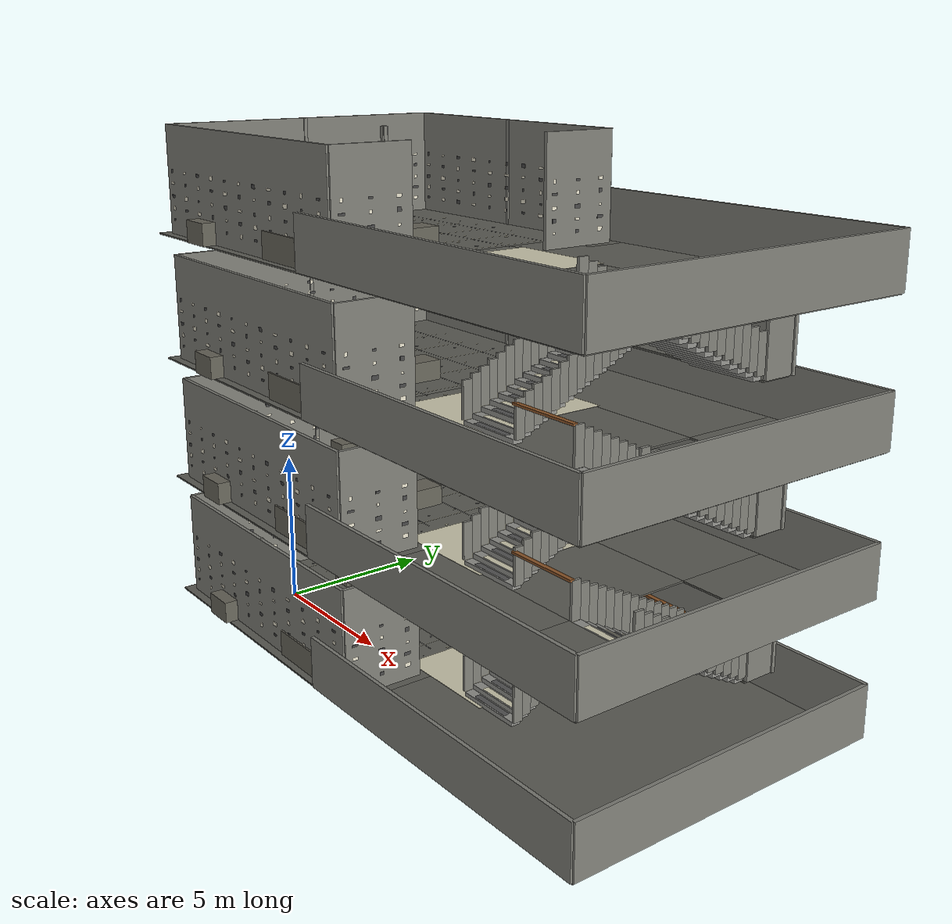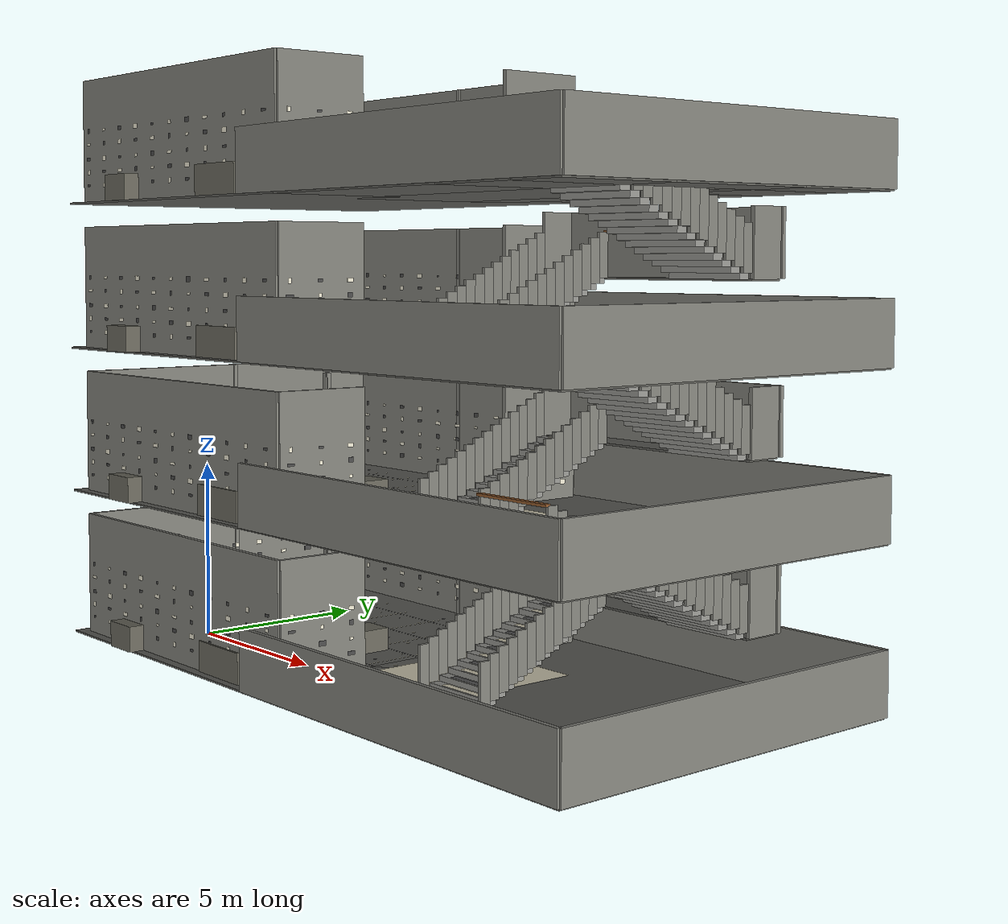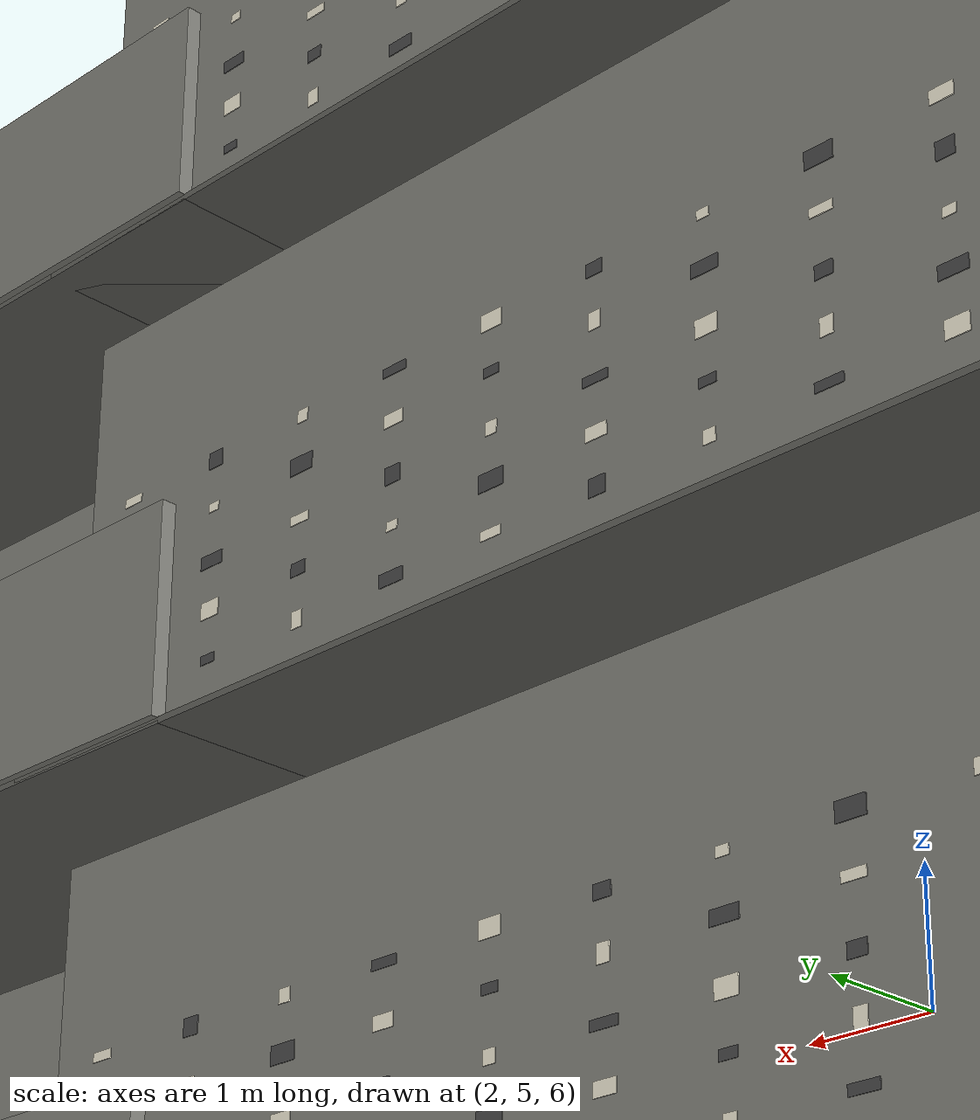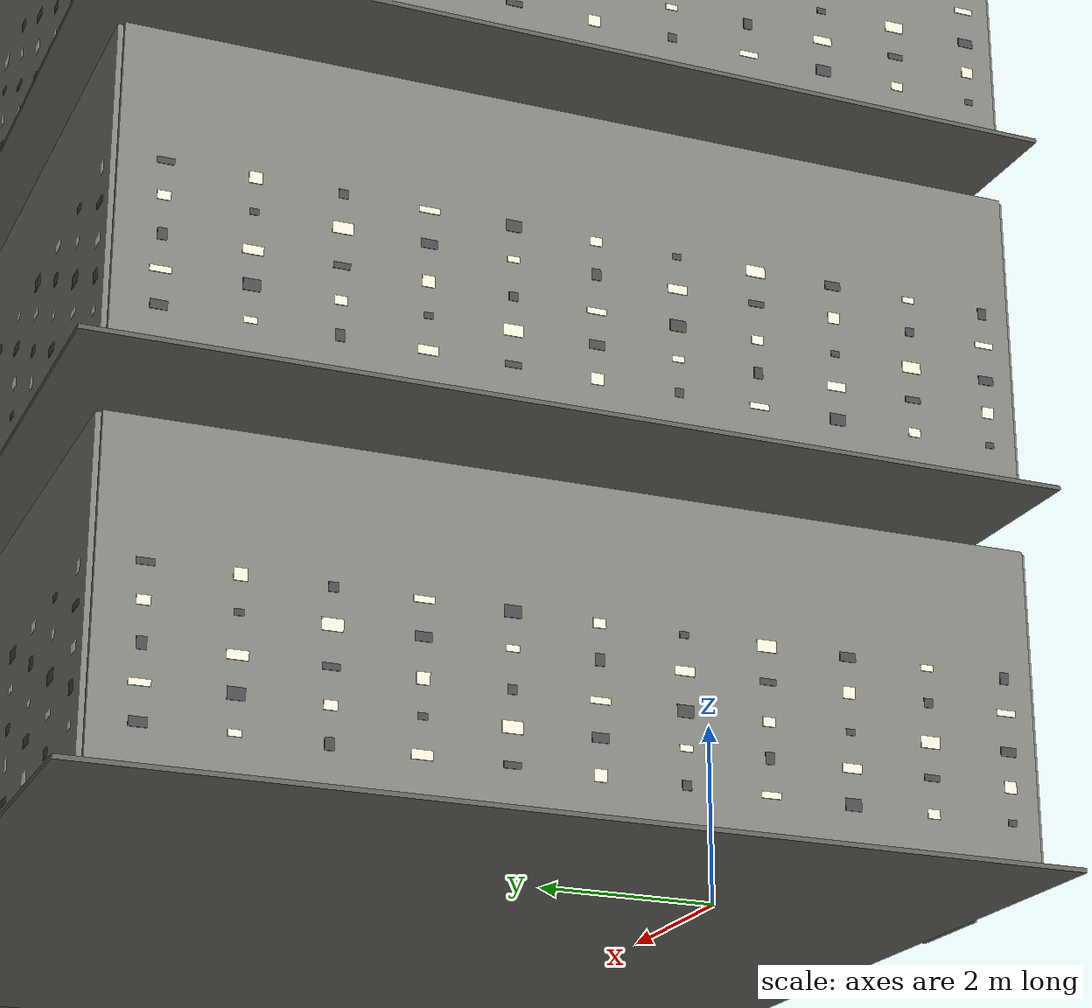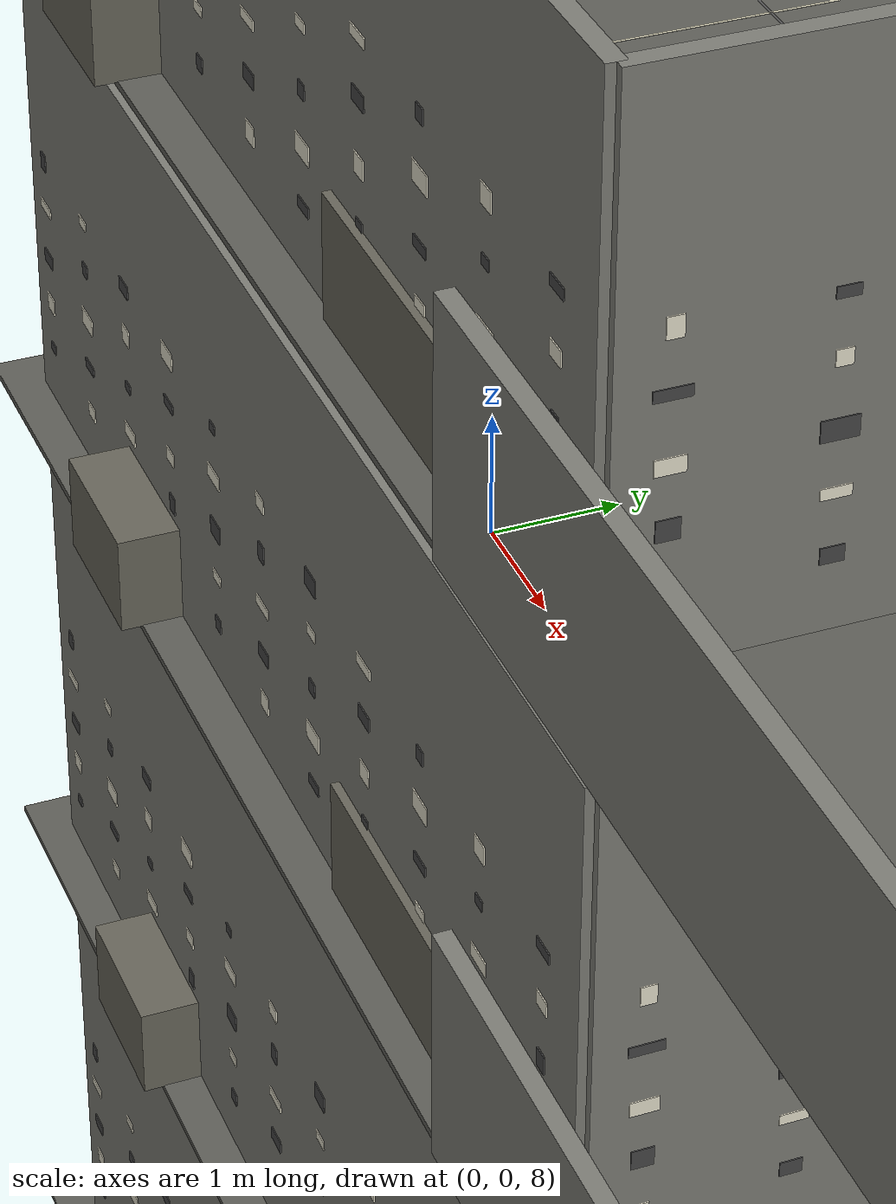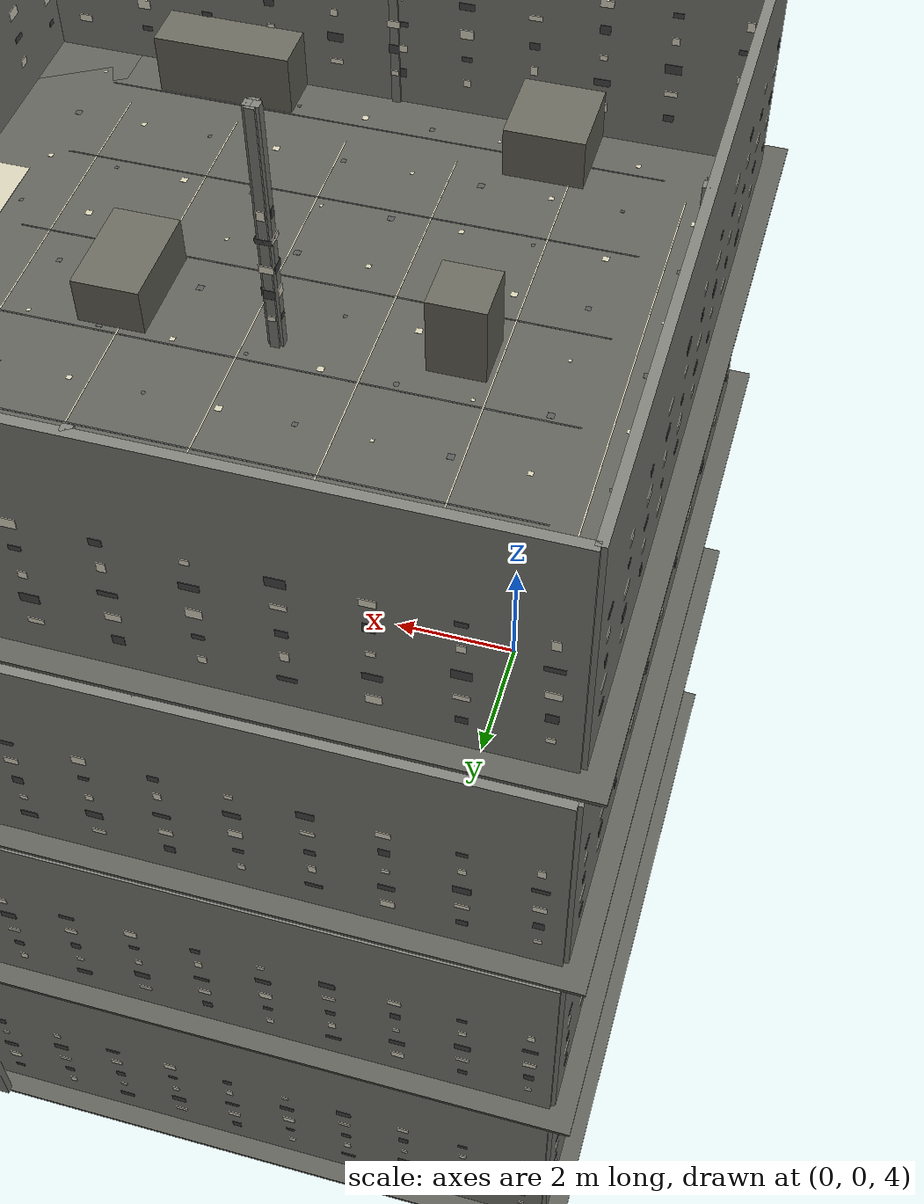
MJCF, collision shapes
<mujoco model="elf3">
  <include file="elf3_bxsim_nav.xml"/>
  <asset>
    <texture name="wall_feature_checker" type="2d" builtin="checker" rgb1="0.50 0.50 0.50" rgb2="0.88 0.88 0.84" width="256" height="256"/>
    <texture name="floor_feature_checker" type="2d" builtin="checker" rgb1="0.46 0.46 0.46" rgb2="0.74 0.74 0.70" width="256" height="256"/>
    <texture name="obstacle_feature_checker" type="2d" builtin="checker" rgb1="0.42 0.42 0.42" rgb2="0.82 0.80 0.74" width="192" height="192"/>
    <material name="room_floor" texture="floor_feature_checker" texuniform="true" texrepeat="18 18" rgba="0.62 0.62 0.60 1"/>
    <material name="room_wall" texture="wall_feature_checker" texuniform="true" texrepeat="18 10" rgba="0.72 0.72 0.70 1"/>
    <material name="room_obstacle" texture="obstacle_feature_checker" texuniform="true" texrepeat="6 6" rgba="0.66 0.66 0.62 1"/>
    <material name="stair_mat" rgba="0.58 0.58 0.56 1"/>
    <material name="wood_plank" rgba="0.56 0.34 0.16 1"/>
    <material name="spawn_marker" rgba="1.00 0.08 0.02 1"/>
    <material name="feature_dark" rgba="0.28 0.28 0.28 1"/>
    <material name="feature_light" rgba="0.92 0.90 0.82 1"/>
    <material name="feature_floor_dark" rgba="0.34 0.34 0.34 1"/>
    <material name="feature_floor_light" rgba="0.82 0.80 0.70 1"/>
  </asset>
  <worldbody>
    <geom name="lower_floor" type="box" pos="2.500 2.500 -0.018" size="5.350 5.350 0.025" material="room_floor"/>
    <geom name="lower_stair_hall_tile_00" type="box" pos="12.150 2.500 -0.018" size="5.900 5.350 0.025" material="room_floor"/>
    <geom name="lower_stair_doorway_marker" type="box" pos="8.550 2.500 0.020" size="1.800 2.208 0.004" material="feature_floor_light" contype="0" conaffinity="0"/>
    <geom name="middle_01_floor" type="box" pos="2.500 2.500 4.182" size="5.350 5.350 0.025" material="room_floor"/>
    <geom name="middle_01_stair_hall_tile_00" type="box" pos="10.165 -1.225 4.182" size="3.915 1.625 0.025" material="room_floor"/>
    <geom name="middle_01_stair_hall_tile_01" type="box" pos="10.165 2.500 4.182" size="3.915 2.100 0.025" material="room_floor"/>
    <geom name="middle_01_stair_hall_tile_02" type="box" pos="10.165 6.225 4.182" size="3.915 1.625 0.025" material="room_floor"/>
    <geom name="middle_01_stair_hall_tile_03" type="box" pos="15.300 -1.225 4.182" size="1.220 1.625 0.025" material="room_floor"/>
    <geom name="middle_01_stair_hall_tile_04" type="box" pos="15.300 6.225 4.182" size="1.220 1.625 0.025" material="room_floor"/>
    <geom name="middle_01_stair_hall_tile_05" type="box" pos="17.285 -1.225 4.182" size="0.765 1.625 0.025" material="room_floor"/>
    <geom name="middle_01_stair_hall_tile_06" type="box" pos="17.285 2.500 4.182" size="0.765 2.100 0.025" material="room_floor"/>
    <geom name="middle_01_stair_hall_tile_07" type="box" pos="17.285 6.225 4.182" size="0.765 1.625 0.025" material="room_floor"/>
    <geom name="middle_01_stair_doorway_marker" type="box" pos="8.550 2.500 4.220" size="1.800 2.208 0.004" material="feature_floor_light" contype="0" conaffinity="0"/>
    <geom name="middle_02_floor" type="box" pos="2.500 2.500 8.382" size="5.350 5.350 0.025" material="room_floor"/>
    <geom name="middle_02_stair_hall_tile_00" type="box" pos="10.165 -1.225 8.382" size="3.915 1.625 0.025" material="room_floor"/>
    <geom name="middle_02_stair_hall_tile_01" type="box" pos="10.165 2.500 8.382" size="3.915 2.100 0.025" material="room_floor"/>
    <geom name="middle_02_stair_hall_tile_02" type="box" pos="10.165 6.225 8.382" size="3.915 1.625 0.025" material="room_floor"/>
    <geom name="middle_02_stair_hall_tile_03" type="box" pos="15.300 -1.225 8.382" size="1.220 1.625 0.025" material="room_floor"/>
    <geom name="middle_02_stair_hall_tile_04" type="box" pos="15.300 6.225 8.382" size="1.220 1.625 0.025" material="room_floor"/>
    <geom name="middle_02_stair_hall_tile_05" type="box" pos="17.285 -1.225 8.382" size="0.765 1.625 0.025" material="room_floor"/>
    <geom name="middle_02_stair_hall_tile_06" type="box" pos="17.285 2.500 8.382" size="0.765 2.100 0.025" material="room_floor"/>
    <geom name="middle_02_stair_hall_tile_07" type="box" pos="17.285 6.225 8.382" size="0.765 1.625 0.025" material="room_floor"/>
    <geom name="middle_02_stair_doorway_marker" type="box" pos="8.550 2.500 8.420" size="1.800 2.208 0.004" material="feature_floor_light" contype="0" conaffinity="0"/>
    <geom name="top_floor" type="box" pos="2.500 2.500 12.582" size="5.350 5.350 0.025" material="room_floor"/>
    <geom name="top_stair_hall_tile_00" type="box" pos="10.165 -1.225 12.582" size="3.915 1.625 0.025" material="room_floor"/>
    <geom name="top_stair_hall_tile_01" type="box" pos="10.165 2.500 12.582" size="3.915 2.100 0.025" material="room_floor"/>
    <geom name="top_stair_hall_tile_02" type="box" pos="10.165 6.225 12.582" size="3.915 1.625 0.025" material="room_floor"/>
    <geom name="top_stair_hall_tile_03" type="box" pos="15.300 -1.225 12.582" size="1.220 1.625 0.025" material="room_floor"/>
    <geom name="top_stair_hall_tile_04" type="box" pos="15.300 6.225 12.582" size="1.220 1.625 0.025" material="room_floor"/>
    <geom name="top_stair_hall_tile_05" type="box" pos="17.285 -1.225 12.582" size="0.765 1.625 0.025" material="room_floor"/>
    <geom name="top_stair_hall_tile_06" type="box" pos="17.285 2.500 12.582" size="0.765 2.100 0.025" material="room_floor"/>
    <geom name="top_stair_hall_tile_07" type="box" pos="17.285 6.225 12.582" size="0.765 1.625 0.025" material="room_floor"/>
    <geom name="top_stair_doorway_marker" type="box" pos="8.550 2.500 12.620" size="1.800 2.208 0.004" material="feature_floor_light" contype="0" conaffinity="0"/>
    <geom name="lower_wall_north_0" type="box" pos="2.500 7.500 1.750" size="5.000 0.060 1.750" material="room_wall"/>
    <geom name="lower_wall_south_0" type="box" pos="2.500 -2.500 1.750" size="5.000 0.060 1.750" material="room_wall"/>
    <geom name="lower_wall_east_0" type="box" pos="7.500 -1.200 1.750" size="0.060 1.300 1.750" material="room_wall"/>
    <geom name="lower_wall_east_1" type="box" pos="7.500 6.200 1.750" size="0.060 1.300 1.750" material="room_wall"/>
    <geom name="lower_wall_west_0" type="box" pos="-2.500 2.500 1.750" size="0.060 5.000 1.750" material="room_wall"/>
    <geom name="lower_wall_v_1_0_0" type="box" pos="2.500 -2.450 1.750" size="0.060 0.050 1.750" material="room_wall"/>
    <geom name="lower_wall_v_1_0_1" type="box" pos="2.500 2.450 1.750" size="0.060 0.050 1.750" material="room_wall"/>
    <geom name="lower_wall_v_1_1_0" type="box" pos="2.500 2.550 1.750" size="0.060 0.050 1.750" material="room_wall"/>
    <geom name="lower_wall_v_1_1_1" type="box" pos="2.500 7.450 1.750" size="0.060 0.050 1.750" material="room_wall"/>
    <geom name="lower_wall_h_1_0_0" type="box" pos="-2.450 2.500 1.750" size="0.050 0.060 1.750" material="room_wall"/>
    <geom name="lower_wall_h_1_0_1" type="box" pos="2.450 2.500 1.750" size="0.050 0.060 1.750" material="room_wall"/>
    <geom name="lower_wall_h_1_1_0" type="box" pos="2.550 2.500 1.750" size="0.050 0.060 1.750" material="room_wall"/>
    <geom name="middle_01_wall_north_0" type="box" pos="2.500 7.500 5.950" size="5.000 0.060 1.750" material="room_wall"/>
    <geom name="middle_01_wall_south_0" type="box" pos="2.500 -2.500 5.950" size="5.000 0.060 1.750" material="room_wall"/>
    <geom name="middle_01_wall_east_0" type="box" pos="7.500 -1.200 5.950" size="0.060 1.300 1.750" material="room_wall"/>
    <geom name="middle_01_wall_east_1" type="box" pos="7.500 6.200 5.950" size="0.060 1.300 1.750" material="room_wall"/>
    <geom name="middle_01_wall_west_0" type="box" pos="-2.500 2.500 5.950" size="0.060 5.000 1.750" material="room_wall"/>
    <geom name="middle_01_wall_v_1_0_0" type="box" pos="2.500 -2.450 5.950" size="0.060 0.050 1.750" material="room_wall"/>
    <geom name="middle_01_wall_v_1_0_1" type="box" pos="2.500 2.450 5.950" size="0.060 0.050 1.750" material="room_wall"/>
    <geom name="middle_01_wall_v_1_1_0" type="box" pos="2.500 2.550 5.950" size="0.060 0.050 1.750" material="room_wall"/>
    <geom name="middle_01_wall_v_1_1_1" type="box" pos="2.500 7.450 5.950" size="0.060 0.050 1.750" material="room_wall"/>
    <geom name="middle_01_wall_h_1_0_0" type="box" pos="-2.450 2.500 5.950" size="0.050 0.060 1.750" material="room_wall"/>
    <geom name="middle_01_wall_h_1_0_1" type="box" pos="2.450 2.500 5.950" size="0.050 0.060 1.750" material="room_wall"/>
    <geom name="middle_01_wall_h_1_1_0" type="box" pos="2.550 2.500 5.950" size="0.050 0.060 1.750" material="room_wall"/>
    <geom name="middle_02_wall_north_0" type="box" pos="2.500 7.500 10.150" size="5.000 0.060 1.750" material="room_wall"/>
    <geom name="middle_02_wall_south_0" type="box" pos="2.500 -2.500 10.150" size="5.000 0.060 1.750" material="room_wall"/>
    <geom name="middle_02_wall_east_0" type="box" pos="7.500 -1.200 10.150" size="0.060 1.300 1.750" material="room_wall"/>
    <geom name="middle_02_wall_east_1" type="box" pos="7.500 6.200 10.150" size="0.060 1.300 1.750" material="room_wall"/>
    <geom name="middle_02_wall_west_0" type="box" pos="-2.500 2.500 10.150" size="0.060 5.000 1.750" material="room_wall"/>
    <geom name="middle_02_wall_v_1_0_0" type="box" pos="2.500 -2.450 10.150" size="0.060 0.050 1.750" material="room_wall"/>
    <geom name="middle_02_wall_v_1_0_1" type="box" pos="2.500 2.450 10.150" size="0.060 0.050 1.750" material="room_wall"/>
    <geom name="middle_02_wall_v_1_1_0" type="box" pos="2.500 2.550 10.150" size="0.060 0.050 1.750" material="room_wall"/>
    <geom name="middle_02_wall_v_1_1_1" type="box" pos="2.500 7.450 10.150" size="0.060 0.050 1.750" material="room_wall"/>
    <geom name="middle_02_wall_h_1_0_0" type="box" pos="-2.450 2.500 10.150" size="0.050 0.060 1.750" material="room_wall"/>
    <geom name="middle_02_wall_h_1_0_1" type="box" pos="2.450 2.500 10.150" size="0.050 0.060 1.750" material="room_wall"/>
    <geom name="middle_02_wall_h_1_1_0" type="box" pos="2.550 2.500 10.150" size="0.050 0.060 1.750" material="room_wall"/>
    <geom name="top_wall_north_0" type="box" pos="2.500 7.500 14.350" size="5.000 0.060 1.750" material="room_wall"/>
    <geom name="top_wall_south_0" type="box" pos="2.500 -2.500 14.350" size="5.000 0.060 1.750" material="room_wall"/>
    <geom name="top_wall_east_0" type="box" pos="7.500 -1.200 14.350" size="0.060 1.300 1.750" material="room_wall"/>
    <geom name="top_wall_east_1" type="box" pos="7.500 6.200 14.350" size="0.060 1.300 1.750" material="room_wall"/>
    <geom name="top_wall_west_0" type="box" pos="-2.500 2.500 14.350" size="0.060 5.000 1.750" material="room_wall"/>
    <geom name="top_wall_v_1_0_0" type="box" pos="2.500 -2.450 14.350" size="0.060 0.050 1.750" material="room_wall"/>
    <geom name="top_wall_v_1_0_1" type="box" pos="2.500 2.450 14.350" size="0.060 0.050 1.750" material="room_wall"/>
    <geom name="top_wall_v_1_1_0" type="box" pos="2.500 2.550 14.350" size="0.060 0.050 1.750" material="room_wall"/>
    <geom name="top_wall_v_1_1_1" type="box" pos="2.500 7.450 14.350" size="0.060 0.050 1.750" material="room_wall"/>
    <geom name="top_wall_h_1_0_0" type="box" pos="-2.450 2.500 14.350" size="0.050 0.060 1.750" material="room_wall"/>
    <geom name="top_wall_h_1_0_1" type="box" pos="2.450 2.500 14.350" size="0.050 0.060 1.750" material="room_wall"/>
    <geom name="top_wall_h_1_1_0" type="box" pos="2.550 2.500 14.350" size="0.050 0.060 1.750" material="room_wall"/>
    <geom name="lower_stair_hall_east_guard" type="box" pos="18.050 2.500 0.825" size="0.060 5.350 0.825" material="room_wall"/>
    <geom name="lower_stair_hall_north_guard" type="box" pos="12.150 7.850 0.825" size="5.900 0.060 0.825" material="room_wall"/>
    <geom name="lower_stair_hall_south_guard" type="box" pos="12.150 -2.850 0.825" size="5.900 0.060 0.825" material="room_wall"/>
    <geom name="middle_01_stair_hall_east_guard" type="box" pos="18.050 2.500 5.025" size="0.060 5.350 0.825" material="room_wall"/>
    <geom name="middle_01_stair_hall_north_guard" type="box" pos="12.150 7.850 5.025" size="5.900 0.060 0.825" material="room_wall"/>
    <geom name="middle_01_stair_hall_south_guard" type="box" pos="12.150 -2.850 5.025" size="5.900 0.060 0.825" material="room_wall"/>
    <geom name="middle_01_floor_inner_rail_board" type="box" pos="12.950 0.400 5.360" size="1.220 0.075 0.035" material="wood_plank"/>
    <geom name="middle_02_stair_hall_east_guard" type="box" pos="18.050 2.500 9.225" size="0.060 5.350 0.825" material="room_wall"/>
    <geom name="middle_02_stair_hall_north_guard" type="box" pos="12.150 7.850 9.225" size="5.900 0.060 0.825" material="room_wall"/>
    <geom name="middle_02_stair_hall_south_guard" type="box" pos="12.150 -2.850 9.225" size="5.900 0.060 0.825" material="room_wall"/>
    <geom name="middle_02_floor_inner_rail_board" type="box" pos="12.950 0.400 9.560" size="1.220 0.075 0.035" material="wood_plank"/>
    <geom name="top_stair_hall_east_guard" type="box" pos="18.050 2.500 13.425" size="0.060 5.350 0.825" material="room_wall"/>
    <geom name="top_stair_hall_north_guard" type="box" pos="12.150 7.850 13.425" size="5.900 0.060 0.825" material="room_wall"/>
    <geom name="top_stair_hall_south_guard" type="box" pos="12.150 -2.850 13.425" size="5.900 0.060 0.825" material="room_wall"/>
    <geom name="stair_00_01_mid_landing" type="box" pos="12.950 5.100 2.082" size="3.550 0.500 0.025" material="room_floor"/>
    <geom name="stair_00_01_mid_landing_north_guard" type="box" pos="12.950 5.620 2.950" size="3.650 0.055 0.850" material="room_wall"/>
    <geom name="stair_00_01_mid_landing_west_guard" type="box" pos="9.400 5.100 2.950" size="0.055 0.480 0.850" material="room_wall"/>
    <geom name="stair_00_01_mid_landing_east_guard" type="box" pos="16.500 5.100 2.950" size="0.055 0.480 0.850" material="room_wall"/>
    <geom name="stair_00_01_flight_a_step_00" type="box" pos="10.600 0.550 0.075" size="1.100 0.150 0.075" material="stair_mat"/>
    <geom name="feature_stair_00_01_flight_a_tread_00" type="box" pos="10.600 0.550 0.154" size="0.704 0.102 0.001" material="feature_floor_dark" contype="0" conaffinity="0"/>
    <geom name="stair_00_01_flight_a_step_01" type="box" pos="10.600 0.850 0.225" size="1.100 0.150 0.075" material="stair_mat"/>
    <geom name="feature_stair_00_01_flight_a_tread_01" type="box" pos="10.600 0.850 0.304" size="0.704 0.102 0.001" material="feature_floor_light" contype="0" conaffinity="0"/>
    <geom name="stair_00_01_flight_a_step_02" type="box" pos="10.600 1.150 0.375" size="1.100 0.150 0.075" material="stair_mat"/>
    <geom name="feature_stair_00_01_flight_a_tread_02" type="box" pos="10.600 1.150 0.454" size="0.704 0.102 0.001" material="feature_floor_dark" contype="0" conaffinity="0"/>
    <geom name="stair_00_01_flight_a_step_03" type="box" pos="10.600 1.450 0.525" size="1.100 0.150 0.075" material="stair_mat"/>
    <geom name="feature_stair_00_01_flight_a_tread_03" type="box" pos="10.600 1.450 0.604" size="0.704 0.102 0.001" material="feature_floor_light" contype="0" conaffinity="0"/>
    <geom name="stair_00_01_flight_a_step_04" type="box" pos="10.600 1.750 0.675" size="1.100 0.150 0.075" material="stair_mat"/>
    <geom name="feature_stair_00_01_flight_a_tread_04" type="box" pos="10.600 1.750 0.754" size="0.704 0.102 0.001" material="feature_floor_dark" contype="0" conaffinity="0"/>
    <geom name="stair_00_01_flight_a_step_05" type="box" pos="10.600 2.050 0.825" size="1.100 0.150 0.075" material="stair_mat"/>
    <geom name="feature_stair_00_01_flight_a_tread_05" type="box" pos="10.600 2.050 0.904" size="0.704 0.102 0.001" material="feature_floor_light" contype="0" conaffinity="0"/>
    <geom name="stair_00_01_flight_a_step_06" type="box" pos="10.600 2.350 0.975" size="1.100 0.150 0.075" material="stair_mat"/>
    <geom name="feature_stair_00_01_flight_a_tread_06" type="box" pos="10.600 2.350 1.054" size="0.704 0.102 0.001" material="feature_floor_dark" contype="0" conaffinity="0"/>
    <geom name="stair_00_01_flight_a_step_07" type="box" pos="10.600 2.650 1.125" size="1.100 0.150 0.075" material="stair_mat"/>
    <geom name="feature_stair_00_01_flight_a_tread_07" type="box" pos="10.600 2.650 1.204" size="0.704 0.102 0.001" material="feature_floor_light" contype="0" conaffinity="0"/>
    <geom name="stair_00_01_flight_a_step_08" type="box" pos="10.600 2.950 1.275" size="1.100 0.150 0.075" material="stair_mat"/>
    <geom name="feature_stair_00_01_flight_a_tread_08" type="box" pos="10.600 2.950 1.354" size="0.704 0.102 0.001" material="feature_floor_dark" contype="0" conaffinity="0"/>
    <geom name="stair_00_01_flight_a_step_09" type="box" pos="10.600 3.250 1.425" size="1.100 0.150 0.075" material="stair_mat"/>
    <geom name="feature_stair_00_01_flight_a_tread_09" type="box" pos="10.600 3.250 1.504" size="0.704 0.102 0.001" material="feature_floor_light" contype="0" conaffinity="0"/>
    <geom name="stair_00_01_flight_a_step_10" type="box" pos="10.600 3.550 1.575" size="1.100 0.150 0.075" material="stair_mat"/>
    <geom name="feature_stair_00_01_flight_a_tread_10" type="box" pos="10.600 3.550 1.654" size="0.704 0.102 0.001" material="feature_floor_dark" contype="0" conaffinity="0"/>
    <geom name="stair_00_01_flight_a_step_11" type="box" pos="10.600 3.850 1.725" size="1.100 0.150 0.075" material="stair_mat"/>
    <geom name="feature_stair_00_01_flight_a_tread_11" type="box" pos="10.600 3.850 1.804" size="0.704 0.102 0.001" material="feature_floor_light" contype="0" conaffinity="0"/>
    <geom name="stair_00_01_flight_a_step_12" type="box" pos="10.600 4.150 1.875" size="1.100 0.150 0.075" material="stair_mat"/>
    <geom name="feature_stair_00_01_flight_a_tread_12" type="box" pos="10.600 4.150 1.954" size="0.704 0.102 0.001" material="feature_floor_dark" contype="0" conaffinity="0"/>
    <geom name="stair_00_01_flight_a_step_13" type="box" pos="10.600 4.450 2.025" size="1.100 0.150 0.075" material="stair_mat"/>
    <geom name="feature_stair_00_01_flight_a_tread_13" type="box" pos="10.600 4.450 2.104" size="0.704 0.102 0.001" material="feature_floor_light" contype="0" conaffinity="0"/>
    <geom name="stair_00_01_flight_a_left_side_wall_00" type="box" pos="11.770 0.550 0.725" size="0.045 0.150 0.575" material="room_wall"/>
    <geom name="stair_00_01_flight_a_right_side_wall_00" type="box" pos="9.430 0.550 0.725" size="0.045 0.150 0.575" material="room_wall"/>
    <geom name="stair_00_01_flight_a_left_side_wall_01" type="box" pos="11.770 0.850 0.875" size="0.045 0.150 0.575" material="room_wall"/>
    <geom name="stair_00_01_flight_a_right_side_wall_01" type="box" pos="9.430 0.850 0.875" size="0.045 0.150 0.575" material="room_wall"/>
    <geom name="stair_00_01_flight_a_left_side_wall_02" type="box" pos="11.770 1.150 1.025" size="0.045 0.150 0.575" material="room_wall"/>
    <geom name="stair_00_01_flight_a_right_side_wall_02" type="box" pos="9.430 1.150 1.025" size="0.045 0.150 0.575" material="room_wall"/>
    <geom name="stair_00_01_flight_a_left_side_wall_03" type="box" pos="11.770 1.450 1.175" size="0.045 0.150 0.575" material="room_wall"/>
    <geom name="stair_00_01_flight_a_right_side_wall_03" type="box" pos="9.430 1.450 1.175" size="0.045 0.150 0.575" material="room_wall"/>
    <geom name="stair_00_01_flight_a_left_side_wall_04" type="box" pos="11.770 1.750 1.325" size="0.045 0.150 0.575" material="room_wall"/>
    <geom name="stair_00_01_flight_a_right_side_wall_04" type="box" pos="9.430 1.750 1.325" size="0.045 0.150 0.575" material="room_wall"/>
    <geom name="stair_00_01_flight_a_left_side_wall_05" type="box" pos="11.770 2.050 1.475" size="0.045 0.150 0.575" material="room_wall"/>
    <geom name="stair_00_01_flight_a_right_side_wall_05" type="box" pos="9.430 2.050 1.475" size="0.045 0.150 0.575" material="room_wall"/>
    <geom name="stair_00_01_flight_a_left_side_wall_06" type="box" pos="11.770 2.350 1.625" size="0.045 0.150 0.575" material="room_wall"/>
    <geom name="stair_00_01_flight_a_right_side_wall_06" type="box" pos="9.430 2.350 1.625" size="0.045 0.150 0.575" material="room_wall"/>
    <geom name="stair_00_01_flight_a_left_side_wall_07" type="box" pos="11.770 2.650 1.775" size="0.045 0.150 0.575" material="room_wall"/>
    <geom name="stair_00_01_flight_a_right_side_wall_07" type="box" pos="9.430 2.650 1.775" size="0.045 0.150 0.575" material="room_wall"/>
    <geom name="stair_00_01_flight_a_left_side_wall_08" type="box" pos="11.770 2.950 1.925" size="0.045 0.150 0.575" material="room_wall"/>
    <geom name="stair_00_01_flight_a_right_side_wall_08" type="box" pos="9.430 2.950 1.925" size="0.045 0.150 0.575" material="room_wall"/>
    <geom name="stair_00_01_flight_a_left_side_wall_09" type="box" pos="11.770 3.250 2.075" size="0.045 0.150 0.575" material="room_wall"/>
    <geom name="stair_00_01_flight_a_right_side_wall_09" type="box" pos="9.430 3.250 2.075" size="0.045 0.150 0.575" material="room_wall"/>
    <geom name="stair_00_01_flight_a_left_side_wall_10" type="box" pos="11.770 3.550 2.225" size="0.045 0.150 0.575" material="room_wall"/>
    <geom name="stair_00_01_flight_a_right_side_wall_10" type="box" pos="9.430 3.550 2.225" size="0.045 0.150 0.575" material="room_wall"/>
    <geom name="stair_00_01_flight_a_left_side_wall_11" type="box" pos="11.770 3.850 2.375" size="0.045 0.150 0.575" material="room_wall"/>
    <geom name="stair_00_01_flight_a_right_side_wall_11" type="box" pos="9.430 3.850 2.375" size="0.045 0.150 0.575" material="room_wall"/>
    <geom name="stair_00_01_flight_a_left_side_wall_12" type="box" pos="11.770 4.150 2.525" size="0.045 0.150 0.575" material="room_wall"/>
    <geom name="stair_00_01_flight_a_right_side_wall_12" type="box" pos="9.430 4.150 2.525" size="0.045 0.150 0.575" material="room_wall"/>
    <geom name="stair_00_01_flight_a_left_side_wall_13" type="box" pos="11.770 4.450 2.675" size="0.045 0.150 0.575" material="room_wall"/>
    <geom name="stair_00_01_flight_a_right_side_wall_13" type="box" pos="9.430 4.450 2.675" size="0.045 0.150 0.575" material="room_wall"/>
    <geom name="stair_00_01_flight_b_step_00" type="box" pos="15.300 4.450 2.175" size="1.100 0.150 0.075" material="stair_mat"/>
    <geom name="feature_stair_00_01_flight_b_tread_00" type="box" pos="15.300 4.450 2.254" size="0.704 0.102 0.001" material="feature_floor_dark" contype="0" conaffinity="0"/>
    <geom name="stair_00_01_flight_b_step_01" type="box" pos="15.300 4.150 2.325" size="1.100 0.150 0.075" material="stair_mat"/>
    <geom name="feature_stair_00_01_flight_b_tread_01" type="box" pos="15.300 4.150 2.404" size="0.704 0.102 0.001" material="feature_floor_light" contype="0" conaffinity="0"/>
    <geom name="stair_00_01_flight_b_step_02" type="box" pos="15.300 3.850 2.475" size="1.100 0.150 0.075" material="stair_mat"/>
    <geom name="feature_stair_00_01_flight_b_tread_02" type="box" pos="15.300 3.850 2.554" size="0.704 0.102 0.001" material="feature_floor_dark" contype="0" conaffinity="0"/>
    <geom name="stair_00_01_flight_b_step_03" type="box" pos="15.300 3.550 2.625" size="1.100 0.150 0.075" material="stair_mat"/>
    <geom name="feature_stair_00_01_flight_b_tread_03" type="box" pos="15.300 3.550 2.704" size="0.704 0.102 0.001" material="feature_floor_light" contype="0" conaffinity="0"/>
    <geom name="stair_00_01_flight_b_step_04" type="box" pos="15.300 3.250 2.775" size="1.100 0.150 0.075" material="stair_mat"/>
    <geom name="feature_stair_00_01_flight_b_tread_04" type="box" pos="15.300 3.250 2.854" size="0.704 0.102 0.001" material="feature_floor_dark" contype="0" conaffinity="0"/>
    <geom name="stair_00_01_flight_b_step_05" type="box" pos="15.300 2.950 2.925" size="1.100 0.150 0.075" material="stair_mat"/>
    <geom name="feature_stair_00_01_flight_b_tread_05" type="box" pos="15.300 2.950 3.004" size="0.704 0.102 0.001" material="feature_floor_light" contype="0" conaffinity="0"/>
    <geom name="stair_00_01_flight_b_step_06" type="box" pos="15.300 2.650 3.075" size="1.100 0.150 0.075" material="stair_mat"/>
    <geom name="feature_stair_00_01_flight_b_tread_06" type="box" pos="15.300 2.650 3.154" size="0.704 0.102 0.001" material="feature_floor_dark" contype="0" conaffinity="0"/>
    <geom name="stair_00_01_flight_b_step_07" type="box" pos="15.300 2.350 3.225" size="1.100 0.150 0.075" material="stair_mat"/>
    <geom name="feature_stair_00_01_flight_b_tread_07" type="box" pos="15.300 2.350 3.304" size="0.704 0.102 0.001" material="feature_floor_light" contype="0" conaffinity="0"/>
    <geom name="stair_00_01_flight_b_step_08" type="box" pos="15.300 2.050 3.375" size="1.100 0.150 0.075" material="stair_mat"/>
    <geom name="feature_stair_00_01_flight_b_tread_08" type="box" pos="15.300 2.050 3.454" size="0.704 0.102 0.001" material="feature_floor_dark" contype="0" conaffinity="0"/>
    <geom name="stair_00_01_flight_b_step_09" type="box" pos="15.300 1.750 3.525" size="1.100 0.150 0.075" material="stair_mat"/>
    <geom name="feature_stair_00_01_flight_b_tread_09" type="box" pos="15.300 1.750 3.604" size="0.704 0.102 0.001" material="feature_floor_light" contype="0" conaffinity="0"/>
    <geom name="stair_00_01_flight_b_step_10" type="box" pos="15.300 1.450 3.675" size="1.100 0.150 0.075" material="stair_mat"/>
    <geom name="feature_stair_00_01_flight_b_tread_10" type="box" pos="15.300 1.450 3.754" size="0.704 0.102 0.001" material="feature_floor_dark" contype="0" conaffinity="0"/>
    <geom name="stair_00_01_flight_b_step_11" type="box" pos="15.300 1.150 3.825" size="1.100 0.150 0.075" material="stair_mat"/>
    <geom name="feature_stair_00_01_flight_b_tread_11" type="box" pos="15.300 1.150 3.904" size="0.704 0.102 0.001" material="feature_floor_light" contype="0" conaffinity="0"/>
    <geom name="stair_00_01_flight_b_step_12" type="box" pos="15.300 0.850 3.975" size="1.100 0.150 0.075" material="stair_mat"/>
    <geom name="feature_stair_00_01_flight_b_tread_12" type="box" pos="15.300 0.850 4.054" size="0.704 0.102 0.001" material="feature_floor_dark" contype="0" conaffinity="0"/>
    <geom name="stair_00_01_flight_b_step_13" type="box" pos="15.300 0.550 4.125" size="1.100 0.150 0.075" material="stair_mat"/>
    <geom name="feature_stair_00_01_flight_b_tread_13" type="box" pos="15.300 0.550 4.204" size="0.704 0.102 0.001" material="feature_floor_light" contype="0" conaffinity="0"/>
    <geom name="stair_00_01_flight_b_left_side_wall_00" type="box" pos="16.470 4.450 2.825" size="0.045 0.150 0.575" material="room_wall"/>
    <geom name="stair_00_01_flight_b_right_side_wall_00" type="box" pos="14.130 4.450 2.825" size="0.045 0.150 0.575" material="room_wall"/>
    <geom name="stair_00_01_flight_b_left_side_wall_01" type="box" pos="16.470 4.150 2.975" size="0.045 0.150 0.575" material="room_wall"/>
    <geom name="stair_00_01_flight_b_right_side_wall_01" type="box" pos="14.130 4.150 2.975" size="0.045 0.150 0.575" material="room_wall"/>
    <geom name="stair_00_01_flight_b_left_side_wall_02" type="box" pos="16.470 3.850 3.125" size="0.045 0.150 0.575" material="room_wall"/>
    <geom name="stair_00_01_flight_b_right_side_wall_02" type="box" pos="14.130 3.850 3.125" size="0.045 0.150 0.575" material="room_wall"/>
    <geom name="stair_00_01_flight_b_left_side_wall_03" type="box" pos="16.470 3.550 3.275" size="0.045 0.150 0.575" material="room_wall"/>
    <geom name="stair_00_01_flight_b_right_side_wall_03" type="box" pos="14.130 3.550 3.275" size="0.045 0.150 0.575" material="room_wall"/>
    <geom name="stair_00_01_flight_b_left_side_wall_04" type="box" pos="16.470 3.250 3.425" size="0.045 0.150 0.575" material="room_wall"/>
    <geom name="stair_00_01_flight_b_right_side_wall_04" type="box" pos="14.130 3.250 3.425" size="0.045 0.150 0.575" material="room_wall"/>
    <geom name="stair_00_01_flight_b_left_side_wall_05" type="box" pos="16.470 2.950 3.575" size="0.045 0.150 0.575" material="room_wall"/>
    <geom name="stair_00_01_flight_b_right_side_wall_05" type="box" pos="14.130 2.950 3.575" size="0.045 0.150 0.575" material="room_wall"/>
    <geom name="stair_00_01_flight_b_left_side_wall_06" type="box" pos="16.470 2.650 3.725" size="0.045 0.150 0.575" material="room_wall"/>
    <geom name="stair_00_01_flight_b_right_side_wall_06" type="box" pos="14.130 2.650 3.725" size="0.045 0.150 0.575" material="room_wall"/>
    <geom name="stair_00_01_flight_b_left_side_wall_07" type="box" pos="16.470 2.350 3.875" size="0.045 0.150 0.575" material="room_wall"/>
    <geom name="stair_00_01_flight_b_right_side_wall_07" type="box" pos="14.130 2.350 3.875" size="0.045 0.150 0.575" material="room_wall"/>
    <geom name="stair_00_01_flight_b_left_side_wall_08" type="box" pos="16.470 2.050 4.025" size="0.045 0.150 0.575" material="room_wall"/>
    <geom name="stair_00_01_flight_b_right_side_wall_08" type="box" pos="14.130 2.050 4.025" size="0.045 0.150 0.575" material="room_wall"/>
    <geom name="stair_00_01_flight_b_left_side_wall_09" type="box" pos="16.470 1.750 4.175" size="0.045 0.150 0.575" material="room_wall"/>
    <geom name="stair_00_01_flight_b_right_side_wall_09" type="box" pos="14.130 1.750 4.175" size="0.045 0.150 0.575" material="room_wall"/>
    <geom name="stair_00_01_flight_b_left_side_wall_10" type="box" pos="16.470 1.450 4.325" size="0.045 0.150 0.575" material="room_wall"/>
    <geom name="stair_00_01_flight_b_right_side_wall_10" type="box" pos="14.130 1.450 4.325" size="0.045 0.150 0.575" material="room_wall"/>
    <geom name="stair_00_01_flight_b_left_side_wall_11" type="box" pos="16.470 1.150 4.475" size="0.045 0.150 0.575" material="room_wall"/>
    <geom name="stair_00_01_flight_b_right_side_wall_11" type="box" pos="14.130 1.150 4.475" size="0.045 0.150 0.575" material="room_wall"/>
    <geom name="stair_00_01_flight_b_left_side_wall_12" type="box" pos="16.470 0.850 4.625" size="0.045 0.150 0.575" material="room_wall"/>
    <geom name="stair_00_01_flight_b_right_side_wall_12" type="box" pos="14.130 0.850 4.625" size="0.045 0.150 0.575" material="room_wall"/>
    <geom name="stair_00_01_flight_b_left_side_wall_13" type="box" pos="16.470 0.550 4.775" size="0.045 0.150 0.575" material="room_wall"/>
    <geom name="stair_00_01_flight_b_right_side_wall_13" type="box" pos="14.130 0.550 4.775" size="0.045 0.150 0.575" material="room_wall"/>
    <geom name="stair_00_01_mid_landing_inner_rail_board" type="box" pos="12.950 4.600 3.260" size="1.220 0.075 0.035" material="wood_plank"/>
    <geom name="stair_01_02_mid_landing" type="box" pos="12.950 5.100 6.282" size="3.550 0.500 0.025" material="room_floor"/>
    <geom name="stair_01_02_mid_landing_north_guard" type="box" pos="12.950 5.620 7.150" size="3.650 0.055 0.850" material="room_wall"/>
    <geom name="stair_01_02_mid_landing_west_guard" type="box" pos="9.400 5.100 7.150" size="0.055 0.480 0.850" material="room_wall"/>
    <geom name="stair_01_02_mid_landing_east_guard" type="box" pos="16.500 5.100 7.150" size="0.055 0.480 0.850" material="room_wall"/>
    <geom name="stair_01_02_flight_a_step_00" type="box" pos="10.600 0.550 4.275" size="1.100 0.150 0.075" material="stair_mat"/>
    <geom name="feature_stair_01_02_flight_a_tread_00" type="box" pos="10.600 0.550 4.354" size="0.704 0.102 0.001" material="feature_floor_dark" contype="0" conaffinity="0"/>
    <geom name="stair_01_02_flight_a_step_01" type="box" pos="10.600 0.850 4.425" size="1.100 0.150 0.075" material="stair_mat"/>
    <geom name="feature_stair_01_02_flight_a_tread_01" type="box" pos="10.600 0.850 4.504" size="0.704 0.102 0.001" material="feature_floor_light" contype="0" conaffinity="0"/>
    <geom name="stair_01_02_flight_a_step_02" type="box" pos="10.600 1.150 4.575" size="1.100 0.150 0.075" material="stair_mat"/>
    <geom name="feature_stair_01_02_flight_a_tread_02" type="box" pos="10.600 1.150 4.654" size="0.704 0.102 0.001" material="feature_floor_dark" contype="0" conaffinity="0"/>
    <geom name="stair_01_02_flight_a_step_03" type="box" pos="10.600 1.450 4.725" size="1.100 0.150 0.075" material="stair_mat"/>
    <geom name="feature_stair_01_02_flight_a_tread_03" type="box" pos="10.600 1.450 4.804" size="0.704 0.102 0.001" material="feature_floor_light" contype="0" conaffinity="0"/>
    <geom name="stair_01_02_flight_a_step_04" type="box" pos="10.600 1.750 4.875" size="1.100 0.150 0.075" material="stair_mat"/>
    <geom name="feature_stair_01_02_flight_a_tread_04" type="box" pos="10.600 1.750 4.954" size="0.704 0.102 0.001" material="feature_floor_dark" contype="0" conaffinity="0"/>
    <geom name="stair_01_02_flight_a_step_05" type="box" pos="10.600 2.050 5.025" size="1.100 0.150 0.075" material="stair_mat"/>
    <geom name="feature_stair_01_02_flight_a_tread_05" type="box" pos="10.600 2.050 5.104" size="0.704 0.102 0.001" material="feature_floor_light" contype="0" conaffinity="0"/>
    <geom name="stair_01_02_flight_a_step_06" type="box" pos="10.600 2.350 5.175" size="1.100 0.150 0.075" material="stair_mat"/>
    <geom name="feature_stair_01_02_flight_a_tread_06" type="box" pos="10.600 2.350 5.254" size="0.704 0.102 0.001" material="feature_floor_dark" contype="0" conaffinity="0"/>
    <geom name="stair_01_02_flight_a_step_07" type="box" pos="10.600 2.650 5.325" size="1.100 0.150 0.075" material="stair_mat"/>
    <geom name="feature_stair_01_02_flight_a_tread_07" type="box" pos="10.600 2.650 5.404" size="0.704 0.102 0.001" material="feature_floor_light" contype="0" conaffinity="0"/>
    <geom name="stair_01_02_flight_a_step_08" type="box" pos="10.600 2.950 5.475" size="1.100 0.150 0.075" material="stair_mat"/>
    <geom name="feature_stair_01_02_flight_a_tread_08" type="box" pos="10.600 2.950 5.554" size="0.704 0.102 0.001" material="feature_floor_dark" contype="0" conaffinity="0"/>
    <geom name="stair_01_02_flight_a_step_09" type="box" pos="10.600 3.250 5.625" size="1.100 0.150 0.075" material="stair_mat"/>
    <geom name="feature_stair_01_02_flight_a_tread_09" type="box" pos="10.600 3.250 5.704" size="0.704 0.102 0.001" material="feature_floor_light" contype="0" conaffinity="0"/>
    <geom name="stair_01_02_flight_a_step_10" type="box" pos="10.600 3.550 5.775" size="1.100 0.150 0.075" material="stair_mat"/>
    <geom name="feature_stair_01_02_flight_a_tread_10" type="box" pos="10.600 3.550 5.854" size="0.704 0.102 0.001" material="feature_floor_dark" contype="0" conaffinity="0"/>
    <geom name="stair_01_02_flight_a_step_11" type="box" pos="10.600 3.850 5.925" size="1.100 0.150 0.075" material="stair_mat"/>
    <geom name="feature_stair_01_02_flight_a_tread_11" type="box" pos="10.600 3.850 6.004" size="0.704 0.102 0.001" material="feature_floor_light" contype="0" conaffinity="0"/>
    <geom name="stair_01_02_flight_a_step_12" type="box" pos="10.600 4.150 6.075" size="1.100 0.150 0.075" material="stair_mat"/>
    <geom name="feature_stair_01_02_flight_a_tread_12" type="box" pos="10.600 4.150 6.154" size="0.704 0.102 0.001" material="feature_floor_dark" contype="0" conaffinity="0"/>
    <geom name="stair_01_02_flight_a_step_13" type="box" pos="10.600 4.450 6.225" size="1.100 0.150 0.075" material="stair_mat"/>
    <geom name="feature_stair_01_02_flight_a_tread_13" type="box" pos="10.600 4.450 6.304" size="0.704 0.102 0.001" material="feature_floor_light" contype="0" conaffinity="0"/>
    <geom name="stair_01_02_flight_a_left_side_wall_00" type="box" pos="11.770 0.550 4.925" size="0.045 0.150 0.575" material="room_wall"/>
    <geom name="stair_01_02_flight_a_right_side_wall_00" type="box" pos="9.430 0.550 4.925" size="0.045 0.150 0.575" material="room_wall"/>
    <geom name="stair_01_02_flight_a_left_side_wall_01" type="box" pos="11.770 0.850 5.075" size="0.045 0.150 0.575" material="room_wall"/>
    <geom name="stair_01_02_flight_a_right_side_wall_01" type="box" pos="9.430 0.850 5.075" size="0.045 0.150 0.575" material="room_wall"/>
    <geom name="stair_01_02_flight_a_left_side_wall_02" type="box" pos="11.770 1.150 5.225" size="0.045 0.150 0.575" material="room_wall"/>
    <geom name="stair_01_02_flight_a_right_side_wall_02" type="box" pos="9.430 1.150 5.225" size="0.045 0.150 0.575" material="room_wall"/>
    <geom name="stair_01_02_flight_a_left_side_wall_03" type="box" pos="11.770 1.450 5.375" size="0.045 0.150 0.575" material="room_wall"/>
    <geom name="stair_01_02_flight_a_right_side_wall_03" type="box" pos="9.430 1.450 5.375" size="0.045 0.150 0.575" material="room_wall"/>
    <geom name="stair_01_02_flight_a_left_side_wall_04" type="box" pos="11.770 1.750 5.525" size="0.045 0.150 0.575" material="room_wall"/>
    <geom name="stair_01_02_flight_a_right_side_wall_04" type="box" pos="9.430 1.750 5.525" size="0.045 0.150 0.575" material="room_wall"/>
    <geom name="stair_01_02_flight_a_left_side_wall_05" type="box" pos="11.770 2.050 5.675" size="0.045 0.150 0.575" material="room_wall"/>
    <geom name="stair_01_02_flight_a_right_side_wall_05" type="box" pos="9.430 2.050 5.675" size="0.045 0.150 0.575" material="room_wall"/>
    <geom name="stair_01_02_flight_a_left_side_wall_06" type="box" pos="11.770 2.350 5.825" size="0.045 0.150 0.575" material="room_wall"/>
    <geom name="stair_01_02_flight_a_right_side_wall_06" type="box" pos="9.430 2.350 5.825" size="0.045 0.150 0.575" material="room_wall"/>
    <geom name="stair_01_02_flight_a_left_side_wall_07" type="box" pos="11.770 2.650 5.975" size="0.045 0.150 0.575" material="room_wall"/>
    <geom name="stair_01_02_flight_a_right_side_wall_07" type="box" pos="9.430 2.650 5.975" size="0.045 0.150 0.575" material="room_wall"/>
    <geom name="stair_01_02_flight_a_left_side_wall_08" type="box" pos="11.770 2.950 6.125" size="0.045 0.150 0.575" material="room_wall"/>
    <geom name="stair_01_02_flight_a_right_side_wall_08" type="box" pos="9.430 2.950 6.125" size="0.045 0.150 0.575" material="room_wall"/>
    <geom name="stair_01_02_flight_a_left_side_wall_09" type="box" pos="11.770 3.250 6.275" size="0.045 0.150 0.575" material="room_wall"/>
    <geom name="stair_01_02_flight_a_right_side_wall_09" type="box" pos="9.430 3.250 6.275" size="0.045 0.150 0.575" material="room_wall"/>
    <geom name="stair_01_02_flight_a_left_side_wall_10" type="box" pos="11.770 3.550 6.425" size="0.045 0.150 0.575" material="room_wall"/>
    <geom name="stair_01_02_flight_a_right_side_wall_10" type="box" pos="9.430 3.550 6.425" size="0.045 0.150 0.575" material="room_wall"/>
    <geom name="stair_01_02_flight_a_left_side_wall_11" type="box" pos="11.770 3.850 6.575" size="0.045 0.150 0.575" material="room_wall"/>
    <geom name="stair_01_02_flight_a_right_side_wall_11" type="box" pos="9.430 3.850 6.575" size="0.045 0.150 0.575" material="room_wall"/>
    <geom name="stair_01_02_flight_a_left_side_wall_12" type="box" pos="11.770 4.150 6.725" size="0.045 0.150 0.575" material="room_wall"/>
    <geom name="stair_01_02_flight_a_right_side_wall_12" type="box" pos="9.430 4.150 6.725" size="0.045 0.150 0.575" material="room_wall"/>
    <geom name="stair_01_02_flight_a_left_side_wall_13" type="box" pos="11.770 4.450 6.875" size="0.045 0.150 0.575" material="room_wall"/>
    <geom name="stair_01_02_flight_a_right_side_wall_13" type="box" pos="9.430 4.450 6.875" size="0.045 0.150 0.575" material="room_wall"/>
    <geom name="stair_01_02_flight_b_step_00" type="box" pos="15.300 4.450 6.375" size="1.100 0.150 0.075" material="stair_mat"/>
    <geom name="feature_stair_01_02_flight_b_tread_00" type="box" pos="15.300 4.450 6.454" size="0.704 0.102 0.001" material="feature_floor_dark" contype="0" conaffinity="0"/>
    <geom name="stair_01_02_flight_b_step_01" type="box" pos="15.300 4.150 6.525" size="1.100 0.150 0.075" material="stair_mat"/>
    <geom name="feature_stair_01_02_flight_b_tread_01" type="box" pos="15.300 4.150 6.604" size="0.704 0.102 0.001" material="feature_floor_light" contype="0" conaffinity="0"/>
    <geom name="stair_01_02_flight_b_step_02" type="box" pos="15.300 3.850 6.675" size="1.100 0.150 0.075" material="stair_mat"/>
    <geom name="feature_stair_01_02_flight_b_tread_02" type="box" pos="15.300 3.850 6.754" size="0.704 0.102 0.001" material="feature_floor_dark" contype="0" conaffinity="0"/>
    <geom name="stair_01_02_flight_b_step_03" type="box" pos="15.300 3.550 6.825" size="1.100 0.150 0.075" material="stair_mat"/>
    <geom name="feature_stair_01_02_flight_b_tread_03" type="box" pos="15.300 3.550 6.904" size="0.704 0.102 0.001" material="feature_floor_light" contype="0" conaffinity="0"/>
    <geom name="stair_01_02_flight_b_step_04" type="box" pos="15.300 3.250 6.975" size="1.100 0.150 0.075" material="stair_mat"/>
    <geom name="feature_stair_01_02_flight_b_tread_04" type="box" pos="15.300 3.250 7.054" size="0.704 0.102 0.001" material="feature_floor_dark" contype="0" conaffinity="0"/>
    <geom name="stair_01_02_flight_b_step_05" type="box" pos="15.300 2.950 7.125" size="1.100 0.150 0.075" material="stair_mat"/>
    <geom name="feature_stair_01_02_flight_b_tread_05" type="box" pos="15.300 2.950 7.204" size="0.704 0.102 0.001" material="feature_floor_light" contype="0" conaffinity="0"/>
    <geom name="stair_01_02_flight_b_step_06" type="box" pos="15.300 2.650 7.275" size="1.100 0.150 0.075" material="stair_mat"/>
    <geom name="feature_stair_01_02_flight_b_tread_06" type="box" pos="15.300 2.650 7.354" size="0.704 0.102 0.001" material="feature_floor_dark" contype="0" conaffinity="0"/>
    <geom name="stair_01_02_flight_b_step_07" type="box" pos="15.300 2.350 7.425" size="1.100 0.150 0.075" material="stair_mat"/>
    <geom name="feature_stair_01_02_flight_b_tread_07" type="box" pos="15.300 2.350 7.504" size="0.704 0.102 0.001" material="feature_floor_light" contype="0" conaffinity="0"/>
    <geom name="stair_01_02_flight_b_step_08" type="box" pos="15.300 2.050 7.575" size="1.100 0.150 0.075" material="stair_mat"/>
    <geom name="feature_stair_01_02_flight_b_tread_08" type="box" pos="15.300 2.050 7.654" size="0.704 0.102 0.001" material="feature_floor_dark" contype="0" conaffinity="0"/>
    <geom name="stair_01_02_flight_b_step_09" type="box" pos="15.300 1.750 7.725" size="1.100 0.150 0.075" material="stair_mat"/>
    <geom name="feature_stair_01_02_flight_b_tread_09" type="box" pos="15.300 1.750 7.804" size="0.704 0.102 0.001" material="feature_floor_light" contype="0" conaffinity="0"/>
    <geom name="stair_01_02_flight_b_step_10" type="box" pos="15.300 1.450 7.875" size="1.100 0.150 0.075" material="stair_mat"/>
    <geom name="feature_stair_01_02_flight_b_tread_10" type="box" pos="15.300 1.450 7.954" size="0.704 0.102 0.001" material="feature_floor_dark" contype="0" conaffinity="0"/>
    <geom name="stair_01_02_flight_b_step_11" type="box" pos="15.300 1.150 8.025" size="1.100 0.150 0.075" material="stair_mat"/>
    <geom name="feature_stair_01_02_flight_b_tread_11" type="box" pos="15.300 1.150 8.104" size="0.704 0.102 0.001" material="feature_floor_light" contype="0" conaffinity="0"/>
    <geom name="stair_01_02_flight_b_step_12" type="box" pos="15.300 0.850 8.175" size="1.100 0.150 0.075" material="stair_mat"/>
    <geom name="feature_stair_01_02_flight_b_tread_12" type="box" pos="15.300 0.850 8.254" size="0.704 0.102 0.001" material="feature_floor_dark" contype="0" conaffinity="0"/>
    <geom name="stair_01_02_flight_b_step_13" type="box" pos="15.300 0.550 8.325" size="1.100 0.150 0.075" material="stair_mat"/>
    <geom name="feature_stair_01_02_flight_b_tread_13" type="box" pos="15.300 0.550 8.404" size="0.704 0.102 0.001" material="feature_floor_light" contype="0" conaffinity="0"/>
    <geom name="stair_01_02_flight_b_left_side_wall_00" type="box" pos="16.470 4.450 7.025" size="0.045 0.150 0.575" material="room_wall"/>
    <geom name="stair_01_02_flight_b_right_side_wall_00" type="box" pos="14.130 4.450 7.025" size="0.045 0.150 0.575" material="room_wall"/>
    <geom name="stair_01_02_flight_b_left_side_wall_01" type="box" pos="16.470 4.150 7.175" size="0.045 0.150 0.575" material="room_wall"/>
    <geom name="stair_01_02_flight_b_right_side_wall_01" type="box" pos="14.130 4.150 7.175" size="0.045 0.150 0.575" material="room_wall"/>
    <geom name="stair_01_02_flight_b_left_side_wall_02" type="box" pos="16.470 3.850 7.325" size="0.045 0.150 0.575" material="room_wall"/>
    <geom name="stair_01_02_flight_b_right_side_wall_02" type="box" pos="14.130 3.850 7.325" size="0.045 0.150 0.575" material="room_wall"/>
    <geom name="stair_01_02_flight_b_left_side_wall_03" type="box" pos="16.470 3.550 7.475" size="0.045 0.150 0.575" material="room_wall"/>
    <geom name="stair_01_02_flight_b_right_side_wall_03" type="box" pos="14.130 3.550 7.475" size="0.045 0.150 0.575" material="room_wall"/>
    <geom name="stair_01_02_flight_b_left_side_wall_04" type="box" pos="16.470 3.250 7.625" size="0.045 0.150 0.575" material="room_wall"/>
    <geom name="stair_01_02_flight_b_right_side_wall_04" type="box" pos="14.130 3.250 7.625" size="0.045 0.150 0.575" material="room_wall"/>
    <geom name="stair_01_02_flight_b_left_side_wall_05" type="box" pos="16.470 2.950 7.775" size="0.045 0.150 0.575" material="room_wall"/>
    <geom name="stair_01_02_flight_b_right_side_wall_05" type="box" pos="14.130 2.950 7.775" size="0.045 0.150 0.575" material="room_wall"/>
    <geom name="stair_01_02_flight_b_left_side_wall_06" type="box" pos="16.470 2.650 7.925" size="0.045 0.150 0.575" material="room_wall"/>
    <geom name="stair_01_02_flight_b_right_side_wall_06" type="box" pos="14.130 2.650 7.925" size="0.045 0.150 0.575" material="room_wall"/>
    <geom name="stair_01_02_flight_b_left_side_wall_07" type="box" pos="16.470 2.350 8.075" size="0.045 0.150 0.575" material="room_wall"/>
    <geom name="stair_01_02_flight_b_right_side_wall_07" type="box" pos="14.130 2.350 8.075" size="0.045 0.150 0.575" material="room_wall"/>
    <geom name="stair_01_02_flight_b_left_side_wall_08" type="box" pos="16.470 2.050 8.225" size="0.045 0.150 0.575" material="room_wall"/>
    <geom name="stair_01_02_flight_b_right_side_wall_08" type="box" pos="14.130 2.050 8.225" size="0.045 0.150 0.575" material="room_wall"/>
    <geom name="stair_01_02_flight_b_left_side_wall_09" type="box" pos="16.470 1.750 8.375" size="0.045 0.150 0.575" material="room_wall"/>
    <geom name="stair_01_02_flight_b_right_side_wall_09" type="box" pos="14.130 1.750 8.375" size="0.045 0.150 0.575" material="room_wall"/>
    <geom name="stair_01_02_flight_b_left_side_wall_10" type="box" pos="16.470 1.450 8.525" size="0.045 0.150 0.575" material="room_wall"/>
    <geom name="stair_01_02_flight_b_right_side_wall_10" type="box" pos="14.130 1.450 8.525" size="0.045 0.150 0.575" material="room_wall"/>
    <geom name="stair_01_02_flight_b_left_side_wall_11" type="box" pos="16.470 1.150 8.675" size="0.045 0.150 0.575" material="room_wall"/>
    <geom name="stair_01_02_flight_b_right_side_wall_11" type="box" pos="14.130 1.150 8.675" size="0.045 0.150 0.575" material="room_wall"/>
    <geom name="stair_01_02_flight_b_left_side_wall_12" type="box" pos="16.470 0.850 8.825" size="0.045 0.150 0.575" material="room_wall"/>
    <geom name="stair_01_02_flight_b_right_side_wall_12" type="box" pos="14.130 0.850 8.825" size="0.045 0.150 0.575" material="room_wall"/>
    <geom name="stair_01_02_flight_b_left_side_wall_13" type="box" pos="16.470 0.550 8.975" size="0.045 0.150 0.575" material="room_wall"/>
    <geom name="stair_01_02_flight_b_right_side_wall_13" type="box" pos="14.130 0.550 8.975" size="0.045 0.150 0.575" material="room_wall"/>
    <geom name="stair_01_02_mid_landing_inner_rail_board" type="box" pos="12.950 4.600 7.460" size="1.220 0.075 0.035" material="wood_plank"/>
    <geom name="stair_02_03_mid_landing" type="box" pos="12.950 5.100 10.482" size="3.550 0.500 0.025" material="room_floor"/>
    <geom name="stair_02_03_mid_landing_north_guard" type="box" pos="12.950 5.620 11.350" size="3.650 0.055 0.850" material="room_wall"/>
    <geom name="stair_02_03_mid_landing_west_guard" type="box" pos="9.400 5.100 11.350" size="0.055 0.480 0.850" material="room_wall"/>
    <geom name="stair_02_03_mid_landing_east_guard" type="box" pos="16.500 5.100 11.350" size="0.055 0.480 0.850" material="room_wall"/>
    <geom name="stair_02_03_flight_a_step_00" type="box" pos="10.600 0.550 8.475" size="1.100 0.150 0.075" material="stair_mat"/>
    <geom name="feature_stair_02_03_flight_a_tread_00" type="box" pos="10.600 0.550 8.554" size="0.704 0.102 0.001" material="feature_floor_dark" contype="0" conaffinity="0"/>
    <geom name="stair_02_03_flight_a_step_01" type="box" pos="10.600 0.850 8.625" size="1.100 0.150 0.075" material="stair_mat"/>
    <geom name="feature_stair_02_03_flight_a_tread_01" type="box" pos="10.600 0.850 8.704" size="0.704 0.102 0.001" material="feature_floor_light" contype="0" conaffinity="0"/>
    <geom name="stair_02_03_flight_a_step_02" type="box" pos="10.600 1.150 8.775" size="1.100 0.150 0.075" material="stair_mat"/>
    <geom name="feature_stair_02_03_flight_a_tread_02" type="box" pos="10.600 1.150 8.854" size="0.704 0.102 0.001" material="feature_floor_dark" contype="0" conaffinity="0"/>
    <geom name="stair_02_03_flight_a_step_03" type="box" pos="10.600 1.450 8.925" size="1.100 0.150 0.075" material="stair_mat"/>
    <geom name="feature_stair_02_03_flight_a_tread_03" type="box" pos="10.600 1.450 9.004" size="0.704 0.102 0.001" material="feature_floor_light" contype="0" conaffinity="0"/>
    <geom name="stair_02_03_flight_a_step_04" type="box" pos="10.600 1.750 9.075" size="1.100 0.150 0.075" material="stair_mat"/>
    <geom name="feature_stair_02_03_flight_a_tread_04" type="box" pos="10.600 1.750 9.154" size="0.704 0.102 0.001" material="feature_floor_dark" contype="0" conaffinity="0"/>
    <geom name="stair_02_03_flight_a_step_05" type="box" pos="10.600 2.050 9.225" size="1.100 0.150 0.075" material="stair_mat"/>
    <geom name="feature_stair_02_03_flight_a_tread_05" type="box" pos="10.600 2.050 9.304" size="0.704 0.102 0.001" material="feature_floor_light" contype="0" conaffinity="0"/>
    <geom name="stair_02_03_flight_a_step_06" type="box" pos="10.600 2.350 9.375" size="1.100 0.150 0.075" material="stair_mat"/>
    <geom name="feature_stair_02_03_flight_a_tread_06" type="box" pos="10.600 2.350 9.454" size="0.704 0.102 0.001" material="feature_floor_dark" contype="0" conaffinity="0"/>
    <geom name="stair_02_03_flight_a_step_07" type="box" pos="10.600 2.650 9.525" size="1.100 0.150 0.075" material="stair_mat"/>
    <geom name="feature_stair_02_03_flight_a_tread_07" type="box" pos="10.600 2.650 9.604" size="0.704 0.102 0.001" material="feature_floor_light" contype="0" conaffinity="0"/>
    <geom name="stair_02_03_flight_a_step_08" type="box" pos="10.600 2.950 9.675" size="1.100 0.150 0.075" material="stair_mat"/>
    <geom name="feature_stair_02_03_flight_a_tread_08" type="box" pos="10.600 2.950 9.754" size="0.704 0.102 0.001" material="feature_floor_dark" contype="0" conaffinity="0"/>
    <geom name="stair_02_03_flight_a_step_09" type="box" pos="10.600 3.250 9.825" size="1.100 0.150 0.075" material="stair_mat"/>
    <geom name="feature_stair_02_03_flight_a_tread_09" type="box" pos="10.600 3.250 9.904" size="0.704 0.102 0.001" material="feature_floor_light" contype="0" conaffinity="0"/>
    <geom name="stair_02_03_flight_a_step_10" type="box" pos="10.600 3.550 9.975" size="1.100 0.150 0.075" material="stair_mat"/>
    <geom name="feature_stair_02_03_flight_a_tread_10" type="box" pos="10.600 3.550 10.054" size="0.704 0.102 0.001" material="feature_floor_dark" contype="0" conaffinity="0"/>
    <geom name="stair_02_03_flight_a_step_11" type="box" pos="10.600 3.850 10.125" size="1.100 0.150 0.075" material="stair_mat"/>
    <geom name="feature_stair_02_03_flight_a_tread_11" type="box" pos="10.600 3.850 10.204" size="0.704 0.102 0.001" material="feature_floor_light" contype="0" conaffinity="0"/>
    <geom name="stair_02_03_flight_a_step_12" type="box" pos="10.600 4.150 10.275" size="1.100 0.150 0.075" material="stair_mat"/>
    <geom name="feature_stair_02_03_flight_a_tread_12" type="box" pos="10.600 4.150 10.354" size="0.704 0.102 0.001" material="feature_floor_dark" contype="0" conaffinity="0"/>
    <geom name="stair_02_03_flight_a_step_13" type="box" pos="10.600 4.450 10.425" size="1.100 0.150 0.075" material="stair_mat"/>
    <geom name="feature_stair_02_03_flight_a_tread_13" type="box" pos="10.600 4.450 10.504" size="0.704 0.102 0.001" material="feature_floor_light" contype="0" conaffinity="0"/>
    <geom name="stair_02_03_flight_a_left_side_wall_00" type="box" pos="11.770 0.550 9.125" size="0.045 0.150 0.575" material="room_wall"/>
    <geom name="stair_02_03_flight_a_right_side_wall_00" type="box" pos="9.430 0.550 9.125" size="0.045 0.150 0.575" material="room_wall"/>
    <geom name="stair_02_03_flight_a_left_side_wall_01" type="box" pos="11.770 0.850 9.275" size="0.045 0.150 0.575" material="room_wall"/>
    <geom name="stair_02_03_flight_a_right_side_wall_01" type="box" pos="9.430 0.850 9.275" size="0.045 0.150 0.575" material="room_wall"/>
    <geom name="stair_02_03_flight_a_left_side_wall_02" type="box" pos="11.770 1.150 9.425" size="0.045 0.150 0.575" material="room_wall"/>
    <geom name="stair_02_03_flight_a_right_side_wall_02" type="box" pos="9.430 1.150 9.425" size="0.045 0.150 0.575" material="room_wall"/>
    <geom name="stair_02_03_flight_a_left_side_wall_03" type="box" pos="11.770 1.450 9.575" size="0.045 0.150 0.575" material="room_wall"/>
    <geom name="stair_02_03_flight_a_right_side_wall_03" type="box" pos="9.430 1.450 9.575" size="0.045 0.150 0.575" material="room_wall"/>
    <geom name="stair_02_03_flight_a_left_side_wall_04" type="box" pos="11.770 1.750 9.725" size="0.045 0.150 0.575" material="room_wall"/>
    <geom name="stair_02_03_flight_a_right_side_wall_04" type="box" pos="9.430 1.750 9.725" size="0.045 0.150 0.575" material="room_wall"/>
    <geom name="stair_02_03_flight_a_left_side_wall_05" type="box" pos="11.770 2.050 9.875" size="0.045 0.150 0.575" material="room_wall"/>
    <geom name="stair_02_03_flight_a_right_side_wall_05" type="box" pos="9.430 2.050 9.875" size="0.045 0.150 0.575" material="room_wall"/>
    <geom name="stair_02_03_flight_a_left_side_wall_06" type="box" pos="11.770 2.350 10.025" size="0.045 0.150 0.575" material="room_wall"/>
    <geom name="stair_02_03_flight_a_right_side_wall_06" type="box" pos="9.430 2.350 10.025" size="0.045 0.150 0.575" material="room_wall"/>
    <geom name="stair_02_03_flight_a_left_side_wall_07" type="box" pos="11.770 2.650 10.175" size="0.045 0.150 0.575" material="room_wall"/>
    <geom name="stair_02_03_flight_a_right_side_wall_07" type="box" pos="9.430 2.650 10.175" size="0.045 0.150 0.575" material="room_wall"/>
    <geom name="stair_02_03_flight_a_left_side_wall_08" type="box" pos="11.770 2.950 10.325" size="0.045 0.150 0.575" material="room_wall"/>
    <geom name="stair_02_03_flight_a_right_side_wall_08" type="box" pos="9.430 2.950 10.325" size="0.045 0.150 0.575" material="room_wall"/>
    <geom name="stair_02_03_flight_a_left_side_wall_09" type="box" pos="11.770 3.250 10.475" size="0.045 0.150 0.575" material="room_wall"/>
    <geom name="stair_02_03_flight_a_right_side_wall_09" type="box" pos="9.430 3.250 10.475" size="0.045 0.150 0.575" material="room_wall"/>
    <geom name="stair_02_03_flight_a_left_side_wall_10" type="box" pos="11.770 3.550 10.625" size="0.045 0.150 0.575" material="room_wall"/>
    <geom name="stair_02_03_flight_a_right_side_wall_10" type="box" pos="9.430 3.550 10.625" size="0.045 0.150 0.575" material="room_wall"/>
    <geom name="stair_02_03_flight_a_left_side_wall_11" type="box" pos="11.770 3.850 10.775" size="0.045 0.150 0.575" material="room_wall"/>
    <geom name="stair_02_03_flight_a_right_side_wall_11" type="box" pos="9.430 3.850 10.775" size="0.045 0.150 0.575" material="room_wall"/>
    <geom name="stair_02_03_flight_a_left_side_wall_12" type="box" pos="11.770 4.150 10.925" size="0.045 0.150 0.575" material="room_wall"/>
    <geom name="stair_02_03_flight_a_right_side_wall_12" type="box" pos="9.430 4.150 10.925" size="0.045 0.150 0.575" material="room_wall"/>
    <geom name="stair_02_03_flight_a_left_side_wall_13" type="box" pos="11.770 4.450 11.075" size="0.045 0.150 0.575" material="room_wall"/>
    <geom name="stair_02_03_flight_a_right_side_wall_13" type="box" pos="9.430 4.450 11.075" size="0.045 0.150 0.575" material="room_wall"/>
    <geom name="stair_02_03_flight_b_step_00" type="box" pos="15.300 4.450 10.575" size="1.100 0.150 0.075" material="stair_mat"/>
    <geom name="feature_stair_02_03_flight_b_tread_00" type="box" pos="15.300 4.450 10.654" size="0.704 0.102 0.001" material="feature_floor_dark" contype="0" conaffinity="0"/>
    <geom name="stair_02_03_flight_b_step_01" type="box" pos="15.300 4.150 10.725" size="1.100 0.150 0.075" material="stair_mat"/>
    <geom name="feature_stair_02_03_flight_b_tread_01" type="box" pos="15.300 4.150 10.804" size="0.704 0.102 0.001" material="feature_floor_light" contype="0" conaffinity="0"/>
    <geom name="stair_02_03_flight_b_step_02" type="box" pos="15.300 3.850 10.875" size="1.100 0.150 0.075" material="stair_mat"/>
    <geom name="feature_stair_02_03_flight_b_tread_02" type="box" pos="15.300 3.850 10.954" size="0.704 0.102 0.001" material="feature_floor_dark" contype="0" conaffinity="0"/>
    <geom name="stair_02_03_flight_b_step_03" type="box" pos="15.300 3.550 11.025" size="1.100 0.150 0.075" material="stair_mat"/>
    <geom name="feature_stair_02_03_flight_b_tread_03" type="box" pos="15.300 3.550 11.104" size="0.704 0.102 0.001" material="feature_floor_light" contype="0" conaffinity="0"/>
    <geom name="stair_02_03_flight_b_step_04" type="box" pos="15.300 3.250 11.175" size="1.100 0.150 0.075" material="stair_mat"/>
    <geom name="feature_stair_02_03_flight_b_tread_04" type="box" pos="15.300 3.250 11.254" size="0.704 0.102 0.001" material="feature_floor_dark" contype="0" conaffinity="0"/>
    <geom name="stair_02_03_flight_b_step_05" type="box" pos="15.300 2.950 11.325" size="1.100 0.150 0.075" material="stair_mat"/>
    <geom name="feature_stair_02_03_flight_b_tread_05" type="box" pos="15.300 2.950 11.404" size="0.704 0.102 0.001" material="feature_floor_light" contype="0" conaffinity="0"/>
    <geom name="stair_02_03_flight_b_step_06" type="box" pos="15.300 2.650 11.475" size="1.100 0.150 0.075" material="stair_mat"/>
    <geom name="feature_stair_02_03_flight_b_tread_06" type="box" pos="15.300 2.650 11.554" size="0.704 0.102 0.001" material="feature_floor_dark" contype="0" conaffinity="0"/>
    <geom name="stair_02_03_flight_b_step_07" type="box" pos="15.300 2.350 11.625" size="1.100 0.150 0.075" material="stair_mat"/>
    <geom name="feature_stair_02_03_flight_b_tread_07" type="box" pos="15.300 2.350 11.704" size="0.704 0.102 0.001" material="feature_floor_light" contype="0" conaffinity="0"/>
    <geom name="stair_02_03_flight_b_step_08" type="box" pos="15.300 2.050 11.775" size="1.100 0.150 0.075" material="stair_mat"/>
    <geom name="feature_stair_02_03_flight_b_tread_08" type="box" pos="15.300 2.050 11.854" size="0.704 0.102 0.001" material="feature_floor_dark" contype="0" conaffinity="0"/>
    <geom name="stair_02_03_flight_b_step_09" type="box" pos="15.300 1.750 11.925" size="1.100 0.150 0.075" material="stair_mat"/>
    <geom name="feature_stair_02_03_flight_b_tread_09" type="box" pos="15.300 1.750 12.004" size="0.704 0.102 0.001" material="feature_floor_light" contype="0" conaffinity="0"/>
    <geom name="stair_02_03_flight_b_step_10" type="box" pos="15.300 1.450 12.075" size="1.100 0.150 0.075" material="stair_mat"/>
    <geom name="feature_stair_02_03_flight_b_tread_10" type="box" pos="15.300 1.450 12.154" size="0.704 0.102 0.001" material="feature_floor_dark" contype="0" conaffinity="0"/>
    <geom name="stair_02_03_flight_b_step_11" type="box" pos="15.300 1.150 12.225" size="1.100 0.150 0.075" material="stair_mat"/>
    <geom name="feature_stair_02_03_flight_b_tread_11" type="box" pos="15.300 1.150 12.304" size="0.704 0.102 0.001" material="feature_floor_light" contype="0" conaffinity="0"/>
    <geom name="stair_02_03_flight_b_step_12" type="box" pos="15.300 0.850 12.375" size="1.100 0.150 0.075" material="stair_mat"/>
    <geom name="feature_stair_02_03_flight_b_tread_12" type="box" pos="15.300 0.850 12.454" size="0.704 0.102 0.001" material="feature_floor_dark" contype="0" conaffinity="0"/>
    <geom name="stair_02_03_flight_b_step_13" type="box" pos="15.300 0.550 12.525" size="1.100 0.150 0.075" material="stair_mat"/>
    <geom name="feature_stair_02_03_flight_b_tread_13" type="box" pos="15.300 0.550 12.604" size="0.704 0.102 0.001" material="feature_floor_light" contype="0" conaffinity="0"/>
    <geom name="stair_02_03_flight_b_left_side_wall_00" type="box" pos="16.470 4.450 11.225" size="0.045 0.150 0.575" material="room_wall"/>
    <geom name="stair_02_03_flight_b_right_side_wall_00" type="box" pos="14.130 4.450 11.225" size="0.045 0.150 0.575" material="room_wall"/>
    <geom name="stair_02_03_flight_b_left_side_wall_01" type="box" pos="16.470 4.150 11.375" size="0.045 0.150 0.575" material="room_wall"/>
    <geom name="stair_02_03_flight_b_right_side_wall_01" type="box" pos="14.130 4.150 11.375" size="0.045 0.150 0.575" material="room_wall"/>
    <geom name="stair_02_03_flight_b_left_side_wall_02" type="box" pos="16.470 3.850 11.525" size="0.045 0.150 0.575" material="room_wall"/>
    <geom name="stair_02_03_flight_b_right_side_wall_02" type="box" pos="14.130 3.850 11.525" size="0.045 0.150 0.575" material="room_wall"/>
    <geom name="stair_02_03_flight_b_left_side_wall_03" type="box" pos="16.470 3.550 11.675" size="0.045 0.150 0.575" material="room_wall"/>
    <geom name="stair_02_03_flight_b_right_side_wall_03" type="box" pos="14.130 3.550 11.675" size="0.045 0.150 0.575" material="room_wall"/>
    <geom name="stair_02_03_flight_b_left_side_wall_04" type="box" pos="16.470 3.250 11.825" size="0.045 0.150 0.575" material="room_wall"/>
    <geom name="stair_02_03_flight_b_right_side_wall_04" type="box" pos="14.130 3.250 11.825" size="0.045 0.150 0.575" material="room_wall"/>
    <geom name="stair_02_03_flight_b_left_side_wall_05" type="box" pos="16.470 2.950 11.975" size="0.045 0.150 0.575" material="room_wall"/>
    <geom name="stair_02_03_flight_b_right_side_wall_05" type="box" pos="14.130 2.950 11.975" size="0.045 0.150 0.575" material="room_wall"/>
    <geom name="stair_02_03_flight_b_left_side_wall_06" type="box" pos="16.470 2.650 12.125" size="0.045 0.150 0.575" material="room_wall"/>
    <geom name="stair_02_03_flight_b_right_side_wall_06" type="box" pos="14.130 2.650 12.125" size="0.045 0.150 0.575" material="room_wall"/>
    <geom name="stair_02_03_flight_b_left_side_wall_07" type="box" pos="16.470 2.350 12.275" size="0.045 0.150 0.575" material="room_wall"/>
    <geom name="stair_02_03_flight_b_right_side_wall_07" type="box" pos="14.130 2.350 12.275" size="0.045 0.150 0.575" material="room_wall"/>
    <geom name="stair_02_03_flight_b_left_side_wall_08" type="box" pos="16.470 2.050 12.425" size="0.045 0.150 0.575" material="room_wall"/>
    <geom name="stair_02_03_flight_b_right_side_wall_08" type="box" pos="14.130 2.050 12.425" size="0.045 0.150 0.575" material="room_wall"/>
    <geom name="stair_02_03_flight_b_left_side_wall_09" type="box" pos="16.470 1.750 12.575" size="0.045 0.150 0.575" material="room_wall"/>
    <geom name="stair_02_03_flight_b_right_side_wall_09" type="box" pos="14.130 1.750 12.575" size="0.045 0.150 0.575" material="room_wall"/>
    <geom name="stair_02_03_flight_b_left_side_wall_10" type="box" pos="16.470 1.450 12.725" size="0.045 0.150 0.575" material="room_wall"/>
    <geom name="stair_02_03_flight_b_right_side_wall_10" type="box" pos="14.130 1.450 12.725" size="0.045 0.150 0.575" material="room_wall"/>
    <geom name="stair_02_03_flight_b_left_side_wall_11" type="box" pos="16.470 1.150 12.875" size="0.045 0.150 0.575" material="room_wall"/>
    <geom name="stair_02_03_flight_b_right_side_wall_11" type="box" pos="14.130 1.150 12.875" size="0.045 0.150 0.575" material="room_wall"/>
    <geom name="stair_02_03_flight_b_left_side_wall_12" type="box" pos="16.470 0.850 13.025" size="0.045 0.150 0.575" material="room_wall"/>
    <geom name="stair_02_03_flight_b_right_side_wall_12" type="box" pos="14.130 0.850 13.025" size="0.045 0.150 0.575" material="room_wall"/>
    <geom name="stair_02_03_flight_b_left_side_wall_13" type="box" pos="16.470 0.550 13.175" size="0.045 0.150 0.575" material="room_wall"/>
    <geom name="stair_02_03_flight_b_right_side_wall_13" type="box" pos="14.130 0.550 13.175" size="0.045 0.150 0.575" material="room_wall"/>
    <geom name="stair_02_03_mid_landing_inner_rail_board" type="box" pos="12.950 4.600 11.660" size="1.220 0.075 0.035" material="wood_plank"/>
    <geom name="lower_block_sw_table" type="box" pos="0.150 -2.150 0.360" size="0.550 0.850 0.360" material="room_obstacle"/>
    <geom name="lower_block_nw_column" type="box" pos="0.250 2.100 0.550" size="0.380 0.380 0.550" material="room_obstacle"/>
    <geom name="lower_block_se_sofa" type="box" pos="4.750 -2.200 0.420" size="0.950 0.420 0.420" material="room_obstacle"/>
    <geom name="lower_block_ne_box" type="box" pos="4.550 2.100 0.320" size="0.440 0.700 0.320" material="room_obstacle"/>
    <geom name="middle_01_block_sw_table" type="box" pos="0.150 -2.150 4.560" size="0.550 0.850 0.360" material="room_obstacle"/>
    <geom name="middle_01_block_nw_column" type="box" pos="0.250 2.100 4.750" size="0.380 0.380 0.550" material="room_obstacle"/>
    <geom name="middle_01_block_se_sofa" type="box" pos="4.750 -2.200 4.620" size="0.950 0.420 0.420" material="room_obstacle"/>
    <geom name="middle_01_block_ne_box" type="box" pos="4.550 2.100 4.520" size="0.440 0.700 0.320" material="room_obstacle"/>
    <geom name="middle_02_block_sw_table" type="box" pos="0.150 -2.150 8.760" size="0.550 0.850 0.360" material="room_obstacle"/>
    <geom name="middle_02_block_nw_column" type="box" pos="0.250 2.100 8.950" size="0.380 0.380 0.550" material="room_obstacle"/>
    <geom name="middle_02_block_se_sofa" type="box" pos="4.750 -2.200 8.820" size="0.950 0.420 0.420" material="room_obstacle"/>
    <geom name="middle_02_block_ne_box" type="box" pos="4.550 2.100 8.720" size="0.440 0.700 0.320" material="room_obstacle"/>
    <geom name="top_block_sw_table" type="box" pos="0.150 -2.150 12.960" size="0.550 0.850 0.360" material="room_obstacle"/>
    <geom name="top_block_nw_column" type="box" pos="0.250 2.100 13.150" size="0.380 0.380 0.550" material="room_obstacle"/>
    <geom name="top_block_se_sofa" type="box" pos="4.750 -2.200 13.020" size="0.950 0.420 0.420" material="room_obstacle"/>
    <geom name="top_block_ne_box" type="box" pos="4.550 2.100 12.920" size="0.440 0.700 0.320" material="room_obstacle"/>
    <geom name="spawn_marker_line_x" type="box" pos="0.800 -1.000 0.020" size="0.450 0.025 0.004" material="spawn_marker" contype="0" conaffinity="0"/>
    <geom name="spawn_marker_line_y" type="box" pos="0.800 -1.000 0.024" size="0.025 0.450 0.004" material="spawn_marker" contype="0" conaffinity="0"/>
    <geom name="spawn_marker_pole" type="box" pos="0.380 -1.420 0.550" size="0.035 0.035 0.550" material="spawn_marker" contype="0" conaffinity="0"/>
    <geom name="feature_lower_wall_north_0_0_0_0" type="box" pos="-2.180 7.434 0.480" size="0.050 0.004 0.035" material="feature_dark" contype="0" conaffinity="0"/>
    <geom name="feature_lower_wall_north_0_0_0_1" type="box" pos="-2.180 7.434 0.860" size="0.070 0.004 0.065" material="feature_light" contype="0" conaffinity="0"/>
    <geom name="feature_lower_wall_north_0_0_0_2" type="box" pos="-2.180 7.434 1.240" size="0.090 0.004 0.050" material="feature_dark" contype="0" conaffinity="0"/>
    <geom name="feature_lower_wall_north_0_0_0_3" type="box" pos="-2.180 7.434 1.660" size="0.110 0.004 0.035" material="feature_light" contype="0" conaffinity="0"/>
    <geom name="feature_lower_wall_north_0_0_0_4" type="box" pos="-2.180 7.434 2.040" size="0.050 0.004 0.065" material="feature_dark" contype="0" conaffinity="0"/>
    <geom name="feature_lower_wall_north_0_0_1_0" type="box" pos="-1.260 7.434 0.480" size="0.070 0.004 0.050" material="feature_light" contype="0" conaffinity="0"/>
    <geom name="feature_lower_wall_north_0_0_1_1" type="box" pos="-1.260 7.434 0.860" size="0.090 0.004 0.035" material="feature_dark" contype="0" conaffinity="0"/>
    <geom name="feature_lower_wall_north_0_0_1_2" type="box" pos="-1.260 7.434 1.240" size="0.110 0.004 0.065" material="feature_light" contype="0" conaffinity="0"/>
    <geom name="feature_lower_wall_north_0_0_1_3" type="box" pos="-1.260 7.434 1.660" size="0.050 0.004 0.050" material="feature_dark" contype="0" conaffinity="0"/>
    <geom name="feature_lower_wall_north_0_0_1_4" type="box" pos="-1.260 7.434 2.040" size="0.070 0.004 0.035" material="feature_light" contype="0" conaffinity="0"/>
    <geom name="feature_lower_wall_north_0_0_2_0" type="box" pos="-0.340 7.434 0.480" size="0.090 0.004 0.065" material="feature_dark" contype="0" conaffinity="0"/>
    <geom name="feature_lower_wall_north_0_0_2_1" type="box" pos="-0.340 7.434 0.860" size="0.110 0.004 0.050" material="feature_light" contype="0" conaffinity="0"/>
    <geom name="feature_lower_wall_north_0_0_2_2" type="box" pos="-0.340 7.434 1.240" size="0.050 0.004 0.035" material="feature_dark" contype="0" conaffinity="0"/>
    <geom name="feature_lower_wall_north_0_0_2_3" type="box" pos="-0.340 7.434 1.660" size="0.070 0.004 0.065" material="feature_light" contype="0" conaffinity="0"/>
    <geom name="feature_lower_wall_north_0_0_2_4" type="box" pos="-0.340 7.434 2.040" size="0.090 0.004 0.050" material="feature_dark" contype="0" conaffinity="0"/>
    <geom name="feature_lower_wall_north_0_0_3_0" type="box" pos="0.580 7.434 0.480" size="0.110 0.004 0.035" material="feature_light" contype="0" conaffinity="0"/>
    <geom name="feature_lower_wall_north_0_0_3_1" type="box" pos="0.580 7.434 0.860" size="0.050 0.004 0.065" material="feature_dark" contype="0" conaffinity="0"/>
    <geom name="feature_lower_wall_north_0_0_3_2" type="box" pos="0.580 7.434 1.240" size="0.070 0.004 0.050" material="feature_light" contype="0" conaffinity="0"/>
    <geom name="feature_lower_wall_north_0_0_3_3" type="box" pos="0.580 7.434 1.660" size="0.090 0.004 0.035" material="feature_dark" contype="0" conaffinity="0"/>
    <geom name="feature_lower_wall_north_0_0_3_4" type="box" pos="0.580 7.434 2.040" size="0.110 0.004 0.065" material="feature_light" contype="0" conaffinity="0"/>
    <geom name="feature_lower_wall_north_0_0_4_0" type="box" pos="1.500 7.434 0.480" size="0.050 0.004 0.050" material="feature_dark" contype="0" conaffinity="0"/>
    <geom name="feature_lower_wall_north_0_0_4_1" type="box" pos="1.500 7.434 0.860" size="0.070 0.004 0.035" material="feature_light" contype="0" conaffinity="0"/>
    <geom name="feature_lower_wall_north_0_0_4_2" type="box" pos="1.500 7.434 1.240" size="0.090 0.004 0.065" material="feature_dark" contype="0" conaffinity="0"/>
    <geom name="feature_lower_wall_north_0_0_4_3" type="box" pos="1.500 7.434 1.660" size="0.110 0.004 0.050" material="feature_light" contype="0" conaffinity="0"/>
    <geom name="feature_lower_wall_north_0_0_4_4" type="box" pos="1.500 7.434 2.040" size="0.050 0.004 0.035" material="feature_dark" contype="0" conaffinity="0"/>
    <geom name="feature_lower_wall_north_0_0_5_0" type="box" pos="2.420 7.434 0.480" size="0.070 0.004 0.065" material="feature_light" contype="0" conaffinity="0"/>
    <geom name="feature_lower_wall_north_0_0_5_1" type="box" pos="2.420 7.434 0.860" size="0.090 0.004 0.050" material="feature_dark" contype="0" conaffinity="0"/>
    <geom name="feature_lower_wall_north_0_0_5_2" type="box" pos="2.420 7.434 1.240" size="0.110 0.004 0.035" material="feature_light" contype="0" conaffinity="0"/>
    <geom name="feature_lower_wall_north_0_0_5_3" type="box" pos="2.420 7.434 1.660" size="0.050 0.004 0.065" material="feature_dark" contype="0" conaffinity="0"/>
    <geom name="feature_lower_wall_north_0_0_5_4" type="box" pos="2.420 7.434 2.040" size="0.070 0.004 0.050" material="feature_light" contype="0" conaffinity="0"/>
    <geom name="feature_lower_wall_north_0_0_6_0" type="box" pos="3.340 7.434 0.480" size="0.090 0.004 0.035" material="feature_dark" contype="0" conaffinity="0"/>
    <geom name="feature_lower_wall_north_0_0_6_1" type="box" pos="3.340 7.434 0.860" size="0.110 0.004 0.065" material="feature_light" contype="0" conaffinity="0"/>
    <geom name="feature_lower_wall_north_0_0_6_2" type="box" pos="3.340 7.434 1.240" size="0.050 0.004 0.050" material="feature_dark" contype="0" conaffinity="0"/>
    <geom name="feature_lower_wall_north_0_0_6_3" type="box" pos="3.340 7.434 1.660" size="0.070 0.004 0.035" material="feature_light" contype="0" conaffinity="0"/>
    <geom name="feature_lower_wall_north_0_0_6_4" type="box" pos="3.340 7.434 2.040" size="0.090 0.004 0.065" material="feature_dark" contype="0" conaffinity="0"/>
    <geom name="feature_lower_wall_north_0_0_7_0" type="box" pos="4.260 7.434 0.480" size="0.110 0.004 0.050" material="feature_light" contype="0" conaffinity="0"/>
    <geom name="feature_lower_wall_north_0_0_7_1" type="box" pos="4.260 7.434 0.860" size="0.050 0.004 0.035" material="feature_dark" contype="0" conaffinity="0"/>
    <geom name="feature_lower_wall_north_0_0_7_2" type="box" pos="4.260 7.434 1.240" size="0.070 0.004 0.065" material="feature_light" contype="0" conaffinity="0"/>
    <geom name="feature_lower_wall_north_0_0_7_3" type="box" pos="4.260 7.434 1.660" size="0.090 0.004 0.050" material="feature_dark" contype="0" conaffinity="0"/>
    <geom name="feature_lower_wall_north_0_0_7_4" type="box" pos="4.260 7.434 2.040" size="0.110 0.004 0.035" material="feature_light" contype="0" conaffinity="0"/>
    <geom name="feature_lower_wall_north_0_0_8_0" type="box" pos="5.180 7.434 0.480" size="0.050 0.004 0.065" material="feature_dark" contype="0" conaffinity="0"/>
    <geom name="feature_lower_wall_north_0_0_8_1" type="box" pos="5.180 7.434 0.860" size="0.070 0.004 0.050" material="feature_light" contype="0" conaffinity="0"/>
    <geom name="feature_lower_wall_north_0_0_8_2" type="box" pos="5.180 7.434 1.240" size="0.090 0.004 0.035" material="feature_dark" contype="0" conaffinity="0"/>
    <geom name="feature_lower_wall_north_0_0_8_3" type="box" pos="5.180 7.434 1.660" size="0.110 0.004 0.065" material="feature_light" contype="0" conaffinity="0"/>
    <geom name="feature_lower_wall_north_0_0_8_4" type="box" pos="5.180 7.434 2.040" size="0.050 0.004 0.050" material="feature_dark" contype="0" conaffinity="0"/>
    <geom name="feature_lower_wall_north_0_0_9_0" type="box" pos="6.100 7.434 0.480" size="0.070 0.004 0.035" material="feature_light" contype="0" conaffinity="0"/>
    <geom name="feature_lower_wall_north_0_0_9_1" type="box" pos="6.100 7.434 0.860" size="0.090 0.004 0.065" material="feature_dark" contype="0" conaffinity="0"/>
    <geom name="feature_lower_wall_north_0_0_9_2" type="box" pos="6.100 7.434 1.240" size="0.110 0.004 0.050" material="feature_light" contype="0" conaffinity="0"/>
    <geom name="feature_lower_wall_north_0_0_9_3" type="box" pos="6.100 7.434 1.660" size="0.050 0.004 0.035" material="feature_dark" contype="0" conaffinity="0"/>
    <geom name="feature_lower_wall_north_0_0_9_4" type="box" pos="6.100 7.434 2.040" size="0.070 0.004 0.065" material="feature_light" contype="0" conaffinity="0"/>
    <geom name="feature_lower_wall_north_0_0_10_0" type="box" pos="7.020 7.434 0.480" size="0.090 0.004 0.050" material="feature_dark" contype="0" conaffinity="0"/>
    <geom name="feature_lower_wall_north_0_0_10_1" type="box" pos="7.020 7.434 0.860" size="0.110 0.004 0.035" material="feature_light" contype="0" conaffinity="0"/>
    <geom name="feature_lower_wall_north_0_0_10_2" type="box" pos="7.020 7.434 1.240" size="0.050 0.004 0.065" material="feature_dark" contype="0" conaffinity="0"/>
    <geom name="feature_lower_wall_north_0_0_10_3" type="box" pos="7.020 7.434 1.660" size="0.070 0.004 0.050" material="feature_light" contype="0" conaffinity="0"/>
    <geom name="feature_lower_wall_north_0_0_10_4" type="box" pos="7.020 7.434 2.040" size="0.090 0.004 0.035" material="feature_dark" contype="0" conaffinity="0"/>
    <geom name="feature_lower_wall_north_0_1_0_0" type="box" pos="-2.180 7.566 0.480" size="0.050 0.004 0.035" material="feature_light" contype="0" conaffinity="0"/>
    <geom name="feature_lower_wall_north_0_1_0_1" type="box" pos="-2.180 7.566 0.860" size="0.070 0.004 0.065" material="feature_dark" contype="0" conaffinity="0"/>
    <geom name="feature_lower_wall_north_0_1_0_2" type="box" pos="-2.180 7.566 1.240" size="0.090 0.004 0.050" material="feature_light" contype="0" conaffinity="0"/>
    <geom name="feature_lower_wall_north_0_1_0_3" type="box" pos="-2.180 7.566 1.660" size="0.110 0.004 0.035" material="feature_dark" contype="0" conaffinity="0"/>
    <geom name="feature_lower_wall_north_0_1_0_4" type="box" pos="-2.180 7.566 2.040" size="0.050 0.004 0.065" material="feature_light" contype="0" conaffinity="0"/>
    <geom name="feature_lower_wall_north_0_1_1_0" type="box" pos="-1.260 7.566 0.480" size="0.070 0.004 0.050" material="feature_dark" contype="0" conaffinity="0"/>
    <geom name="feature_lower_wall_north_0_1_1_1" type="box" pos="-1.260 7.566 0.860" size="0.090 0.004 0.035" material="feature_light" contype="0" conaffinity="0"/>
    <geom name="feature_lower_wall_north_0_1_1_2" type="box" pos="-1.260 7.566 1.240" size="0.110 0.004 0.065" material="feature_dark" contype="0" conaffinity="0"/>
    <geom name="feature_lower_wall_north_0_1_1_3" type="box" pos="-1.260 7.566 1.660" size="0.050 0.004 0.050" material="feature_light" contype="0" conaffinity="0"/>
    <geom name="feature_lower_wall_north_0_1_1_4" type="box" pos="-1.260 7.566 2.040" size="0.070 0.004 0.035" material="feature_dark" contype="0" conaffinity="0"/>
    <geom name="feature_lower_wall_north_0_1_2_0" type="box" pos="-0.340 7.566 0.480" size="0.090 0.004 0.065" material="feature_light" contype="0" conaffinity="0"/>
    <geom name="feature_lower_wall_north_0_1_2_1" type="box" pos="-0.340 7.566 0.860" size="0.110 0.004 0.050" material="feature_dark" contype="0" conaffinity="0"/>
    <geom name="feature_lower_wall_north_0_1_2_2" type="box" pos="-0.340 7.566 1.240" size="0.050 0.004 0.035" material="feature_light" contype="0" conaffinity="0"/>
    <geom name="feature_lower_wall_north_0_1_2_3" type="box" pos="-0.340 7.566 1.660" size="0.070 0.004 0.065" material="feature_dark" contype="0" conaffinity="0"/>
    <geom name="feature_lower_wall_north_0_1_2_4" type="box" pos="-0.340 7.566 2.040" size="0.090 0.004 0.050" material="feature_light" contype="0" conaffinity="0"/>
    <geom name="feature_lower_wall_north_0_1_3_0" type="box" pos="0.580 7.566 0.480" size="0.110 0.004 0.035" material="feature_dark" contype="0" conaffinity="0"/>
    <geom name="feature_lower_wall_north_0_1_3_1" type="box" pos="0.580 7.566 0.860" size="0.050 0.004 0.065" material="feature_light" contype="0" conaffinity="0"/>
    <geom name="feature_lower_wall_north_0_1_3_2" type="box" pos="0.580 7.566 1.240" size="0.070 0.004 0.050" material="feature_dark" contype="0" conaffinity="0"/>
    <geom name="feature_lower_wall_north_0_1_3_3" type="box" pos="0.580 7.566 1.660" size="0.090 0.004 0.035" material="feature_light" contype="0" conaffinity="0"/>
    <geom name="feature_lower_wall_north_0_1_3_4" type="box" pos="0.580 7.566 2.040" size="0.110 0.004 0.065" material="feature_dark" contype="0" conaffinity="0"/>
    <geom name="feature_lower_wall_north_0_1_4_0" type="box" pos="1.500 7.566 0.480" size="0.050 0.004 0.050" material="feature_light" contype="0" conaffinity="0"/>
    <geom name="feature_lower_wall_north_0_1_4_1" type="box" pos="1.500 7.566 0.860" size="0.070 0.004 0.035" material="feature_dark" contype="0" conaffinity="0"/>
    <geom name="feature_lower_wall_north_0_1_4_2" type="box" pos="1.500 7.566 1.240" size="0.090 0.004 0.065" material="feature_light" contype="0" conaffinity="0"/>
    <geom name="feature_lower_wall_north_0_1_4_3" type="box" pos="1.500 7.566 1.660" size="0.110 0.004 0.050" material="feature_dark" contype="0" conaffinity="0"/>
    <geom name="feature_lower_wall_north_0_1_4_4" type="box" pos="1.500 7.566 2.040" size="0.050 0.004 0.035" material="feature_light" contype="0" conaffinity="0"/>
    <geom name="feature_lower_wall_north_0_1_5_0" type="box" pos="2.420 7.566 0.480" size="0.070 0.004 0.065" material="feature_dark" contype="0" conaffinity="0"/>
    <geom name="feature_lower_wall_north_0_1_5_1" type="box" pos="2.420 7.566 0.860" size="0.090 0.004 0.050" material="feature_light" contype="0" conaffinity="0"/>
    <geom name="feature_lower_wall_north_0_1_5_2" type="box" pos="2.420 7.566 1.240" size="0.110 0.004 0.035" material="feature_dark" contype="0" conaffinity="0"/>
    <geom name="feature_lower_wall_north_0_1_5_3" type="box" pos="2.420 7.566 1.660" size="0.050 0.004 0.065" material="feature_light" contype="0" conaffinity="0"/>
    <geom name="feature_lower_wall_north_0_1_5_4" type="box" pos="2.420 7.566 2.040" size="0.070 0.004 0.050" material="feature_dark" contype="0" conaffinity="0"/>
    <geom name="feature_lower_wall_north_0_1_6_0" type="box" pos="3.340 7.566 0.480" size="0.090 0.004 0.035" material="feature_light" contype="0" conaffinity="0"/>
    <geom name="feature_lower_wall_north_0_1_6_1" type="box" pos="3.340 7.566 0.860" size="0.110 0.004 0.065" material="feature_dark" contype="0" conaffinity="0"/>
    <geom name="feature_lower_wall_north_0_1_6_2" type="box" pos="3.340 7.566 1.240" size="0.050 0.004 0.050" material="feature_light" contype="0" conaffinity="0"/>
    <geom name="feature_lower_wall_north_0_1_6_3" type="box" pos="3.340 7.566 1.660" size="0.070 0.004 0.035" material="feature_dark" contype="0" conaffinity="0"/>
    <geom name="feature_lower_wall_north_0_1_6_4" type="box" pos="3.340 7.566 2.040" size="0.090 0.004 0.065" material="feature_light" contype="0" conaffinity="0"/>
    <geom name="feature_lower_wall_north_0_1_7_0" type="box" pos="4.260 7.566 0.480" size="0.110 0.004 0.050" material="feature_dark" contype="0" conaffinity="0"/>
    <geom name="feature_lower_wall_north_0_1_7_1" type="box" pos="4.260 7.566 0.860" size="0.050 0.004 0.035" material="feature_light" contype="0" conaffinity="0"/>
    <geom name="feature_lower_wall_north_0_1_7_2" type="box" pos="4.260 7.566 1.240" size="0.070 0.004 0.065" material="feature_dark" contype="0" conaffinity="0"/>
    <geom name="feature_lower_wall_north_0_1_7_3" type="box" pos="4.260 7.566 1.660" size="0.090 0.004 0.050" material="feature_light" contype="0" conaffinity="0"/>
    <geom name="feature_lower_wall_north_0_1_7_4" type="box" pos="4.260 7.566 2.040" size="0.110 0.004 0.035" material="feature_dark" contype="0" conaffinity="0"/>
    <geom name="feature_lower_wall_north_0_1_8_0" type="box" pos="5.180 7.566 0.480" size="0.050 0.004 0.065" material="feature_light" contype="0" conaffinity="0"/>
    <geom name="feature_lower_wall_north_0_1_8_1" type="box" pos="5.180 7.566 0.860" size="0.070 0.004 0.050" material="feature_dark" contype="0" conaffinity="0"/>
    <geom name="feature_lower_wall_north_0_1_8_2" type="box" pos="5.180 7.566 1.240" size="0.090 0.004 0.035" material="feature_light" contype="0" conaffinity="0"/>
    <geom name="feature_lower_wall_north_0_1_8_3" type="box" pos="5.180 7.566 1.660" size="0.110 0.004 0.065" material="feature_dark" contype="0" conaffinity="0"/>
    <geom name="feature_lower_wall_north_0_1_8_4" type="box" pos="5.180 7.566 2.040" size="0.050 0.004 0.050" material="feature_light" contype="0" conaffinity="0"/>
    <geom name="feature_lower_wall_north_0_1_9_0" type="box" pos="6.100 7.566 0.480" size="0.070 0.004 0.035" material="feature_dark" contype="0" conaffinity="0"/>
    <geom name="feature_lower_wall_north_0_1_9_1" type="box" pos="6.100 7.566 0.860" size="0.090 0.004 0.065" material="feature_light" contype="0" conaffinity="0"/>
    <geom name="feature_lower_wall_north_0_1_9_2" type="box" pos="6.100 7.566 1.240" size="0.110 0.004 0.050" material="feature_dark" contype="0" conaffinity="0"/>
    <geom name="feature_lower_wall_north_0_1_9_3" type="box" pos="6.100 7.566 1.660" size="0.050 0.004 0.035" material="feature_light" contype="0" conaffinity="0"/>
    <geom name="feature_lower_wall_north_0_1_9_4" type="box" pos="6.100 7.566 2.040" size="0.070 0.004 0.065" material="feature_dark" contype="0" conaffinity="0"/>
    <geom name="feature_lower_wall_north_0_1_10_0" type="box" pos="7.020 7.566 0.480" size="0.090 0.004 0.050" material="feature_light" contype="0" conaffinity="0"/>
    <geom name="feature_lower_wall_north_0_1_10_1" type="box" pos="7.020 7.566 0.860" size="0.110 0.004 0.035" material="feature_dark" contype="0" conaffinity="0"/>
    <geom name="feature_lower_wall_north_0_1_10_2" type="box" pos="7.020 7.566 1.240" size="0.050 0.004 0.065" material="feature_light" contype="0" conaffinity="0"/>
    <geom name="feature_lower_wall_north_0_1_10_3" type="box" pos="7.020 7.566 1.660" size="0.070 0.004 0.050" material="feature_dark" contype="0" conaffinity="0"/>
    <geom name="feature_lower_wall_north_0_1_10_4" type="box" pos="7.020 7.566 2.040" size="0.090 0.004 0.035" material="feature_light" contype="0" conaffinity="0"/>
    <geom name="feature_lower_wall_south_0_0_0_0" type="box" pos="-2.180 -2.566 0.480" size="0.050 0.004 0.035" material="feature_dark" contype="0" conaffinity="0"/>
    <geom name="feature_lower_wall_south_0_0_0_1" type="box" pos="-2.180 -2.566 0.860" size="0.070 0.004 0.065" material="feature_light" contype="0" conaffinity="0"/>
    <geom name="feature_lower_wall_south_0_0_0_2" type="box" pos="-2.180 -2.566 1.240" size="0.090 0.004 0.050" material="feature_dark" contype="0" conaffinity="0"/>
    <geom name="feature_lower_wall_south_0_0_0_3" type="box" pos="-2.180 -2.566 1.660" size="0.110 0.004 0.035" material="feature_light" contype="0" conaffinity="0"/>
    <geom name="feature_lower_wall_south_0_0_0_4" type="box" pos="-2.180 -2.566 2.040" size="0.050 0.004 0.065" material="feature_dark" contype="0" conaffinity="0"/>
    <geom name="feature_lower_wall_south_0_0_1_0" type="box" pos="-1.260 -2.566 0.480" size="0.070 0.004 0.050" material="feature_light" contype="0" conaffinity="0"/>
    <geom name="feature_lower_wall_south_0_0_1_1" type="box" pos="-1.260 -2.566 0.860" size="0.090 0.004 0.035" material="feature_dark" contype="0" conaffinity="0"/>
    <geom name="feature_lower_wall_south_0_0_1_2" type="box" pos="-1.260 -2.566 1.240" size="0.110 0.004 0.065" material="feature_light" contype="0" conaffinity="0"/>
    <geom name="feature_lower_wall_south_0_0_1_3" type="box" pos="-1.260 -2.566 1.660" size="0.050 0.004 0.050" material="feature_dark" contype="0" conaffinity="0"/>
    <geom name="feature_lower_wall_south_0_0_1_4" type="box" pos="-1.260 -2.566 2.040" size="0.070 0.004 0.035" material="feature_light" contype="0" conaffinity="0"/>
    <geom name="feature_lower_wall_south_0_0_2_0" type="box" pos="-0.340 -2.566 0.480" size="0.090 0.004 0.065" material="feature_dark" contype="0" conaffinity="0"/>
    <geom name="feature_lower_wall_south_0_0_2_1" type="box" pos="-0.340 -2.566 0.860" size="0.110 0.004 0.050" material="feature_light" contype="0" conaffinity="0"/>
    <geom name="feature_lower_wall_south_0_0_2_2" type="box" pos="-0.340 -2.566 1.240" size="0.050 0.004 0.035" material="feature_dark" contype="0" conaffinity="0"/>
    <geom name="feature_lower_wall_south_0_0_2_3" type="box" pos="-0.340 -2.566 1.660" size="0.070 0.004 0.065" material="feature_light" contype="0" conaffinity="0"/>
    <geom name="feature_lower_wall_south_0_0_2_4" type="box" pos="-0.340 -2.566 2.040" size="0.090 0.004 0.050" material="feature_dark" contype="0" conaffinity="0"/>
    <geom name="feature_lower_wall_south_0_0_3_0" type="box" pos="0.580 -2.566 0.480" size="0.110 0.004 0.035" material="feature_light" contype="0" conaffinity="0"/>
    <geom name="feature_lower_wall_south_0_0_3_1" type="box" pos="0.580 -2.566 0.860" size="0.050 0.004 0.065" material="feature_dark" contype="0" conaffinity="0"/>
    <geom name="feature_lower_wall_south_0_0_3_2" type="box" pos="0.580 -2.566 1.240" size="0.070 0.004 0.050" material="feature_light" contype="0" conaffinity="0"/>
    <geom name="feature_lower_wall_south_0_0_3_3" type="box" pos="0.580 -2.566 1.660" size="0.090 0.004 0.035" material="feature_dark" contype="0" conaffinity="0"/>
    <geom name="feature_lower_wall_south_0_0_3_4" type="box" pos="0.580 -2.566 2.040" size="0.110 0.004 0.065" material="feature_light" contype="0" conaffinity="0"/>
    <geom name="feature_lower_wall_south_0_0_4_0" type="box" pos="1.500 -2.566 0.480" size="0.050 0.004 0.050" material="feature_dark" contype="0" conaffinity="0"/>
    <geom name="feature_lower_wall_south_0_0_4_1" type="box" pos="1.500 -2.566 0.860" size="0.070 0.004 0.035" material="feature_light" contype="0" conaffinity="0"/>
    <geom name="feature_lower_wall_south_0_0_4_2" type="box" pos="1.500 -2.566 1.240" size="0.090 0.004 0.065" material="feature_dark" contype="0" conaffinity="0"/>
    <geom name="feature_lower_wall_south_0_0_4_3" type="box" pos="1.500 -2.566 1.660" size="0.110 0.004 0.050" material="feature_light" contype="0" conaffinity="0"/>
    <geom name="feature_lower_wall_south_0_0_4_4" type="box" pos="1.500 -2.566 2.040" size="0.050 0.004 0.035" material="feature_dark" contype="0" conaffinity="0"/>
    <geom name="feature_lower_wall_south_0_0_5_0" type="box" pos="2.420 -2.566 0.480" size="0.070 0.004 0.065" material="feature_light" contype="0" conaffinity="0"/>
    <geom name="feature_lower_wall_south_0_0_5_1" type="box" pos="2.420 -2.566 0.860" size="0.090 0.004 0.050" material="feature_dark" contype="0" conaffinity="0"/>
    <geom name="feature_lower_wall_south_0_0_5_2" type="box" pos="2.420 -2.566 1.240" size="0.110 0.004 0.035" material="feature_light" contype="0" conaffinity="0"/>
    <geom name="feature_lower_wall_south_0_0_5_3" type="box" pos="2.420 -2.566 1.660" size="0.050 0.004 0.065" material="feature_dark" contype="0" conaffinity="0"/>
    <geom name="feature_lower_wall_south_0_0_5_4" type="box" pos="2.420 -2.566 2.040" size="0.070 0.004 0.050" material="feature_light" contype="0" conaffinity="0"/>
    <geom name="feature_lower_wall_south_0_0_6_0" type="box" pos="3.340 -2.566 0.480" size="0.090 0.004 0.035" material="feature_dark" contype="0" conaffinity="0"/>
    <geom name="feature_lower_wall_south_0_0_6_1" type="box" pos="3.340 -2.566 0.860" size="0.110 0.004 0.065" material="feature_light" contype="0" conaffinity="0"/>
    <geom name="feature_lower_wall_south_0_0_6_2" type="box" pos="3.340 -2.566 1.240" size="0.050 0.004 0.050" material="feature_dark" contype="0" conaffinity="0"/>
    <geom name="feature_lower_wall_south_0_0_6_3" type="box" pos="3.340 -2.566 1.660" size="0.070 0.004 0.035" material="feature_light" contype="0" conaffinity="0"/>
    <geom name="feature_lower_wall_south_0_0_6_4" type="box" pos="3.340 -2.566 2.040" size="0.090 0.004 0.065" material="feature_dark" contype="0" conaffinity="0"/>
    <geom name="feature_lower_wall_south_0_0_7_0" type="box" pos="4.260 -2.566 0.480" size="0.110 0.004 0.050" material="feature_light" contype="0" conaffinity="0"/>
    <geom name="feature_lower_wall_south_0_0_7_1" type="box" pos="4.260 -2.566 0.860" size="0.050 0.004 0.035" material="feature_dark" contype="0" conaffinity="0"/>
    <geom name="feature_lower_wall_south_0_0_7_2" type="box" pos="4.260 -2.566 1.240" size="0.070 0.004 0.065" material="feature_light" contype="0" conaffinity="0"/>
    <geom name="feature_lower_wall_south_0_0_7_3" type="box" pos="4.260 -2.566 1.660" size="0.090 0.004 0.050" material="feature_dark" contype="0" conaffinity="0"/>
    <geom name="feature_lower_wall_south_0_0_7_4" type="box" pos="4.260 -2.566 2.040" size="0.110 0.004 0.035" material="feature_light" contype="0" conaffinity="0"/>
    <geom name="feature_lower_wall_south_0_0_8_0" type="box" pos="5.180 -2.566 0.480" size="0.050 0.004 0.065" material="feature_dark" contype="0" conaffinity="0"/>
    <geom name="feature_lower_wall_south_0_0_8_1" type="box" pos="5.180 -2.566 0.860" size="0.070 0.004 0.050" material="feature_light" contype="0" conaffinity="0"/>
    <geom name="feature_lower_wall_south_0_0_8_2" type="box" pos="5.180 -2.566 1.240" size="0.090 0.004 0.035" material="feature_dark" contype="0" conaffinity="0"/>
    <geom name="feature_lower_wall_south_0_0_8_3" type="box" pos="5.180 -2.566 1.660" size="0.110 0.004 0.065" material="feature_light" contype="0" conaffinity="0"/>
    <geom name="feature_lower_wall_south_0_0_8_4" type="box" pos="5.180 -2.566 2.040" size="0.050 0.004 0.050" material="feature_dark" contype="0" conaffinity="0"/>
    <geom name="feature_lower_wall_south_0_0_9_0" type="box" pos="6.100 -2.566 0.480" size="0.070 0.004 0.035" material="feature_light" contype="0" conaffinity="0"/>
    <geom name="feature_lower_wall_south_0_0_9_1" type="box" pos="6.100 -2.566 0.860" size="0.090 0.004 0.065" material="feature_dark" contype="0" conaffinity="0"/>
    <geom name="feature_lower_wall_south_0_0_9_2" type="box" pos="6.100 -2.566 1.240" size="0.110 0.004 0.050" material="feature_light" contype="0" conaffinity="0"/>
    <geom name="feature_lower_wall_south_0_0_9_3" type="box" pos="6.100 -2.566 1.660" size="0.050 0.004 0.035" material="feature_dark" contype="0" conaffinity="0"/>
    <geom name="feature_lower_wall_south_0_0_9_4" type="box" pos="6.100 -2.566 2.040" size="0.070 0.004 0.065" material="feature_light" contype="0" conaffinity="0"/>
    <geom name="feature_lower_wall_south_0_0_10_0" type="box" pos="7.020 -2.566 0.480" size="0.090 0.004 0.050" material="feature_dark" contype="0" conaffinity="0"/>
    <geom name="feature_lower_wall_south_0_0_10_1" type="box" pos="7.020 -2.566 0.860" size="0.110 0.004 0.035" material="feature_light" contype="0" conaffinity="0"/>
    <geom name="feature_lower_wall_south_0_0_10_2" type="box" pos="7.020 -2.566 1.240" size="0.050 0.004 0.065" material="feature_dark" contype="0" conaffinity="0"/>
    <geom name="feature_lower_wall_south_0_0_10_3" type="box" pos="7.020 -2.566 1.660" size="0.070 0.004 0.050" material="feature_light" contype="0" conaffinity="0"/>
    <geom name="feature_lower_wall_south_0_0_10_4" type="box" pos="7.020 -2.566 2.040" size="0.090 0.004 0.035" material="feature_dark" contype="0" conaffinity="0"/>
    <geom name="feature_lower_wall_south_0_1_0_0" type="box" pos="-2.180 -2.434 0.480" size="0.050 0.004 0.035" material="feature_light" contype="0" conaffinity="0"/>
    <geom name="feature_lower_wall_south_0_1_0_1" type="box" pos="-2.180 -2.434 0.860" size="0.070 0.004 0.065" material="feature_dark" contype="0" conaffinity="0"/>
    <geom name="feature_lower_wall_south_0_1_0_2" type="box" pos="-2.180 -2.434 1.240" size="0.090 0.004 0.050" material="feature_light" contype="0" conaffinity="0"/>
    <geom name="feature_lower_wall_south_0_1_0_3" type="box" pos="-2.180 -2.434 1.660" size="0.110 0.004 0.035" material="feature_dark" contype="0" conaffinity="0"/>
    <geom name="feature_lower_wall_south_0_1_0_4" type="box" pos="-2.180 -2.434 2.040" size="0.050 0.004 0.065" material="feature_light" contype="0" conaffinity="0"/>
    <geom name="feature_lower_wall_south_0_1_1_0" type="box" pos="-1.260 -2.434 0.480" size="0.070 0.004 0.050" material="feature_dark" contype="0" conaffinity="0"/>
    <geom name="feature_lower_wall_south_0_1_1_1" type="box" pos="-1.260 -2.434 0.860" size="0.090 0.004 0.035" material="feature_light" contype="0" conaffinity="0"/>
    <geom name="feature_lower_wall_south_0_1_1_2" type="box" pos="-1.260 -2.434 1.240" size="0.110 0.004 0.065" material="feature_dark" contype="0" conaffinity="0"/>
    <geom name="feature_lower_wall_south_0_1_1_3" type="box" pos="-1.260 -2.434 1.660" size="0.050 0.004 0.050" material="feature_light" contype="0" conaffinity="0"/>
    <geom name="feature_lower_wall_south_0_1_1_4" type="box" pos="-1.260 -2.434 2.040" size="0.070 0.004 0.035" material="feature_dark" contype="0" conaffinity="0"/>
    <geom name="feature_lower_wall_south_0_1_2_0" type="box" pos="-0.340 -2.434 0.480" size="0.090 0.004 0.065" material="feature_light" contype="0" conaffinity="0"/>
    <geom name="feature_lower_wall_south_0_1_2_1" type="box" pos="-0.340 -2.434 0.860" size="0.110 0.004 0.050" material="feature_dark" contype="0" conaffinity="0"/>
    <geom name="feature_lower_wall_south_0_1_2_2" type="box" pos="-0.340 -2.434 1.240" size="0.050 0.004 0.035" material="feature_light" contype="0" conaffinity="0"/>
    <geom name="feature_lower_wall_south_0_1_2_3" type="box" pos="-0.340 -2.434 1.660" size="0.070 0.004 0.065" material="feature_dark" contype="0" conaffinity="0"/>
    <geom name="feature_lower_wall_south_0_1_2_4" type="box" pos="-0.340 -2.434 2.040" size="0.090 0.004 0.050" material="feature_light" contype="0" conaffinity="0"/>
    <geom name="feature_lower_wall_south_0_1_3_0" type="box" pos="0.580 -2.434 0.480" size="0.110 0.004 0.035" material="feature_dark" contype="0" conaffinity="0"/>
    <geom name="feature_lower_wall_south_0_1_3_1" type="box" pos="0.580 -2.434 0.860" size="0.050 0.004 0.065" material="feature_light" contype="0" conaffinity="0"/>
    <geom name="feature_lower_wall_south_0_1_3_2" type="box" pos="0.580 -2.434 1.240" size="0.070 0.004 0.050" material="feature_dark" contype="0" conaffinity="0"/>
    <geom name="feature_lower_wall_south_0_1_3_3" type="box" pos="0.580 -2.434 1.660" size="0.090 0.004 0.035" material="feature_light" contype="0" conaffinity="0"/>
    <geom name="feature_lower_wall_south_0_1_3_4" type="box" pos="0.580 -2.434 2.040" size="0.110 0.004 0.065" material="feature_dark" contype="0" conaffinity="0"/>
    <geom name="feature_lower_wall_south_0_1_4_0" type="box" pos="1.500 -2.434 0.480" size="0.050 0.004 0.050" material="feature_light" contype="0" conaffinity="0"/>
    <geom name="feature_lower_wall_south_0_1_4_1" type="box" pos="1.500 -2.434 0.860" size="0.070 0.004 0.035" material="feature_dark" contype="0" conaffinity="0"/>
    <geom name="feature_lower_wall_south_0_1_4_2" type="box" pos="1.500 -2.434 1.240" size="0.090 0.004 0.065" material="feature_light" contype="0" conaffinity="0"/>
    <geom name="feature_lower_wall_south_0_1_4_3" type="box" pos="1.500 -2.434 1.660" size="0.110 0.004 0.050" material="feature_dark" contype="0" conaffinity="0"/>
    <geom name="feature_lower_wall_south_0_1_4_4" type="box" pos="1.500 -2.434 2.040" size="0.050 0.004 0.035" material="feature_light" contype="0" conaffinity="0"/>
    <geom name="feature_lower_wall_south_0_1_5_0" type="box" pos="2.420 -2.434 0.480" size="0.070 0.004 0.065" material="feature_dark" contype="0" conaffinity="0"/>
    <geom name="feature_lower_wall_south_0_1_5_1" type="box" pos="2.420 -2.434 0.860" size="0.090 0.004 0.050" material="feature_light" contype="0" conaffinity="0"/>
    <geom name="feature_lower_wall_south_0_1_5_2" type="box" pos="2.420 -2.434 1.240" size="0.110 0.004 0.035" material="feature_dark" contype="0" conaffinity="0"/>
    <geom name="feature_lower_wall_south_0_1_5_3" type="box" pos="2.420 -2.434 1.660" size="0.050 0.004 0.065" material="feature_light" contype="0" conaffinity="0"/>
    <geom name="feature_lower_wall_south_0_1_5_4" type="box" pos="2.420 -2.434 2.040" size="0.070 0.004 0.050" material="feature_dark" contype="0" conaffinity="0"/>
    <geom name="feature_lower_wall_south_0_1_6_0" type="box" pos="3.340 -2.434 0.480" size="0.090 0.004 0.035" material="feature_light" contype="0" conaffinity="0"/>
    <geom name="feature_lower_wall_south_0_1_6_1" type="box" pos="3.340 -2.434 0.860" size="0.110 0.004 0.065" material="feature_dark" contype="0" conaffinity="0"/>
    <geom name="feature_lower_wall_south_0_1_6_2" type="box" pos="3.340 -2.434 1.240" size="0.050 0.004 0.050" material="feature_light" contype="0" conaffinity="0"/>
    <geom name="feature_lower_wall_south_0_1_6_3" type="box" pos="3.340 -2.434 1.660" size="0.070 0.004 0.035" material="feature_dark" contype="0" conaffinity="0"/>
    <geom name="feature_lower_wall_south_0_1_6_4" type="box" pos="3.340 -2.434 2.040" size="0.090 0.004 0.065" material="feature_light" contype="0" conaffinity="0"/>
    <geom name="feature_lower_wall_south_0_1_7_0" type="box" pos="4.260 -2.434 0.480" size="0.110 0.004 0.050" material="feature_dark" contype="0" conaffinity="0"/>
    <geom name="feature_lower_wall_south_0_1_7_1" type="box" pos="4.260 -2.434 0.860" size="0.050 0.004 0.035" material="feature_light" contype="0" conaffinity="0"/>
    <geom name="feature_lower_wall_south_0_1_7_2" type="box" pos="4.260 -2.434 1.240" size="0.070 0.004 0.065" material="feature_dark" contype="0" conaffinity="0"/>
    <geom name="feature_lower_wall_south_0_1_7_3" type="box" pos="4.260 -2.434 1.660" size="0.090 0.004 0.050" material="feature_light" contype="0" conaffinity="0"/>
    <geom name="feature_lower_wall_south_0_1_7_4" type="box" pos="4.260 -2.434 2.040" size="0.110 0.004 0.035" material="feature_dark" contype="0" conaffinity="0"/>
    <geom name="feature_lower_wall_south_0_1_8_0" type="box" pos="5.180 -2.434 0.480" size="0.050 0.004 0.065" material="feature_light" contype="0" conaffinity="0"/>
    <geom name="feature_lower_wall_south_0_1_8_1" type="box" pos="5.180 -2.434 0.860" size="0.070 0.004 0.050" material="feature_dark" contype="0" conaffinity="0"/>
    <geom name="feature_lower_wall_south_0_1_8_2" type="box" pos="5.180 -2.434 1.240" size="0.090 0.004 0.035" material="feature_light" contype="0" conaffinity="0"/>
    <geom name="feature_lower_wall_south_0_1_8_3" type="box" pos="5.180 -2.434 1.660" size="0.110 0.004 0.065" material="feature_dark" contype="0" conaffinity="0"/>
    <geom name="feature_lower_wall_south_0_1_8_4" type="box" pos="5.180 -2.434 2.040" size="0.050 0.004 0.050" material="feature_light" contype="0" conaffinity="0"/>
    <geom name="feature_lower_wall_south_0_1_9_0" type="box" pos="6.100 -2.434 0.480" size="0.070 0.004 0.035" material="feature_dark" contype="0" conaffinity="0"/>
    <geom name="feature_lower_wall_south_0_1_9_1" type="box" pos="6.100 -2.434 0.860" size="0.090 0.004 0.065" material="feature_light" contype="0" conaffinity="0"/>
    <geom name="feature_lower_wall_south_0_1_9_2" type="box" pos="6.100 -2.434 1.240" size="0.110 0.004 0.050" material="feature_dark" contype="0" conaffinity="0"/>
    <geom name="feature_lower_wall_south_0_1_9_3" type="box" pos="6.100 -2.434 1.660" size="0.050 0.004 0.035" material="feature_light" contype="0" conaffinity="0"/>
    <geom name="feature_lower_wall_south_0_1_9_4" type="box" pos="6.100 -2.434 2.040" size="0.070 0.004 0.065" material="feature_dark" contype="0" conaffinity="0"/>
    <geom name="feature_lower_wall_south_0_1_10_0" type="box" pos="7.020 -2.434 0.480" size="0.090 0.004 0.050" material="feature_light" contype="0" conaffinity="0"/>
    <geom name="feature_lower_wall_south_0_1_10_1" type="box" pos="7.020 -2.434 0.860" size="0.110 0.004 0.035" material="feature_dark" contype="0" conaffinity="0"/>
    <geom name="feature_lower_wall_south_0_1_10_2" type="box" pos="7.020 -2.434 1.240" size="0.050 0.004 0.065" material="feature_light" contype="0" conaffinity="0"/>
    <geom name="feature_lower_wall_south_0_1_10_3" type="box" pos="7.020 -2.434 1.660" size="0.070 0.004 0.050" material="feature_dark" contype="0" conaffinity="0"/>
    <geom name="feature_lower_wall_south_0_1_10_4" type="box" pos="7.020 -2.434 2.040" size="0.090 0.004 0.035" material="feature_light" contype="0" conaffinity="0"/>
    <geom name="feature_lower_wall_east_0_0_0_0" type="box" pos="7.434 -2.180 0.480" size="0.004 0.050 0.035" material="feature_dark" contype="0" conaffinity="0"/>
    <geom name="feature_lower_wall_east_0_0_0_1" type="box" pos="7.434 -2.180 0.860" size="0.004 0.070 0.065" material="feature_light" contype="0" conaffinity="0"/>
    <geom name="feature_lower_wall_east_0_0_0_2" type="box" pos="7.434 -2.180 1.240" size="0.004 0.090 0.050" material="feature_dark" contype="0" conaffinity="0"/>
    <geom name="feature_lower_wall_east_0_0_0_3" type="box" pos="7.434 -2.180 1.660" size="0.004 0.110 0.035" material="feature_light" contype="0" conaffinity="0"/>
    <geom name="feature_lower_wall_east_0_0_0_4" type="box" pos="7.434 -2.180 2.040" size="0.004 0.050 0.065" material="feature_dark" contype="0" conaffinity="0"/>
    <geom name="feature_lower_wall_east_0_0_1_0" type="box" pos="7.434 -1.260 0.480" size="0.004 0.070 0.050" material="feature_light" contype="0" conaffinity="0"/>
    <geom name="feature_lower_wall_east_0_0_1_1" type="box" pos="7.434 -1.260 0.860" size="0.004 0.090 0.035" material="feature_dark" contype="0" conaffinity="0"/>
    <geom name="feature_lower_wall_east_0_0_1_2" type="box" pos="7.434 -1.260 1.240" size="0.004 0.110 0.065" material="feature_light" contype="0" conaffinity="0"/>
    <geom name="feature_lower_wall_east_0_0_1_3" type="box" pos="7.434 -1.260 1.660" size="0.004 0.050 0.050" material="feature_dark" contype="0" conaffinity="0"/>
    <geom name="feature_lower_wall_east_0_0_1_4" type="box" pos="7.434 -1.260 2.040" size="0.004 0.070 0.035" material="feature_light" contype="0" conaffinity="0"/>
    <geom name="feature_lower_wall_east_0_0_2_0" type="box" pos="7.434 -0.340 0.480" size="0.004 0.090 0.065" material="feature_dark" contype="0" conaffinity="0"/>
    <geom name="feature_lower_wall_east_0_0_2_1" type="box" pos="7.434 -0.340 0.860" size="0.004 0.110 0.050" material="feature_light" contype="0" conaffinity="0"/>
    <geom name="feature_lower_wall_east_0_0_2_2" type="box" pos="7.434 -0.340 1.240" size="0.004 0.050 0.035" material="feature_dark" contype="0" conaffinity="0"/>
    <geom name="feature_lower_wall_east_0_0_2_3" type="box" pos="7.434 -0.340 1.660" size="0.004 0.070 0.065" material="feature_light" contype="0" conaffinity="0"/>
    <geom name="feature_lower_wall_east_0_0_2_4" type="box" pos="7.434 -0.340 2.040" size="0.004 0.090 0.050" material="feature_dark" contype="0" conaffinity="0"/>
    <geom name="feature_lower_wall_east_0_1_0_0" type="box" pos="7.566 -2.180 0.480" size="0.004 0.050 0.035" material="feature_light" contype="0" conaffinity="0"/>
    <geom name="feature_lower_wall_east_0_1_0_1" type="box" pos="7.566 -2.180 0.860" size="0.004 0.070 0.065" material="feature_dark" contype="0" conaffinity="0"/>
    <geom name="feature_lower_wall_east_0_1_0_2" type="box" pos="7.566 -2.180 1.240" size="0.004 0.090 0.050" material="feature_light" contype="0" conaffinity="0"/>
    <geom name="feature_lower_wall_east_0_1_0_3" type="box" pos="7.566 -2.180 1.660" size="0.004 0.110 0.035" material="feature_dark" contype="0" conaffinity="0"/>
    <geom name="feature_lower_wall_east_0_1_0_4" type="box" pos="7.566 -2.180 2.040" size="0.004 0.050 0.065" material="feature_light" contype="0" conaffinity="0"/>
    <geom name="feature_lower_wall_east_0_1_1_0" type="box" pos="7.566 -1.260 0.480" size="0.004 0.070 0.050" material="feature_dark" contype="0" conaffinity="0"/>
    <geom name="feature_lower_wall_east_0_1_1_1" type="box" pos="7.566 -1.260 0.860" size="0.004 0.090 0.035" material="feature_light" contype="0" conaffinity="0"/>
    <geom name="feature_lower_wall_east_0_1_1_2" type="box" pos="7.566 -1.260 1.240" size="0.004 0.110 0.065" material="feature_dark" contype="0" conaffinity="0"/>
    <geom name="feature_lower_wall_east_0_1_1_3" type="box" pos="7.566 -1.260 1.660" size="0.004 0.050 0.050" material="feature_light" contype="0" conaffinity="0"/>
    <geom name="feature_lower_wall_east_0_1_1_4" type="box" pos="7.566 -1.260 2.040" size="0.004 0.070 0.035" material="feature_dark" contype="0" conaffinity="0"/>
    <geom name="feature_lower_wall_east_0_1_2_0" type="box" pos="7.566 -0.340 0.480" size="0.004 0.090 0.065" material="feature_light" contype="0" conaffinity="0"/>
    <geom name="feature_lower_wall_east_0_1_2_1" type="box" pos="7.566 -0.340 0.860" size="0.004 0.110 0.050" material="feature_dark" contype="0" conaffinity="0"/>
    <geom name="feature_lower_wall_east_0_1_2_2" type="box" pos="7.566 -0.340 1.240" size="0.004 0.050 0.035" material="feature_light" contype="0" conaffinity="0"/>
    <geom name="feature_lower_wall_east_0_1_2_3" type="box" pos="7.566 -0.340 1.660" size="0.004 0.070 0.065" material="feature_dark" contype="0" conaffinity="0"/>
    <geom name="feature_lower_wall_east_0_1_2_4" type="box" pos="7.566 -0.340 2.040" size="0.004 0.090 0.050" material="feature_light" contype="0" conaffinity="0"/>
    <geom name="feature_lower_wall_east_1_0_0_0" type="box" pos="7.434 5.220 0.480" size="0.004 0.050 0.035" material="feature_dark" contype="0" conaffinity="0"/>
    <geom name="feature_lower_wall_east_1_0_0_1" type="box" pos="7.434 5.220 0.860" size="0.004 0.070 0.065" material="feature_light" contype="0" conaffinity="0"/>
    <geom name="feature_lower_wall_east_1_0_0_2" type="box" pos="7.434 5.220 1.240" size="0.004 0.090 0.050" material="feature_dark" contype="0" conaffinity="0"/>
    <geom name="feature_lower_wall_east_1_0_0_3" type="box" pos="7.434 5.220 1.660" size="0.004 0.110 0.035" material="feature_light" contype="0" conaffinity="0"/>
    <geom name="feature_lower_wall_east_1_0_0_4" type="box" pos="7.434 5.220 2.040" size="0.004 0.050 0.065" material="feature_dark" contype="0" conaffinity="0"/>
    <geom name="feature_lower_wall_east_1_0_1_0" type="box" pos="7.434 6.140 0.480" size="0.004 0.070 0.050" material="feature_light" contype="0" conaffinity="0"/>
    <geom name="feature_lower_wall_east_1_0_1_1" type="box" pos="7.434 6.140 0.860" size="0.004 0.090 0.035" material="feature_dark" contype="0" conaffinity="0"/>
    <geom name="feature_lower_wall_east_1_0_1_2" type="box" pos="7.434 6.140 1.240" size="0.004 0.110 0.065" material="feature_light" contype="0" conaffinity="0"/>
    <geom name="feature_lower_wall_east_1_0_1_3" type="box" pos="7.434 6.140 1.660" size="0.004 0.050 0.050" material="feature_dark" contype="0" conaffinity="0"/>
    <geom name="feature_lower_wall_east_1_0_1_4" type="box" pos="7.434 6.140 2.040" size="0.004 0.070 0.035" material="feature_light" contype="0" conaffinity="0"/>
    <geom name="feature_lower_wall_east_1_0_2_0" type="box" pos="7.434 7.060 0.480" size="0.004 0.090 0.065" material="feature_dark" contype="0" conaffinity="0"/>
    <geom name="feature_lower_wall_east_1_0_2_1" type="box" pos="7.434 7.060 0.860" size="0.004 0.110 0.050" material="feature_light" contype="0" conaffinity="0"/>
    <geom name="feature_lower_wall_east_1_0_2_2" type="box" pos="7.434 7.060 1.240" size="0.004 0.050 0.035" material="feature_dark" contype="0" conaffinity="0"/>
    <geom name="feature_lower_wall_east_1_0_2_3" type="box" pos="7.434 7.060 1.660" size="0.004 0.070 0.065" material="feature_light" contype="0" conaffinity="0"/>
    <geom name="feature_lower_wall_east_1_0_2_4" type="box" pos="7.434 7.060 2.040" size="0.004 0.090 0.050" material="feature_dark" contype="0" conaffinity="0"/>
    <geom name="feature_lower_wall_east_1_1_0_0" type="box" pos="7.566 5.220 0.480" size="0.004 0.050 0.035" material="feature_light" contype="0" conaffinity="0"/>
    <geom name="feature_lower_wall_east_1_1_0_1" type="box" pos="7.566 5.220 0.860" size="0.004 0.070 0.065" material="feature_dark" contype="0" conaffinity="0"/>
    <geom name="feature_lower_wall_east_1_1_0_2" type="box" pos="7.566 5.220 1.240" size="0.004 0.090 0.050" material="feature_light" contype="0" conaffinity="0"/>
    <geom name="feature_lower_wall_east_1_1_0_3" type="box" pos="7.566 5.220 1.660" size="0.004 0.110 0.035" material="feature_dark" contype="0" conaffinity="0"/>
    <geom name="feature_lower_wall_east_1_1_0_4" type="box" pos="7.566 5.220 2.040" size="0.004 0.050 0.065" material="feature_light" contype="0" conaffinity="0"/>
    <geom name="feature_lower_wall_east_1_1_1_0" type="box" pos="7.566 6.140 0.480" size="0.004 0.070 0.050" material="feature_dark" contype="0" conaffinity="0"/>
    <geom name="feature_lower_wall_east_1_1_1_1" type="box" pos="7.566 6.140 0.860" size="0.004 0.090 0.035" material="feature_light" contype="0" conaffinity="0"/>
    <geom name="feature_lower_wall_east_1_1_1_2" type="box" pos="7.566 6.140 1.240" size="0.004 0.110 0.065" material="feature_dark" contype="0" conaffinity="0"/>
    <geom name="feature_lower_wall_east_1_1_1_3" type="box" pos="7.566 6.140 1.660" size="0.004 0.050 0.050" material="feature_light" contype="0" conaffinity="0"/>
    <geom name="feature_lower_wall_east_1_1_1_4" type="box" pos="7.566 6.140 2.040" size="0.004 0.070 0.035" material="feature_dark" contype="0" conaffinity="0"/>
    <geom name="feature_lower_wall_east_1_1_2_0" type="box" pos="7.566 7.060 0.480" size="0.004 0.090 0.065" material="feature_light" contype="0" conaffinity="0"/>
    <geom name="feature_lower_wall_east_1_1_2_1" type="box" pos="7.566 7.060 0.860" size="0.004 0.110 0.050" material="feature_dark" contype="0" conaffinity="0"/>
    <geom name="feature_lower_wall_east_1_1_2_2" type="box" pos="7.566 7.060 1.240" size="0.004 0.050 0.035" material="feature_light" contype="0" conaffinity="0"/>
    <geom name="feature_lower_wall_east_1_1_2_3" type="box" pos="7.566 7.060 1.660" size="0.004 0.070 0.065" material="feature_dark" contype="0" conaffinity="0"/>
    <geom name="feature_lower_wall_east_1_1_2_4" type="box" pos="7.566 7.060 2.040" size="0.004 0.090 0.050" material="feature_light" contype="0" conaffinity="0"/>
    <geom name="feature_lower_wall_west_0_0_0_0" type="box" pos="-2.566 -2.180 0.480" size="0.004 0.050 0.035" material="feature_dark" contype="0" conaffinity="0"/>
    <geom name="feature_lower_wall_west_0_0_0_1" type="box" pos="-2.566 -2.180 0.860" size="0.004 0.070 0.065" material="feature_light" contype="0" conaffinity="0"/>
    <geom name="feature_lower_wall_west_0_0_0_2" type="box" pos="-2.566 -2.180 1.240" size="0.004 0.090 0.050" material="feature_dark" contype="0" conaffinity="0"/>
    <geom name="feature_lower_wall_west_0_0_0_3" type="box" pos="-2.566 -2.180 1.660" size="0.004 0.110 0.035" material="feature_light" contype="0" conaffinity="0"/>
    <geom name="feature_lower_wall_west_0_0_0_4" type="box" pos="-2.566 -2.180 2.040" size="0.004 0.050 0.065" material="feature_dark" contype="0" conaffinity="0"/>
    <geom name="feature_lower_wall_west_0_0_1_0" type="box" pos="-2.566 -1.260 0.480" size="0.004 0.070 0.050" material="feature_light" contype="0" conaffinity="0"/>
    <geom name="feature_lower_wall_west_0_0_1_1" type="box" pos="-2.566 -1.260 0.860" size="0.004 0.090 0.035" material="feature_dark" contype="0" conaffinity="0"/>
    <geom name="feature_lower_wall_west_0_0_1_2" type="box" pos="-2.566 -1.260 1.240" size="0.004 0.110 0.065" material="feature_light" contype="0" conaffinity="0"/>
    <geom name="feature_lower_wall_west_0_0_1_3" type="box" pos="-2.566 -1.260 1.660" size="0.004 0.050 0.050" material="feature_dark" contype="0" conaffinity="0"/>
    <geom name="feature_lower_wall_west_0_0_1_4" type="box" pos="-2.566 -1.260 2.040" size="0.004 0.070 0.035" material="feature_light" contype="0" conaffinity="0"/>
    <geom name="feature_lower_wall_west_0_0_2_0" type="box" pos="-2.566 -0.340 0.480" size="0.004 0.090 0.065" material="feature_dark" contype="0" conaffinity="0"/>
    <geom name="feature_lower_wall_west_0_0_2_1" type="box" pos="-2.566 -0.340 0.860" size="0.004 0.110 0.050" material="feature_light" contype="0" conaffinity="0"/>
    <geom name="feature_lower_wall_west_0_0_2_2" type="box" pos="-2.566 -0.340 1.240" size="0.004 0.050 0.035" material="feature_dark" contype="0" conaffinity="0"/>
    <geom name="feature_lower_wall_west_0_0_2_3" type="box" pos="-2.566 -0.340 1.660" size="0.004 0.070 0.065" material="feature_light" contype="0" conaffinity="0"/>
    <geom name="feature_lower_wall_west_0_0_2_4" type="box" pos="-2.566 -0.340 2.040" size="0.004 0.090 0.050" material="feature_dark" contype="0" conaffinity="0"/>
    <geom name="feature_lower_wall_west_0_0_3_0" type="box" pos="-2.566 0.580 0.480" size="0.004 0.110 0.035" material="feature_light" contype="0" conaffinity="0"/>
    <geom name="feature_lower_wall_west_0_0_3_1" type="box" pos="-2.566 0.580 0.860" size="0.004 0.050 0.065" material="feature_dark" contype="0" conaffinity="0"/>
    <geom name="feature_lower_wall_west_0_0_3_2" type="box" pos="-2.566 0.580 1.240" size="0.004 0.070 0.050" material="feature_light" contype="0" conaffinity="0"/>
    <geom name="feature_lower_wall_west_0_0_3_3" type="box" pos="-2.566 0.580 1.660" size="0.004 0.090 0.035" material="feature_dark" contype="0" conaffinity="0"/>
    <geom name="feature_lower_wall_west_0_0_3_4" type="box" pos="-2.566 0.580 2.040" size="0.004 0.110 0.065" material="feature_light" contype="0" conaffinity="0"/>
    <geom name="feature_lower_wall_west_0_0_4_0" type="box" pos="-2.566 1.500 0.480" size="0.004 0.050 0.050" material="feature_dark" contype="0" conaffinity="0"/>
    <geom name="feature_lower_wall_west_0_0_4_1" type="box" pos="-2.566 1.500 0.860" size="0.004 0.070 0.035" material="feature_light" contype="0" conaffinity="0"/>
    <geom name="feature_lower_wall_west_0_0_4_2" type="box" pos="-2.566 1.500 1.240" size="0.004 0.090 0.065" material="feature_dark" contype="0" conaffinity="0"/>
    <geom name="feature_lower_wall_west_0_0_4_3" type="box" pos="-2.566 1.500 1.660" size="0.004 0.110 0.050" material="feature_light" contype="0" conaffinity="0"/>
    <geom name="feature_lower_wall_west_0_0_4_4" type="box" pos="-2.566 1.500 2.040" size="0.004 0.050 0.035" material="feature_dark" contype="0" conaffinity="0"/>
    <geom name="feature_lower_wall_west_0_0_5_0" type="box" pos="-2.566 2.420 0.480" size="0.004 0.070 0.065" material="feature_light" contype="0" conaffinity="0"/>
    <geom name="feature_lower_wall_west_0_0_5_1" type="box" pos="-2.566 2.420 0.860" size="0.004 0.090 0.050" material="feature_dark" contype="0" conaffinity="0"/>
    <geom name="feature_lower_wall_west_0_0_5_2" type="box" pos="-2.566 2.420 1.240" size="0.004 0.110 0.035" material="feature_light" contype="0" conaffinity="0"/>
    <geom name="feature_lower_wall_west_0_0_5_3" type="box" pos="-2.566 2.420 1.660" size="0.004 0.050 0.065" material="feature_dark" contype="0" conaffinity="0"/>
    <geom name="feature_lower_wall_west_0_0_5_4" type="box" pos="-2.566 2.420 2.040" size="0.004 0.070 0.050" material="feature_light" contype="0" conaffinity="0"/>
    <geom name="feature_lower_wall_west_0_0_6_0" type="box" pos="-2.566 3.340 0.480" size="0.004 0.090 0.035" material="feature_dark" contype="0" conaffinity="0"/>
    <geom name="feature_lower_wall_west_0_0_6_1" type="box" pos="-2.566 3.340 0.860" size="0.004 0.110 0.065" material="feature_light" contype="0" conaffinity="0"/>
    <geom name="feature_lower_wall_west_0_0_6_2" type="box" pos="-2.566 3.340 1.240" size="0.004 0.050 0.050" material="feature_dark" contype="0" conaffinity="0"/>
    <geom name="feature_lower_wall_west_0_0_6_3" type="box" pos="-2.566 3.340 1.660" size="0.004 0.070 0.035" material="feature_light" contype="0" conaffinity="0"/>
    <geom name="feature_lower_wall_west_0_0_6_4" type="box" pos="-2.566 3.340 2.040" size="0.004 0.090 0.065" material="feature_dark" contype="0" conaffinity="0"/>
    <geom name="feature_lower_wall_west_0_0_7_0" type="box" pos="-2.566 4.260 0.480" size="0.004 0.110 0.050" material="feature_light" contype="0" conaffinity="0"/>
    <geom name="feature_lower_wall_west_0_0_7_1" type="box" pos="-2.566 4.260 0.860" size="0.004 0.050 0.035" material="feature_dark" contype="0" conaffinity="0"/>
    <geom name="feature_lower_wall_west_0_0_7_2" type="box" pos="-2.566 4.260 1.240" size="0.004 0.070 0.065" material="feature_light" contype="0" conaffinity="0"/>
    <geom name="feature_lower_wall_west_0_0_7_3" type="box" pos="-2.566 4.260 1.660" size="0.004 0.090 0.050" material="feature_dark" contype="0" conaffinity="0"/>
    <geom name="feature_lower_wall_west_0_0_7_4" type="box" pos="-2.566 4.260 2.040" size="0.004 0.110 0.035" material="feature_light" contype="0" conaffinity="0"/>
    <geom name="feature_lower_wall_west_0_0_8_0" type="box" pos="-2.566 5.180 0.480" size="0.004 0.050 0.065" material="feature_dark" contype="0" conaffinity="0"/>
    <geom name="feature_lower_wall_west_0_0_8_1" type="box" pos="-2.566 5.180 0.860" size="0.004 0.070 0.050" material="feature_light" contype="0" conaffinity="0"/>
    <geom name="feature_lower_wall_west_0_0_8_2" type="box" pos="-2.566 5.180 1.240" size="0.004 0.090 0.035" material="feature_dark" contype="0" conaffinity="0"/>
    <geom name="feature_lower_wall_west_0_0_8_3" type="box" pos="-2.566 5.180 1.660" size="0.004 0.110 0.065" material="feature_light" contype="0" conaffinity="0"/>
    <geom name="feature_lower_wall_west_0_0_8_4" type="box" pos="-2.566 5.180 2.040" size="0.004 0.050 0.050" material="feature_dark" contype="0" conaffinity="0"/>
    <geom name="feature_lower_wall_west_0_0_9_0" type="box" pos="-2.566 6.100 0.480" size="0.004 0.070 0.035" material="feature_light" contype="0" conaffinity="0"/>
    <geom name="feature_lower_wall_west_0_0_9_1" type="box" pos="-2.566 6.100 0.860" size="0.004 0.090 0.065" material="feature_dark" contype="0" conaffinity="0"/>
    <geom name="feature_lower_wall_west_0_0_9_2" type="box" pos="-2.566 6.100 1.240" size="0.004 0.110 0.050" material="feature_light" contype="0" conaffinity="0"/>
    <geom name="feature_lower_wall_west_0_0_9_3" type="box" pos="-2.566 6.100 1.660" size="0.004 0.050 0.035" material="feature_dark" contype="0" conaffinity="0"/>
    <geom name="feature_lower_wall_west_0_0_9_4" type="box" pos="-2.566 6.100 2.040" size="0.004 0.070 0.065" material="feature_light" contype="0" conaffinity="0"/>
    <geom name="feature_lower_wall_west_0_0_10_0" type="box" pos="-2.566 7.020 0.480" size="0.004 0.090 0.050" material="feature_dark" contype="0" conaffinity="0"/>
    <geom name="feature_lower_wall_west_0_0_10_1" type="box" pos="-2.566 7.020 0.860" size="0.004 0.110 0.035" material="feature_light" contype="0" conaffinity="0"/>
    <geom name="feature_lower_wall_west_0_0_10_2" type="box" pos="-2.566 7.020 1.240" size="0.004 0.050 0.065" material="feature_dark" contype="0" conaffinity="0"/>
    <geom name="feature_lower_wall_west_0_0_10_3" type="box" pos="-2.566 7.020 1.660" size="0.004 0.070 0.050" material="feature_light" contype="0" conaffinity="0"/>
    <geom name="feature_lower_wall_west_0_0_10_4" type="box" pos="-2.566 7.020 2.040" size="0.004 0.090 0.035" material="feature_dark" contype="0" conaffinity="0"/>
    <geom name="feature_lower_wall_west_0_1_0_0" type="box" pos="-2.434 -2.180 0.480" size="0.004 0.050 0.035" material="feature_light" contype="0" conaffinity="0"/>
    <geom name="feature_lower_wall_west_0_1_0_1" type="box" pos="-2.434 -2.180 0.860" size="0.004 0.070 0.065" material="feature_dark" contype="0" conaffinity="0"/>
    <geom name="feature_lower_wall_west_0_1_0_2" type="box" pos="-2.434 -2.180 1.240" size="0.004 0.090 0.050" material="feature_light" contype="0" conaffinity="0"/>
    <geom name="feature_lower_wall_west_0_1_0_3" type="box" pos="-2.434 -2.180 1.660" size="0.004 0.110 0.035" material="feature_dark" contype="0" conaffinity="0"/>
    <geom name="feature_lower_wall_west_0_1_0_4" type="box" pos="-2.434 -2.180 2.040" size="0.004 0.050 0.065" material="feature_light" contype="0" conaffinity="0"/>
    <geom name="feature_lower_wall_west_0_1_1_0" type="box" pos="-2.434 -1.260 0.480" size="0.004 0.070 0.050" material="feature_dark" contype="0" conaffinity="0"/>
    <geom name="feature_lower_wall_west_0_1_1_1" type="box" pos="-2.434 -1.260 0.860" size="0.004 0.090 0.035" material="feature_light" contype="0" conaffinity="0"/>
    <geom name="feature_lower_wall_west_0_1_1_2" type="box" pos="-2.434 -1.260 1.240" size="0.004 0.110 0.065" material="feature_dark" contype="0" conaffinity="0"/>
    <geom name="feature_lower_wall_west_0_1_1_3" type="box" pos="-2.434 -1.260 1.660" size="0.004 0.050 0.050" material="feature_light" contype="0" conaffinity="0"/>
    <geom name="feature_lower_wall_west_0_1_1_4" type="box" pos="-2.434 -1.260 2.040" size="0.004 0.070 0.035" material="feature_dark" contype="0" conaffinity="0"/>
    <geom name="feature_lower_wall_west_0_1_2_0" type="box" pos="-2.434 -0.340 0.480" size="0.004 0.090 0.065" material="feature_light" contype="0" conaffinity="0"/>
    <geom name="feature_lower_wall_west_0_1_2_1" type="box" pos="-2.434 -0.340 0.860" size="0.004 0.110 0.050" material="feature_dark" contype="0" conaffinity="0"/>
    <geom name="feature_lower_wall_west_0_1_2_2" type="box" pos="-2.434 -0.340 1.240" size="0.004 0.050 0.035" material="feature_light" contype="0" conaffinity="0"/>
    <geom name="feature_lower_wall_west_0_1_2_3" type="box" pos="-2.434 -0.340 1.660" size="0.004 0.070 0.065" material="feature_dark" contype="0" conaffinity="0"/>
    <geom name="feature_lower_wall_west_0_1_2_4" type="box" pos="-2.434 -0.340 2.040" size="0.004 0.090 0.050" material="feature_light" contype="0" conaffinity="0"/>
    <geom name="feature_lower_wall_west_0_1_3_0" type="box" pos="-2.434 0.580 0.480" size="0.004 0.110 0.035" material="feature_dark" contype="0" conaffinity="0"/>
    <geom name="feature_lower_wall_west_0_1_3_1" type="box" pos="-2.434 0.580 0.860" size="0.004 0.050 0.065" material="feature_light" contype="0" conaffinity="0"/>
    <geom name="feature_lower_wall_west_0_1_3_2" type="box" pos="-2.434 0.580 1.240" size="0.004 0.070 0.050" material="feature_dark" contype="0" conaffinity="0"/>
    <geom name="feature_lower_wall_west_0_1_3_3" type="box" pos="-2.434 0.580 1.660" size="0.004 0.090 0.035" material="feature_light" contype="0" conaffinity="0"/>
    <geom name="feature_lower_wall_west_0_1_3_4" type="box" pos="-2.434 0.580 2.040" size="0.004 0.110 0.065" material="feature_dark" contype="0" conaffinity="0"/>
    <geom name="feature_lower_wall_west_0_1_4_0" type="box" pos="-2.434 1.500 0.480" size="0.004 0.050 0.050" material="feature_light" contype="0" conaffinity="0"/>
    <geom name="feature_lower_wall_west_0_1_4_1" type="box" pos="-2.434 1.500 0.860" size="0.004 0.070 0.035" material="feature_dark" contype="0" conaffinity="0"/>
    <geom name="feature_lower_wall_west_0_1_4_2" type="box" pos="-2.434 1.500 1.240" size="0.004 0.090 0.065" material="feature_light" contype="0" conaffinity="0"/>
    <geom name="feature_lower_wall_west_0_1_4_3" type="box" pos="-2.434 1.500 1.660" size="0.004 0.110 0.050" material="feature_dark" contype="0" conaffinity="0"/>
    <geom name="feature_lower_wall_west_0_1_4_4" type="box" pos="-2.434 1.500 2.040" size="0.004 0.050 0.035" material="feature_light" contype="0" conaffinity="0"/>
    <geom name="feature_lower_wall_west_0_1_5_0" type="box" pos="-2.434 2.420 0.480" size="0.004 0.070 0.065" material="feature_dark" contype="0" conaffinity="0"/>
    <geom name="feature_lower_wall_west_0_1_5_1" type="box" pos="-2.434 2.420 0.860" size="0.004 0.090 0.050" material="feature_light" contype="0" conaffinity="0"/>
    <geom name="feature_lower_wall_west_0_1_5_2" type="box" pos="-2.434 2.420 1.240" size="0.004 0.110 0.035" material="feature_dark" contype="0" conaffinity="0"/>
    <geom name="feature_lower_wall_west_0_1_5_3" type="box" pos="-2.434 2.420 1.660" size="0.004 0.050 0.065" material="feature_light" contype="0" conaffinity="0"/>
    <geom name="feature_lower_wall_west_0_1_5_4" type="box" pos="-2.434 2.420 2.040" size="0.004 0.070 0.050" material="feature_dark" contype="0" conaffinity="0"/>
    <geom name="feature_lower_wall_west_0_1_6_0" type="box" pos="-2.434 3.340 0.480" size="0.004 0.090 0.035" material="feature_light" contype="0" conaffinity="0"/>
    <geom name="feature_lower_wall_west_0_1_6_1" type="box" pos="-2.434 3.340 0.860" size="0.004 0.110 0.065" material="feature_dark" contype="0" conaffinity="0"/>
    <geom name="feature_lower_wall_west_0_1_6_2" type="box" pos="-2.434 3.340 1.240" size="0.004 0.050 0.050" material="feature_light" contype="0" conaffinity="0"/>
    <geom name="feature_lower_wall_west_0_1_6_3" type="box" pos="-2.434 3.340 1.660" size="0.004 0.070 0.035" material="feature_dark" contype="0" conaffinity="0"/>
    <geom name="feature_lower_wall_west_0_1_6_4" type="box" pos="-2.434 3.340 2.040" size="0.004 0.090 0.065" material="feature_light" contype="0" conaffinity="0"/>
    <geom name="feature_lower_wall_west_0_1_7_0" type="box" pos="-2.434 4.260 0.480" size="0.004 0.110 0.050" material="feature_dark" contype="0" conaffinity="0"/>
    <geom name="feature_lower_wall_west_0_1_7_1" type="box" pos="-2.434 4.260 0.860" size="0.004 0.050 0.035" material="feature_light" contype="0" conaffinity="0"/>
    <geom name="feature_lower_wall_west_0_1_7_2" type="box" pos="-2.434 4.260 1.240" size="0.004 0.070 0.065" material="feature_dark" contype="0" conaffinity="0"/>
    <geom name="feature_lower_wall_west_0_1_7_3" type="box" pos="-2.434 4.260 1.660" size="0.004 0.090 0.050" material="feature_light" contype="0" conaffinity="0"/>
    <geom name="feature_lower_wall_west_0_1_7_4" type="box" pos="-2.434 4.260 2.040" size="0.004 0.110 0.035" material="feature_dark" contype="0" conaffinity="0"/>
    <geom name="feature_lower_wall_west_0_1_8_0" type="box" pos="-2.434 5.180 0.480" size="0.004 0.050 0.065" material="feature_light" contype="0" conaffinity="0"/>
    <geom name="feature_lower_wall_west_0_1_8_1" type="box" pos="-2.434 5.180 0.860" size="0.004 0.070 0.050" material="feature_dark" contype="0" conaffinity="0"/>
    <geom name="feature_lower_wall_west_0_1_8_2" type="box" pos="-2.434 5.180 1.240" size="0.004 0.090 0.035" material="feature_light" contype="0" conaffinity="0"/>
    <geom name="feature_lower_wall_west_0_1_8_3" type="box" pos="-2.434 5.180 1.660" size="0.004 0.110 0.065" material="feature_dark" contype="0" conaffinity="0"/>
    <geom name="feature_lower_wall_west_0_1_8_4" type="box" pos="-2.434 5.180 2.040" size="0.004 0.050 0.050" material="feature_light" contype="0" conaffinity="0"/>
    <geom name="feature_lower_wall_west_0_1_9_0" type="box" pos="-2.434 6.100 0.480" size="0.004 0.070 0.035" material="feature_dark" contype="0" conaffinity="0"/>
    <geom name="feature_lower_wall_west_0_1_9_1" type="box" pos="-2.434 6.100 0.860" size="0.004 0.090 0.065" material="feature_light" contype="0" conaffinity="0"/>
    <geom name="feature_lower_wall_west_0_1_9_2" type="box" pos="-2.434 6.100 1.240" size="0.004 0.110 0.050" material="feature_dark" contype="0" conaffinity="0"/>
    <geom name="feature_lower_wall_west_0_1_9_3" type="box" pos="-2.434 6.100 1.660" size="0.004 0.050 0.035" material="feature_light" contype="0" conaffinity="0"/>
    <geom name="feature_lower_wall_west_0_1_9_4" type="box" pos="-2.434 6.100 2.040" size="0.004 0.070 0.065" material="feature_dark" contype="0" conaffinity="0"/>
    <geom name="feature_lower_wall_west_0_1_10_0" type="box" pos="-2.434 7.020 0.480" size="0.004 0.090 0.050" material="feature_light" contype="0" conaffinity="0"/>
    <geom name="feature_lower_wall_west_0_1_10_1" type="box" pos="-2.434 7.020 0.860" size="0.004 0.110 0.035" material="feature_dark" contype="0" conaffinity="0"/>
    <geom name="feature_lower_wall_west_0_1_10_2" type="box" pos="-2.434 7.020 1.240" size="0.004 0.050 0.065" material="feature_light" contype="0" conaffinity="0"/>
    <geom name="feature_lower_wall_west_0_1_10_3" type="box" pos="-2.434 7.020 1.660" size="0.004 0.070 0.050" material="feature_dark" contype="0" conaffinity="0"/>
    <geom name="feature_lower_wall_west_0_1_10_4" type="box" pos="-2.434 7.020 2.040" size="0.004 0.090 0.035" material="feature_light" contype="0" conaffinity="0"/>
    <geom name="feature_lower_wall_v_1_0_0_0_0_0" type="box" pos="2.500 -2.506 0.480" size="0.050 0.004 0.035" material="feature_dark" contype="0" conaffinity="0"/>
    <geom name="feature_lower_wall_v_1_0_0_0_0_1" type="box" pos="2.500 -2.506 0.860" size="0.070 0.004 0.065" material="feature_light" contype="0" conaffinity="0"/>
    <geom name="feature_lower_wall_v_1_0_0_0_0_2" type="box" pos="2.500 -2.506 1.240" size="0.090 0.004 0.050" material="feature_dark" contype="0" conaffinity="0"/>
    <geom name="feature_lower_wall_v_1_0_0_0_0_3" type="box" pos="2.500 -2.506 1.660" size="0.110 0.004 0.035" material="feature_light" contype="0" conaffinity="0"/>
    <geom name="feature_lower_wall_v_1_0_0_0_0_4" type="box" pos="2.500 -2.506 2.040" size="0.050 0.004 0.065" material="feature_dark" contype="0" conaffinity="0"/>
    <geom name="feature_lower_wall_v_1_0_0_1_0_0" type="box" pos="2.500 -2.394 0.480" size="0.050 0.004 0.035" material="feature_light" contype="0" conaffinity="0"/>
    <geom name="feature_lower_wall_v_1_0_0_1_0_1" type="box" pos="2.500 -2.394 0.860" size="0.070 0.004 0.065" material="feature_dark" contype="0" conaffinity="0"/>
    <geom name="feature_lower_wall_v_1_0_0_1_0_2" type="box" pos="2.500 -2.394 1.240" size="0.090 0.004 0.050" material="feature_light" contype="0" conaffinity="0"/>
    <geom name="feature_lower_wall_v_1_0_0_1_0_3" type="box" pos="2.500 -2.394 1.660" size="0.110 0.004 0.035" material="feature_dark" contype="0" conaffinity="0"/>
    <geom name="feature_lower_wall_v_1_0_0_1_0_4" type="box" pos="2.500 -2.394 2.040" size="0.050 0.004 0.065" material="feature_light" contype="0" conaffinity="0"/>
    <geom name="feature_lower_wall_v_1_0_1_0_0_0" type="box" pos="2.500 2.394 0.480" size="0.050 0.004 0.035" material="feature_dark" contype="0" conaffinity="0"/>
    <geom name="feature_lower_wall_v_1_0_1_0_0_1" type="box" pos="2.500 2.394 0.860" size="0.070 0.004 0.065" material="feature_light" contype="0" conaffinity="0"/>
    <geom name="feature_lower_wall_v_1_0_1_0_0_2" type="box" pos="2.500 2.394 1.240" size="0.090 0.004 0.050" material="feature_dark" contype="0" conaffinity="0"/>
    <geom name="feature_lower_wall_v_1_0_1_0_0_3" type="box" pos="2.500 2.394 1.660" size="0.110 0.004 0.035" material="feature_light" contype="0" conaffinity="0"/>
    <geom name="feature_lower_wall_v_1_0_1_0_0_4" type="box" pos="2.500 2.394 2.040" size="0.050 0.004 0.065" material="feature_dark" contype="0" conaffinity="0"/>
    <geom name="feature_lower_wall_v_1_0_1_1_0_0" type="box" pos="2.500 2.506 0.480" size="0.050 0.004 0.035" material="feature_light" contype="0" conaffinity="0"/>
    <geom name="feature_lower_wall_v_1_0_1_1_0_1" type="box" pos="2.500 2.506 0.860" size="0.070 0.004 0.065" material="feature_dark" contype="0" conaffinity="0"/>
    <geom name="feature_lower_wall_v_1_0_1_1_0_2" type="box" pos="2.500 2.506 1.240" size="0.090 0.004 0.050" material="feature_light" contype="0" conaffinity="0"/>
    <geom name="feature_lower_wall_v_1_0_1_1_0_3" type="box" pos="2.500 2.506 1.660" size="0.110 0.004 0.035" material="feature_dark" contype="0" conaffinity="0"/>
    <geom name="feature_lower_wall_v_1_0_1_1_0_4" type="box" pos="2.500 2.506 2.040" size="0.050 0.004 0.065" material="feature_light" contype="0" conaffinity="0"/>
    <geom name="feature_lower_wall_v_1_1_0_0_0_0" type="box" pos="2.500 2.494 0.480" size="0.050 0.004 0.035" material="feature_dark" contype="0" conaffinity="0"/>
    <geom name="feature_lower_wall_v_1_1_0_0_0_1" type="box" pos="2.500 2.494 0.860" size="0.070 0.004 0.065" material="feature_light" contype="0" conaffinity="0"/>
    <geom name="feature_lower_wall_v_1_1_0_0_0_2" type="box" pos="2.500 2.494 1.240" size="0.090 0.004 0.050" material="feature_dark" contype="0" conaffinity="0"/>
    <geom name="feature_lower_wall_v_1_1_0_0_0_3" type="box" pos="2.500 2.494 1.660" size="0.110 0.004 0.035" material="feature_light" contype="0" conaffinity="0"/>
    <geom name="feature_lower_wall_v_1_1_0_0_0_4" type="box" pos="2.500 2.494 2.040" size="0.050 0.004 0.065" material="feature_dark" contype="0" conaffinity="0"/>
    <geom name="feature_lower_wall_v_1_1_0_1_0_0" type="box" pos="2.500 2.606 0.480" size="0.050 0.004 0.035" material="feature_light" contype="0" conaffinity="0"/>
    <geom name="feature_lower_wall_v_1_1_0_1_0_1" type="box" pos="2.500 2.606 0.860" size="0.070 0.004 0.065" material="feature_dark" contype="0" conaffinity="0"/>
    <geom name="feature_lower_wall_v_1_1_0_1_0_2" type="box" pos="2.500 2.606 1.240" size="0.090 0.004 0.050" material="feature_light" contype="0" conaffinity="0"/>
    <geom name="feature_lower_wall_v_1_1_0_1_0_3" type="box" pos="2.500 2.606 1.660" size="0.110 0.004 0.035" material="feature_dark" contype="0" conaffinity="0"/>
    <geom name="feature_lower_wall_v_1_1_0_1_0_4" type="box" pos="2.500 2.606 2.040" size="0.050 0.004 0.065" material="feature_light" contype="0" conaffinity="0"/>
    <geom name="feature_lower_wall_v_1_1_1_0_0_0" type="box" pos="2.500 7.394 0.480" size="0.050 0.004 0.035" material="feature_dark" contype="0" conaffinity="0"/>
    <geom name="feature_lower_wall_v_1_1_1_0_0_1" type="box" pos="2.500 7.394 0.860" size="0.070 0.004 0.065" material="feature_light" contype="0" conaffinity="0"/>
    <geom name="feature_lower_wall_v_1_1_1_0_0_2" type="box" pos="2.500 7.394 1.240" size="0.090 0.004 0.050" material="feature_dark" contype="0" conaffinity="0"/>
    <geom name="feature_lower_wall_v_1_1_1_0_0_3" type="box" pos="2.500 7.394 1.660" size="0.110 0.004 0.035" material="feature_light" contype="0" conaffinity="0"/>
    <geom name="feature_lower_wall_v_1_1_1_0_0_4" type="box" pos="2.500 7.394 2.040" size="0.050 0.004 0.065" material="feature_dark" contype="0" conaffinity="0"/>
    <geom name="feature_lower_wall_v_1_1_1_1_0_0" type="box" pos="2.500 7.506 0.480" size="0.050 0.004 0.035" material="feature_light" contype="0" conaffinity="0"/>
    <geom name="feature_lower_wall_v_1_1_1_1_0_1" type="box" pos="2.500 7.506 0.860" size="0.070 0.004 0.065" material="feature_dark" contype="0" conaffinity="0"/>
    <geom name="feature_lower_wall_v_1_1_1_1_0_2" type="box" pos="2.500 7.506 1.240" size="0.090 0.004 0.050" material="feature_light" contype="0" conaffinity="0"/>
    <geom name="feature_lower_wall_v_1_1_1_1_0_3" type="box" pos="2.500 7.506 1.660" size="0.110 0.004 0.035" material="feature_dark" contype="0" conaffinity="0"/>
    <geom name="feature_lower_wall_v_1_1_1_1_0_4" type="box" pos="2.500 7.506 2.040" size="0.050 0.004 0.065" material="feature_light" contype="0" conaffinity="0"/>
    <geom name="feature_lower_wall_h_1_0_0_0_0_0" type="box" pos="-2.506 2.500 0.480" size="0.004 0.050 0.035" material="feature_dark" contype="0" conaffinity="0"/>
    <geom name="feature_lower_wall_h_1_0_0_0_0_1" type="box" pos="-2.506 2.500 0.860" size="0.004 0.070 0.065" material="feature_light" contype="0" conaffinity="0"/>
    <geom name="feature_lower_wall_h_1_0_0_0_0_2" type="box" pos="-2.506 2.500 1.240" size="0.004 0.090 0.050" material="feature_dark" contype="0" conaffinity="0"/>
    <geom name="feature_lower_wall_h_1_0_0_0_0_3" type="box" pos="-2.506 2.500 1.660" size="0.004 0.110 0.035" material="feature_light" contype="0" conaffinity="0"/>
    <geom name="feature_lower_wall_h_1_0_0_0_0_4" type="box" pos="-2.506 2.500 2.040" size="0.004 0.050 0.065" material="feature_dark" contype="0" conaffinity="0"/>
    <geom name="feature_lower_wall_h_1_0_0_1_0_0" type="box" pos="-2.394 2.500 0.480" size="0.004 0.050 0.035" material="feature_light" contype="0" conaffinity="0"/>
    <geom name="feature_lower_wall_h_1_0_0_1_0_1" type="box" pos="-2.394 2.500 0.860" size="0.004 0.070 0.065" material="feature_dark" contype="0" conaffinity="0"/>
    <geom name="feature_lower_wall_h_1_0_0_1_0_2" type="box" pos="-2.394 2.500 1.240" size="0.004 0.090 0.050" material="feature_light" contype="0" conaffinity="0"/>
    <geom name="feature_lower_wall_h_1_0_0_1_0_3" type="box" pos="-2.394 2.500 1.660" size="0.004 0.110 0.035" material="feature_dark" contype="0" conaffinity="0"/>
    <geom name="feature_lower_wall_h_1_0_0_1_0_4" type="box" pos="-2.394 2.500 2.040" size="0.004 0.050 0.065" material="feature_light" contype="0" conaffinity="0"/>
    <geom name="feature_lower_wall_h_1_0_1_0_0_0" type="box" pos="2.394 2.500 0.480" size="0.004 0.050 0.035" material="feature_dark" contype="0" conaffinity="0"/>
    <geom name="feature_lower_wall_h_1_0_1_0_0_1" type="box" pos="2.394 2.500 0.860" size="0.004 0.070 0.065" material="feature_light" contype="0" conaffinity="0"/>
    <geom name="feature_lower_wall_h_1_0_1_0_0_2" type="box" pos="2.394 2.500 1.240" size="0.004 0.090 0.050" material="feature_dark" contype="0" conaffinity="0"/>
    <geom name="feature_lower_wall_h_1_0_1_0_0_3" type="box" pos="2.394 2.500 1.660" size="0.004 0.110 0.035" material="feature_light" contype="0" conaffinity="0"/>
    <geom name="feature_lower_wall_h_1_0_1_0_0_4" type="box" pos="2.394 2.500 2.040" size="0.004 0.050 0.065" material="feature_dark" contype="0" conaffinity="0"/>
    <geom name="feature_lower_wall_h_1_0_1_1_0_0" type="box" pos="2.506 2.500 0.480" size="0.004 0.050 0.035" material="feature_light" contype="0" conaffinity="0"/>
    <geom name="feature_lower_wall_h_1_0_1_1_0_1" type="box" pos="2.506 2.500 0.860" size="0.004 0.070 0.065" material="feature_dark" contype="0" conaffinity="0"/>
    <geom name="feature_lower_wall_h_1_0_1_1_0_2" type="box" pos="2.506 2.500 1.240" size="0.004 0.090 0.050" material="feature_light" contype="0" conaffinity="0"/>
    <geom name="feature_lower_wall_h_1_0_1_1_0_3" type="box" pos="2.506 2.500 1.660" size="0.004 0.110 0.035" material="feature_dark" contype="0" conaffinity="0"/>
    <geom name="feature_lower_wall_h_1_0_1_1_0_4" type="box" pos="2.506 2.500 2.040" size="0.004 0.050 0.065" material="feature_light" contype="0" conaffinity="0"/>
    <geom name="feature_lower_wall_h_1_1_0_0_0_0" type="box" pos="2.494 2.500 0.480" size="0.004 0.050 0.035" material="feature_dark" contype="0" conaffinity="0"/>
    <geom name="feature_lower_wall_h_1_1_0_0_0_1" type="box" pos="2.494 2.500 0.860" size="0.004 0.070 0.065" material="feature_light" contype="0" conaffinity="0"/>
    <geom name="feature_lower_wall_h_1_1_0_0_0_2" type="box" pos="2.494 2.500 1.240" size="0.004 0.090 0.050" material="feature_dark" contype="0" conaffinity="0"/>
    <geom name="feature_lower_wall_h_1_1_0_0_0_3" type="box" pos="2.494 2.500 1.660" size="0.004 0.110 0.035" material="feature_light" contype="0" conaffinity="0"/>
    <geom name="feature_lower_wall_h_1_1_0_0_0_4" type="box" pos="2.494 2.500 2.040" size="0.004 0.050 0.065" material="feature_dark" contype="0" conaffinity="0"/>
    <geom name="feature_lower_wall_h_1_1_0_1_0_0" type="box" pos="2.606 2.500 0.480" size="0.004 0.050 0.035" material="feature_light" contype="0" conaffinity="0"/>
    <geom name="feature_lower_wall_h_1_1_0_1_0_1" type="box" pos="2.606 2.500 0.860" size="0.004 0.070 0.065" material="feature_dark" contype="0" conaffinity="0"/>
    <geom name="feature_lower_wall_h_1_1_0_1_0_2" type="box" pos="2.606 2.500 1.240" size="0.004 0.090 0.050" material="feature_light" contype="0" conaffinity="0"/>
    <geom name="feature_lower_wall_h_1_1_0_1_0_3" type="box" pos="2.606 2.500 1.660" size="0.004 0.110 0.035" material="feature_dark" contype="0" conaffinity="0"/>
    <geom name="feature_lower_wall_h_1_1_0_1_0_4" type="box" pos="2.606 2.500 2.040" size="0.004 0.050 0.065" material="feature_light" contype="0" conaffinity="0"/>
    <geom name="feature_middle_01_wall_north_0_0_0_0" type="box" pos="-2.180 7.434 4.680" size="0.050 0.004 0.035" material="feature_dark" contype="0" conaffinity="0"/>
    <geom name="feature_middle_01_wall_north_0_0_0_1" type="box" pos="-2.180 7.434 5.060" size="0.070 0.004 0.065" material="feature_light" contype="0" conaffinity="0"/>
    <geom name="feature_middle_01_wall_north_0_0_0_2" type="box" pos="-2.180 7.434 5.440" size="0.090 0.004 0.050" material="feature_dark" contype="0" conaffinity="0"/>
    <geom name="feature_middle_01_wall_north_0_0_0_3" type="box" pos="-2.180 7.434 5.860" size="0.110 0.004 0.035" material="feature_light" contype="0" conaffinity="0"/>
    <geom name="feature_middle_01_wall_north_0_0_0_4" type="box" pos="-2.180 7.434 6.240" size="0.050 0.004 0.065" material="feature_dark" contype="0" conaffinity="0"/>
    <geom name="feature_middle_01_wall_north_0_0_1_0" type="box" pos="-1.260 7.434 4.680" size="0.070 0.004 0.050" material="feature_light" contype="0" conaffinity="0"/>
    <geom name="feature_middle_01_wall_north_0_0_1_1" type="box" pos="-1.260 7.434 5.060" size="0.090 0.004 0.035" material="feature_dark" contype="0" conaffinity="0"/>
    <geom name="feature_middle_01_wall_north_0_0_1_2" type="box" pos="-1.260 7.434 5.440" size="0.110 0.004 0.065" material="feature_light" contype="0" conaffinity="0"/>
    <geom name="feature_middle_01_wall_north_0_0_1_3" type="box" pos="-1.260 7.434 5.860" size="0.050 0.004 0.050" material="feature_dark" contype="0" conaffinity="0"/>
    <geom name="feature_middle_01_wall_north_0_0_1_4" type="box" pos="-1.260 7.434 6.240" size="0.070 0.004 0.035" material="feature_light" contype="0" conaffinity="0"/>
    <geom name="feature_middle_01_wall_north_0_0_2_0" type="box" pos="-0.340 7.434 4.680" size="0.090 0.004 0.065" material="feature_dark" contype="0" conaffinity="0"/>
    <geom name="feature_middle_01_wall_north_0_0_2_1" type="box" pos="-0.340 7.434 5.060" size="0.110 0.004 0.050" material="feature_light" contype="0" conaffinity="0"/>
    <geom name="feature_middle_01_wall_north_0_0_2_2" type="box" pos="-0.340 7.434 5.440" size="0.050 0.004 0.035" material="feature_dark" contype="0" conaffinity="0"/>
    <geom name="feature_middle_01_wall_north_0_0_2_3" type="box" pos="-0.340 7.434 5.860" size="0.070 0.004 0.065" material="feature_light" contype="0" conaffinity="0"/>
    <geom name="feature_middle_01_wall_north_0_0_2_4" type="box" pos="-0.340 7.434 6.240" size="0.090 0.004 0.050" material="feature_dark" contype="0" conaffinity="0"/>
    <geom name="feature_middle_01_wall_north_0_0_3_0" type="box" pos="0.580 7.434 4.680" size="0.110 0.004 0.035" material="feature_light" contype="0" conaffinity="0"/>
    <geom name="feature_middle_01_wall_north_0_0_3_1" type="box" pos="0.580 7.434 5.060" size="0.050 0.004 0.065" material="feature_dark" contype="0" conaffinity="0"/>
    <geom name="feature_middle_01_wall_north_0_0_3_2" type="box" pos="0.580 7.434 5.440" size="0.070 0.004 0.050" material="feature_light" contype="0" conaffinity="0"/>
    <geom name="feature_middle_01_wall_north_0_0_3_3" type="box" pos="0.580 7.434 5.860" size="0.090 0.004 0.035" material="feature_dark" contype="0" conaffinity="0"/>
    <geom name="feature_middle_01_wall_north_0_0_3_4" type="box" pos="0.580 7.434 6.240" size="0.110 0.004 0.065" material="feature_light" contype="0" conaffinity="0"/>
    <geom name="feature_middle_01_wall_north_0_0_4_0" type="box" pos="1.500 7.434 4.680" size="0.050 0.004 0.050" material="feature_dark" contype="0" conaffinity="0"/>
    <geom name="feature_middle_01_wall_north_0_0_4_1" type="box" pos="1.500 7.434 5.060" size="0.070 0.004 0.035" material="feature_light" contype="0" conaffinity="0"/>
    <geom name="feature_middle_01_wall_north_0_0_4_2" type="box" pos="1.500 7.434 5.440" size="0.090 0.004 0.065" material="feature_dark" contype="0" conaffinity="0"/>
    <geom name="feature_middle_01_wall_north_0_0_4_3" type="box" pos="1.500 7.434 5.860" size="0.110 0.004 0.050" material="feature_light" contype="0" conaffinity="0"/>
    <geom name="feature_middle_01_wall_north_0_0_4_4" type="box" pos="1.500 7.434 6.240" size="0.050 0.004 0.035" material="feature_dark" contype="0" conaffinity="0"/>
    <geom name="feature_middle_01_wall_north_0_0_5_0" type="box" pos="2.420 7.434 4.680" size="0.070 0.004 0.065" material="feature_light" contype="0" conaffinity="0"/>
    <geom name="feature_middle_01_wall_north_0_0_5_1" type="box" pos="2.420 7.434 5.060" size="0.090 0.004 0.050" material="feature_dark" contype="0" conaffinity="0"/>
    <geom name="feature_middle_01_wall_north_0_0_5_2" type="box" pos="2.420 7.434 5.440" size="0.110 0.004 0.035" material="feature_light" contype="0" conaffinity="0"/>
    <geom name="feature_middle_01_wall_north_0_0_5_3" type="box" pos="2.420 7.434 5.860" size="0.050 0.004 0.065" material="feature_dark" contype="0" conaffinity="0"/>
    <geom name="feature_middle_01_wall_north_0_0_5_4" type="box" pos="2.420 7.434 6.240" size="0.070 0.004 0.050" material="feature_light" contype="0" conaffinity="0"/>
    <geom name="feature_middle_01_wall_north_0_0_6_0" type="box" pos="3.340 7.434 4.680" size="0.090 0.004 0.035" material="feature_dark" contype="0" conaffinity="0"/>
    <geom name="feature_middle_01_wall_north_0_0_6_1" type="box" pos="3.340 7.434 5.060" size="0.110 0.004 0.065" material="feature_light" contype="0" conaffinity="0"/>
    <geom name="feature_middle_01_wall_north_0_0_6_2" type="box" pos="3.340 7.434 5.440" size="0.050 0.004 0.050" material="feature_dark" contype="0" conaffinity="0"/>
    <geom name="feature_middle_01_wall_north_0_0_6_3" type="box" pos="3.340 7.434 5.860" size="0.070 0.004 0.035" material="feature_light" contype="0" conaffinity="0"/>
    <geom name="feature_middle_01_wall_north_0_0_6_4" type="box" pos="3.340 7.434 6.240" size="0.090 0.004 0.065" material="feature_dark" contype="0" conaffinity="0"/>
    <geom name="feature_middle_01_wall_north_0_0_7_0" type="box" pos="4.260 7.434 4.680" size="0.110 0.004 0.050" material="feature_light" contype="0" conaffinity="0"/>
    <geom name="feature_middle_01_wall_north_0_0_7_1" type="box" pos="4.260 7.434 5.060" size="0.050 0.004 0.035" material="feature_dark" contype="0" conaffinity="0"/>
    <geom name="feature_middle_01_wall_north_0_0_7_2" type="box" pos="4.260 7.434 5.440" size="0.070 0.004 0.065" material="feature_light" contype="0" conaffinity="0"/>
    <geom name="feature_middle_01_wall_north_0_0_7_3" type="box" pos="4.260 7.434 5.860" size="0.090 0.004 0.050" material="feature_dark" contype="0" conaffinity="0"/>
    <geom name="feature_middle_01_wall_north_0_0_7_4" type="box" pos="4.260 7.434 6.240" size="0.110 0.004 0.035" material="feature_light" contype="0" conaffinity="0"/>
    <geom name="feature_middle_01_wall_north_0_0_8_0" type="box" pos="5.180 7.434 4.680" size="0.050 0.004 0.065" material="feature_dark" contype="0" conaffinity="0"/>
    <geom name="feature_middle_01_wall_north_0_0_8_1" type="box" pos="5.180 7.434 5.060" size="0.070 0.004 0.050" material="feature_light" contype="0" conaffinity="0"/>
    <geom name="feature_middle_01_wall_north_0_0_8_2" type="box" pos="5.180 7.434 5.440" size="0.090 0.004 0.035" material="feature_dark" contype="0" conaffinity="0"/>
    <geom name="feature_middle_01_wall_north_0_0_8_3" type="box" pos="5.180 7.434 5.860" size="0.110 0.004 0.065" material="feature_light" contype="0" conaffinity="0"/>
    <geom name="feature_middle_01_wall_north_0_0_8_4" type="box" pos="5.180 7.434 6.240" size="0.050 0.004 0.050" material="feature_dark" contype="0" conaffinity="0"/>
    <geom name="feature_middle_01_wall_north_0_0_9_0" type="box" pos="6.100 7.434 4.680" size="0.070 0.004 0.035" material="feature_light" contype="0" conaffinity="0"/>
    <geom name="feature_middle_01_wall_north_0_0_9_1" type="box" pos="6.100 7.434 5.060" size="0.090 0.004 0.065" material="feature_dark" contype="0" conaffinity="0"/>
    <geom name="feature_middle_01_wall_north_0_0_9_2" type="box" pos="6.100 7.434 5.440" size="0.110 0.004 0.050" material="feature_light" contype="0" conaffinity="0"/>
    <geom name="feature_middle_01_wall_north_0_0_9_3" type="box" pos="6.100 7.434 5.860" size="0.050 0.004 0.035" material="feature_dark" contype="0" conaffinity="0"/>
    <geom name="feature_middle_01_wall_north_0_0_9_4" type="box" pos="6.100 7.434 6.240" size="0.070 0.004 0.065" material="feature_light" contype="0" conaffinity="0"/>
    <geom name="feature_middle_01_wall_north_0_0_10_0" type="box" pos="7.020 7.434 4.680" size="0.090 0.004 0.050" material="feature_dark" contype="0" conaffinity="0"/>
    <geom name="feature_middle_01_wall_north_0_0_10_1" type="box" pos="7.020 7.434 5.060" size="0.110 0.004 0.035" material="feature_light" contype="0" conaffinity="0"/>
    <geom name="feature_middle_01_wall_north_0_0_10_2" type="box" pos="7.020 7.434 5.440" size="0.050 0.004 0.065" material="feature_dark" contype="0" conaffinity="0"/>
    <geom name="feature_middle_01_wall_north_0_0_10_3" type="box" pos="7.020 7.434 5.860" size="0.070 0.004 0.050" material="feature_light" contype="0" conaffinity="0"/>
    <geom name="feature_middle_01_wall_north_0_0_10_4" type="box" pos="7.020 7.434 6.240" size="0.090 0.004 0.035" material="feature_dark" contype="0" conaffinity="0"/>
    <geom name="feature_middle_01_wall_north_0_1_0_0" type="box" pos="-2.180 7.566 4.680" size="0.050 0.004 0.035" material="feature_light" contype="0" conaffinity="0"/>
    <geom name="feature_middle_01_wall_north_0_1_0_1" type="box" pos="-2.180 7.566 5.060" size="0.070 0.004 0.065" material="feature_dark" contype="0" conaffinity="0"/>
    <geom name="feature_middle_01_wall_north_0_1_0_2" type="box" pos="-2.180 7.566 5.440" size="0.090 0.004 0.050" material="feature_light" contype="0" conaffinity="0"/>
    <geom name="feature_middle_01_wall_north_0_1_0_3" type="box" pos="-2.180 7.566 5.860" size="0.110 0.004 0.035" material="feature_dark" contype="0" conaffinity="0"/>
    <geom name="feature_middle_01_wall_north_0_1_0_4" type="box" pos="-2.180 7.566 6.240" size="0.050 0.004 0.065" material="feature_light" contype="0" conaffinity="0"/>
    <geom name="feature_middle_01_wall_north_0_1_1_0" type="box" pos="-1.260 7.566 4.680" size="0.070 0.004 0.050" material="feature_dark" contype="0" conaffinity="0"/>
    <geom name="feature_middle_01_wall_north_0_1_1_1" type="box" pos="-1.260 7.566 5.060" size="0.090 0.004 0.035" material="feature_light" contype="0" conaffinity="0"/>
    <geom name="feature_middle_01_wall_north_0_1_1_2" type="box" pos="-1.260 7.566 5.440" size="0.110 0.004 0.065" material="feature_dark" contype="0" conaffinity="0"/>
    <geom name="feature_middle_01_wall_north_0_1_1_3" type="box" pos="-1.260 7.566 5.860" size="0.050 0.004 0.050" material="feature_light" contype="0" conaffinity="0"/>
    <geom name="feature_middle_01_wall_north_0_1_1_4" type="box" pos="-1.260 7.566 6.240" size="0.070 0.004 0.035" material="feature_dark" contype="0" conaffinity="0"/>
    <geom name="feature_middle_01_wall_north_0_1_2_0" type="box" pos="-0.340 7.566 4.680" size="0.090 0.004 0.065" material="feature_light" contype="0" conaffinity="0"/>
    <geom name="feature_middle_01_wall_north_0_1_2_1" type="box" pos="-0.340 7.566 5.060" size="0.110 0.004 0.050" material="feature_dark" contype="0" conaffinity="0"/>
    <geom name="feature_middle_01_wall_north_0_1_2_2" type="box" pos="-0.340 7.566 5.440" size="0.050 0.004 0.035" material="feature_light" contype="0" conaffinity="0"/>
    <geom name="feature_middle_01_wall_north_0_1_2_3" type="box" pos="-0.340 7.566 5.860" size="0.070 0.004 0.065" material="feature_dark" contype="0" conaffinity="0"/>
    <geom name="feature_middle_01_wall_north_0_1_2_4" type="box" pos="-0.340 7.566 6.240" size="0.090 0.004 0.050" material="feature_light" contype="0" conaffinity="0"/>
    <geom name="feature_middle_01_wall_north_0_1_3_0" type="box" pos="0.580 7.566 4.680" size="0.110 0.004 0.035" material="feature_dark" contype="0" conaffinity="0"/>
    <geom name="feature_middle_01_wall_north_0_1_3_1" type="box" pos="0.580 7.566 5.060" size="0.050 0.004 0.065" material="feature_light" contype="0" conaffinity="0"/>
    <geom name="feature_middle_01_wall_north_0_1_3_2" type="box" pos="0.580 7.566 5.440" size="0.070 0.004 0.050" material="feature_dark" contype="0" conaffinity="0"/>
    <geom name="feature_middle_01_wall_north_0_1_3_3" type="box" pos="0.580 7.566 5.860" size="0.090 0.004 0.035" material="feature_light" contype="0" conaffinity="0"/>
    <geom name="feature_middle_01_wall_north_0_1_3_4" type="box" pos="0.580 7.566 6.240" size="0.110 0.004 0.065" material="feature_dark" contype="0" conaffinity="0"/>
    <geom name="feature_middle_01_wall_north_0_1_4_0" type="box" pos="1.500 7.566 4.680" size="0.050 0.004 0.050" material="feature_light" contype="0" conaffinity="0"/>
    <geom name="feature_middle_01_wall_north_0_1_4_1" type="box" pos="1.500 7.566 5.060" size="0.070 0.004 0.035" material="feature_dark" contype="0" conaffinity="0"/>
    <geom name="feature_middle_01_wall_north_0_1_4_2" type="box" pos="1.500 7.566 5.440" size="0.090 0.004 0.065" material="feature_light" contype="0" conaffinity="0"/>
    <geom name="feature_middle_01_wall_north_0_1_4_3" type="box" pos="1.500 7.566 5.860" size="0.110 0.004 0.050" material="feature_dark" contype="0" conaffinity="0"/>
    <geom name="feature_middle_01_wall_north_0_1_4_4" type="box" pos="1.500 7.566 6.240" size="0.050 0.004 0.035" material="feature_light" contype="0" conaffinity="0"/>
    <geom name="feature_middle_01_wall_north_0_1_5_0" type="box" pos="2.420 7.566 4.680" size="0.070 0.004 0.065" material="feature_dark" contype="0" conaffinity="0"/>
    <geom name="feature_middle_01_wall_north_0_1_5_1" type="box" pos="2.420 7.566 5.060" size="0.090 0.004 0.050" material="feature_light" contype="0" conaffinity="0"/>
    <geom name="feature_middle_01_wall_north_0_1_5_2" type="box" pos="2.420 7.566 5.440" size="0.110 0.004 0.035" material="feature_dark" contype="0" conaffinity="0"/>
    <geom name="feature_middle_01_wall_north_0_1_5_3" type="box" pos="2.420 7.566 5.860" size="0.050 0.004 0.065" material="feature_light" contype="0" conaffinity="0"/>
    <geom name="feature_middle_01_wall_north_0_1_5_4" type="box" pos="2.420 7.566 6.240" size="0.070 0.004 0.050" material="feature_dark" contype="0" conaffinity="0"/>
    <geom name="feature_middle_01_wall_north_0_1_6_0" type="box" pos="3.340 7.566 4.680" size="0.090 0.004 0.035" material="feature_light" contype="0" conaffinity="0"/>
    <geom name="feature_middle_01_wall_north_0_1_6_1" type="box" pos="3.340 7.566 5.060" size="0.110 0.004 0.065" material="feature_dark" contype="0" conaffinity="0"/>
    <geom name="feature_middle_01_wall_north_0_1_6_2" type="box" pos="3.340 7.566 5.440" size="0.050 0.004 0.050" material="feature_light" contype="0" conaffinity="0"/>
    <geom name="feature_middle_01_wall_north_0_1_6_3" type="box" pos="3.340 7.566 5.860" size="0.070 0.004 0.035" material="feature_dark" contype="0" conaffinity="0"/>
    <geom name="feature_middle_01_wall_north_0_1_6_4" type="box" pos="3.340 7.566 6.240" size="0.090 0.004 0.065" material="feature_light" contype="0" conaffinity="0"/>
    <geom name="feature_middle_01_wall_north_0_1_7_0" type="box" pos="4.260 7.566 4.680" size="0.110 0.004 0.050" material="feature_dark" contype="0" conaffinity="0"/>
    <geom name="feature_middle_01_wall_north_0_1_7_1" type="box" pos="4.260 7.566 5.060" size="0.050 0.004 0.035" material="feature_light" contype="0" conaffinity="0"/>
    <geom name="feature_middle_01_wall_north_0_1_7_2" type="box" pos="4.260 7.566 5.440" size="0.070 0.004 0.065" material="feature_dark" contype="0" conaffinity="0"/>
    <geom name="feature_middle_01_wall_north_0_1_7_3" type="box" pos="4.260 7.566 5.860" size="0.090 0.004 0.050" material="feature_light" contype="0" conaffinity="0"/>
    <geom name="feature_middle_01_wall_north_0_1_7_4" type="box" pos="4.260 7.566 6.240" size="0.110 0.004 0.035" material="feature_dark" contype="0" conaffinity="0"/>
    <geom name="feature_middle_01_wall_north_0_1_8_0" type="box" pos="5.180 7.566 4.680" size="0.050 0.004 0.065" material="feature_light" contype="0" conaffinity="0"/>
    <geom name="feature_middle_01_wall_north_0_1_8_1" type="box" pos="5.180 7.566 5.060" size="0.070 0.004 0.050" material="feature_dark" contype="0" conaffinity="0"/>
    <geom name="feature_middle_01_wall_north_0_1_8_2" type="box" pos="5.180 7.566 5.440" size="0.090 0.004 0.035" material="feature_light" contype="0" conaffinity="0"/>
    <geom name="feature_middle_01_wall_north_0_1_8_3" type="box" pos="5.180 7.566 5.860" size="0.110 0.004 0.065" material="feature_dark" contype="0" conaffinity="0"/>
    <geom name="feature_middle_01_wall_north_0_1_8_4" type="box" pos="5.180 7.566 6.240" size="0.050 0.004 0.050" material="feature_light" contype="0" conaffinity="0"/>
    <geom name="feature_middle_01_wall_north_0_1_9_0" type="box" pos="6.100 7.566 4.680" size="0.070 0.004 0.035" material="feature_dark" contype="0" conaffinity="0"/>
    <geom name="feature_middle_01_wall_north_0_1_9_1" type="box" pos="6.100 7.566 5.060" size="0.090 0.004 0.065" material="feature_light" contype="0" conaffinity="0"/>
    <geom name="feature_middle_01_wall_north_0_1_9_2" type="box" pos="6.100 7.566 5.440" size="0.110 0.004 0.050" material="feature_dark" contype="0" conaffinity="0"/>
    <geom name="feature_middle_01_wall_north_0_1_9_3" type="box" pos="6.100 7.566 5.860" size="0.050 0.004 0.035" material="feature_light" contype="0" conaffinity="0"/>
    <geom name="feature_middle_01_wall_north_0_1_9_4" type="box" pos="6.100 7.566 6.240" size="0.070 0.004 0.065" material="feature_dark" contype="0" conaffinity="0"/>
    <geom name="feature_middle_01_wall_north_0_1_10_0" type="box" pos="7.020 7.566 4.680" size="0.090 0.004 0.050" material="feature_light" contype="0" conaffinity="0"/>
    <geom name="feature_middle_01_wall_north_0_1_10_1" type="box" pos="7.020 7.566 5.060" size="0.110 0.004 0.035" material="feature_dark" contype="0" conaffinity="0"/>
    <geom name="feature_middle_01_wall_north_0_1_10_2" type="box" pos="7.020 7.566 5.440" size="0.050 0.004 0.065" material="feature_light" contype="0" conaffinity="0"/>
    <geom name="feature_middle_01_wall_north_0_1_10_3" type="box" pos="7.020 7.566 5.860" size="0.070 0.004 0.050" material="feature_dark" contype="0" conaffinity="0"/>
    <geom name="feature_middle_01_wall_north_0_1_10_4" type="box" pos="7.020 7.566 6.240" size="0.090 0.004 0.035" material="feature_light" contype="0" conaffinity="0"/>
    <geom name="feature_middle_01_wall_south_0_0_0_0" type="box" pos="-2.180 -2.566 4.680" size="0.050 0.004 0.035" material="feature_dark" contype="0" conaffinity="0"/>
    <geom name="feature_middle_01_wall_south_0_0_0_1" type="box" pos="-2.180 -2.566 5.060" size="0.070 0.004 0.065" material="feature_light" contype="0" conaffinity="0"/>
    <geom name="feature_middle_01_wall_south_0_0_0_2" type="box" pos="-2.180 -2.566 5.440" size="0.090 0.004 0.050" material="feature_dark" contype="0" conaffinity="0"/>
    <geom name="feature_middle_01_wall_south_0_0_0_3" type="box" pos="-2.180 -2.566 5.860" size="0.110 0.004 0.035" material="feature_light" contype="0" conaffinity="0"/>
    <geom name="feature_middle_01_wall_south_0_0_0_4" type="box" pos="-2.180 -2.566 6.240" size="0.050 0.004 0.065" material="feature_dark" contype="0" conaffinity="0"/>
    <geom name="feature_middle_01_wall_south_0_0_1_0" type="box" pos="-1.260 -2.566 4.680" size="0.070 0.004 0.050" material="feature_light" contype="0" conaffinity="0"/>
    <geom name="feature_middle_01_wall_south_0_0_1_1" type="box" pos="-1.260 -2.566 5.060" size="0.090 0.004 0.035" material="feature_dark" contype="0" conaffinity="0"/>
    <geom name="feature_middle_01_wall_south_0_0_1_2" type="box" pos="-1.260 -2.566 5.440" size="0.110 0.004 0.065" material="feature_light" contype="0" conaffinity="0"/>
    <geom name="feature_middle_01_wall_south_0_0_1_3" type="box" pos="-1.260 -2.566 5.860" size="0.050 0.004 0.050" material="feature_dark" contype="0" conaffinity="0"/>
    <geom name="feature_middle_01_wall_south_0_0_1_4" type="box" pos="-1.260 -2.566 6.240" size="0.070 0.004 0.035" material="feature_light" contype="0" conaffinity="0"/>
    <geom name="feature_middle_01_wall_south_0_0_2_0" type="box" pos="-0.340 -2.566 4.680" size="0.090 0.004 0.065" material="feature_dark" contype="0" conaffinity="0"/>
    <geom name="feature_middle_01_wall_south_0_0_2_1" type="box" pos="-0.340 -2.566 5.060" size="0.110 0.004 0.050" material="feature_light" contype="0" conaffinity="0"/>
    <geom name="feature_middle_01_wall_south_0_0_2_2" type="box" pos="-0.340 -2.566 5.440" size="0.050 0.004 0.035" material="feature_dark" contype="0" conaffinity="0"/>
    <geom name="feature_middle_01_wall_south_0_0_2_3" type="box" pos="-0.340 -2.566 5.860" size="0.070 0.004 0.065" material="feature_light" contype="0" conaffinity="0"/>
    <geom name="feature_middle_01_wall_south_0_0_2_4" type="box" pos="-0.340 -2.566 6.240" size="0.090 0.004 0.050" material="feature_dark" contype="0" conaffinity="0"/>
    <geom name="feature_middle_01_wall_south_0_0_3_0" type="box" pos="0.580 -2.566 4.680" size="0.110 0.004 0.035" material="feature_light" contype="0" conaffinity="0"/>
    <geom name="feature_middle_01_wall_south_0_0_3_1" type="box" pos="0.580 -2.566 5.060" size="0.050 0.004 0.065" material="feature_dark" contype="0" conaffinity="0"/>
    <geom name="feature_middle_01_wall_south_0_0_3_2" type="box" pos="0.580 -2.566 5.440" size="0.070 0.004 0.050" material="feature_light" contype="0" conaffinity="0"/>
    <geom name="feature_middle_01_wall_south_0_0_3_3" type="box" pos="0.580 -2.566 5.860" size="0.090 0.004 0.035" material="feature_dark" contype="0" conaffinity="0"/>
    <geom name="feature_middle_01_wall_south_0_0_3_4" type="box" pos="0.580 -2.566 6.240" size="0.110 0.004 0.065" material="feature_light" contype="0" conaffinity="0"/>
    <geom name="feature_middle_01_wall_south_0_0_4_0" type="box" pos="1.500 -2.566 4.680" size="0.050 0.004 0.050" material="feature_dark" contype="0" conaffinity="0"/>
    <geom name="feature_middle_01_wall_south_0_0_4_1" type="box" pos="1.500 -2.566 5.060" size="0.070 0.004 0.035" material="feature_light" contype="0" conaffinity="0"/>
    <geom name="feature_middle_01_wall_south_0_0_4_2" type="box" pos="1.500 -2.566 5.440" size="0.090 0.004 0.065" material="feature_dark" contype="0" conaffinity="0"/>
    <geom name="feature_middle_01_wall_south_0_0_4_3" type="box" pos="1.500 -2.566 5.860" size="0.110 0.004 0.050" material="feature_light" contype="0" conaffinity="0"/>
    <geom name="feature_middle_01_wall_south_0_0_4_4" type="box" pos="1.500 -2.566 6.240" size="0.050 0.004 0.035" material="feature_dark" contype="0" conaffinity="0"/>
    <geom name="feature_middle_01_wall_south_0_0_5_0" type="box" pos="2.420 -2.566 4.680" size="0.070 0.004 0.065" material="feature_light" contype="0" conaffinity="0"/>
    <geom name="feature_middle_01_wall_south_0_0_5_1" type="box" pos="2.420 -2.566 5.060" size="0.090 0.004 0.050" material="feature_dark" contype="0" conaffinity="0"/>
    <geom name="feature_middle_01_wall_south_0_0_5_2" type="box" pos="2.420 -2.566 5.440" size="0.110 0.004 0.035" material="feature_light" contype="0" conaffinity="0"/>
    <geom name="feature_middle_01_wall_south_0_0_5_3" type="box" pos="2.420 -2.566 5.860" size="0.050 0.004 0.065" material="feature_dark" contype="0" conaffinity="0"/>
    <geom name="feature_middle_01_wall_south_0_0_5_4" type="box" pos="2.420 -2.566 6.240" size="0.070 0.004 0.050" material="feature_light" contype="0" conaffinity="0"/>
    <geom name="feature_middle_01_wall_south_0_0_6_0" type="box" pos="3.340 -2.566 4.680" size="0.090 0.004 0.035" material="feature_dark" contype="0" conaffinity="0"/>
    <geom name="feature_middle_01_wall_south_0_0_6_1" type="box" pos="3.340 -2.566 5.060" size="0.110 0.004 0.065" material="feature_light" contype="0" conaffinity="0"/>
    <geom name="feature_middle_01_wall_south_0_0_6_2" type="box" pos="3.340 -2.566 5.440" size="0.050 0.004 0.050" material="feature_dark" contype="0" conaffinity="0"/>
    <geom name="feature_middle_01_wall_south_0_0_6_3" type="box" pos="3.340 -2.566 5.860" size="0.070 0.004 0.035" material="feature_light" contype="0" conaffinity="0"/>
    <geom name="feature_middle_01_wall_south_0_0_6_4" type="box" pos="3.340 -2.566 6.240" size="0.090 0.004 0.065" material="feature_dark" contype="0" conaffinity="0"/>
    <geom name="feature_middle_01_wall_south_0_0_7_0" type="box" pos="4.260 -2.566 4.680" size="0.110 0.004 0.050" material="feature_light" contype="0" conaffinity="0"/>
    <geom name="feature_middle_01_wall_south_0_0_7_1" type="box" pos="4.260 -2.566 5.060" size="0.050 0.004 0.035" material="feature_dark" contype="0" conaffinity="0"/>
    <geom name="feature_middle_01_wall_south_0_0_7_2" type="box" pos="4.260 -2.566 5.440" size="0.070 0.004 0.065" material="feature_light" contype="0" conaffinity="0"/>
    <geom name="feature_middle_01_wall_south_0_0_7_3" type="box" pos="4.260 -2.566 5.860" size="0.090 0.004 0.050" material="feature_dark" contype="0" conaffinity="0"/>
    <geom name="feature_middle_01_wall_south_0_0_7_4" type="box" pos="4.260 -2.566 6.240" size="0.110 0.004 0.035" material="feature_light" contype="0" conaffinity="0"/>
    <geom name="feature_middle_01_wall_south_0_0_8_0" type="box" pos="5.180 -2.566 4.680" size="0.050 0.004 0.065" material="feature_dark" contype="0" conaffinity="0"/>
    <geom name="feature_middle_01_wall_south_0_0_8_1" type="box" pos="5.180 -2.566 5.060" size="0.070 0.004 0.050" material="feature_light" contype="0" conaffinity="0"/>
    <geom name="feature_middle_01_wall_south_0_0_8_2" type="box" pos="5.180 -2.566 5.440" size="0.090 0.004 0.035" material="feature_dark" contype="0" conaffinity="0"/>
    <geom name="feature_middle_01_wall_south_0_0_8_3" type="box" pos="5.180 -2.566 5.860" size="0.110 0.004 0.065" material="feature_light" contype="0" conaffinity="0"/>
    <geom name="feature_middle_01_wall_south_0_0_8_4" type="box" pos="5.180 -2.566 6.240" size="0.050 0.004 0.050" material="feature_dark" contype="0" conaffinity="0"/>
    <geom name="feature_middle_01_wall_south_0_0_9_0" type="box" pos="6.100 -2.566 4.680" size="0.070 0.004 0.035" material="feature_light" contype="0" conaffinity="0"/>
    <geom name="feature_middle_01_wall_south_0_0_9_1" type="box" pos="6.100 -2.566 5.060" size="0.090 0.004 0.065" material="feature_dark" contype="0" conaffinity="0"/>
    <geom name="feature_middle_01_wall_south_0_0_9_2" type="box" pos="6.100 -2.566 5.440" size="0.110 0.004 0.050" material="feature_light" contype="0" conaffinity="0"/>
    <geom name="feature_middle_01_wall_south_0_0_9_3" type="box" pos="6.100 -2.566 5.860" size="0.050 0.004 0.035" material="feature_dark" contype="0" conaffinity="0"/>
    <geom name="feature_middle_01_wall_south_0_0_9_4" type="box" pos="6.100 -2.566 6.240" size="0.070 0.004 0.065" material="feature_light" contype="0" conaffinity="0"/>
    <geom name="feature_middle_01_wall_south_0_0_10_0" type="box" pos="7.020 -2.566 4.680" size="0.090 0.004 0.050" material="feature_dark" contype="0" conaffinity="0"/>
    <geom name="feature_middle_01_wall_south_0_0_10_1" type="box" pos="7.020 -2.566 5.060" size="0.110 0.004 0.035" material="feature_light" contype="0" conaffinity="0"/>
    <geom name="feature_middle_01_wall_south_0_0_10_2" type="box" pos="7.020 -2.566 5.440" size="0.050 0.004 0.065" material="feature_dark" contype="0" conaffinity="0"/>
    <geom name="feature_middle_01_wall_south_0_0_10_3" type="box" pos="7.020 -2.566 5.860" size="0.070 0.004 0.050" material="feature_light" contype="0" conaffinity="0"/>
    <geom name="feature_middle_01_wall_south_0_0_10_4" type="box" pos="7.020 -2.566 6.240" size="0.090 0.004 0.035" material="feature_dark" contype="0" conaffinity="0"/>
    <geom name="feature_middle_01_wall_south_0_1_0_0" type="box" pos="-2.180 -2.434 4.680" size="0.050 0.004 0.035" material="feature_light" contype="0" conaffinity="0"/>
    <geom name="feature_middle_01_wall_south_0_1_0_1" type="box" pos="-2.180 -2.434 5.060" size="0.070 0.004 0.065" material="feature_dark" contype="0" conaffinity="0"/>
    <geom name="feature_middle_01_wall_south_0_1_0_2" type="box" pos="-2.180 -2.434 5.440" size="0.090 0.004 0.050" material="feature_light" contype="0" conaffinity="0"/>
    <geom name="feature_middle_01_wall_south_0_1_0_3" type="box" pos="-2.180 -2.434 5.860" size="0.110 0.004 0.035" material="feature_dark" contype="0" conaffinity="0"/>
    <geom name="feature_middle_01_wall_south_0_1_0_4" type="box" pos="-2.180 -2.434 6.240" size="0.050 0.004 0.065" material="feature_light" contype="0" conaffinity="0"/>
    <geom name="feature_middle_01_wall_south_0_1_1_0" type="box" pos="-1.260 -2.434 4.680" size="0.070 0.004 0.050" material="feature_dark" contype="0" conaffinity="0"/>
    <geom name="feature_middle_01_wall_south_0_1_1_1" type="box" pos="-1.260 -2.434 5.060" size="0.090 0.004 0.035" material="feature_light" contype="0" conaffinity="0"/>
    <geom name="feature_middle_01_wall_south_0_1_1_2" type="box" pos="-1.260 -2.434 5.440" size="0.110 0.004 0.065" material="feature_dark" contype="0" conaffinity="0"/>
    <geom name="feature_middle_01_wall_south_0_1_1_3" type="box" pos="-1.260 -2.434 5.860" size="0.050 0.004 0.050" material="feature_light" contype="0" conaffinity="0"/>
    <geom name="feature_middle_01_wall_south_0_1_1_4" type="box" pos="-1.260 -2.434 6.240" size="0.070 0.004 0.035" material="feature_dark" contype="0" conaffinity="0"/>
    <geom name="feature_middle_01_wall_south_0_1_2_0" type="box" pos="-0.340 -2.434 4.680" size="0.090 0.004 0.065" material="feature_light" contype="0" conaffinity="0"/>
    <geom name="feature_middle_01_wall_south_0_1_2_1" type="box" pos="-0.340 -2.434 5.060" size="0.110 0.004 0.050" material="feature_dark" contype="0" conaffinity="0"/>
    <geom name="feature_middle_01_wall_south_0_1_2_2" type="box" pos="-0.340 -2.434 5.440" size="0.050 0.004 0.035" material="feature_light" contype="0" conaffinity="0"/>
    <geom name="feature_middle_01_wall_south_0_1_2_3" type="box" pos="-0.340 -2.434 5.860" size="0.070 0.004 0.065" material="feature_dark" contype="0" conaffinity="0"/>
    <geom name="feature_middle_01_wall_south_0_1_2_4" type="box" pos="-0.340 -2.434 6.240" size="0.090 0.004 0.050" material="feature_light" contype="0" conaffinity="0"/>
    <geom name="feature_middle_01_wall_south_0_1_3_0" type="box" pos="0.580 -2.434 4.680" size="0.110 0.004 0.035" material="feature_dark" contype="0" conaffinity="0"/>
    <geom name="feature_middle_01_wall_south_0_1_3_1" type="box" pos="0.580 -2.434 5.060" size="0.050 0.004 0.065" material="feature_light" contype="0" conaffinity="0"/>
    <geom name="feature_middle_01_wall_south_0_1_3_2" type="box" pos="0.580 -2.434 5.440" size="0.070 0.004 0.050" material="feature_dark" contype="0" conaffinity="0"/>
    <geom name="feature_middle_01_wall_south_0_1_3_3" type="box" pos="0.580 -2.434 5.860" size="0.090 0.004 0.035" material="feature_light" contype="0" conaffinity="0"/>
    <geom name="feature_middle_01_wall_south_0_1_3_4" type="box" pos="0.580 -2.434 6.240" size="0.110 0.004 0.065" material="feature_dark" contype="0" conaffinity="0"/>
    <geom name="feature_middle_01_wall_south_0_1_4_0" type="box" pos="1.500 -2.434 4.680" size="0.050 0.004 0.050" material="feature_light" contype="0" conaffinity="0"/>
    <geom name="feature_middle_01_wall_south_0_1_4_1" type="box" pos="1.500 -2.434 5.060" size="0.070 0.004 0.035" material="feature_dark" contype="0" conaffinity="0"/>
    <geom name="feature_middle_01_wall_south_0_1_4_2" type="box" pos="1.500 -2.434 5.440" size="0.090 0.004 0.065" material="feature_light" contype="0" conaffinity="0"/>
    <geom name="feature_middle_01_wall_south_0_1_4_3" type="box" pos="1.500 -2.434 5.860" size="0.110 0.004 0.050" material="feature_dark" contype="0" conaffinity="0"/>
    <geom name="feature_middle_01_wall_south_0_1_4_4" type="box" pos="1.500 -2.434 6.240" size="0.050 0.004 0.035" material="feature_light" contype="0" conaffinity="0"/>
    <geom name="feature_middle_01_wall_south_0_1_5_0" type="box" pos="2.420 -2.434 4.680" size="0.070 0.004 0.065" material="feature_dark" contype="0" conaffinity="0"/>
    <geom name="feature_middle_01_wall_south_0_1_5_1" type="box" pos="2.420 -2.434 5.060" size="0.090 0.004 0.050" material="feature_light" contype="0" conaffinity="0"/>
    <geom name="feature_middle_01_wall_south_0_1_5_2" type="box" pos="2.420 -2.434 5.440" size="0.110 0.004 0.035" material="feature_dark" contype="0" conaffinity="0"/>
    <geom name="feature_middle_01_wall_south_0_1_5_3" type="box" pos="2.420 -2.434 5.860" size="0.050 0.004 0.065" material="feature_light" contype="0" conaffinity="0"/>
    <geom name="feature_middle_01_wall_south_0_1_5_4" type="box" pos="2.420 -2.434 6.240" size="0.070 0.004 0.050" material="feature_dark" contype="0" conaffinity="0"/>
    <geom name="feature_middle_01_wall_south_0_1_6_0" type="box" pos="3.340 -2.434 4.680" size="0.090 0.004 0.035" material="feature_light" contype="0" conaffinity="0"/>
    <geom name="feature_middle_01_wall_south_0_1_6_1" type="box" pos="3.340 -2.434 5.060" size="0.110 0.004 0.065" material="feature_dark" contype="0" conaffinity="0"/>
    <geom name="feature_middle_01_wall_south_0_1_6_2" type="box" pos="3.340 -2.434 5.440" size="0.050 0.004 0.050" material="feature_light" contype="0" conaffinity="0"/>
    <geom name="feature_middle_01_wall_south_0_1_6_3" type="box" pos="3.340 -2.434 5.860" size="0.070 0.004 0.035" material="feature_dark" contype="0" conaffinity="0"/>
    <geom name="feature_middle_01_wall_south_0_1_6_4" type="box" pos="3.340 -2.434 6.240" size="0.090 0.004 0.065" material="feature_light" contype="0" conaffinity="0"/>
    <geom name="feature_middle_01_wall_south_0_1_7_0" type="box" pos="4.260 -2.434 4.680" size="0.110 0.004 0.050" material="feature_dark" contype="0" conaffinity="0"/>
    <geom name="feature_middle_01_wall_south_0_1_7_1" type="box" pos="4.260 -2.434 5.060" size="0.050 0.004 0.035" material="feature_light" contype="0" conaffinity="0"/>
    <geom name="feature_middle_01_wall_south_0_1_7_2" type="box" pos="4.260 -2.434 5.440" size="0.070 0.004 0.065" material="feature_dark" contype="0" conaffinity="0"/>
    <geom name="feature_middle_01_wall_south_0_1_7_3" type="box" pos="4.260 -2.434 5.860" size="0.090 0.004 0.050" material="feature_light" contype="0" conaffinity="0"/>
    <geom name="feature_middle_01_wall_south_0_1_7_4" type="box" pos="4.260 -2.434 6.240" size="0.110 0.004 0.035" material="feature_dark" contype="0" conaffinity="0"/>
    <geom name="feature_middle_01_wall_south_0_1_8_0" type="box" pos="5.180 -2.434 4.680" size="0.050 0.004 0.065" material="feature_light" contype="0" conaffinity="0"/>
    <geom name="feature_middle_01_wall_south_0_1_8_1" type="box" pos="5.180 -2.434 5.060" size="0.070 0.004 0.050" material="feature_dark" contype="0" conaffinity="0"/>
    <geom name="feature_middle_01_wall_south_0_1_8_2" type="box" pos="5.180 -2.434 5.440" size="0.090 0.004 0.035" material="feature_light" contype="0" conaffinity="0"/>
    <geom name="feature_middle_01_wall_south_0_1_8_3" type="box" pos="5.180 -2.434 5.860" size="0.110 0.004 0.065" material="feature_dark" contype="0" conaffinity="0"/>
    <geom name="feature_middle_01_wall_south_0_1_8_4" type="box" pos="5.180 -2.434 6.240" size="0.050 0.004 0.050" material="feature_light" contype="0" conaffinity="0"/>
    <geom name="feature_middle_01_wall_south_0_1_9_0" type="box" pos="6.100 -2.434 4.680" size="0.070 0.004 0.035" material="feature_dark" contype="0" conaffinity="0"/>
    <geom name="feature_middle_01_wall_south_0_1_9_1" type="box" pos="6.100 -2.434 5.060" size="0.090 0.004 0.065" material="feature_light" contype="0" conaffinity="0"/>
    <geom name="feature_middle_01_wall_south_0_1_9_2" type="box" pos="6.100 -2.434 5.440" size="0.110 0.004 0.050" material="feature_dark" contype="0" conaffinity="0"/>
    <geom name="feature_middle_01_wall_south_0_1_9_3" type="box" pos="6.100 -2.434 5.860" size="0.050 0.004 0.035" material="feature_light" contype="0" conaffinity="0"/>
    <geom name="feature_middle_01_wall_south_0_1_9_4" type="box" pos="6.100 -2.434 6.240" size="0.070 0.004 0.065" material="feature_dark" contype="0" conaffinity="0"/>
    <geom name="feature_middle_01_wall_south_0_1_10_0" type="box" pos="7.020 -2.434 4.680" size="0.090 0.004 0.050" material="feature_light" contype="0" conaffinity="0"/>
    <geom name="feature_middle_01_wall_south_0_1_10_1" type="box" pos="7.020 -2.434 5.060" size="0.110 0.004 0.035" material="feature_dark" contype="0" conaffinity="0"/>
    <geom name="feature_middle_01_wall_south_0_1_10_2" type="box" pos="7.020 -2.434 5.440" size="0.050 0.004 0.065" material="feature_light" contype="0" conaffinity="0"/>
    <geom name="feature_middle_01_wall_south_0_1_10_3" type="box" pos="7.020 -2.434 5.860" size="0.070 0.004 0.050" material="feature_dark" contype="0" conaffinity="0"/>
    <geom name="feature_middle_01_wall_south_0_1_10_4" type="box" pos="7.020 -2.434 6.240" size="0.090 0.004 0.035" material="feature_light" contype="0" conaffinity="0"/>
    <geom name="feature_middle_01_wall_east_0_0_0_0" type="box" pos="7.434 -2.180 4.680" size="0.004 0.050 0.035" material="feature_dark" contype="0" conaffinity="0"/>
    <geom name="feature_middle_01_wall_east_0_0_0_1" type="box" pos="7.434 -2.180 5.060" size="0.004 0.070 0.065" material="feature_light" contype="0" conaffinity="0"/>
    <geom name="feature_middle_01_wall_east_0_0_0_2" type="box" pos="7.434 -2.180 5.440" size="0.004 0.090 0.050" material="feature_dark" contype="0" conaffinity="0"/>
    <geom name="feature_middle_01_wall_east_0_0_0_3" type="box" pos="7.434 -2.180 5.860" size="0.004 0.110 0.035" material="feature_light" contype="0" conaffinity="0"/>
    <geom name="feature_middle_01_wall_east_0_0_0_4" type="box" pos="7.434 -2.180 6.240" size="0.004 0.050 0.065" material="feature_dark" contype="0" conaffinity="0"/>
    <geom name="feature_middle_01_wall_east_0_0_1_0" type="box" pos="7.434 -1.260 4.680" size="0.004 0.070 0.050" material="feature_light" contype="0" conaffinity="0"/>
    <geom name="feature_middle_01_wall_east_0_0_1_1" type="box" pos="7.434 -1.260 5.060" size="0.004 0.090 0.035" material="feature_dark" contype="0" conaffinity="0"/>
    <geom name="feature_middle_01_wall_east_0_0_1_2" type="box" pos="7.434 -1.260 5.440" size="0.004 0.110 0.065" material="feature_light" contype="0" conaffinity="0"/>
    <geom name="feature_middle_01_wall_east_0_0_1_3" type="box" pos="7.434 -1.260 5.860" size="0.004 0.050 0.050" material="feature_dark" contype="0" conaffinity="0"/>
    <geom name="feature_middle_01_wall_east_0_0_1_4" type="box" pos="7.434 -1.260 6.240" size="0.004 0.070 0.035" material="feature_light" contype="0" conaffinity="0"/>
    <geom name="feature_middle_01_wall_east_0_0_2_0" type="box" pos="7.434 -0.340 4.680" size="0.004 0.090 0.065" material="feature_dark" contype="0" conaffinity="0"/>
    <geom name="feature_middle_01_wall_east_0_0_2_1" type="box" pos="7.434 -0.340 5.060" size="0.004 0.110 0.050" material="feature_light" contype="0" conaffinity="0"/>
    <geom name="feature_middle_01_wall_east_0_0_2_2" type="box" pos="7.434 -0.340 5.440" size="0.004 0.050 0.035" material="feature_dark" contype="0" conaffinity="0"/>
    <geom name="feature_middle_01_wall_east_0_0_2_3" type="box" pos="7.434 -0.340 5.860" size="0.004 0.070 0.065" material="feature_light" contype="0" conaffinity="0"/>
    <geom name="feature_middle_01_wall_east_0_0_2_4" type="box" pos="7.434 -0.340 6.240" size="0.004 0.090 0.050" material="feature_dark" contype="0" conaffinity="0"/>
    <geom name="feature_middle_01_wall_east_0_1_0_0" type="box" pos="7.566 -2.180 4.680" size="0.004 0.050 0.035" material="feature_light" contype="0" conaffinity="0"/>
    <geom name="feature_middle_01_wall_east_0_1_0_1" type="box" pos="7.566 -2.180 5.060" size="0.004 0.070 0.065" material="feature_dark" contype="0" conaffinity="0"/>
    <geom name="feature_middle_01_wall_east_0_1_0_2" type="box" pos="7.566 -2.180 5.440" size="0.004 0.090 0.050" material="feature_light" contype="0" conaffinity="0"/>
    <geom name="feature_middle_01_wall_east_0_1_0_3" type="box" pos="7.566 -2.180 5.860" size="0.004 0.110 0.035" material="feature_dark" contype="0" conaffinity="0"/>
    <geom name="feature_middle_01_wall_east_0_1_0_4" type="box" pos="7.566 -2.180 6.240" size="0.004 0.050 0.065" material="feature_light" contype="0" conaffinity="0"/>
    <geom name="feature_middle_01_wall_east_0_1_1_0" type="box" pos="7.566 -1.260 4.680" size="0.004 0.070 0.050" material="feature_dark" contype="0" conaffinity="0"/>
    <geom name="feature_middle_01_wall_east_0_1_1_1" type="box" pos="7.566 -1.260 5.060" size="0.004 0.090 0.035" material="feature_light" contype="0" conaffinity="0"/>
    <geom name="feature_middle_01_wall_east_0_1_1_2" type="box" pos="7.566 -1.260 5.440" size="0.004 0.110 0.065" material="feature_dark" contype="0" conaffinity="0"/>
    <geom name="feature_middle_01_wall_east_0_1_1_3" type="box" pos="7.566 -1.260 5.860" size="0.004 0.050 0.050" material="feature_light" contype="0" conaffinity="0"/>
    <geom name="feature_middle_01_wall_east_0_1_1_4" type="box" pos="7.566 -1.260 6.240" size="0.004 0.070 0.035" material="feature_dark" contype="0" conaffinity="0"/>
    <geom name="feature_middle_01_wall_east_0_1_2_0" type="box" pos="7.566 -0.340 4.680" size="0.004 0.090 0.065" material="feature_light" contype="0" conaffinity="0"/>
    <geom name="feature_middle_01_wall_east_0_1_2_1" type="box" pos="7.566 -0.340 5.060" size="0.004 0.110 0.050" material="feature_dark" contype="0" conaffinity="0"/>
    <geom name="feature_middle_01_wall_east_0_1_2_2" type="box" pos="7.566 -0.340 5.440" size="0.004 0.050 0.035" material="feature_light" contype="0" conaffinity="0"/>
    <geom name="feature_middle_01_wall_east_0_1_2_3" type="box" pos="7.566 -0.340 5.860" size="0.004 0.070 0.065" material="feature_dark" contype="0" conaffinity="0"/>
    <geom name="feature_middle_01_wall_east_0_1_2_4" type="box" pos="7.566 -0.340 6.240" size="0.004 0.090 0.050" material="feature_light" contype="0" conaffinity="0"/>
    <geom name="feature_middle_01_wall_east_1_0_0_0" type="box" pos="7.434 5.220 4.680" size="0.004 0.050 0.035" material="feature_dark" contype="0" conaffinity="0"/>
    <geom name="feature_middle_01_wall_east_1_0_0_1" type="box" pos="7.434 5.220 5.060" size="0.004 0.070 0.065" material="feature_light" contype="0" conaffinity="0"/>
    <geom name="feature_middle_01_wall_east_1_0_0_2" type="box" pos="7.434 5.220 5.440" size="0.004 0.090 0.050" material="feature_dark" contype="0" conaffinity="0"/>
    <geom name="feature_middle_01_wall_east_1_0_0_3" type="box" pos="7.434 5.220 5.860" size="0.004 0.110 0.035" material="feature_light" contype="0" conaffinity="0"/>
    <geom name="feature_middle_01_wall_east_1_0_0_4" type="box" pos="7.434 5.220 6.240" size="0.004 0.050 0.065" material="feature_dark" contype="0" conaffinity="0"/>
    <geom name="feature_middle_01_wall_east_1_0_1_0" type="box" pos="7.434 6.140 4.680" size="0.004 0.070 0.050" material="feature_light" contype="0" conaffinity="0"/>
    <geom name="feature_middle_01_wall_east_1_0_1_1" type="box" pos="7.434 6.140 5.060" size="0.004 0.090 0.035" material="feature_dark" contype="0" conaffinity="0"/>
    <geom name="feature_middle_01_wall_east_1_0_1_2" type="box" pos="7.434 6.140 5.440" size="0.004 0.110 0.065" material="feature_light" contype="0" conaffinity="0"/>
    <geom name="feature_middle_01_wall_east_1_0_1_3" type="box" pos="7.434 6.140 5.860" size="0.004 0.050 0.050" material="feature_dark" contype="0" conaffinity="0"/>
    <geom name="feature_middle_01_wall_east_1_0_1_4" type="box" pos="7.434 6.140 6.240" size="0.004 0.070 0.035" material="feature_light" contype="0" conaffinity="0"/>
    <geom name="feature_middle_01_wall_east_1_0_2_0" type="box" pos="7.434 7.060 4.680" size="0.004 0.090 0.065" material="feature_dark" contype="0" conaffinity="0"/>
    <geom name="feature_middle_01_wall_east_1_0_2_1" type="box" pos="7.434 7.060 5.060" size="0.004 0.110 0.050" material="feature_light" contype="0" conaffinity="0"/>
    <geom name="feature_middle_01_wall_east_1_0_2_2" type="box" pos="7.434 7.060 5.440" size="0.004 0.050 0.035" material="feature_dark" contype="0" conaffinity="0"/>
    <geom name="feature_middle_01_wall_east_1_0_2_3" type="box" pos="7.434 7.060 5.860" size="0.004 0.070 0.065" material="feature_light" contype="0" conaffinity="0"/>
    <geom name="feature_middle_01_wall_east_1_0_2_4" type="box" pos="7.434 7.060 6.240" size="0.004 0.090 0.050" material="feature_dark" contype="0" conaffinity="0"/>
    <geom name="feature_middle_01_wall_east_1_1_0_0" type="box" pos="7.566 5.220 4.680" size="0.004 0.050 0.035" material="feature_light" contype="0" conaffinity="0"/>
    <geom name="feature_middle_01_wall_east_1_1_0_1" type="box" pos="7.566 5.220 5.060" size="0.004 0.070 0.065" material="feature_dark" contype="0" conaffinity="0"/>
    <geom name="feature_middle_01_wall_east_1_1_0_2" type="box" pos="7.566 5.220 5.440" size="0.004 0.090 0.050" material="feature_light" contype="0" conaffinity="0"/>
    <geom name="feature_middle_01_wall_east_1_1_0_3" type="box" pos="7.566 5.220 5.860" size="0.004 0.110 0.035" material="feature_dark" contype="0" conaffinity="0"/>
    <geom name="feature_middle_01_wall_east_1_1_0_4" type="box" pos="7.566 5.220 6.240" size="0.004 0.050 0.065" material="feature_light" contype="0" conaffinity="0"/>
    <geom name="feature_middle_01_wall_east_1_1_1_0" type="box" pos="7.566 6.140 4.680" size="0.004 0.070 0.050" material="feature_dark" contype="0" conaffinity="0"/>
    <geom name="feature_middle_01_wall_east_1_1_1_1" type="box" pos="7.566 6.140 5.060" size="0.004 0.090 0.035" material="feature_light" contype="0" conaffinity="0"/>
    <geom name="feature_middle_01_wall_east_1_1_1_2" type="box" pos="7.566 6.140 5.440" size="0.004 0.110 0.065" material="feature_dark" contype="0" conaffinity="0"/>
    <geom name="feature_middle_01_wall_east_1_1_1_3" type="box" pos="7.566 6.140 5.860" size="0.004 0.050 0.050" material="feature_light" contype="0" conaffinity="0"/>
    <geom name="feature_middle_01_wall_east_1_1_1_4" type="box" pos="7.566 6.140 6.240" size="0.004 0.070 0.035" material="feature_dark" contype="0" conaffinity="0"/>
    <geom name="feature_middle_01_wall_east_1_1_2_0" type="box" pos="7.566 7.060 4.680" size="0.004 0.090 0.065" material="feature_light" contype="0" conaffinity="0"/>
    <geom name="feature_middle_01_wall_east_1_1_2_1" type="box" pos="7.566 7.060 5.060" size="0.004 0.110 0.050" material="feature_dark" contype="0" conaffinity="0"/>
    <geom name="feature_middle_01_wall_east_1_1_2_2" type="box" pos="7.566 7.060 5.440" size="0.004 0.050 0.035" material="feature_light" contype="0" conaffinity="0"/>
    <geom name="feature_middle_01_wall_east_1_1_2_3" type="box" pos="7.566 7.060 5.860" size="0.004 0.070 0.065" material="feature_dark" contype="0" conaffinity="0"/>
    <geom name="feature_middle_01_wall_east_1_1_2_4" type="box" pos="7.566 7.060 6.240" size="0.004 0.090 0.050" material="feature_light" contype="0" conaffinity="0"/>
    <geom name="feature_middle_01_wall_west_0_0_0_0" type="box" pos="-2.566 -2.180 4.680" size="0.004 0.050 0.035" material="feature_dark" contype="0" conaffinity="0"/>
    <geom name="feature_middle_01_wall_west_0_0_0_1" type="box" pos="-2.566 -2.180 5.060" size="0.004 0.070 0.065" material="feature_light" contype="0" conaffinity="0"/>
    <geom name="feature_middle_01_wall_west_0_0_0_2" type="box" pos="-2.566 -2.180 5.440" size="0.004 0.090 0.050" material="feature_dark" contype="0" conaffinity="0"/>
    <geom name="feature_middle_01_wall_west_0_0_0_3" type="box" pos="-2.566 -2.180 5.860" size="0.004 0.110 0.035" material="feature_light" contype="0" conaffinity="0"/>
    <geom name="feature_middle_01_wall_west_0_0_0_4" type="box" pos="-2.566 -2.180 6.240" size="0.004 0.050 0.065" material="feature_dark" contype="0" conaffinity="0"/>
    <geom name="feature_middle_01_wall_west_0_0_1_0" type="box" pos="-2.566 -1.260 4.680" size="0.004 0.070 0.050" material="feature_light" contype="0" conaffinity="0"/>
    <geom name="feature_middle_01_wall_west_0_0_1_1" type="box" pos="-2.566 -1.260 5.060" size="0.004 0.090 0.035" material="feature_dark" contype="0" conaffinity="0"/>
    <geom name="feature_middle_01_wall_west_0_0_1_2" type="box" pos="-2.566 -1.260 5.440" size="0.004 0.110 0.065" material="feature_light" contype="0" conaffinity="0"/>
    <geom name="feature_middle_01_wall_west_0_0_1_3" type="box" pos="-2.566 -1.260 5.860" size="0.004 0.050 0.050" material="feature_dark" contype="0" conaffinity="0"/>
    <geom name="feature_middle_01_wall_west_0_0_1_4" type="box" pos="-2.566 -1.260 6.240" size="0.004 0.070 0.035" material="feature_light" contype="0" conaffinity="0"/>
    <geom name="feature_middle_01_wall_west_0_0_2_0" type="box" pos="-2.566 -0.340 4.680" size="0.004 0.090 0.065" material="feature_dark" contype="0" conaffinity="0"/>
    <geom name="feature_middle_01_wall_west_0_0_2_1" type="box" pos="-2.566 -0.340 5.060" size="0.004 0.110 0.050" material="feature_light" contype="0" conaffinity="0"/>
    <geom name="feature_middle_01_wall_west_0_0_2_2" type="box" pos="-2.566 -0.340 5.440" size="0.004 0.050 0.035" material="feature_dark" contype="0" conaffinity="0"/>
    <geom name="feature_middle_01_wall_west_0_0_2_3" type="box" pos="-2.566 -0.340 5.860" size="0.004 0.070 0.065" material="feature_light" contype="0" conaffinity="0"/>
    <geom name="feature_middle_01_wall_west_0_0_2_4" type="box" pos="-2.566 -0.340 6.240" size="0.004 0.090 0.050" material="feature_dark" contype="0" conaffinity="0"/>
    <geom name="feature_middle_01_wall_west_0_0_3_0" type="box" pos="-2.566 0.580 4.680" size="0.004 0.110 0.035" material="feature_light" contype="0" conaffinity="0"/>
    <geom name="feature_middle_01_wall_west_0_0_3_1" type="box" pos="-2.566 0.580 5.060" size="0.004 0.050 0.065" material="feature_dark" contype="0" conaffinity="0"/>
    <geom name="feature_middle_01_wall_west_0_0_3_2" type="box" pos="-2.566 0.580 5.440" size="0.004 0.070 0.050" material="feature_light" contype="0" conaffinity="0"/>
    <geom name="feature_middle_01_wall_west_0_0_3_3" type="box" pos="-2.566 0.580 5.860" size="0.004 0.090 0.035" material="feature_dark" contype="0" conaffinity="0"/>
    <geom name="feature_middle_01_wall_west_0_0_3_4" type="box" pos="-2.566 0.580 6.240" size="0.004 0.110 0.065" material="feature_light" contype="0" conaffinity="0"/>
    <geom name="feature_middle_01_wall_west_0_0_4_0" type="box" pos="-2.566 1.500 4.680" size="0.004 0.050 0.050" material="feature_dark" contype="0" conaffinity="0"/>
    <geom name="feature_middle_01_wall_west_0_0_4_1" type="box" pos="-2.566 1.500 5.060" size="0.004 0.070 0.035" material="feature_light" contype="0" conaffinity="0"/>
    <geom name="feature_middle_01_wall_west_0_0_4_2" type="box" pos="-2.566 1.500 5.440" size="0.004 0.090 0.065" material="feature_dark" contype="0" conaffinity="0"/>
    <geom name="feature_middle_01_wall_west_0_0_4_3" type="box" pos="-2.566 1.500 5.860" size="0.004 0.110 0.050" material="feature_light" contype="0" conaffinity="0"/>
    <geom name="feature_middle_01_wall_west_0_0_4_4" type="box" pos="-2.566 1.500 6.240" size="0.004 0.050 0.035" material="feature_dark" contype="0" conaffinity="0"/>
    <geom name="feature_middle_01_wall_west_0_0_5_0" type="box" pos="-2.566 2.420 4.680" size="0.004 0.070 0.065" material="feature_light" contype="0" conaffinity="0"/>
    <geom name="feature_middle_01_wall_west_0_0_5_1" type="box" pos="-2.566 2.420 5.060" size="0.004 0.090 0.050" material="feature_dark" contype="0" conaffinity="0"/>
    <geom name="feature_middle_01_wall_west_0_0_5_2" type="box" pos="-2.566 2.420 5.440" size="0.004 0.110 0.035" material="feature_light" contype="0" conaffinity="0"/>
    <geom name="feature_middle_01_wall_west_0_0_5_3" type="box" pos="-2.566 2.420 5.860" size="0.004 0.050 0.065" material="feature_dark" contype="0" conaffinity="0"/>
    <geom name="feature_middle_01_wall_west_0_0_5_4" type="box" pos="-2.566 2.420 6.240" size="0.004 0.070 0.050" material="feature_light" contype="0" conaffinity="0"/>
    <geom name="feature_middle_01_wall_west_0_0_6_0" type="box" pos="-2.566 3.340 4.680" size="0.004 0.090 0.035" material="feature_dark" contype="0" conaffinity="0"/>
    <geom name="feature_middle_01_wall_west_0_0_6_1" type="box" pos="-2.566 3.340 5.060" size="0.004 0.110 0.065" material="feature_light" contype="0" conaffinity="0"/>
    <geom name="feature_middle_01_wall_west_0_0_6_2" type="box" pos="-2.566 3.340 5.440" size="0.004 0.050 0.050" material="feature_dark" contype="0" conaffinity="0"/>
    <geom name="feature_middle_01_wall_west_0_0_6_3" type="box" pos="-2.566 3.340 5.860" size="0.004 0.070 0.035" material="feature_light" contype="0" conaffinity="0"/>
    <geom name="feature_middle_01_wall_west_0_0_6_4" type="box" pos="-2.566 3.340 6.240" size="0.004 0.090 0.065" material="feature_dark" contype="0" conaffinity="0"/>
    <geom name="feature_middle_01_wall_west_0_0_7_0" type="box" pos="-2.566 4.260 4.680" size="0.004 0.110 0.050" material="feature_light" contype="0" conaffinity="0"/>
    <geom name="feature_middle_01_wall_west_0_0_7_1" type="box" pos="-2.566 4.260 5.060" size="0.004 0.050 0.035" material="feature_dark" contype="0" conaffinity="0"/>
    <geom name="feature_middle_01_wall_west_0_0_7_2" type="box" pos="-2.566 4.260 5.440" size="0.004 0.070 0.065" material="feature_light" contype="0" conaffinity="0"/>
    <geom name="feature_middle_01_wall_west_0_0_7_3" type="box" pos="-2.566 4.260 5.860" size="0.004 0.090 0.050" material="feature_dark" contype="0" conaffinity="0"/>
    <geom name="feature_middle_01_wall_west_0_0_7_4" type="box" pos="-2.566 4.260 6.240" size="0.004 0.110 0.035" material="feature_light" contype="0" conaffinity="0"/>
    <geom name="feature_middle_01_wall_west_0_0_8_0" type="box" pos="-2.566 5.180 4.680" size="0.004 0.050 0.065" material="feature_dark" contype="0" conaffinity="0"/>
    <geom name="feature_middle_01_wall_west_0_0_8_1" type="box" pos="-2.566 5.180 5.060" size="0.004 0.070 0.050" material="feature_light" contype="0" conaffinity="0"/>
    <geom name="feature_middle_01_wall_west_0_0_8_2" type="box" pos="-2.566 5.180 5.440" size="0.004 0.090 0.035" material="feature_dark" contype="0" conaffinity="0"/>
    <geom name="feature_middle_01_wall_west_0_0_8_3" type="box" pos="-2.566 5.180 5.860" size="0.004 0.110 0.065" material="feature_light" contype="0" conaffinity="0"/>
    <geom name="feature_middle_01_wall_west_0_0_8_4" type="box" pos="-2.566 5.180 6.240" size="0.004 0.050 0.050" material="feature_dark" contype="0" conaffinity="0"/>
    <geom name="feature_middle_01_wall_west_0_0_9_0" type="box" pos="-2.566 6.100 4.680" size="0.004 0.070 0.035" material="feature_light" contype="0" conaffinity="0"/>
    <geom name="feature_middle_01_wall_west_0_0_9_1" type="box" pos="-2.566 6.100 5.060" size="0.004 0.090 0.065" material="feature_dark" contype="0" conaffinity="0"/>
    <geom name="feature_middle_01_wall_west_0_0_9_2" type="box" pos="-2.566 6.100 5.440" size="0.004 0.110 0.050" material="feature_light" contype="0" conaffinity="0"/>
    <geom name="feature_middle_01_wall_west_0_0_9_3" type="box" pos="-2.566 6.100 5.860" size="0.004 0.050 0.035" material="feature_dark" contype="0" conaffinity="0"/>
    <geom name="feature_middle_01_wall_west_0_0_9_4" type="box" pos="-2.566 6.100 6.240" size="0.004 0.070 0.065" material="feature_light" contype="0" conaffinity="0"/>
    <geom name="feature_middle_01_wall_west_0_0_10_0" type="box" pos="-2.566 7.020 4.680" size="0.004 0.090 0.050" material="feature_dark" contype="0" conaffinity="0"/>
    <geom name="feature_middle_01_wall_west_0_0_10_1" type="box" pos="-2.566 7.020 5.060" size="0.004 0.110 0.035" material="feature_light" contype="0" conaffinity="0"/>
    <geom name="feature_middle_01_wall_west_0_0_10_2" type="box" pos="-2.566 7.020 5.440" size="0.004 0.050 0.065" material="feature_dark" contype="0" conaffinity="0"/>
    <geom name="feature_middle_01_wall_west_0_0_10_3" type="box" pos="-2.566 7.020 5.860" size="0.004 0.070 0.050" material="feature_light" contype="0" conaffinity="0"/>
    <geom name="feature_middle_01_wall_west_0_0_10_4" type="box" pos="-2.566 7.020 6.240" size="0.004 0.090 0.035" material="feature_dark" contype="0" conaffinity="0"/>
    <geom name="feature_middle_01_wall_west_0_1_0_0" type="box" pos="-2.434 -2.180 4.680" size="0.004 0.050 0.035" material="feature_light" contype="0" conaffinity="0"/>
    <geom name="feature_middle_01_wall_west_0_1_0_1" type="box" pos="-2.434 -2.180 5.060" size="0.004 0.070 0.065" material="feature_dark" contype="0" conaffinity="0"/>
    <geom name="feature_middle_01_wall_west_0_1_0_2" type="box" pos="-2.434 -2.180 5.440" size="0.004 0.090 0.050" material="feature_light" contype="0" conaffinity="0"/>
    <geom name="feature_middle_01_wall_west_0_1_0_3" type="box" pos="-2.434 -2.180 5.860" size="0.004 0.110 0.035" material="feature_dark" contype="0" conaffinity="0"/>
    <geom name="feature_middle_01_wall_west_0_1_0_4" type="box" pos="-2.434 -2.180 6.240" size="0.004 0.050 0.065" material="feature_light" contype="0" conaffinity="0"/>
    <geom name="feature_middle_01_wall_west_0_1_1_0" type="box" pos="-2.434 -1.260 4.680" size="0.004 0.070 0.050" material="feature_dark" contype="0" conaffinity="0"/>
    <geom name="feature_middle_01_wall_west_0_1_1_1" type="box" pos="-2.434 -1.260 5.060" size="0.004 0.090 0.035" material="feature_light" contype="0" conaffinity="0"/>
    <geom name="feature_middle_01_wall_west_0_1_1_2" type="box" pos="-2.434 -1.260 5.440" size="0.004 0.110 0.065" material="feature_dark" contype="0" conaffinity="0"/>
    <geom name="feature_middle_01_wall_west_0_1_1_3" type="box" pos="-2.434 -1.260 5.860" size="0.004 0.050 0.050" material="feature_light" contype="0" conaffinity="0"/>
    <geom name="feature_middle_01_wall_west_0_1_1_4" type="box" pos="-2.434 -1.260 6.240" size="0.004 0.070 0.035" material="feature_dark" contype="0" conaffinity="0"/>
    <geom name="feature_middle_01_wall_west_0_1_2_0" type="box" pos="-2.434 -0.340 4.680" size="0.004 0.090 0.065" material="feature_light" contype="0" conaffinity="0"/>
    <geom name="feature_middle_01_wall_west_0_1_2_1" type="box" pos="-2.434 -0.340 5.060" size="0.004 0.110 0.050" material="feature_dark" contype="0" conaffinity="0"/>
    <geom name="feature_middle_01_wall_west_0_1_2_2" type="box" pos="-2.434 -0.340 5.440" size="0.004 0.050 0.035" material="feature_light" contype="0" conaffinity="0"/>
    <geom name="feature_middle_01_wall_west_0_1_2_3" type="box" pos="-2.434 -0.340 5.860" size="0.004 0.070 0.065" material="feature_dark" contype="0" conaffinity="0"/>
    <geom name="feature_middle_01_wall_west_0_1_2_4" type="box" pos="-2.434 -0.340 6.240" size="0.004 0.090 0.050" material="feature_light" contype="0" conaffinity="0"/>
    <geom name="feature_middle_01_wall_west_0_1_3_0" type="box" pos="-2.434 0.580 4.680" size="0.004 0.110 0.035" material="feature_dark" contype="0" conaffinity="0"/>
    <geom name="feature_middle_01_wall_west_0_1_3_1" type="box" pos="-2.434 0.580 5.060" size="0.004 0.050 0.065" material="feature_light" contype="0" conaffinity="0"/>
    <geom name="feature_middle_01_wall_west_0_1_3_2" type="box" pos="-2.434 0.580 5.440" size="0.004 0.070 0.050" material="feature_dark" contype="0" conaffinity="0"/>
    <geom name="feature_middle_01_wall_west_0_1_3_3" type="box" pos="-2.434 0.580 5.860" size="0.004 0.090 0.035" material="feature_light" contype="0" conaffinity="0"/>
    <geom name="feature_middle_01_wall_west_0_1_3_4" type="box" pos="-2.434 0.580 6.240" size="0.004 0.110 0.065" material="feature_dark" contype="0" conaffinity="0"/>
    <geom name="feature_middle_01_wall_west_0_1_4_0" type="box" pos="-2.434 1.500 4.680" size="0.004 0.050 0.050" material="feature_light" contype="0" conaffinity="0"/>
    <geom name="feature_middle_01_wall_west_0_1_4_1" type="box" pos="-2.434 1.500 5.060" size="0.004 0.070 0.035" material="feature_dark" contype="0" conaffinity="0"/>
    <geom name="feature_middle_01_wall_west_0_1_4_2" type="box" pos="-2.434 1.500 5.440" size="0.004 0.090 0.065" material="feature_light" contype="0" conaffinity="0"/>
    <geom name="feature_middle_01_wall_west_0_1_4_3" type="box" pos="-2.434 1.500 5.860" size="0.004 0.110 0.050" material="feature_dark" contype="0" conaffinity="0"/>
    <geom name="feature_middle_01_wall_west_0_1_4_4" type="box" pos="-2.434 1.500 6.240" size="0.004 0.050 0.035" material="feature_light" contype="0" conaffinity="0"/>
    <geom name="feature_middle_01_wall_west_0_1_5_0" type="box" pos="-2.434 2.420 4.680" size="0.004 0.070 0.065" material="feature_dark" contype="0" conaffinity="0"/>
    <geom name="feature_middle_01_wall_west_0_1_5_1" type="box" pos="-2.434 2.420 5.060" size="0.004 0.090 0.050" material="feature_light" contype="0" conaffinity="0"/>
    <geom name="feature_middle_01_wall_west_0_1_5_2" type="box" pos="-2.434 2.420 5.440" size="0.004 0.110 0.035" material="feature_dark" contype="0" conaffinity="0"/>
    <geom name="feature_middle_01_wall_west_0_1_5_3" type="box" pos="-2.434 2.420 5.860" size="0.004 0.050 0.065" material="feature_light" contype="0" conaffinity="0"/>
    <geom name="feature_middle_01_wall_west_0_1_5_4" type="box" pos="-2.434 2.420 6.240" size="0.004 0.070 0.050" material="feature_dark" contype="0" conaffinity="0"/>
    <geom name="feature_middle_01_wall_west_0_1_6_0" type="box" pos="-2.434 3.340 4.680" size="0.004 0.090 0.035" material="feature_light" contype="0" conaffinity="0"/>
    <geom name="feature_middle_01_wall_west_0_1_6_1" type="box" pos="-2.434 3.340 5.060" size="0.004 0.110 0.065" material="feature_dark" contype="0" conaffinity="0"/>
    <geom name="feature_middle_01_wall_west_0_1_6_2" type="box" pos="-2.434 3.340 5.440" size="0.004 0.050 0.050" material="feature_light" contype="0" conaffinity="0"/>
    <geom name="feature_middle_01_wall_west_0_1_6_3" type="box" pos="-2.434 3.340 5.860" size="0.004 0.070 0.035" material="feature_dark" contype="0" conaffinity="0"/>
    <geom name="feature_middle_01_wall_west_0_1_6_4" type="box" pos="-2.434 3.340 6.240" size="0.004 0.090 0.065" material="feature_light" contype="0" conaffinity="0"/>
    <geom name="feature_middle_01_wall_west_0_1_7_0" type="box" pos="-2.434 4.260 4.680" size="0.004 0.110 0.050" material="feature_dark" contype="0" conaffinity="0"/>
    <geom name="feature_middle_01_wall_west_0_1_7_1" type="box" pos="-2.434 4.260 5.060" size="0.004 0.050 0.035" material="feature_light" contype="0" conaffinity="0"/>
    <geom name="feature_middle_01_wall_west_0_1_7_2" type="box" pos="-2.434 4.260 5.440" size="0.004 0.070 0.065" material="feature_dark" contype="0" conaffinity="0"/>
    <geom name="feature_middle_01_wall_west_0_1_7_3" type="box" pos="-2.434 4.260 5.860" size="0.004 0.090 0.050" material="feature_light" contype="0" conaffinity="0"/>
    <geom name="feature_middle_01_wall_west_0_1_7_4" type="box" pos="-2.434 4.260 6.240" size="0.004 0.110 0.035" material="feature_dark" contype="0" conaffinity="0"/>
    <geom name="feature_middle_01_wall_west_0_1_8_0" type="box" pos="-2.434 5.180 4.680" size="0.004 0.050 0.065" material="feature_light" contype="0" conaffinity="0"/>
    <geom name="feature_middle_01_wall_west_0_1_8_1" type="box" pos="-2.434 5.180 5.060" size="0.004 0.070 0.050" material="feature_dark" contype="0" conaffinity="0"/>
    <geom name="feature_middle_01_wall_west_0_1_8_2" type="box" pos="-2.434 5.180 5.440" size="0.004 0.090 0.035" material="feature_light" contype="0" conaffinity="0"/>
    <geom name="feature_middle_01_wall_west_0_1_8_3" type="box" pos="-2.434 5.180 5.860" size="0.004 0.110 0.065" material="feature_dark" contype="0" conaffinity="0"/>
    <geom name="feature_middle_01_wall_west_0_1_8_4" type="box" pos="-2.434 5.180 6.240" size="0.004 0.050 0.050" material="feature_light" contype="0" conaffinity="0"/>
    <geom name="feature_middle_01_wall_west_0_1_9_0" type="box" pos="-2.434 6.100 4.680" size="0.004 0.070 0.035" material="feature_dark" contype="0" conaffinity="0"/>
    <geom name="feature_middle_01_wall_west_0_1_9_1" type="box" pos="-2.434 6.100 5.060" size="0.004 0.090 0.065" material="feature_light" contype="0" conaffinity="0"/>
    <geom name="feature_middle_01_wall_west_0_1_9_2" type="box" pos="-2.434 6.100 5.440" size="0.004 0.110 0.050" material="feature_dark" contype="0" conaffinity="0"/>
    <geom name="feature_middle_01_wall_west_0_1_9_3" type="box" pos="-2.434 6.100 5.860" size="0.004 0.050 0.035" material="feature_light" contype="0" conaffinity="0"/>
    <geom name="feature_middle_01_wall_west_0_1_9_4" type="box" pos="-2.434 6.100 6.240" size="0.004 0.070 0.065" material="feature_dark" contype="0" conaffinity="0"/>
    <geom name="feature_middle_01_wall_west_0_1_10_0" type="box" pos="-2.434 7.020 4.680" size="0.004 0.090 0.050" material="feature_light" contype="0" conaffinity="0"/>
    <geom name="feature_middle_01_wall_west_0_1_10_1" type="box" pos="-2.434 7.020 5.060" size="0.004 0.110 0.035" material="feature_dark" contype="0" conaffinity="0"/>
    <geom name="feature_middle_01_wall_west_0_1_10_2" type="box" pos="-2.434 7.020 5.440" size="0.004 0.050 0.065" material="feature_light" contype="0" conaffinity="0"/>
    <geom name="feature_middle_01_wall_west_0_1_10_3" type="box" pos="-2.434 7.020 5.860" size="0.004 0.070 0.050" material="feature_dark" contype="0" conaffinity="0"/>
    <geom name="feature_middle_01_wall_west_0_1_10_4" type="box" pos="-2.434 7.020 6.240" size="0.004 0.090 0.035" material="feature_light" contype="0" conaffinity="0"/>
    <geom name="feature_middle_01_wall_v_1_0_0_0_0_0" type="box" pos="2.500 -2.506 4.680" size="0.050 0.004 0.035" material="feature_dark" contype="0" conaffinity="0"/>
    <geom name="feature_middle_01_wall_v_1_0_0_0_0_1" type="box" pos="2.500 -2.506 5.060" size="0.070 0.004 0.065" material="feature_light" contype="0" conaffinity="0"/>
    <geom name="feature_middle_01_wall_v_1_0_0_0_0_2" type="box" pos="2.500 -2.506 5.440" size="0.090 0.004 0.050" material="feature_dark" contype="0" conaffinity="0"/>
    <geom name="feature_middle_01_wall_v_1_0_0_0_0_3" type="box" pos="2.500 -2.506 5.860" size="0.110 0.004 0.035" material="feature_light" contype="0" conaffinity="0"/>
    <geom name="feature_middle_01_wall_v_1_0_0_0_0_4" type="box" pos="2.500 -2.506 6.240" size="0.050 0.004 0.065" material="feature_dark" contype="0" conaffinity="0"/>
    <geom name="feature_middle_01_wall_v_1_0_0_1_0_0" type="box" pos="2.500 -2.394 4.680" size="0.050 0.004 0.035" material="feature_light" contype="0" conaffinity="0"/>
    <geom name="feature_middle_01_wall_v_1_0_0_1_0_1" type="box" pos="2.500 -2.394 5.060" size="0.070 0.004 0.065" material="feature_dark" contype="0" conaffinity="0"/>
    <geom name="feature_middle_01_wall_v_1_0_0_1_0_2" type="box" pos="2.500 -2.394 5.440" size="0.090 0.004 0.050" material="feature_light" contype="0" conaffinity="0"/>
    <geom name="feature_middle_01_wall_v_1_0_0_1_0_3" type="box" pos="2.500 -2.394 5.860" size="0.110 0.004 0.035" material="feature_dark" contype="0" conaffinity="0"/>
    <geom name="feature_middle_01_wall_v_1_0_0_1_0_4" type="box" pos="2.500 -2.394 6.240" size="0.050 0.004 0.065" material="feature_light" contype="0" conaffinity="0"/>
    <geom name="feature_middle_01_wall_v_1_0_1_0_0_0" type="box" pos="2.500 2.394 4.680" size="0.050 0.004 0.035" material="feature_dark" contype="0" conaffinity="0"/>
    <geom name="feature_middle_01_wall_v_1_0_1_0_0_1" type="box" pos="2.500 2.394 5.060" size="0.070 0.004 0.065" material="feature_light" contype="0" conaffinity="0"/>
    <geom name="feature_middle_01_wall_v_1_0_1_0_0_2" type="box" pos="2.500 2.394 5.440" size="0.090 0.004 0.050" material="feature_dark" contype="0" conaffinity="0"/>
    <geom name="feature_middle_01_wall_v_1_0_1_0_0_3" type="box" pos="2.500 2.394 5.860" size="0.110 0.004 0.035" material="feature_light" contype="0" conaffinity="0"/>
    <geom name="feature_middle_01_wall_v_1_0_1_0_0_4" type="box" pos="2.500 2.394 6.240" size="0.050 0.004 0.065" material="feature_dark" contype="0" conaffinity="0"/>
    <geom name="feature_middle_01_wall_v_1_0_1_1_0_0" type="box" pos="2.500 2.506 4.680" size="0.050 0.004 0.035" material="feature_light" contype="0" conaffinity="0"/>
    <geom name="feature_middle_01_wall_v_1_0_1_1_0_1" type="box" pos="2.500 2.506 5.060" size="0.070 0.004 0.065" material="feature_dark" contype="0" conaffinity="0"/>
    <geom name="feature_middle_01_wall_v_1_0_1_1_0_2" type="box" pos="2.500 2.506 5.440" size="0.090 0.004 0.050" material="feature_light" contype="0" conaffinity="0"/>
    <geom name="feature_middle_01_wall_v_1_0_1_1_0_3" type="box" pos="2.500 2.506 5.860" size="0.110 0.004 0.035" material="feature_dark" contype="0" conaffinity="0"/>
    <geom name="feature_middle_01_wall_v_1_0_1_1_0_4" type="box" pos="2.500 2.506 6.240" size="0.050 0.004 0.065" material="feature_light" contype="0" conaffinity="0"/>
    <geom name="feature_middle_01_wall_v_1_1_0_0_0_0" type="box" pos="2.500 2.494 4.680" size="0.050 0.004 0.035" material="feature_dark" contype="0" conaffinity="0"/>
    <geom name="feature_middle_01_wall_v_1_1_0_0_0_1" type="box" pos="2.500 2.494 5.060" size="0.070 0.004 0.065" material="feature_light" contype="0" conaffinity="0"/>
    <geom name="feature_middle_01_wall_v_1_1_0_0_0_2" type="box" pos="2.500 2.494 5.440" size="0.090 0.004 0.050" material="feature_dark" contype="0" conaffinity="0"/>
    <geom name="feature_middle_01_wall_v_1_1_0_0_0_3" type="box" pos="2.500 2.494 5.860" size="0.110 0.004 0.035" material="feature_light" contype="0" conaffinity="0"/>
    <geom name="feature_middle_01_wall_v_1_1_0_0_0_4" type="box" pos="2.500 2.494 6.240" size="0.050 0.004 0.065" material="feature_dark" contype="0" conaffinity="0"/>
    <geom name="feature_middle_01_wall_v_1_1_0_1_0_0" type="box" pos="2.500 2.606 4.680" size="0.050 0.004 0.035" material="feature_light" contype="0" conaffinity="0"/>
    <geom name="feature_middle_01_wall_v_1_1_0_1_0_1" type="box" pos="2.500 2.606 5.060" size="0.070 0.004 0.065" material="feature_dark" contype="0" conaffinity="0"/>
    <geom name="feature_middle_01_wall_v_1_1_0_1_0_2" type="box" pos="2.500 2.606 5.440" size="0.090 0.004 0.050" material="feature_light" contype="0" conaffinity="0"/>
    <geom name="feature_middle_01_wall_v_1_1_0_1_0_3" type="box" pos="2.500 2.606 5.860" size="0.110 0.004 0.035" material="feature_dark" contype="0" conaffinity="0"/>
    <geom name="feature_middle_01_wall_v_1_1_0_1_0_4" type="box" pos="2.500 2.606 6.240" size="0.050 0.004 0.065" material="feature_light" contype="0" conaffinity="0"/>
    <geom name="feature_middle_01_wall_v_1_1_1_0_0_0" type="box" pos="2.500 7.394 4.680" size="0.050 0.004 0.035" material="feature_dark" contype="0" conaffinity="0"/>
    <geom name="feature_middle_01_wall_v_1_1_1_0_0_1" type="box" pos="2.500 7.394 5.060" size="0.070 0.004 0.065" material="feature_light" contype="0" conaffinity="0"/>
    <geom name="feature_middle_01_wall_v_1_1_1_0_0_2" type="box" pos="2.500 7.394 5.440" size="0.090 0.004 0.050" material="feature_dark" contype="0" conaffinity="0"/>
    <geom name="feature_middle_01_wall_v_1_1_1_0_0_3" type="box" pos="2.500 7.394 5.860" size="0.110 0.004 0.035" material="feature_light" contype="0" conaffinity="0"/>
    <geom name="feature_middle_01_wall_v_1_1_1_0_0_4" type="box" pos="2.500 7.394 6.240" size="0.050 0.004 0.065" material="feature_dark" contype="0" conaffinity="0"/>
    <geom name="feature_middle_01_wall_v_1_1_1_1_0_0" type="box" pos="2.500 7.506 4.680" size="0.050 0.004 0.035" material="feature_light" contype="0" conaffinity="0"/>
    <geom name="feature_middle_01_wall_v_1_1_1_1_0_1" type="box" pos="2.500 7.506 5.060" size="0.070 0.004 0.065" material="feature_dark" contype="0" conaffinity="0"/>
    <geom name="feature_middle_01_wall_v_1_1_1_1_0_2" type="box" pos="2.500 7.506 5.440" size="0.090 0.004 0.050" material="feature_light" contype="0" conaffinity="0"/>
    <geom name="feature_middle_01_wall_v_1_1_1_1_0_3" type="box" pos="2.500 7.506 5.860" size="0.110 0.004 0.035" material="feature_dark" contype="0" conaffinity="0"/>
    <geom name="feature_middle_01_wall_v_1_1_1_1_0_4" type="box" pos="2.500 7.506 6.240" size="0.050 0.004 0.065" material="feature_light" contype="0" conaffinity="0"/>
    <geom name="feature_middle_01_wall_h_1_0_0_0_0_0" type="box" pos="-2.506 2.500 4.680" size="0.004 0.050 0.035" material="feature_dark" contype="0" conaffinity="0"/>
    <geom name="feature_middle_01_wall_h_1_0_0_0_0_1" type="box" pos="-2.506 2.500 5.060" size="0.004 0.070 0.065" material="feature_light" contype="0" conaffinity="0"/>
    <geom name="feature_middle_01_wall_h_1_0_0_0_0_2" type="box" pos="-2.506 2.500 5.440" size="0.004 0.090 0.050" material="feature_dark" contype="0" conaffinity="0"/>
    <geom name="feature_middle_01_wall_h_1_0_0_0_0_3" type="box" pos="-2.506 2.500 5.860" size="0.004 0.110 0.035" material="feature_light" contype="0" conaffinity="0"/>
    <geom name="feature_middle_01_wall_h_1_0_0_0_0_4" type="box" pos="-2.506 2.500 6.240" size="0.004 0.050 0.065" material="feature_dark" contype="0" conaffinity="0"/>
    <geom name="feature_middle_01_wall_h_1_0_0_1_0_0" type="box" pos="-2.394 2.500 4.680" size="0.004 0.050 0.035" material="feature_light" contype="0" conaffinity="0"/>
    <geom name="feature_middle_01_wall_h_1_0_0_1_0_1" type="box" pos="-2.394 2.500 5.060" size="0.004 0.070 0.065" material="feature_dark" contype="0" conaffinity="0"/>
    <geom name="feature_middle_01_wall_h_1_0_0_1_0_2" type="box" pos="-2.394 2.500 5.440" size="0.004 0.090 0.050" material="feature_light" contype="0" conaffinity="0"/>
    <geom name="feature_middle_01_wall_h_1_0_0_1_0_3" type="box" pos="-2.394 2.500 5.860" size="0.004 0.110 0.035" material="feature_dark" contype="0" conaffinity="0"/>
    <geom name="feature_middle_01_wall_h_1_0_0_1_0_4" type="box" pos="-2.394 2.500 6.240" size="0.004 0.050 0.065" material="feature_light" contype="0" conaffinity="0"/>
    <geom name="feature_middle_01_wall_h_1_0_1_0_0_0" type="box" pos="2.394 2.500 4.680" size="0.004 0.050 0.035" material="feature_dark" contype="0" conaffinity="0"/>
    <geom name="feature_middle_01_wall_h_1_0_1_0_0_1" type="box" pos="2.394 2.500 5.060" size="0.004 0.070 0.065" material="feature_light" contype="0" conaffinity="0"/>
    <geom name="feature_middle_01_wall_h_1_0_1_0_0_2" type="box" pos="2.394 2.500 5.440" size="0.004 0.090 0.050" material="feature_dark" contype="0" conaffinity="0"/>
    <geom name="feature_middle_01_wall_h_1_0_1_0_0_3" type="box" pos="2.394 2.500 5.860" size="0.004 0.110 0.035" material="feature_light" contype="0" conaffinity="0"/>
    <geom name="feature_middle_01_wall_h_1_0_1_0_0_4" type="box" pos="2.394 2.500 6.240" size="0.004 0.050 0.065" material="feature_dark" contype="0" conaffinity="0"/>
    <geom name="feature_middle_01_wall_h_1_0_1_1_0_0" type="box" pos="2.506 2.500 4.680" size="0.004 0.050 0.035" material="feature_light" contype="0" conaffinity="0"/>
    <geom name="feature_middle_01_wall_h_1_0_1_1_0_1" type="box" pos="2.506 2.500 5.060" size="0.004 0.070 0.065" material="feature_dark" contype="0" conaffinity="0"/>
    <geom name="feature_middle_01_wall_h_1_0_1_1_0_2" type="box" pos="2.506 2.500 5.440" size="0.004 0.090 0.050" material="feature_light" contype="0" conaffinity="0"/>
    <geom name="feature_middle_01_wall_h_1_0_1_1_0_3" type="box" pos="2.506 2.500 5.860" size="0.004 0.110 0.035" material="feature_dark" contype="0" conaffinity="0"/>
    <geom name="feature_middle_01_wall_h_1_0_1_1_0_4" type="box" pos="2.506 2.500 6.240" size="0.004 0.050 0.065" material="feature_light" contype="0" conaffinity="0"/>
    <geom name="feature_middle_01_wall_h_1_1_0_0_0_0" type="box" pos="2.494 2.500 4.680" size="0.004 0.050 0.035" material="feature_dark" contype="0" conaffinity="0"/>
    <geom name="feature_middle_01_wall_h_1_1_0_0_0_1" type="box" pos="2.494 2.500 5.060" size="0.004 0.070 0.065" material="feature_light" contype="0" conaffinity="0"/>
    <geom name="feature_middle_01_wall_h_1_1_0_0_0_2" type="box" pos="2.494 2.500 5.440" size="0.004 0.090 0.050" material="feature_dark" contype="0" conaffinity="0"/>
    <geom name="feature_middle_01_wall_h_1_1_0_0_0_3" type="box" pos="2.494 2.500 5.860" size="0.004 0.110 0.035" material="feature_light" contype="0" conaffinity="0"/>
    <geom name="feature_middle_01_wall_h_1_1_0_0_0_4" type="box" pos="2.494 2.500 6.240" size="0.004 0.050 0.065" material="feature_dark" contype="0" conaffinity="0"/>
    <geom name="feature_middle_01_wall_h_1_1_0_1_0_0" type="box" pos="2.606 2.500 4.680" size="0.004 0.050 0.035" material="feature_light" contype="0" conaffinity="0"/>
    <geom name="feature_middle_01_wall_h_1_1_0_1_0_1" type="box" pos="2.606 2.500 5.060" size="0.004 0.070 0.065" material="feature_dark" contype="0" conaffinity="0"/>
    <geom name="feature_middle_01_wall_h_1_1_0_1_0_2" type="box" pos="2.606 2.500 5.440" size="0.004 0.090 0.050" material="feature_light" contype="0" conaffinity="0"/>
    <geom name="feature_middle_01_wall_h_1_1_0_1_0_3" type="box" pos="2.606 2.500 5.860" size="0.004 0.110 0.035" material="feature_dark" contype="0" conaffinity="0"/>
    <geom name="feature_middle_01_wall_h_1_1_0_1_0_4" type="box" pos="2.606 2.500 6.240" size="0.004 0.050 0.065" material="feature_light" contype="0" conaffinity="0"/>
    <geom name="feature_middle_02_wall_north_0_0_0_0" type="box" pos="-2.180 7.434 8.880" size="0.050 0.004 0.035" material="feature_dark" contype="0" conaffinity="0"/>
    <geom name="feature_middle_02_wall_north_0_0_0_1" type="box" pos="-2.180 7.434 9.260" size="0.070 0.004 0.065" material="feature_light" contype="0" conaffinity="0"/>
    <geom name="feature_middle_02_wall_north_0_0_0_2" type="box" pos="-2.180 7.434 9.640" size="0.090 0.004 0.050" material="feature_dark" contype="0" conaffinity="0"/>
    <geom name="feature_middle_02_wall_north_0_0_0_3" type="box" pos="-2.180 7.434 10.060" size="0.110 0.004 0.035" material="feature_light" contype="0" conaffinity="0"/>
    <geom name="feature_middle_02_wall_north_0_0_0_4" type="box" pos="-2.180 7.434 10.440" size="0.050 0.004 0.065" material="feature_dark" contype="0" conaffinity="0"/>
    <geom name="feature_middle_02_wall_north_0_0_1_0" type="box" pos="-1.260 7.434 8.880" size="0.070 0.004 0.050" material="feature_light" contype="0" conaffinity="0"/>
    <geom name="feature_middle_02_wall_north_0_0_1_1" type="box" pos="-1.260 7.434 9.260" size="0.090 0.004 0.035" material="feature_dark" contype="0" conaffinity="0"/>
    <geom name="feature_middle_02_wall_north_0_0_1_2" type="box" pos="-1.260 7.434 9.640" size="0.110 0.004 0.065" material="feature_light" contype="0" conaffinity="0"/>
    <geom name="feature_middle_02_wall_north_0_0_1_3" type="box" pos="-1.260 7.434 10.060" size="0.050 0.004 0.050" material="feature_dark" contype="0" conaffinity="0"/>
    <geom name="feature_middle_02_wall_north_0_0_1_4" type="box" pos="-1.260 7.434 10.440" size="0.070 0.004 0.035" material="feature_light" contype="0" conaffinity="0"/>
    <geom name="feature_middle_02_wall_north_0_0_2_0" type="box" pos="-0.340 7.434 8.880" size="0.090 0.004 0.065" material="feature_dark" contype="0" conaffinity="0"/>
    <geom name="feature_middle_02_wall_north_0_0_2_1" type="box" pos="-0.340 7.434 9.260" size="0.110 0.004 0.050" material="feature_light" contype="0" conaffinity="0"/>
    <geom name="feature_middle_02_wall_north_0_0_2_2" type="box" pos="-0.340 7.434 9.640" size="0.050 0.004 0.035" material="feature_dark" contype="0" conaffinity="0"/>
    <geom name="feature_middle_02_wall_north_0_0_2_3" type="box" pos="-0.340 7.434 10.060" size="0.070 0.004 0.065" material="feature_light" contype="0" conaffinity="0"/>
    <geom name="feature_middle_02_wall_north_0_0_2_4" type="box" pos="-0.340 7.434 10.440" size="0.090 0.004 0.050" material="feature_dark" contype="0" conaffinity="0"/>
    <geom name="feature_middle_02_wall_north_0_0_3_0" type="box" pos="0.580 7.434 8.880" size="0.110 0.004 0.035" material="feature_light" contype="0" conaffinity="0"/>
    <geom name="feature_middle_02_wall_north_0_0_3_1" type="box" pos="0.580 7.434 9.260" size="0.050 0.004 0.065" material="feature_dark" contype="0" conaffinity="0"/>
    <geom name="feature_middle_02_wall_north_0_0_3_2" type="box" pos="0.580 7.434 9.640" size="0.070 0.004 0.050" material="feature_light" contype="0" conaffinity="0"/>
    <geom name="feature_middle_02_wall_north_0_0_3_3" type="box" pos="0.580 7.434 10.060" size="0.090 0.004 0.035" material="feature_dark" contype="0" conaffinity="0"/>
    <geom name="feature_middle_02_wall_north_0_0_3_4" type="box" pos="0.580 7.434 10.440" size="0.110 0.004 0.065" material="feature_light" contype="0" conaffinity="0"/>
    <geom name="feature_middle_02_wall_north_0_0_4_0" type="box" pos="1.500 7.434 8.880" size="0.050 0.004 0.050" material="feature_dark" contype="0" conaffinity="0"/>
    <geom name="feature_middle_02_wall_north_0_0_4_1" type="box" pos="1.500 7.434 9.260" size="0.070 0.004 0.035" material="feature_light" contype="0" conaffinity="0"/>
    <geom name="feature_middle_02_wall_north_0_0_4_2" type="box" pos="1.500 7.434 9.640" size="0.090 0.004 0.065" material="feature_dark" contype="0" conaffinity="0"/>
    <geom name="feature_middle_02_wall_north_0_0_4_3" type="box" pos="1.500 7.434 10.060" size="0.110 0.004 0.050" material="feature_light" contype="0" conaffinity="0"/>
    <geom name="feature_middle_02_wall_north_0_0_4_4" type="box" pos="1.500 7.434 10.440" size="0.050 0.004 0.035" material="feature_dark" contype="0" conaffinity="0"/>
    <geom name="feature_middle_02_wall_north_0_0_5_0" type="box" pos="2.420 7.434 8.880" size="0.070 0.004 0.065" material="feature_light" contype="0" conaffinity="0"/>
    <geom name="feature_middle_02_wall_north_0_0_5_1" type="box" pos="2.420 7.434 9.260" size="0.090 0.004 0.050" material="feature_dark" contype="0" conaffinity="0"/>
    <geom name="feature_middle_02_wall_north_0_0_5_2" type="box" pos="2.420 7.434 9.640" size="0.110 0.004 0.035" material="feature_light" contype="0" conaffinity="0"/>
    <geom name="feature_middle_02_wall_north_0_0_5_3" type="box" pos="2.420 7.434 10.060" size="0.050 0.004 0.065" material="feature_dark" contype="0" conaffinity="0"/>
    <geom name="feature_middle_02_wall_north_0_0_5_4" type="box" pos="2.420 7.434 10.440" size="0.070 0.004 0.050" material="feature_light" contype="0" conaffinity="0"/>
    <geom name="feature_middle_02_wall_north_0_0_6_0" type="box" pos="3.340 7.434 8.880" size="0.090 0.004 0.035" material="feature_dark" contype="0" conaffinity="0"/>
    <geom name="feature_middle_02_wall_north_0_0_6_1" type="box" pos="3.340 7.434 9.260" size="0.110 0.004 0.065" material="feature_light" contype="0" conaffinity="0"/>
    <geom name="feature_middle_02_wall_north_0_0_6_2" type="box" pos="3.340 7.434 9.640" size="0.050 0.004 0.050" material="feature_dark" contype="0" conaffinity="0"/>
    <geom name="feature_middle_02_wall_north_0_0_6_3" type="box" pos="3.340 7.434 10.060" size="0.070 0.004 0.035" material="feature_light" contype="0" conaffinity="0"/>
    <geom name="feature_middle_02_wall_north_0_0_6_4" type="box" pos="3.340 7.434 10.440" size="0.090 0.004 0.065" material="feature_dark" contype="0" conaffinity="0"/>
    <geom name="feature_middle_02_wall_north_0_0_7_0" type="box" pos="4.260 7.434 8.880" size="0.110 0.004 0.050" material="feature_light" contype="0" conaffinity="0"/>
    <geom name="feature_middle_02_wall_north_0_0_7_1" type="box" pos="4.260 7.434 9.260" size="0.050 0.004 0.035" material="feature_dark" contype="0" conaffinity="0"/>
    <geom name="feature_middle_02_wall_north_0_0_7_2" type="box" pos="4.260 7.434 9.640" size="0.070 0.004 0.065" material="feature_light" contype="0" conaffinity="0"/>
    <geom name="feature_middle_02_wall_north_0_0_7_3" type="box" pos="4.260 7.434 10.060" size="0.090 0.004 0.050" material="feature_dark" contype="0" conaffinity="0"/>
    <geom name="feature_middle_02_wall_north_0_0_7_4" type="box" pos="4.260 7.434 10.440" size="0.110 0.004 0.035" material="feature_light" contype="0" conaffinity="0"/>
    <geom name="feature_middle_02_wall_north_0_0_8_0" type="box" pos="5.180 7.434 8.880" size="0.050 0.004 0.065" material="feature_dark" contype="0" conaffinity="0"/>
    <geom name="feature_middle_02_wall_north_0_0_8_1" type="box" pos="5.180 7.434 9.260" size="0.070 0.004 0.050" material="feature_light" contype="0" conaffinity="0"/>
    <geom name="feature_middle_02_wall_north_0_0_8_2" type="box" pos="5.180 7.434 9.640" size="0.090 0.004 0.035" material="feature_dark" contype="0" conaffinity="0"/>
    <geom name="feature_middle_02_wall_north_0_0_8_3" type="box" pos="5.180 7.434 10.060" size="0.110 0.004 0.065" material="feature_light" contype="0" conaffinity="0"/>
    <geom name="feature_middle_02_wall_north_0_0_8_4" type="box" pos="5.180 7.434 10.440" size="0.050 0.004 0.050" material="feature_dark" contype="0" conaffinity="0"/>
    <geom name="feature_middle_02_wall_north_0_0_9_0" type="box" pos="6.100 7.434 8.880" size="0.070 0.004 0.035" material="feature_light" contype="0" conaffinity="0"/>
    <geom name="feature_middle_02_wall_north_0_0_9_1" type="box" pos="6.100 7.434 9.260" size="0.090 0.004 0.065" material="feature_dark" contype="0" conaffinity="0"/>
    <geom name="feature_middle_02_wall_north_0_0_9_2" type="box" pos="6.100 7.434 9.640" size="0.110 0.004 0.050" material="feature_light" contype="0" conaffinity="0"/>
    <geom name="feature_middle_02_wall_north_0_0_9_3" type="box" pos="6.100 7.434 10.060" size="0.050 0.004 0.035" material="feature_dark" contype="0" conaffinity="0"/>
    <geom name="feature_middle_02_wall_north_0_0_9_4" type="box" pos="6.100 7.434 10.440" size="0.070 0.004 0.065" material="feature_light" contype="0" conaffinity="0"/>
    <geom name="feature_middle_02_wall_north_0_0_10_0" type="box" pos="7.020 7.434 8.880" size="0.090 0.004 0.050" material="feature_dark" contype="0" conaffinity="0"/>
    <geom name="feature_middle_02_wall_north_0_0_10_1" type="box" pos="7.020 7.434 9.260" size="0.110 0.004 0.035" material="feature_light" contype="0" conaffinity="0"/>
    <geom name="feature_middle_02_wall_north_0_0_10_2" type="box" pos="7.020 7.434 9.640" size="0.050 0.004 0.065" material="feature_dark" contype="0" conaffinity="0"/>
    <geom name="feature_middle_02_wall_north_0_0_10_3" type="box" pos="7.020 7.434 10.060" size="0.070 0.004 0.050" material="feature_light" contype="0" conaffinity="0"/>
    <geom name="feature_middle_02_wall_north_0_0_10_4" type="box" pos="7.020 7.434 10.440" size="0.090 0.004 0.035" material="feature_dark" contype="0" conaffinity="0"/>
    <geom name="feature_middle_02_wall_north_0_1_0_0" type="box" pos="-2.180 7.566 8.880" size="0.050 0.004 0.035" material="feature_light" contype="0" conaffinity="0"/>
    <geom name="feature_middle_02_wall_north_0_1_0_1" type="box" pos="-2.180 7.566 9.260" size="0.070 0.004 0.065" material="feature_dark" contype="0" conaffinity="0"/>
    <geom name="feature_middle_02_wall_north_0_1_0_2" type="box" pos="-2.180 7.566 9.640" size="0.090 0.004 0.050" material="feature_light" contype="0" conaffinity="0"/>
    <geom name="feature_middle_02_wall_north_0_1_0_3" type="box" pos="-2.180 7.566 10.060" size="0.110 0.004 0.035" material="feature_dark" contype="0" conaffinity="0"/>
    <geom name="feature_middle_02_wall_north_0_1_0_4" type="box" pos="-2.180 7.566 10.440" size="0.050 0.004 0.065" material="feature_light" contype="0" conaffinity="0"/>
    <geom name="feature_middle_02_wall_north_0_1_1_0" type="box" pos="-1.260 7.566 8.880" size="0.070 0.004 0.050" material="feature_dark" contype="0" conaffinity="0"/>
    <geom name="feature_middle_02_wall_north_0_1_1_1" type="box" pos="-1.260 7.566 9.260" size="0.090 0.004 0.035" material="feature_light" contype="0" conaffinity="0"/>
    <geom name="feature_middle_02_wall_north_0_1_1_2" type="box" pos="-1.260 7.566 9.640" size="0.110 0.004 0.065" material="feature_dark" contype="0" conaffinity="0"/>
    <geom name="feature_middle_02_wall_north_0_1_1_3" type="box" pos="-1.260 7.566 10.060" size="0.050 0.004 0.050" material="feature_light" contype="0" conaffinity="0"/>
    <geom name="feature_middle_02_wall_north_0_1_1_4" type="box" pos="-1.260 7.566 10.440" size="0.070 0.004 0.035" material="feature_dark" contype="0" conaffinity="0"/>
    <geom name="feature_middle_02_wall_north_0_1_2_0" type="box" pos="-0.340 7.566 8.880" size="0.090 0.004 0.065" material="feature_light" contype="0" conaffinity="0"/>
    <geom name="feature_middle_02_wall_north_0_1_2_1" type="box" pos="-0.340 7.566 9.260" size="0.110 0.004 0.050" material="feature_dark" contype="0" conaffinity="0"/>
    <geom name="feature_middle_02_wall_north_0_1_2_2" type="box" pos="-0.340 7.566 9.640" size="0.050 0.004 0.035" material="feature_light" contype="0" conaffinity="0"/>
    <geom name="feature_middle_02_wall_north_0_1_2_3" type="box" pos="-0.340 7.566 10.060" size="0.070 0.004 0.065" material="feature_dark" contype="0" conaffinity="0"/>
    <geom name="feature_middle_02_wall_north_0_1_2_4" type="box" pos="-0.340 7.566 10.440" size="0.090 0.004 0.050" material="feature_light" contype="0" conaffinity="0"/>
    <geom name="feature_middle_02_wall_north_0_1_3_0" type="box" pos="0.580 7.566 8.880" size="0.110 0.004 0.035" material="feature_dark" contype="0" conaffinity="0"/>
    <geom name="feature_middle_02_wall_north_0_1_3_1" type="box" pos="0.580 7.566 9.260" size="0.050 0.004 0.065" material="feature_light" contype="0" conaffinity="0"/>
    <geom name="feature_middle_02_wall_north_0_1_3_2" type="box" pos="0.580 7.566 9.640" size="0.070 0.004 0.050" material="feature_dark" contype="0" conaffinity="0"/>
    <geom name="feature_middle_02_wall_north_0_1_3_3" type="box" pos="0.580 7.566 10.060" size="0.090 0.004 0.035" material="feature_light" contype="0" conaffinity="0"/>
    <geom name="feature_middle_02_wall_north_0_1_3_4" type="box" pos="0.580 7.566 10.440" size="0.110 0.004 0.065" material="feature_dark" contype="0" conaffinity="0"/>
    <geom name="feature_middle_02_wall_north_0_1_4_0" type="box" pos="1.500 7.566 8.880" size="0.050 0.004 0.050" material="feature_light" contype="0" conaffinity="0"/>
    <geom name="feature_middle_02_wall_north_0_1_4_1" type="box" pos="1.500 7.566 9.260" size="0.070 0.004 0.035" material="feature_dark" contype="0" conaffinity="0"/>
    <geom name="feature_middle_02_wall_north_0_1_4_2" type="box" pos="1.500 7.566 9.640" size="0.090 0.004 0.065" material="feature_light" contype="0" conaffinity="0"/>
    <geom name="feature_middle_02_wall_north_0_1_4_3" type="box" pos="1.500 7.566 10.060" size="0.110 0.004 0.050" material="feature_dark" contype="0" conaffinity="0"/>
    <geom name="feature_middle_02_wall_north_0_1_4_4" type="box" pos="1.500 7.566 10.440" size="0.050 0.004 0.035" material="feature_light" contype="0" conaffinity="0"/>
    <geom name="feature_middle_02_wall_north_0_1_5_0" type="box" pos="2.420 7.566 8.880" size="0.070 0.004 0.065" material="feature_dark" contype="0" conaffinity="0"/>
    <geom name="feature_middle_02_wall_north_0_1_5_1" type="box" pos="2.420 7.566 9.260" size="0.090 0.004 0.050" material="feature_light" contype="0" conaffinity="0"/>
    <geom name="feature_middle_02_wall_north_0_1_5_2" type="box" pos="2.420 7.566 9.640" size="0.110 0.004 0.035" material="feature_dark" contype="0" conaffinity="0"/>
    <geom name="feature_middle_02_wall_north_0_1_5_3" type="box" pos="2.420 7.566 10.060" size="0.050 0.004 0.065" material="feature_light" contype="0" conaffinity="0"/>
    <geom name="feature_middle_02_wall_north_0_1_5_4" type="box" pos="2.420 7.566 10.440" size="0.070 0.004 0.050" material="feature_dark" contype="0" conaffinity="0"/>
    <geom name="feature_middle_02_wall_north_0_1_6_0" type="box" pos="3.340 7.566 8.880" size="0.090 0.004 0.035" material="feature_light" contype="0" conaffinity="0"/>
    <geom name="feature_middle_02_wall_north_0_1_6_1" type="box" pos="3.340 7.566 9.260" size="0.110 0.004 0.065" material="feature_dark" contype="0" conaffinity="0"/>
    <geom name="feature_middle_02_wall_north_0_1_6_2" type="box" pos="3.340 7.566 9.640" size="0.050 0.004 0.050" material="feature_light" contype="0" conaffinity="0"/>
    <geom name="feature_middle_02_wall_north_0_1_6_3" type="box" pos="3.340 7.566 10.060" size="0.070 0.004 0.035" material="feature_dark" contype="0" conaffinity="0"/>
    <geom name="feature_middle_02_wall_north_0_1_6_4" type="box" pos="3.340 7.566 10.440" size="0.090 0.004 0.065" material="feature_light" contype="0" conaffinity="0"/>
    <geom name="feature_middle_02_wall_north_0_1_7_0" type="box" pos="4.260 7.566 8.880" size="0.110 0.004 0.050" material="feature_dark" contype="0" conaffinity="0"/>
    <geom name="feature_middle_02_wall_north_0_1_7_1" type="box" pos="4.260 7.566 9.260" size="0.050 0.004 0.035" material="feature_light" contype="0" conaffinity="0"/>
    <geom name="feature_middle_02_wall_north_0_1_7_2" type="box" pos="4.260 7.566 9.640" size="0.070 0.004 0.065" material="feature_dark" contype="0" conaffinity="0"/>
    <geom name="feature_middle_02_wall_north_0_1_7_3" type="box" pos="4.260 7.566 10.060" size="0.090 0.004 0.050" material="feature_light" contype="0" conaffinity="0"/>
    <geom name="feature_middle_02_wall_north_0_1_7_4" type="box" pos="4.260 7.566 10.440" size="0.110 0.004 0.035" material="feature_dark" contype="0" conaffinity="0"/>
    <geom name="feature_middle_02_wall_north_0_1_8_0" type="box" pos="5.180 7.566 8.880" size="0.050 0.004 0.065" material="feature_light" contype="0" conaffinity="0"/>
    <geom name="feature_middle_02_wall_north_0_1_8_1" type="box" pos="5.180 7.566 9.260" size="0.070 0.004 0.050" material="feature_dark" contype="0" conaffinity="0"/>
    <geom name="feature_middle_02_wall_north_0_1_8_2" type="box" pos="5.180 7.566 9.640" size="0.090 0.004 0.035" material="feature_light" contype="0" conaffinity="0"/>
    <geom name="feature_middle_02_wall_north_0_1_8_3" type="box" pos="5.180 7.566 10.060" size="0.110 0.004 0.065" material="feature_dark" contype="0" conaffinity="0"/>
    <geom name="feature_middle_02_wall_north_0_1_8_4" type="box" pos="5.180 7.566 10.440" size="0.050 0.004 0.050" material="feature_light" contype="0" conaffinity="0"/>
    <geom name="feature_middle_02_wall_north_0_1_9_0" type="box" pos="6.100 7.566 8.880" size="0.070 0.004 0.035" material="feature_dark" contype="0" conaffinity="0"/>
    <geom name="feature_middle_02_wall_north_0_1_9_1" type="box" pos="6.100 7.566 9.260" size="0.090 0.004 0.065" material="feature_light" contype="0" conaffinity="0"/>
    <geom name="feature_middle_02_wall_north_0_1_9_2" type="box" pos="6.100 7.566 9.640" size="0.110 0.004 0.050" material="feature_dark" contype="0" conaffinity="0"/>
    <geom name="feature_middle_02_wall_north_0_1_9_3" type="box" pos="6.100 7.566 10.060" size="0.050 0.004 0.035" material="feature_light" contype="0" conaffinity="0"/>
    <geom name="feature_middle_02_wall_north_0_1_9_4" type="box" pos="6.100 7.566 10.440" size="0.070 0.004 0.065" material="feature_dark" contype="0" conaffinity="0"/>
    <geom name="feature_middle_02_wall_north_0_1_10_0" type="box" pos="7.020 7.566 8.880" size="0.090 0.004 0.050" material="feature_light" contype="0" conaffinity="0"/>
    <geom name="feature_middle_02_wall_north_0_1_10_1" type="box" pos="7.020 7.566 9.260" size="0.110 0.004 0.035" material="feature_dark" contype="0" conaffinity="0"/>
    <geom name="feature_middle_02_wall_north_0_1_10_2" type="box" pos="7.020 7.566 9.640" size="0.050 0.004 0.065" material="feature_light" contype="0" conaffinity="0"/>
    <geom name="feature_middle_02_wall_north_0_1_10_3" type="box" pos="7.020 7.566 10.060" size="0.070 0.004 0.050" material="feature_dark" contype="0" conaffinity="0"/>
    <geom name="feature_middle_02_wall_north_0_1_10_4" type="box" pos="7.020 7.566 10.440" size="0.090 0.004 0.035" material="feature_light" contype="0" conaffinity="0"/>
    <geom name="feature_middle_02_wall_south_0_0_0_0" type="box" pos="-2.180 -2.566 8.880" size="0.050 0.004 0.035" material="feature_dark" contype="0" conaffinity="0"/>
    <geom name="feature_middle_02_wall_south_0_0_0_1" type="box" pos="-2.180 -2.566 9.260" size="0.070 0.004 0.065" material="feature_light" contype="0" conaffinity="0"/>
    <geom name="feature_middle_02_wall_south_0_0_0_2" type="box" pos="-2.180 -2.566 9.640" size="0.090 0.004 0.050" material="feature_dark" contype="0" conaffinity="0"/>
    <geom name="feature_middle_02_wall_south_0_0_0_3" type="box" pos="-2.180 -2.566 10.060" size="0.110 0.004 0.035" material="feature_light" contype="0" conaffinity="0"/>
    <geom name="feature_middle_02_wall_south_0_0_0_4" type="box" pos="-2.180 -2.566 10.440" size="0.050 0.004 0.065" material="feature_dark" contype="0" conaffinity="0"/>
    <geom name="feature_middle_02_wall_south_0_0_1_0" type="box" pos="-1.260 -2.566 8.880" size="0.070 0.004 0.050" material="feature_light" contype="0" conaffinity="0"/>
    <geom name="feature_middle_02_wall_south_0_0_1_1" type="box" pos="-1.260 -2.566 9.260" size="0.090 0.004 0.035" material="feature_dark" contype="0" conaffinity="0"/>
    <geom name="feature_middle_02_wall_south_0_0_1_2" type="box" pos="-1.260 -2.566 9.640" size="0.110 0.004 0.065" material="feature_light" contype="0" conaffinity="0"/>
    <geom name="feature_middle_02_wall_south_0_0_1_3" type="box" pos="-1.260 -2.566 10.060" size="0.050 0.004 0.050" material="feature_dark" contype="0" conaffinity="0"/>
    <geom name="feature_middle_02_wall_south_0_0_1_4" type="box" pos="-1.260 -2.566 10.440" size="0.070 0.004 0.035" material="feature_light" contype="0" conaffinity="0"/>
    <geom name="feature_middle_02_wall_south_0_0_2_0" type="box" pos="-0.340 -2.566 8.880" size="0.090 0.004 0.065" material="feature_dark" contype="0" conaffinity="0"/>
    <geom name="feature_middle_02_wall_south_0_0_2_1" type="box" pos="-0.340 -2.566 9.260" size="0.110 0.004 0.050" material="feature_light" contype="0" conaffinity="0"/>
    <geom name="feature_middle_02_wall_south_0_0_2_2" type="box" pos="-0.340 -2.566 9.640" size="0.050 0.004 0.035" material="feature_dark" contype="0" conaffinity="0"/>
    <geom name="feature_middle_02_wall_south_0_0_2_3" type="box" pos="-0.340 -2.566 10.060" size="0.070 0.004 0.065" material="feature_light" contype="0" conaffinity="0"/>
    <geom name="feature_middle_02_wall_south_0_0_2_4" type="box" pos="-0.340 -2.566 10.440" size="0.090 0.004 0.050" material="feature_dark" contype="0" conaffinity="0"/>
    <geom name="feature_middle_02_wall_south_0_0_3_0" type="box" pos="0.580 -2.566 8.880" size="0.110 0.004 0.035" material="feature_light" contype="0" conaffinity="0"/>
    <geom name="feature_middle_02_wall_south_0_0_3_1" type="box" pos="0.580 -2.566 9.260" size="0.050 0.004 0.065" material="feature_dark" contype="0" conaffinity="0"/>
    <geom name="feature_middle_02_wall_south_0_0_3_2" type="box" pos="0.580 -2.566 9.640" size="0.070 0.004 0.050" material="feature_light" contype="0" conaffinity="0"/>
    <geom name="feature_middle_02_wall_south_0_0_3_3" type="box" pos="0.580 -2.566 10.060" size="0.090 0.004 0.035" material="feature_dark" contype="0" conaffinity="0"/>
    <geom name="feature_middle_02_wall_south_0_0_3_4" type="box" pos="0.580 -2.566 10.440" size="0.110 0.004 0.065" material="feature_light" contype="0" conaffinity="0"/>
    <geom name="feature_middle_02_wall_south_0_0_4_0" type="box" pos="1.500 -2.566 8.880" size="0.050 0.004 0.050" material="feature_dark" contype="0" conaffinity="0"/>
    <geom name="feature_middle_02_wall_south_0_0_4_1" type="box" pos="1.500 -2.566 9.260" size="0.070 0.004 0.035" material="feature_light" contype="0" conaffinity="0"/>
    <geom name="feature_middle_02_wall_south_0_0_4_2" type="box" pos="1.500 -2.566 9.640" size="0.090 0.004 0.065" material="feature_dark" contype="0" conaffinity="0"/>
    <geom name="feature_middle_02_wall_south_0_0_4_3" type="box" pos="1.500 -2.566 10.060" size="0.110 0.004 0.050" material="feature_light" contype="0" conaffinity="0"/>
    <geom name="feature_middle_02_wall_south_0_0_4_4" type="box" pos="1.500 -2.566 10.440" size="0.050 0.004 0.035" material="feature_dark" contype="0" conaffinity="0"/>
    <geom name="feature_middle_02_wall_south_0_0_5_0" type="box" pos="2.420 -2.566 8.880" size="0.070 0.004 0.065" material="feature_light" contype="0" conaffinity="0"/>
    <geom name="feature_middle_02_wall_south_0_0_5_1" type="box" pos="2.420 -2.566 9.260" size="0.090 0.004 0.050" material="feature_dark" contype="0" conaffinity="0"/>
    <geom name="feature_middle_02_wall_south_0_0_5_2" type="box" pos="2.420 -2.566 9.640" size="0.110 0.004 0.035" material="feature_light" contype="0" conaffinity="0"/>
    <geom name="feature_middle_02_wall_south_0_0_5_3" type="box" pos="2.420 -2.566 10.060" size="0.050 0.004 0.065" material="feature_dark" contype="0" conaffinity="0"/>
    <geom name="feature_middle_02_wall_south_0_0_5_4" type="box" pos="2.420 -2.566 10.440" size="0.070 0.004 0.050" material="feature_light" contype="0" conaffinity="0"/>
    <geom name="feature_middle_02_wall_south_0_0_6_0" type="box" pos="3.340 -2.566 8.880" size="0.090 0.004 0.035" material="feature_dark" contype="0" conaffinity="0"/>
    <geom name="feature_middle_02_wall_south_0_0_6_1" type="box" pos="3.340 -2.566 9.260" size="0.110 0.004 0.065" material="feature_light" contype="0" conaffinity="0"/>
    <geom name="feature_middle_02_wall_south_0_0_6_2" type="box" pos="3.340 -2.566 9.640" size="0.050 0.004 0.050" material="feature_dark" contype="0" conaffinity="0"/>
    <geom name="feature_middle_02_wall_south_0_0_6_3" type="box" pos="3.340 -2.566 10.060" size="0.070 0.004 0.035" material="feature_light" contype="0" conaffinity="0"/>
    <geom name="feature_middle_02_wall_south_0_0_6_4" type="box" pos="3.340 -2.566 10.440" size="0.090 0.004 0.065" material="feature_dark" contype="0" conaffinity="0"/>
    <geom name="feature_middle_02_wall_south_0_0_7_0" type="box" pos="4.260 -2.566 8.880" size="0.110 0.004 0.050" material="feature_light" contype="0" conaffinity="0"/>
    <geom name="feature_middle_02_wall_south_0_0_7_1" type="box" pos="4.260 -2.566 9.260" size="0.050 0.004 0.035" material="feature_dark" contype="0" conaffinity="0"/>
    <geom name="feature_middle_02_wall_south_0_0_7_2" type="box" pos="4.260 -2.566 9.640" size="0.070 0.004 0.065" material="feature_light" contype="0" conaffinity="0"/>
    <geom name="feature_middle_02_wall_south_0_0_7_3" type="box" pos="4.260 -2.566 10.060" size="0.090 0.004 0.050" material="feature_dark" contype="0" conaffinity="0"/>
    <geom name="feature_middle_02_wall_south_0_0_7_4" type="box" pos="4.260 -2.566 10.440" size="0.110 0.004 0.035" material="feature_light" contype="0" conaffinity="0"/>
    <geom name="feature_middle_02_wall_south_0_0_8_0" type="box" pos="5.180 -2.566 8.880" size="0.050 0.004 0.065" material="feature_dark" contype="0" conaffinity="0"/>
    <geom name="feature_middle_02_wall_south_0_0_8_1" type="box" pos="5.180 -2.566 9.260" size="0.070 0.004 0.050" material="feature_light" contype="0" conaffinity="0"/>
    <geom name="feature_middle_02_wall_south_0_0_8_2" type="box" pos="5.180 -2.566 9.640" size="0.090 0.004 0.035" material="feature_dark" contype="0" conaffinity="0"/>
    <geom name="feature_middle_02_wall_south_0_0_8_3" type="box" pos="5.180 -2.566 10.060" size="0.110 0.004 0.065" material="feature_light" contype="0" conaffinity="0"/>
    <geom name="feature_middle_02_wall_south_0_0_8_4" type="box" pos="5.180 -2.566 10.440" size="0.050 0.004 0.050" material="feature_dark" contype="0" conaffinity="0"/>
    <geom name="feature_middle_02_wall_south_0_0_9_0" type="box" pos="6.100 -2.566 8.880" size="0.070 0.004 0.035" material="feature_light" contype="0" conaffinity="0"/>
    <geom name="feature_middle_02_wall_south_0_0_9_1" type="box" pos="6.100 -2.566 9.260" size="0.090 0.004 0.065" material="feature_dark" contype="0" conaffinity="0"/>
    <geom name="feature_middle_02_wall_south_0_0_9_2" type="box" pos="6.100 -2.566 9.640" size="0.110 0.004 0.050" material="feature_light" contype="0" conaffinity="0"/>
    <geom name="feature_middle_02_wall_south_0_0_9_3" type="box" pos="6.100 -2.566 10.060" size="0.050 0.004 0.035" material="feature_dark" contype="0" conaffinity="0"/>
    <geom name="feature_middle_02_wall_south_0_0_9_4" type="box" pos="6.100 -2.566 10.440" size="0.070 0.004 0.065" material="feature_light" contype="0" conaffinity="0"/>
    <geom name="feature_middle_02_wall_south_0_0_10_0" type="box" pos="7.020 -2.566 8.880" size="0.090 0.004 0.050" material="feature_dark" contype="0" conaffinity="0"/>
    <geom name="feature_middle_02_wall_south_0_0_10_1" type="box" pos="7.020 -2.566 9.260" size="0.110 0.004 0.035" material="feature_light" contype="0" conaffinity="0"/>
    <geom name="feature_middle_02_wall_south_0_0_10_2" type="box" pos="7.020 -2.566 9.640" size="0.050 0.004 0.065" material="feature_dark" contype="0" conaffinity="0"/>
    <geom name="feature_middle_02_wall_south_0_0_10_3" type="box" pos="7.020 -2.566 10.060" size="0.070 0.004 0.050" material="feature_light" contype="0" conaffinity="0"/>
    <geom name="feature_middle_02_wall_south_0_0_10_4" type="box" pos="7.020 -2.566 10.440" size="0.090 0.004 0.035" material="feature_dark" contype="0" conaffinity="0"/>
    <geom name="feature_middle_02_wall_south_0_1_0_0" type="box" pos="-2.180 -2.434 8.880" size="0.050 0.004 0.035" material="feature_light" contype="0" conaffinity="0"/>
    <geom name="feature_middle_02_wall_south_0_1_0_1" type="box" pos="-2.180 -2.434 9.260" size="0.070 0.004 0.065" material="feature_dark" contype="0" conaffinity="0"/>
    <geom name="feature_middle_02_wall_south_0_1_0_2" type="box" pos="-2.180 -2.434 9.640" size="0.090 0.004 0.050" material="feature_light" contype="0" conaffinity="0"/>
    <geom name="feature_middle_02_wall_south_0_1_0_3" type="box" pos="-2.180 -2.434 10.060" size="0.110 0.004 0.035" material="feature_dark" contype="0" conaffinity="0"/>
    <geom name="feature_middle_02_wall_south_0_1_0_4" type="box" pos="-2.180 -2.434 10.440" size="0.050 0.004 0.065" material="feature_light" contype="0" conaffinity="0"/>
    <geom name="feature_middle_02_wall_south_0_1_1_0" type="box" pos="-1.260 -2.434 8.880" size="0.070 0.004 0.050" material="feature_dark" contype="0" conaffinity="0"/>
    <geom name="feature_middle_02_wall_south_0_1_1_1" type="box" pos="-1.260 -2.434 9.260" size="0.090 0.004 0.035" material="feature_light" contype="0" conaffinity="0"/>
    <geom name="feature_middle_02_wall_south_0_1_1_2" type="box" pos="-1.260 -2.434 9.640" size="0.110 0.004 0.065" material="feature_dark" contype="0" conaffinity="0"/>
    <geom name="feature_middle_02_wall_south_0_1_1_3" type="box" pos="-1.260 -2.434 10.060" size="0.050 0.004 0.050" material="feature_light" contype="0" conaffinity="0"/>
    <geom name="feature_middle_02_wall_south_0_1_1_4" type="box" pos="-1.260 -2.434 10.440" size="0.070 0.004 0.035" material="feature_dark" contype="0" conaffinity="0"/>
    <geom name="feature_middle_02_wall_south_0_1_2_0" type="box" pos="-0.340 -2.434 8.880" size="0.090 0.004 0.065" material="feature_light" contype="0" conaffinity="0"/>
    <geom name="feature_middle_02_wall_south_0_1_2_1" type="box" pos="-0.340 -2.434 9.260" size="0.110 0.004 0.050" material="feature_dark" contype="0" conaffinity="0"/>
    <geom name="feature_middle_02_wall_south_0_1_2_2" type="box" pos="-0.340 -2.434 9.640" size="0.050 0.004 0.035" material="feature_light" contype="0" conaffinity="0"/>
    <geom name="feature_middle_02_wall_south_0_1_2_3" type="box" pos="-0.340 -2.434 10.060" size="0.070 0.004 0.065" material="feature_dark" contype="0" conaffinity="0"/>
    <geom name="feature_middle_02_wall_south_0_1_2_4" type="box" pos="-0.340 -2.434 10.440" size="0.090 0.004 0.050" material="feature_light" contype="0" conaffinity="0"/>
    <geom name="feature_middle_02_wall_south_0_1_3_0" type="box" pos="0.580 -2.434 8.880" size="0.110 0.004 0.035" material="feature_dark" contype="0" conaffinity="0"/>
    <geom name="feature_middle_02_wall_south_0_1_3_1" type="box" pos="0.580 -2.434 9.260" size="0.050 0.004 0.065" material="feature_light" contype="0" conaffinity="0"/>
    <geom name="feature_middle_02_wall_south_0_1_3_2" type="box" pos="0.580 -2.434 9.640" size="0.070 0.004 0.050" material="feature_dark" contype="0" conaffinity="0"/>
    <geom name="feature_middle_02_wall_south_0_1_3_3" type="box" pos="0.580 -2.434 10.060" size="0.090 0.004 0.035" material="feature_light" contype="0" conaffinity="0"/>
    <geom name="feature_middle_02_wall_south_0_1_3_4" type="box" pos="0.580 -2.434 10.440" size="0.110 0.004 0.065" material="feature_dark" contype="0" conaffinity="0"/>
    <geom name="feature_middle_02_wall_south_0_1_4_0" type="box" pos="1.500 -2.434 8.880" size="0.050 0.004 0.050" material="feature_light" contype="0" conaffinity="0"/>
    <geom name="feature_middle_02_wall_south_0_1_4_1" type="box" pos="1.500 -2.434 9.260" size="0.070 0.004 0.035" material="feature_dark" contype="0" conaffinity="0"/>
    <geom name="feature_middle_02_wall_south_0_1_4_2" type="box" pos="1.500 -2.434 9.640" size="0.090 0.004 0.065" material="feature_light" contype="0" conaffinity="0"/>
    <geom name="feature_middle_02_wall_south_0_1_4_3" type="box" pos="1.500 -2.434 10.060" size="0.110 0.004 0.050" material="feature_dark" contype="0" conaffinity="0"/>
    <geom name="feature_middle_02_wall_south_0_1_4_4" type="box" pos="1.500 -2.434 10.440" size="0.050 0.004 0.035" material="feature_light" contype="0" conaffinity="0"/>
    <geom name="feature_middle_02_wall_south_0_1_5_0" type="box" pos="2.420 -2.434 8.880" size="0.070 0.004 0.065" material="feature_dark" contype="0" conaffinity="0"/>
    <geom name="feature_middle_02_wall_south_0_1_5_1" type="box" pos="2.420 -2.434 9.260" size="0.090 0.004 0.050" material="feature_light" contype="0" conaffinity="0"/>
    <geom name="feature_middle_02_wall_south_0_1_5_2" type="box" pos="2.420 -2.434 9.640" size="0.110 0.004 0.035" material="feature_dark" contype="0" conaffinity="0"/>
    <geom name="feature_middle_02_wall_south_0_1_5_3" type="box" pos="2.420 -2.434 10.060" size="0.050 0.004 0.065" material="feature_light" contype="0" conaffinity="0"/>
    <geom name="feature_middle_02_wall_south_0_1_5_4" type="box" pos="2.420 -2.434 10.440" size="0.070 0.004 0.050" material="feature_dark" contype="0" conaffinity="0"/>
    <geom name="feature_middle_02_wall_south_0_1_6_0" type="box" pos="3.340 -2.434 8.880" size="0.090 0.004 0.035" material="feature_light" contype="0" conaffinity="0"/>
    <geom name="feature_middle_02_wall_south_0_1_6_1" type="box" pos="3.340 -2.434 9.260" size="0.110 0.004 0.065" material="feature_dark" contype="0" conaffinity="0"/>
    <geom name="feature_middle_02_wall_south_0_1_6_2" type="box" pos="3.340 -2.434 9.640" size="0.050 0.004 0.050" material="feature_light" contype="0" conaffinity="0"/>
    <geom name="feature_middle_02_wall_south_0_1_6_3" type="box" pos="3.340 -2.434 10.060" size="0.070 0.004 0.035" material="feature_dark" contype="0" conaffinity="0"/>
    <geom name="feature_middle_02_wall_south_0_1_6_4" type="box" pos="3.340 -2.434 10.440" size="0.090 0.004 0.065" material="feature_light" contype="0" conaffinity="0"/>
    <geom name="feature_middle_02_wall_south_0_1_7_0" type="box" pos="4.260 -2.434 8.880" size="0.110 0.004 0.050" material="feature_dark" contype="0" conaffinity="0"/>
    <geom name="feature_middle_02_wall_south_0_1_7_1" type="box" pos="4.260 -2.434 9.260" size="0.050 0.004 0.035" material="feature_light" contype="0" conaffinity="0"/>
    <geom name="feature_middle_02_wall_south_0_1_7_2" type="box" pos="4.260 -2.434 9.640" size="0.070 0.004 0.065" material="feature_dark" contype="0" conaffinity="0"/>
    <geom name="feature_middle_02_wall_south_0_1_7_3" type="box" pos="4.260 -2.434 10.060" size="0.090 0.004 0.050" material="feature_light" contype="0" conaffinity="0"/>
    <geom name="feature_middle_02_wall_south_0_1_7_4" type="box" pos="4.260 -2.434 10.440" size="0.110 0.004 0.035" material="feature_dark" contype="0" conaffinity="0"/>
    <geom name="feature_middle_02_wall_south_0_1_8_0" type="box" pos="5.180 -2.434 8.880" size="0.050 0.004 0.065" material="feature_light" contype="0" conaffinity="0"/>
    <geom name="feature_middle_02_wall_south_0_1_8_1" type="box" pos="5.180 -2.434 9.260" size="0.070 0.004 0.050" material="feature_dark" contype="0" conaffinity="0"/>
    <geom name="feature_middle_02_wall_south_0_1_8_2" type="box" pos="5.180 -2.434 9.640" size="0.090 0.004 0.035" material="feature_light" contype="0" conaffinity="0"/>
    <geom name="feature_middle_02_wall_south_0_1_8_3" type="box" pos="5.180 -2.434 10.060" size="0.110 0.004 0.065" material="feature_dark" contype="0" conaffinity="0"/>
    <geom name="feature_middle_02_wall_south_0_1_8_4" type="box" pos="5.180 -2.434 10.440" size="0.050 0.004 0.050" material="feature_light" contype="0" conaffinity="0"/>
    <geom name="feature_middle_02_wall_south_0_1_9_0" type="box" pos="6.100 -2.434 8.880" size="0.070 0.004 0.035" material="feature_dark" contype="0" conaffinity="0"/>
    <geom name="feature_middle_02_wall_south_0_1_9_1" type="box" pos="6.100 -2.434 9.260" size="0.090 0.004 0.065" material="feature_light" contype="0" conaffinity="0"/>
    <geom name="feature_middle_02_wall_south_0_1_9_2" type="box" pos="6.100 -2.434 9.640" size="0.110 0.004 0.050" material="feature_dark" contype="0" conaffinity="0"/>
    <geom name="feature_middle_02_wall_south_0_1_9_3" type="box" pos="6.100 -2.434 10.060" size="0.050 0.004 0.035" material="feature_light" contype="0" conaffinity="0"/>
    <geom name="feature_middle_02_wall_south_0_1_9_4" type="box" pos="6.100 -2.434 10.440" size="0.070 0.004 0.065" material="feature_dark" contype="0" conaffinity="0"/>
    <geom name="feature_middle_02_wall_south_0_1_10_0" type="box" pos="7.020 -2.434 8.880" size="0.090 0.004 0.050" material="feature_light" contype="0" conaffinity="0"/>
    <geom name="feature_middle_02_wall_south_0_1_10_1" type="box" pos="7.020 -2.434 9.260" size="0.110 0.004 0.035" material="feature_dark" contype="0" conaffinity="0"/>
    <geom name="feature_middle_02_wall_south_0_1_10_2" type="box" pos="7.020 -2.434 9.640" size="0.050 0.004 0.065" material="feature_light" contype="0" conaffinity="0"/>
    <geom name="feature_middle_02_wall_south_0_1_10_3" type="box" pos="7.020 -2.434 10.060" size="0.070 0.004 0.050" material="feature_dark" contype="0" conaffinity="0"/>
    <geom name="feature_middle_02_wall_south_0_1_10_4" type="box" pos="7.020 -2.434 10.440" size="0.090 0.004 0.035" material="feature_light" contype="0" conaffinity="0"/>
    <geom name="feature_middle_02_wall_east_0_0_0_0" type="box" pos="7.434 -2.180 8.880" size="0.004 0.050 0.035" material="feature_dark" contype="0" conaffinity="0"/>
    <geom name="feature_middle_02_wall_east_0_0_0_1" type="box" pos="7.434 -2.180 9.260" size="0.004 0.070 0.065" material="feature_light" contype="0" conaffinity="0"/>
    <geom name="feature_middle_02_wall_east_0_0_0_2" type="box" pos="7.434 -2.180 9.640" size="0.004 0.090 0.050" material="feature_dark" contype="0" conaffinity="0"/>
    <geom name="feature_middle_02_wall_east_0_0_0_3" type="box" pos="7.434 -2.180 10.060" size="0.004 0.110 0.035" material="feature_light" contype="0" conaffinity="0"/>
    <geom name="feature_middle_02_wall_east_0_0_0_4" type="box" pos="7.434 -2.180 10.440" size="0.004 0.050 0.065" material="feature_dark" contype="0" conaffinity="0"/>
    <geom name="feature_middle_02_wall_east_0_0_1_0" type="box" pos="7.434 -1.260 8.880" size="0.004 0.070 0.050" material="feature_light" contype="0" conaffinity="0"/>
    <geom name="feature_middle_02_wall_east_0_0_1_1" type="box" pos="7.434 -1.260 9.260" size="0.004 0.090 0.035" material="feature_dark" contype="0" conaffinity="0"/>
    <geom name="feature_middle_02_wall_east_0_0_1_2" type="box" pos="7.434 -1.260 9.640" size="0.004 0.110 0.065" material="feature_light" contype="0" conaffinity="0"/>
    <geom name="feature_middle_02_wall_east_0_0_1_3" type="box" pos="7.434 -1.260 10.060" size="0.004 0.050 0.050" material="feature_dark" contype="0" conaffinity="0"/>
    <geom name="feature_middle_02_wall_east_0_0_1_4" type="box" pos="7.434 -1.260 10.440" size="0.004 0.070 0.035" material="feature_light" contype="0" conaffinity="0"/>
    <geom name="feature_middle_02_wall_east_0_0_2_0" type="box" pos="7.434 -0.340 8.880" size="0.004 0.090 0.065" material="feature_dark" contype="0" conaffinity="0"/>
    <geom name="feature_middle_02_wall_east_0_0_2_1" type="box" pos="7.434 -0.340 9.260" size="0.004 0.110 0.050" material="feature_light" contype="0" conaffinity="0"/>
    <geom name="feature_middle_02_wall_east_0_0_2_2" type="box" pos="7.434 -0.340 9.640" size="0.004 0.050 0.035" material="feature_dark" contype="0" conaffinity="0"/>
    <geom name="feature_middle_02_wall_east_0_0_2_3" type="box" pos="7.434 -0.340 10.060" size="0.004 0.070 0.065" material="feature_light" contype="0" conaffinity="0"/>
    <geom name="feature_middle_02_wall_east_0_0_2_4" type="box" pos="7.434 -0.340 10.440" size="0.004 0.090 0.050" material="feature_dark" contype="0" conaffinity="0"/>
    <geom name="feature_middle_02_wall_east_0_1_0_0" type="box" pos="7.566 -2.180 8.880" size="0.004 0.050 0.035" material="feature_light" contype="0" conaffinity="0"/>
    <geom name="feature_middle_02_wall_east_0_1_0_1" type="box" pos="7.566 -2.180 9.260" size="0.004 0.070 0.065" material="feature_dark" contype="0" conaffinity="0"/>
    <geom name="feature_middle_02_wall_east_0_1_0_2" type="box" pos="7.566 -2.180 9.640" size="0.004 0.090 0.050" material="feature_light" contype="0" conaffinity="0"/>
    <geom name="feature_middle_02_wall_east_0_1_0_3" type="box" pos="7.566 -2.180 10.060" size="0.004 0.110 0.035" material="feature_dark" contype="0" conaffinity="0"/>
    <geom name="feature_middle_02_wall_east_0_1_0_4" type="box" pos="7.566 -2.180 10.440" size="0.004 0.050 0.065" material="feature_light" contype="0" conaffinity="0"/>
    <geom name="feature_middle_02_wall_east_0_1_1_0" type="box" pos="7.566 -1.260 8.880" size="0.004 0.070 0.050" material="feature_dark" contype="0" conaffinity="0"/>
    <geom name="feature_middle_02_wall_east_0_1_1_1" type="box" pos="7.566 -1.260 9.260" size="0.004 0.090 0.035" material="feature_light" contype="0" conaffinity="0"/>
    <geom name="feature_middle_02_wall_east_0_1_1_2" type="box" pos="7.566 -1.260 9.640" size="0.004 0.110 0.065" material="feature_dark" contype="0" conaffinity="0"/>
    <geom name="feature_middle_02_wall_east_0_1_1_3" type="box" pos="7.566 -1.260 10.060" size="0.004 0.050 0.050" material="feature_light" contype="0" conaffinity="0"/>
    <geom name="feature_middle_02_wall_east_0_1_1_4" type="box" pos="7.566 -1.260 10.440" size="0.004 0.070 0.035" material="feature_dark" contype="0" conaffinity="0"/>
    <geom name="feature_middle_02_wall_east_0_1_2_0" type="box" pos="7.566 -0.340 8.880" size="0.004 0.090 0.065" material="feature_light" contype="0" conaffinity="0"/>
    <geom name="feature_middle_02_wall_east_0_1_2_1" type="box" pos="7.566 -0.340 9.260" size="0.004 0.110 0.050" material="feature_dark" contype="0" conaffinity="0"/>
    <geom name="feature_middle_02_wall_east_0_1_2_2" type="box" pos="7.566 -0.340 9.640" size="0.004 0.050 0.035" material="feature_light" contype="0" conaffinity="0"/>
    <geom name="feature_middle_02_wall_east_0_1_2_3" type="box" pos="7.566 -0.340 10.060" size="0.004 0.070 0.065" material="feature_dark" contype="0" conaffinity="0"/>
    <geom name="feature_middle_02_wall_east_0_1_2_4" type="box" pos="7.566 -0.340 10.440" size="0.004 0.090 0.050" material="feature_light" contype="0" conaffinity="0"/>
    <geom name="feature_middle_02_wall_east_1_0_0_0" type="box" pos="7.434 5.220 8.880" size="0.004 0.050 0.035" material="feature_dark" contype="0" conaffinity="0"/>
    <geom name="feature_middle_02_wall_east_1_0_0_1" type="box" pos="7.434 5.220 9.260" size="0.004 0.070 0.065" material="feature_light" contype="0" conaffinity="0"/>
    <geom name="feature_middle_02_wall_east_1_0_0_2" type="box" pos="7.434 5.220 9.640" size="0.004 0.090 0.050" material="feature_dark" contype="0" conaffinity="0"/>
    <geom name="feature_middle_02_wall_east_1_0_0_3" type="box" pos="7.434 5.220 10.060" size="0.004 0.110 0.035" material="feature_light" contype="0" conaffinity="0"/>
    <geom name="feature_middle_02_wall_east_1_0_0_4" type="box" pos="7.434 5.220 10.440" size="0.004 0.050 0.065" material="feature_dark" contype="0" conaffinity="0"/>
    <geom name="feature_middle_02_wall_east_1_0_1_0" type="box" pos="7.434 6.140 8.880" size="0.004 0.070 0.050" material="feature_light" contype="0" conaffinity="0"/>
    <geom name="feature_middle_02_wall_east_1_0_1_1" type="box" pos="7.434 6.140 9.260" size="0.004 0.090 0.035" material="feature_dark" contype="0" conaffinity="0"/>
    <geom name="feature_middle_02_wall_east_1_0_1_2" type="box" pos="7.434 6.140 9.640" size="0.004 0.110 0.065" material="feature_light" contype="0" conaffinity="0"/>
    <geom name="feature_middle_02_wall_east_1_0_1_3" type="box" pos="7.434 6.140 10.060" size="0.004 0.050 0.050" material="feature_dark" contype="0" conaffinity="0"/>
    <geom name="feature_middle_02_wall_east_1_0_1_4" type="box" pos="7.434 6.140 10.440" size="0.004 0.070 0.035" material="feature_light" contype="0" conaffinity="0"/>
    <geom name="feature_middle_02_wall_east_1_0_2_0" type="box" pos="7.434 7.060 8.880" size="0.004 0.090 0.065" material="feature_dark" contype="0" conaffinity="0"/>
    <geom name="feature_middle_02_wall_east_1_0_2_1" type="box" pos="7.434 7.060 9.260" size="0.004 0.110 0.050" material="feature_light" contype="0" conaffinity="0"/>
    <geom name="feature_middle_02_wall_east_1_0_2_2" type="box" pos="7.434 7.060 9.640" size="0.004 0.050 0.035" material="feature_dark" contype="0" conaffinity="0"/>
    <geom name="feature_middle_02_wall_east_1_0_2_3" type="box" pos="7.434 7.060 10.060" size="0.004 0.070 0.065" material="feature_light" contype="0" conaffinity="0"/>
    <geom name="feature_middle_02_wall_east_1_0_2_4" type="box" pos="7.434 7.060 10.440" size="0.004 0.090 0.050" material="feature_dark" contype="0" conaffinity="0"/>
    <geom name="feature_middle_02_wall_east_1_1_0_0" type="box" pos="7.566 5.220 8.880" size="0.004 0.050 0.035" material="feature_light" contype="0" conaffinity="0"/>
    <geom name="feature_middle_02_wall_east_1_1_0_1" type="box" pos="7.566 5.220 9.260" size="0.004 0.070 0.065" material="feature_dark" contype="0" conaffinity="0"/>
    <geom name="feature_middle_02_wall_east_1_1_0_2" type="box" pos="7.566 5.220 9.640" size="0.004 0.090 0.050" material="feature_light" contype="0" conaffinity="0"/>
    <geom name="feature_middle_02_wall_east_1_1_0_3" type="box" pos="7.566 5.220 10.060" size="0.004 0.110 0.035" material="feature_dark" contype="0" conaffinity="0"/>
    <geom name="feature_middle_02_wall_east_1_1_0_4" type="box" pos="7.566 5.220 10.440" size="0.004 0.050 0.065" material="feature_light" contype="0" conaffinity="0"/>
    <geom name="feature_middle_02_wall_east_1_1_1_0" type="box" pos="7.566 6.140 8.880" size="0.004 0.070 0.050" material="feature_dark" contype="0" conaffinity="0"/>
    <geom name="feature_middle_02_wall_east_1_1_1_1" type="box" pos="7.566 6.140 9.260" size="0.004 0.090 0.035" material="feature_light" contype="0" conaffinity="0"/>
    <geom name="feature_middle_02_wall_east_1_1_1_2" type="box" pos="7.566 6.140 9.640" size="0.004 0.110 0.065" material="feature_dark" contype="0" conaffinity="0"/>
    <geom name="feature_middle_02_wall_east_1_1_1_3" type="box" pos="7.566 6.140 10.060" size="0.004 0.050 0.050" material="feature_light" contype="0" conaffinity="0"/>
    <geom name="feature_middle_02_wall_east_1_1_1_4" type="box" pos="7.566 6.140 10.440" size="0.004 0.070 0.035" material="feature_dark" contype="0" conaffinity="0"/>
    <geom name="feature_middle_02_wall_east_1_1_2_0" type="box" pos="7.566 7.060 8.880" size="0.004 0.090 0.065" material="feature_light" contype="0" conaffinity="0"/>
    <geom name="feature_middle_02_wall_east_1_1_2_1" type="box" pos="7.566 7.060 9.260" size="0.004 0.110 0.050" material="feature_dark" contype="0" conaffinity="0"/>
    <geom name="feature_middle_02_wall_east_1_1_2_2" type="box" pos="7.566 7.060 9.640" size="0.004 0.050 0.035" material="feature_light" contype="0" conaffinity="0"/>
    <geom name="feature_middle_02_wall_east_1_1_2_3" type="box" pos="7.566 7.060 10.060" size="0.004 0.070 0.065" material="feature_dark" contype="0" conaffinity="0"/>
    <geom name="feature_middle_02_wall_east_1_1_2_4" type="box" pos="7.566 7.060 10.440" size="0.004 0.090 0.050" material="feature_light" contype="0" conaffinity="0"/>
    <geom name="feature_middle_02_wall_west_0_0_0_0" type="box" pos="-2.566 -2.180 8.880" size="0.004 0.050 0.035" material="feature_dark" contype="0" conaffinity="0"/>
    <geom name="feature_middle_02_wall_west_0_0_0_1" type="box" pos="-2.566 -2.180 9.260" size="0.004 0.070 0.065" material="feature_light" contype="0" conaffinity="0"/>
    <geom name="feature_middle_02_wall_west_0_0_0_2" type="box" pos="-2.566 -2.180 9.640" size="0.004 0.090 0.050" material="feature_dark" contype="0" conaffinity="0"/>
    <geom name="feature_middle_02_wall_west_0_0_0_3" type="box" pos="-2.566 -2.180 10.060" size="0.004 0.110 0.035" material="feature_light" contype="0" conaffinity="0"/>
    <geom name="feature_middle_02_wall_west_0_0_0_4" type="box" pos="-2.566 -2.180 10.440" size="0.004 0.050 0.065" material="feature_dark" contype="0" conaffinity="0"/>
    <geom name="feature_middle_02_wall_west_0_0_1_0" type="box" pos="-2.566 -1.260 8.880" size="0.004 0.070 0.050" material="feature_light" contype="0" conaffinity="0"/>
    <geom name="feature_middle_02_wall_west_0_0_1_1" type="box" pos="-2.566 -1.260 9.260" size="0.004 0.090 0.035" material="feature_dark" contype="0" conaffinity="0"/>
    <geom name="feature_middle_02_wall_west_0_0_1_2" type="box" pos="-2.566 -1.260 9.640" size="0.004 0.110 0.065" material="feature_light" contype="0" conaffinity="0"/>
    <geom name="feature_middle_02_wall_west_0_0_1_3" type="box" pos="-2.566 -1.260 10.060" size="0.004 0.050 0.050" material="feature_dark" contype="0" conaffinity="0"/>
    <geom name="feature_middle_02_wall_west_0_0_1_4" type="box" pos="-2.566 -1.260 10.440" size="0.004 0.070 0.035" material="feature_light" contype="0" conaffinity="0"/>
    <geom name="feature_middle_02_wall_west_0_0_2_0" type="box" pos="-2.566 -0.340 8.880" size="0.004 0.090 0.065" material="feature_dark" contype="0" conaffinity="0"/>
    <geom name="feature_middle_02_wall_west_0_0_2_1" type="box" pos="-2.566 -0.340 9.260" size="0.004 0.110 0.050" material="feature_light" contype="0" conaffinity="0"/>
    <geom name="feature_middle_02_wall_west_0_0_2_2" type="box" pos="-2.566 -0.340 9.640" size="0.004 0.050 0.035" material="feature_dark" contype="0" conaffinity="0"/>
    <geom name="feature_middle_02_wall_west_0_0_2_3" type="box" pos="-2.566 -0.340 10.060" size="0.004 0.070 0.065" material="feature_light" contype="0" conaffinity="0"/>
    <geom name="feature_middle_02_wall_west_0_0_2_4" type="box" pos="-2.566 -0.340 10.440" size="0.004 0.090 0.050" material="feature_dark" contype="0" conaffinity="0"/>
    <geom name="feature_middle_02_wall_west_0_0_3_0" type="box" pos="-2.566 0.580 8.880" size="0.004 0.110 0.035" material="feature_light" contype="0" conaffinity="0"/>
    <geom name="feature_middle_02_wall_west_0_0_3_1" type="box" pos="-2.566 0.580 9.260" size="0.004 0.050 0.065" material="feature_dark" contype="0" conaffinity="0"/>
    <geom name="feature_middle_02_wall_west_0_0_3_2" type="box" pos="-2.566 0.580 9.640" size="0.004 0.070 0.050" material="feature_light" contype="0" conaffinity="0"/>
    <geom name="feature_middle_02_wall_west_0_0_3_3" type="box" pos="-2.566 0.580 10.060" size="0.004 0.090 0.035" material="feature_dark" contype="0" conaffinity="0"/>
    <geom name="feature_middle_02_wall_west_0_0_3_4" type="box" pos="-2.566 0.580 10.440" size="0.004 0.110 0.065" material="feature_light" contype="0" conaffinity="0"/>
    <geom name="feature_middle_02_wall_west_0_0_4_0" type="box" pos="-2.566 1.500 8.880" size="0.004 0.050 0.050" material="feature_dark" contype="0" conaffinity="0"/>
    <geom name="feature_middle_02_wall_west_0_0_4_1" type="box" pos="-2.566 1.500 9.260" size="0.004 0.070 0.035" material="feature_light" contype="0" conaffinity="0"/>
    <geom name="feature_middle_02_wall_west_0_0_4_2" type="box" pos="-2.566 1.500 9.640" size="0.004 0.090 0.065" material="feature_dark" contype="0" conaffinity="0"/>
    <geom name="feature_middle_02_wall_west_0_0_4_3" type="box" pos="-2.566 1.500 10.060" size="0.004 0.110 0.050" material="feature_light" contype="0" conaffinity="0"/>
    <geom name="feature_middle_02_wall_west_0_0_4_4" type="box" pos="-2.566 1.500 10.440" size="0.004 0.050 0.035" material="feature_dark" contype="0" conaffinity="0"/>
    <geom name="feature_middle_02_wall_west_0_0_5_0" type="box" pos="-2.566 2.420 8.880" size="0.004 0.070 0.065" material="feature_light" contype="0" conaffinity="0"/>
    <geom name="feature_middle_02_wall_west_0_0_5_1" type="box" pos="-2.566 2.420 9.260" size="0.004 0.090 0.050" material="feature_dark" contype="0" conaffinity="0"/>
    <geom name="feature_middle_02_wall_west_0_0_5_2" type="box" pos="-2.566 2.420 9.640" size="0.004 0.110 0.035" material="feature_light" contype="0" conaffinity="0"/>
    <geom name="feature_middle_02_wall_west_0_0_5_3" type="box" pos="-2.566 2.420 10.060" size="0.004 0.050 0.065" material="feature_dark" contype="0" conaffinity="0"/>
    <geom name="feature_middle_02_wall_west_0_0_5_4" type="box" pos="-2.566 2.420 10.440" size="0.004 0.070 0.050" material="feature_light" contype="0" conaffinity="0"/>
    <geom name="feature_middle_02_wall_west_0_0_6_0" type="box" pos="-2.566 3.340 8.880" size="0.004 0.090 0.035" material="feature_dark" contype="0" conaffinity="0"/>
    <geom name="feature_middle_02_wall_west_0_0_6_1" type="box" pos="-2.566 3.340 9.260" size="0.004 0.110 0.065" material="feature_light" contype="0" conaffinity="0"/>
    <geom name="feature_middle_02_wall_west_0_0_6_2" type="box" pos="-2.566 3.340 9.640" size="0.004 0.050 0.050" material="feature_dark" contype="0" conaffinity="0"/>
    <geom name="feature_middle_02_wall_west_0_0_6_3" type="box" pos="-2.566 3.340 10.060" size="0.004 0.070 0.035" material="feature_light" contype="0" conaffinity="0"/>
    <geom name="feature_middle_02_wall_west_0_0_6_4" type="box" pos="-2.566 3.340 10.440" size="0.004 0.090 0.065" material="feature_dark" contype="0" conaffinity="0"/>
    <geom name="feature_middle_02_wall_west_0_0_7_0" type="box" pos="-2.566 4.260 8.880" size="0.004 0.110 0.050" material="feature_light" contype="0" conaffinity="0"/>
    <geom name="feature_middle_02_wall_west_0_0_7_1" type="box" pos="-2.566 4.260 9.260" size="0.004 0.050 0.035" material="feature_dark" contype="0" conaffinity="0"/>
    <geom name="feature_middle_02_wall_west_0_0_7_2" type="box" pos="-2.566 4.260 9.640" size="0.004 0.070 0.065" material="feature_light" contype="0" conaffinity="0"/>
    <geom name="feature_middle_02_wall_west_0_0_7_3" type="box" pos="-2.566 4.260 10.060" size="0.004 0.090 0.050" material="feature_dark" contype="0" conaffinity="0"/>
    <geom name="feature_middle_02_wall_west_0_0_7_4" type="box" pos="-2.566 4.260 10.440" size="0.004 0.110 0.035" material="feature_light" contype="0" conaffinity="0"/>
    <geom name="feature_middle_02_wall_west_0_0_8_0" type="box" pos="-2.566 5.180 8.880" size="0.004 0.050 0.065" material="feature_dark" contype="0" conaffinity="0"/>
    <geom name="feature_middle_02_wall_west_0_0_8_1" type="box" pos="-2.566 5.180 9.260" size="0.004 0.070 0.050" material="feature_light" contype="0" conaffinity="0"/>
    <geom name="feature_middle_02_wall_west_0_0_8_2" type="box" pos="-2.566 5.180 9.640" size="0.004 0.090 0.035" material="feature_dark" contype="0" conaffinity="0"/>
    <geom name="feature_middle_02_wall_west_0_0_8_3" type="box" pos="-2.566 5.180 10.060" size="0.004 0.110 0.065" material="feature_light" contype="0" conaffinity="0"/>
    <geom name="feature_middle_02_wall_west_0_0_8_4" type="box" pos="-2.566 5.180 10.440" size="0.004 0.050 0.050" material="feature_dark" contype="0" conaffinity="0"/>
    <geom name="feature_middle_02_wall_west_0_0_9_0" type="box" pos="-2.566 6.100 8.880" size="0.004 0.070 0.035" material="feature_light" contype="0" conaffinity="0"/>
    <geom name="feature_middle_02_wall_west_0_0_9_1" type="box" pos="-2.566 6.100 9.260" size="0.004 0.090 0.065" material="feature_dark" contype="0" conaffinity="0"/>
    <geom name="feature_middle_02_wall_west_0_0_9_2" type="box" pos="-2.566 6.100 9.640" size="0.004 0.110 0.050" material="feature_light" contype="0" conaffinity="0"/>
    <geom name="feature_middle_02_wall_west_0_0_9_3" type="box" pos="-2.566 6.100 10.060" size="0.004 0.050 0.035" material="feature_dark" contype="0" conaffinity="0"/>
    <geom name="feature_middle_02_wall_west_0_0_9_4" type="box" pos="-2.566 6.100 10.440" size="0.004 0.070 0.065" material="feature_light" contype="0" conaffinity="0"/>
    <geom name="feature_middle_02_wall_west_0_0_10_0" type="box" pos="-2.566 7.020 8.880" size="0.004 0.090 0.050" material="feature_dark" contype="0" conaffinity="0"/>
    <geom name="feature_middle_02_wall_west_0_0_10_1" type="box" pos="-2.566 7.020 9.260" size="0.004 0.110 0.035" material="feature_light" contype="0" conaffinity="0"/>
    <geom name="feature_middle_02_wall_west_0_0_10_2" type="box" pos="-2.566 7.020 9.640" size="0.004 0.050 0.065" material="feature_dark" contype="0" conaffinity="0"/>
    <geom name="feature_middle_02_wall_west_0_0_10_3" type="box" pos="-2.566 7.020 10.060" size="0.004 0.070 0.050" material="feature_light" contype="0" conaffinity="0"/>
    <geom name="feature_middle_02_wall_west_0_0_10_4" type="box" pos="-2.566 7.020 10.440" size="0.004 0.090 0.035" material="feature_dark" contype="0" conaffinity="0"/>
    <geom name="feature_middle_02_wall_west_0_1_0_0" type="box" pos="-2.434 -2.180 8.880" size="0.004 0.050 0.035" material="feature_light" contype="0" conaffinity="0"/>
    <geom name="feature_middle_02_wall_west_0_1_0_1" type="box" pos="-2.434 -2.180 9.260" size="0.004 0.070 0.065" material="feature_dark" contype="0" conaffinity="0"/>
    <geom name="feature_middle_02_wall_west_0_1_0_2" type="box" pos="-2.434 -2.180 9.640" size="0.004 0.090 0.050" material="feature_light" contype="0" conaffinity="0"/>
    <geom name="feature_middle_02_wall_west_0_1_0_3" type="box" pos="-2.434 -2.180 10.060" size="0.004 0.110 0.035" material="feature_dark" contype="0" conaffinity="0"/>
    <geom name="feature_middle_02_wall_west_0_1_0_4" type="box" pos="-2.434 -2.180 10.440" size="0.004 0.050 0.065" material="feature_light" contype="0" conaffinity="0"/>
    <geom name="feature_middle_02_wall_west_0_1_1_0" type="box" pos="-2.434 -1.260 8.880" size="0.004 0.070 0.050" material="feature_dark" contype="0" conaffinity="0"/>
    <geom name="feature_middle_02_wall_west_0_1_1_1" type="box" pos="-2.434 -1.260 9.260" size="0.004 0.090 0.035" material="feature_light" contype="0" conaffinity="0"/>
    <geom name="feature_middle_02_wall_west_0_1_1_2" type="box" pos="-2.434 -1.260 9.640" size="0.004 0.110 0.065" material="feature_dark" contype="0" conaffinity="0"/>
    <geom name="feature_middle_02_wall_west_0_1_1_3" type="box" pos="-2.434 -1.260 10.060" size="0.004 0.050 0.050" material="feature_light" contype="0" conaffinity="0"/>
    <geom name="feature_middle_02_wall_west_0_1_1_4" type="box" pos="-2.434 -1.260 10.440" size="0.004 0.070 0.035" material="feature_dark" contype="0" conaffinity="0"/>
    <geom name="feature_middle_02_wall_west_0_1_2_0" type="box" pos="-2.434 -0.340 8.880" size="0.004 0.090 0.065" material="feature_light" contype="0" conaffinity="0"/>
    <geom name="feature_middle_02_wall_west_0_1_2_1" type="box" pos="-2.434 -0.340 9.260" size="0.004 0.110 0.050" material="feature_dark" contype="0" conaffinity="0"/>
    <geom name="feature_middle_02_wall_west_0_1_2_2" type="box" pos="-2.434 -0.340 9.640" size="0.004 0.050 0.035" material="feature_light" contype="0" conaffinity="0"/>
    <geom name="feature_middle_02_wall_west_0_1_2_3" type="box" pos="-2.434 -0.340 10.060" size="0.004 0.070 0.065" material="feature_dark" contype="0" conaffinity="0"/>
    <geom name="feature_middle_02_wall_west_0_1_2_4" type="box" pos="-2.434 -0.340 10.440" size="0.004 0.090 0.050" material="feature_light" contype="0" conaffinity="0"/>
    <geom name="feature_middle_02_wall_west_0_1_3_0" type="box" pos="-2.434 0.580 8.880" size="0.004 0.110 0.035" material="feature_dark" contype="0" conaffinity="0"/>
    <geom name="feature_middle_02_wall_west_0_1_3_1" type="box" pos="-2.434 0.580 9.260" size="0.004 0.050 0.065" material="feature_light" contype="0" conaffinity="0"/>
    <geom name="feature_middle_02_wall_west_0_1_3_2" type="box" pos="-2.434 0.580 9.640" size="0.004 0.070 0.050" material="feature_dark" contype="0" conaffinity="0"/>
    <geom name="feature_middle_02_wall_west_0_1_3_3" type="box" pos="-2.434 0.580 10.060" size="0.004 0.090 0.035" material="feature_light" contype="0" conaffinity="0"/>
    <geom name="feature_middle_02_wall_west_0_1_3_4" type="box" pos="-2.434 0.580 10.440" size="0.004 0.110 0.065" material="feature_dark" contype="0" conaffinity="0"/>
    <geom name="feature_middle_02_wall_west_0_1_4_0" type="box" pos="-2.434 1.500 8.880" size="0.004 0.050 0.050" material="feature_light" contype="0" conaffinity="0"/>
    <geom name="feature_middle_02_wall_west_0_1_4_1" type="box" pos="-2.434 1.500 9.260" size="0.004 0.070 0.035" material="feature_dark" contype="0" conaffinity="0"/>
    <geom name="feature_middle_02_wall_west_0_1_4_2" type="box" pos="-2.434 1.500 9.640" size="0.004 0.090 0.065" material="feature_light" contype="0" conaffinity="0"/>
    <geom name="feature_middle_02_wall_west_0_1_4_3" type="box" pos="-2.434 1.500 10.060" size="0.004 0.110 0.050" material="feature_dark" contype="0" conaffinity="0"/>
    <geom name="feature_middle_02_wall_west_0_1_4_4" type="box" pos="-2.434 1.500 10.440" size="0.004 0.050 0.035" material="feature_light" contype="0" conaffinity="0"/>
    <geom name="feature_middle_02_wall_west_0_1_5_0" type="box" pos="-2.434 2.420 8.880" size="0.004 0.070 0.065" material="feature_dark" contype="0" conaffinity="0"/>
    <geom name="feature_middle_02_wall_west_0_1_5_1" type="box" pos="-2.434 2.420 9.260" size="0.004 0.090 0.050" material="feature_light" contype="0" conaffinity="0"/>
    <geom name="feature_middle_02_wall_west_0_1_5_2" type="box" pos="-2.434 2.420 9.640" size="0.004 0.110 0.035" material="feature_dark" contype="0" conaffinity="0"/>
    <geom name="feature_middle_02_wall_west_0_1_5_3" type="box" pos="-2.434 2.420 10.060" size="0.004 0.050 0.065" material="feature_light" contype="0" conaffinity="0"/>
    <geom name="feature_middle_02_wall_west_0_1_5_4" type="box" pos="-2.434 2.420 10.440" size="0.004 0.070 0.050" material="feature_dark" contype="0" conaffinity="0"/>
    <geom name="feature_middle_02_wall_west_0_1_6_0" type="box" pos="-2.434 3.340 8.880" size="0.004 0.090 0.035" material="feature_light" contype="0" conaffinity="0"/>
    <geom name="feature_middle_02_wall_west_0_1_6_1" type="box" pos="-2.434 3.340 9.260" size="0.004 0.110 0.065" material="feature_dark" contype="0" conaffinity="0"/>
    <geom name="feature_middle_02_wall_west_0_1_6_2" type="box" pos="-2.434 3.340 9.640" size="0.004 0.050 0.050" material="feature_light" contype="0" conaffinity="0"/>
    <geom name="feature_middle_02_wall_west_0_1_6_3" type="box" pos="-2.434 3.340 10.060" size="0.004 0.070 0.035" material="feature_dark" contype="0" conaffinity="0"/>
    <geom name="feature_middle_02_wall_west_0_1_6_4" type="box" pos="-2.434 3.340 10.440" size="0.004 0.090 0.065" material="feature_light" contype="0" conaffinity="0"/>
    <geom name="feature_middle_02_wall_west_0_1_7_0" type="box" pos="-2.434 4.260 8.880" size="0.004 0.110 0.050" material="feature_dark" contype="0" conaffinity="0"/>
    <geom name="feature_middle_02_wall_west_0_1_7_1" type="box" pos="-2.434 4.260 9.260" size="0.004 0.050 0.035" material="feature_light" contype="0" conaffinity="0"/>
    <geom name="feature_middle_02_wall_west_0_1_7_2" type="box" pos="-2.434 4.260 9.640" size="0.004 0.070 0.065" material="feature_dark" contype="0" conaffinity="0"/>
    <geom name="feature_middle_02_wall_west_0_1_7_3" type="box" pos="-2.434 4.260 10.060" size="0.004 0.090 0.050" material="feature_light" contype="0" conaffinity="0"/>
    <geom name="feature_middle_02_wall_west_0_1_7_4" type="box" pos="-2.434 4.260 10.440" size="0.004 0.110 0.035" material="feature_dark" contype="0" conaffinity="0"/>
    <geom name="feature_middle_02_wall_west_0_1_8_0" type="box" pos="-2.434 5.180 8.880" size="0.004 0.050 0.065" material="feature_light" contype="0" conaffinity="0"/>
    <geom name="feature_middle_02_wall_west_0_1_8_1" type="box" pos="-2.434 5.180 9.260" size="0.004 0.070 0.050" material="feature_dark" contype="0" conaffinity="0"/>
    <geom name="feature_middle_02_wall_west_0_1_8_2" type="box" pos="-2.434 5.180 9.640" size="0.004 0.090 0.035" material="feature_light" contype="0" conaffinity="0"/>
    <geom name="feature_middle_02_wall_west_0_1_8_3" type="box" pos="-2.434 5.180 10.060" size="0.004 0.110 0.065" material="feature_dark" contype="0" conaffinity="0"/>
    <geom name="feature_middle_02_wall_west_0_1_8_4" type="box" pos="-2.434 5.180 10.440" size="0.004 0.050 0.050" material="feature_light" contype="0" conaffinity="0"/>
    <geom name="feature_middle_02_wall_west_0_1_9_0" type="box" pos="-2.434 6.100 8.880" size="0.004 0.070 0.035" material="feature_dark" contype="0" conaffinity="0"/>
    <geom name="feature_middle_02_wall_west_0_1_9_1" type="box" pos="-2.434 6.100 9.260" size="0.004 0.090 0.065" material="feature_light" contype="0" conaffinity="0"/>
    <geom name="feature_middle_02_wall_west_0_1_9_2" type="box" pos="-2.434 6.100 9.640" size="0.004 0.110 0.050" material="feature_dark" contype="0" conaffinity="0"/>
    <geom name="feature_middle_02_wall_west_0_1_9_3" type="box" pos="-2.434 6.100 10.060" size="0.004 0.050 0.035" material="feature_light" contype="0" conaffinity="0"/>
    <geom name="feature_middle_02_wall_west_0_1_9_4" type="box" pos="-2.434 6.100 10.440" size="0.004 0.070 0.065" material="feature_dark" contype="0" conaffinity="0"/>
    <geom name="feature_middle_02_wall_west_0_1_10_0" type="box" pos="-2.434 7.020 8.880" size="0.004 0.090 0.050" material="feature_light" contype="0" conaffinity="0"/>
    <geom name="feature_middle_02_wall_west_0_1_10_1" type="box" pos="-2.434 7.020 9.260" size="0.004 0.110 0.035" material="feature_dark" contype="0" conaffinity="0"/>
    <geom name="feature_middle_02_wall_west_0_1_10_2" type="box" pos="-2.434 7.020 9.640" size="0.004 0.050 0.065" material="feature_light" contype="0" conaffinity="0"/>
    <geom name="feature_middle_02_wall_west_0_1_10_3" type="box" pos="-2.434 7.020 10.060" size="0.004 0.070 0.050" material="feature_dark" contype="0" conaffinity="0"/>
    <geom name="feature_middle_02_wall_west_0_1_10_4" type="box" pos="-2.434 7.020 10.440" size="0.004 0.090 0.035" material="feature_light" contype="0" conaffinity="0"/>
    <geom name="feature_middle_02_wall_v_1_0_0_0_0_0" type="box" pos="2.500 -2.506 8.880" size="0.050 0.004 0.035" material="feature_dark" contype="0" conaffinity="0"/>
    <geom name="feature_middle_02_wall_v_1_0_0_0_0_1" type="box" pos="2.500 -2.506 9.260" size="0.070 0.004 0.065" material="feature_light" contype="0" conaffinity="0"/>
    <geom name="feature_middle_02_wall_v_1_0_0_0_0_2" type="box" pos="2.500 -2.506 9.640" size="0.090 0.004 0.050" material="feature_dark" contype="0" conaffinity="0"/>
    <geom name="feature_middle_02_wall_v_1_0_0_0_0_3" type="box" pos="2.500 -2.506 10.060" size="0.110 0.004 0.035" material="feature_light" contype="0" conaffinity="0"/>
    <geom name="feature_middle_02_wall_v_1_0_0_0_0_4" type="box" pos="2.500 -2.506 10.440" size="0.050 0.004 0.065" material="feature_dark" contype="0" conaffinity="0"/>
    <geom name="feature_middle_02_wall_v_1_0_0_1_0_0" type="box" pos="2.500 -2.394 8.880" size="0.050 0.004 0.035" material="feature_light" contype="0" conaffinity="0"/>
    <geom name="feature_middle_02_wall_v_1_0_0_1_0_1" type="box" pos="2.500 -2.394 9.260" size="0.070 0.004 0.065" material="feature_dark" contype="0" conaffinity="0"/>
    <geom name="feature_middle_02_wall_v_1_0_0_1_0_2" type="box" pos="2.500 -2.394 9.640" size="0.090 0.004 0.050" material="feature_light" contype="0" conaffinity="0"/>
    <geom name="feature_middle_02_wall_v_1_0_0_1_0_3" type="box" pos="2.500 -2.394 10.060" size="0.110 0.004 0.035" material="feature_dark" contype="0" conaffinity="0"/>
    <geom name="feature_middle_02_wall_v_1_0_0_1_0_4" type="box" pos="2.500 -2.394 10.440" size="0.050 0.004 0.065" material="feature_light" contype="0" conaffinity="0"/>
    <geom name="feature_middle_02_wall_v_1_0_1_0_0_0" type="box" pos="2.500 2.394 8.880" size="0.050 0.004 0.035" material="feature_dark" contype="0" conaffinity="0"/>
    <geom name="feature_middle_02_wall_v_1_0_1_0_0_1" type="box" pos="2.500 2.394 9.260" size="0.070 0.004 0.065" material="feature_light" contype="0" conaffinity="0"/>
    <geom name="feature_middle_02_wall_v_1_0_1_0_0_2" type="box" pos="2.500 2.394 9.640" size="0.090 0.004 0.050" material="feature_dark" contype="0" conaffinity="0"/>
    <geom name="feature_middle_02_wall_v_1_0_1_0_0_3" type="box" pos="2.500 2.394 10.060" size="0.110 0.004 0.035" material="feature_light" contype="0" conaffinity="0"/>
    <geom name="feature_middle_02_wall_v_1_0_1_0_0_4" type="box" pos="2.500 2.394 10.440" size="0.050 0.004 0.065" material="feature_dark" contype="0" conaffinity="0"/>
    <geom name="feature_middle_02_wall_v_1_0_1_1_0_0" type="box" pos="2.500 2.506 8.880" size="0.050 0.004 0.035" material="feature_light" contype="0" conaffinity="0"/>
    <geom name="feature_middle_02_wall_v_1_0_1_1_0_1" type="box" pos="2.500 2.506 9.260" size="0.070 0.004 0.065" material="feature_dark" contype="0" conaffinity="0"/>
    <geom name="feature_middle_02_wall_v_1_0_1_1_0_2" type="box" pos="2.500 2.506 9.640" size="0.090 0.004 0.050" material="feature_light" contype="0" conaffinity="0"/>
    <geom name="feature_middle_02_wall_v_1_0_1_1_0_3" type="box" pos="2.500 2.506 10.060" size="0.110 0.004 0.035" material="feature_dark" contype="0" conaffinity="0"/>
    <geom name="feature_middle_02_wall_v_1_0_1_1_0_4" type="box" pos="2.500 2.506 10.440" size="0.050 0.004 0.065" material="feature_light" contype="0" conaffinity="0"/>
    <geom name="feature_middle_02_wall_v_1_1_0_0_0_0" type="box" pos="2.500 2.494 8.880" size="0.050 0.004 0.035" material="feature_dark" contype="0" conaffinity="0"/>
    <geom name="feature_middle_02_wall_v_1_1_0_0_0_1" type="box" pos="2.500 2.494 9.260" size="0.070 0.004 0.065" material="feature_light" contype="0" conaffinity="0"/>
    <geom name="feature_middle_02_wall_v_1_1_0_0_0_2" type="box" pos="2.500 2.494 9.640" size="0.090 0.004 0.050" material="feature_dark" contype="0" conaffinity="0"/>
    <geom name="feature_middle_02_wall_v_1_1_0_0_0_3" type="box" pos="2.500 2.494 10.060" size="0.110 0.004 0.035" material="feature_light" contype="0" conaffinity="0"/>
    <geom name="feature_middle_02_wall_v_1_1_0_0_0_4" type="box" pos="2.500 2.494 10.440" size="0.050 0.004 0.065" material="feature_dark" contype="0" conaffinity="0"/>
    <geom name="feature_middle_02_wall_v_1_1_0_1_0_0" type="box" pos="2.500 2.606 8.880" size="0.050 0.004 0.035" material="feature_light" contype="0" conaffinity="0"/>
    <geom name="feature_middle_02_wall_v_1_1_0_1_0_1" type="box" pos="2.500 2.606 9.260" size="0.070 0.004 0.065" material="feature_dark" contype="0" conaffinity="0"/>
    <geom name="feature_middle_02_wall_v_1_1_0_1_0_2" type="box" pos="2.500 2.606 9.640" size="0.090 0.004 0.050" material="feature_light" contype="0" conaffinity="0"/>
    <geom name="feature_middle_02_wall_v_1_1_0_1_0_3" type="box" pos="2.500 2.606 10.060" size="0.110 0.004 0.035" material="feature_dark" contype="0" conaffinity="0"/>
    <geom name="feature_middle_02_wall_v_1_1_0_1_0_4" type="box" pos="2.500 2.606 10.440" size="0.050 0.004 0.065" material="feature_light" contype="0" conaffinity="0"/>
    <geom name="feature_middle_02_wall_v_1_1_1_0_0_0" type="box" pos="2.500 7.394 8.880" size="0.050 0.004 0.035" material="feature_dark" contype="0" conaffinity="0"/>
    <geom name="feature_middle_02_wall_v_1_1_1_0_0_1" type="box" pos="2.500 7.394 9.260" size="0.070 0.004 0.065" material="feature_light" contype="0" conaffinity="0"/>
    <geom name="feature_middle_02_wall_v_1_1_1_0_0_2" type="box" pos="2.500 7.394 9.640" size="0.090 0.004 0.050" material="feature_dark" contype="0" conaffinity="0"/>
    <geom name="feature_middle_02_wall_v_1_1_1_0_0_3" type="box" pos="2.500 7.394 10.060" size="0.110 0.004 0.035" material="feature_light" contype="0" conaffinity="0"/>
    <geom name="feature_middle_02_wall_v_1_1_1_0_0_4" type="box" pos="2.500 7.394 10.440" size="0.050 0.004 0.065" material="feature_dark" contype="0" conaffinity="0"/>
    <geom name="feature_middle_02_wall_v_1_1_1_1_0_0" type="box" pos="2.500 7.506 8.880" size="0.050 0.004 0.035" material="feature_light" contype="0" conaffinity="0"/>
    <geom name="feature_middle_02_wall_v_1_1_1_1_0_1" type="box" pos="2.500 7.506 9.260" size="0.070 0.004 0.065" material="feature_dark" contype="0" conaffinity="0"/>
    <geom name="feature_middle_02_wall_v_1_1_1_1_0_2" type="box" pos="2.500 7.506 9.640" size="0.090 0.004 0.050" material="feature_light" contype="0" conaffinity="0"/>
    <geom name="feature_middle_02_wall_v_1_1_1_1_0_3" type="box" pos="2.500 7.506 10.060" size="0.110 0.004 0.035" material="feature_dark" contype="0" conaffinity="0"/>
    <geom name="feature_middle_02_wall_v_1_1_1_1_0_4" type="box" pos="2.500 7.506 10.440" size="0.050 0.004 0.065" material="feature_light" contype="0" conaffinity="0"/>
    <geom name="feature_middle_02_wall_h_1_0_0_0_0_0" type="box" pos="-2.506 2.500 8.880" size="0.004 0.050 0.035" material="feature_dark" contype="0" conaffinity="0"/>
    <geom name="feature_middle_02_wall_h_1_0_0_0_0_1" type="box" pos="-2.506 2.500 9.260" size="0.004 0.070 0.065" material="feature_light" contype="0" conaffinity="0"/>
    <geom name="feature_middle_02_wall_h_1_0_0_0_0_2" type="box" pos="-2.506 2.500 9.640" size="0.004 0.090 0.050" material="feature_dark" contype="0" conaffinity="0"/>
    <geom name="feature_middle_02_wall_h_1_0_0_0_0_3" type="box" pos="-2.506 2.500 10.060" size="0.004 0.110 0.035" material="feature_light" contype="0" conaffinity="0"/>
    <geom name="feature_middle_02_wall_h_1_0_0_0_0_4" type="box" pos="-2.506 2.500 10.440" size="0.004 0.050 0.065" material="feature_dark" contype="0" conaffinity="0"/>
    <geom name="feature_middle_02_wall_h_1_0_0_1_0_0" type="box" pos="-2.394 2.500 8.880" size="0.004 0.050 0.035" material="feature_light" contype="0" conaffinity="0"/>
    <geom name="feature_middle_02_wall_h_1_0_0_1_0_1" type="box" pos="-2.394 2.500 9.260" size="0.004 0.070 0.065" material="feature_dark" contype="0" conaffinity="0"/>
    <geom name="feature_middle_02_wall_h_1_0_0_1_0_2" type="box" pos="-2.394 2.500 9.640" size="0.004 0.090 0.050" material="feature_light" contype="0" conaffinity="0"/>
    <geom name="feature_middle_02_wall_h_1_0_0_1_0_3" type="box" pos="-2.394 2.500 10.060" size="0.004 0.110 0.035" material="feature_dark" contype="0" conaffinity="0"/>
    <geom name="feature_middle_02_wall_h_1_0_0_1_0_4" type="box" pos="-2.394 2.500 10.440" size="0.004 0.050 0.065" material="feature_light" contype="0" conaffinity="0"/>
    <geom name="feature_middle_02_wall_h_1_0_1_0_0_0" type="box" pos="2.394 2.500 8.880" size="0.004 0.050 0.035" material="feature_dark" contype="0" conaffinity="0"/>
    <geom name="feature_middle_02_wall_h_1_0_1_0_0_1" type="box" pos="2.394 2.500 9.260" size="0.004 0.070 0.065" material="feature_light" contype="0" conaffinity="0"/>
    <geom name="feature_middle_02_wall_h_1_0_1_0_0_2" type="box" pos="2.394 2.500 9.640" size="0.004 0.090 0.050" material="feature_dark" contype="0" conaffinity="0"/>
    <geom name="feature_middle_02_wall_h_1_0_1_0_0_3" type="box" pos="2.394 2.500 10.060" size="0.004 0.110 0.035" material="feature_light" contype="0" conaffinity="0"/>
    <geom name="feature_middle_02_wall_h_1_0_1_0_0_4" type="box" pos="2.394 2.500 10.440" size="0.004 0.050 0.065" material="feature_dark" contype="0" conaffinity="0"/>
    <geom name="feature_middle_02_wall_h_1_0_1_1_0_0" type="box" pos="2.506 2.500 8.880" size="0.004 0.050 0.035" material="feature_light" contype="0" conaffinity="0"/>
    <geom name="feature_middle_02_wall_h_1_0_1_1_0_1" type="box" pos="2.506 2.500 9.260" size="0.004 0.070 0.065" material="feature_dark" contype="0" conaffinity="0"/>
    <geom name="feature_middle_02_wall_h_1_0_1_1_0_2" type="box" pos="2.506 2.500 9.640" size="0.004 0.090 0.050" material="feature_light" contype="0" conaffinity="0"/>
    <geom name="feature_middle_02_wall_h_1_0_1_1_0_3" type="box" pos="2.506 2.500 10.060" size="0.004 0.110 0.035" material="feature_dark" contype="0" conaffinity="0"/>
    <geom name="feature_middle_02_wall_h_1_0_1_1_0_4" type="box" pos="2.506 2.500 10.440" size="0.004 0.050 0.065" material="feature_light" contype="0" conaffinity="0"/>
    <geom name="feature_middle_02_wall_h_1_1_0_0_0_0" type="box" pos="2.494 2.500 8.880" size="0.004 0.050 0.035" material="feature_dark" contype="0" conaffinity="0"/>
    <geom name="feature_middle_02_wall_h_1_1_0_0_0_1" type="box" pos="2.494 2.500 9.260" size="0.004 0.070 0.065" material="feature_light" contype="0" conaffinity="0"/>
    <geom name="feature_middle_02_wall_h_1_1_0_0_0_2" type="box" pos="2.494 2.500 9.640" size="0.004 0.090 0.050" material="feature_dark" contype="0" conaffinity="0"/>
    <geom name="feature_middle_02_wall_h_1_1_0_0_0_3" type="box" pos="2.494 2.500 10.060" size="0.004 0.110 0.035" material="feature_light" contype="0" conaffinity="0"/>
    <geom name="feature_middle_02_wall_h_1_1_0_0_0_4" type="box" pos="2.494 2.500 10.440" size="0.004 0.050 0.065" material="feature_dark" contype="0" conaffinity="0"/>
    <geom name="feature_middle_02_wall_h_1_1_0_1_0_0" type="box" pos="2.606 2.500 8.880" size="0.004 0.050 0.035" material="feature_light" contype="0" conaffinity="0"/>
    <geom name="feature_middle_02_wall_h_1_1_0_1_0_1" type="box" pos="2.606 2.500 9.260" size="0.004 0.070 0.065" material="feature_dark" contype="0" conaffinity="0"/>
    <geom name="feature_middle_02_wall_h_1_1_0_1_0_2" type="box" pos="2.606 2.500 9.640" size="0.004 0.090 0.050" material="feature_light" contype="0" conaffinity="0"/>
    <geom name="feature_middle_02_wall_h_1_1_0_1_0_3" type="box" pos="2.606 2.500 10.060" size="0.004 0.110 0.035" material="feature_dark" contype="0" conaffinity="0"/>
    <geom name="feature_middle_02_wall_h_1_1_0_1_0_4" type="box" pos="2.606 2.500 10.440" size="0.004 0.050 0.065" material="feature_light" contype="0" conaffinity="0"/>
    <geom name="feature_top_wall_north_0_0_0_0" type="box" pos="-2.180 7.434 13.080" size="0.050 0.004 0.035" material="feature_dark" contype="0" conaffinity="0"/>
    <geom name="feature_top_wall_north_0_0_0_1" type="box" pos="-2.180 7.434 13.460" size="0.070 0.004 0.065" material="feature_light" contype="0" conaffinity="0"/>
    <geom name="feature_top_wall_north_0_0_0_2" type="box" pos="-2.180 7.434 13.840" size="0.090 0.004 0.050" material="feature_dark" contype="0" conaffinity="0"/>
    <geom name="feature_top_wall_north_0_0_0_3" type="box" pos="-2.180 7.434 14.260" size="0.110 0.004 0.035" material="feature_light" contype="0" conaffinity="0"/>
    <geom name="feature_top_wall_north_0_0_0_4" type="box" pos="-2.180 7.434 14.640" size="0.050 0.004 0.065" material="feature_dark" contype="0" conaffinity="0"/>
    <geom name="feature_top_wall_north_0_0_1_0" type="box" pos="-1.260 7.434 13.080" size="0.070 0.004 0.050" material="feature_light" contype="0" conaffinity="0"/>
    <geom name="feature_top_wall_north_0_0_1_1" type="box" pos="-1.260 7.434 13.460" size="0.090 0.004 0.035" material="feature_dark" contype="0" conaffinity="0"/>
    <geom name="feature_top_wall_north_0_0_1_2" type="box" pos="-1.260 7.434 13.840" size="0.110 0.004 0.065" material="feature_light" contype="0" conaffinity="0"/>
    <geom name="feature_top_wall_north_0_0_1_3" type="box" pos="-1.260 7.434 14.260" size="0.050 0.004 0.050" material="feature_dark" contype="0" conaffinity="0"/>
    <geom name="feature_top_wall_north_0_0_1_4" type="box" pos="-1.260 7.434 14.640" size="0.070 0.004 0.035" material="feature_light" contype="0" conaffinity="0"/>
    <geom name="feature_top_wall_north_0_0_2_0" type="box" pos="-0.340 7.434 13.080" size="0.090 0.004 0.065" material="feature_dark" contype="0" conaffinity="0"/>
    <geom name="feature_top_wall_north_0_0_2_1" type="box" pos="-0.340 7.434 13.460" size="0.110 0.004 0.050" material="feature_light" contype="0" conaffinity="0"/>
    <geom name="feature_top_wall_north_0_0_2_2" type="box" pos="-0.340 7.434 13.840" size="0.050 0.004 0.035" material="feature_dark" contype="0" conaffinity="0"/>
    <geom name="feature_top_wall_north_0_0_2_3" type="box" pos="-0.340 7.434 14.260" size="0.070 0.004 0.065" material="feature_light" contype="0" conaffinity="0"/>
    <geom name="feature_top_wall_north_0_0_2_4" type="box" pos="-0.340 7.434 14.640" size="0.090 0.004 0.050" material="feature_dark" contype="0" conaffinity="0"/>
    <geom name="feature_top_wall_north_0_0_3_0" type="box" pos="0.580 7.434 13.080" size="0.110 0.004 0.035" material="feature_light" contype="0" conaffinity="0"/>
    <geom name="feature_top_wall_north_0_0_3_1" type="box" pos="0.580 7.434 13.460" size="0.050 0.004 0.065" material="feature_dark" contype="0" conaffinity="0"/>
    <geom name="feature_top_wall_north_0_0_3_2" type="box" pos="0.580 7.434 13.840" size="0.070 0.004 0.050" material="feature_light" contype="0" conaffinity="0"/>
    <geom name="feature_top_wall_north_0_0_3_3" type="box" pos="0.580 7.434 14.260" size="0.090 0.004 0.035" material="feature_dark" contype="0" conaffinity="0"/>
    <geom name="feature_top_wall_north_0_0_3_4" type="box" pos="0.580 7.434 14.640" size="0.110 0.004 0.065" material="feature_light" contype="0" conaffinity="0"/>
    <geom name="feature_top_wall_north_0_0_4_0" type="box" pos="1.500 7.434 13.080" size="0.050 0.004 0.050" material="feature_dark" contype="0" conaffinity="0"/>
    <geom name="feature_top_wall_north_0_0_4_1" type="box" pos="1.500 7.434 13.460" size="0.070 0.004 0.035" material="feature_light" contype="0" conaffinity="0"/>
    <geom name="feature_top_wall_north_0_0_4_2" type="box" pos="1.500 7.434 13.840" size="0.090 0.004 0.065" material="feature_dark" contype="0" conaffinity="0"/>
    <geom name="feature_top_wall_north_0_0_4_3" type="box" pos="1.500 7.434 14.260" size="0.110 0.004 0.050" material="feature_light" contype="0" conaffinity="0"/>
    <geom name="feature_top_wall_north_0_0_4_4" type="box" pos="1.500 7.434 14.640" size="0.050 0.004 0.035" material="feature_dark" contype="0" conaffinity="0"/>
    <geom name="feature_top_wall_north_0_0_5_0" type="box" pos="2.420 7.434 13.080" size="0.070 0.004 0.065" material="feature_light" contype="0" conaffinity="0"/>
    <geom name="feature_top_wall_north_0_0_5_1" type="box" pos="2.420 7.434 13.460" size="0.090 0.004 0.050" material="feature_dark" contype="0" conaffinity="0"/>
    <geom name="feature_top_wall_north_0_0_5_2" type="box" pos="2.420 7.434 13.840" size="0.110 0.004 0.035" material="feature_light" contype="0" conaffinity="0"/>
    <geom name="feature_top_wall_north_0_0_5_3" type="box" pos="2.420 7.434 14.260" size="0.050 0.004 0.065" material="feature_dark" contype="0" conaffinity="0"/>
    <geom name="feature_top_wall_north_0_0_5_4" type="box" pos="2.420 7.434 14.640" size="0.070 0.004 0.050" material="feature_light" contype="0" conaffinity="0"/>
    <geom name="feature_top_wall_north_0_0_6_0" type="box" pos="3.340 7.434 13.080" size="0.090 0.004 0.035" material="feature_dark" contype="0" conaffinity="0"/>
    <geom name="feature_top_wall_north_0_0_6_1" type="box" pos="3.340 7.434 13.460" size="0.110 0.004 0.065" material="feature_light" contype="0" conaffinity="0"/>
    <geom name="feature_top_wall_north_0_0_6_2" type="box" pos="3.340 7.434 13.840" size="0.050 0.004 0.050" material="feature_dark" contype="0" conaffinity="0"/>
    <geom name="feature_top_wall_north_0_0_6_3" type="box" pos="3.340 7.434 14.260" size="0.070 0.004 0.035" material="feature_light" contype="0" conaffinity="0"/>
    <geom name="feature_top_wall_north_0_0_6_4" type="box" pos="3.340 7.434 14.640" size="0.090 0.004 0.065" material="feature_dark" contype="0" conaffinity="0"/>
    <geom name="feature_top_wall_north_0_0_7_0" type="box" pos="4.260 7.434 13.080" size="0.110 0.004 0.050" material="feature_light" contype="0" conaffinity="0"/>
    <geom name="feature_top_wall_north_0_0_7_1" type="box" pos="4.260 7.434 13.460" size="0.050 0.004 0.035" material="feature_dark" contype="0" conaffinity="0"/>
    <geom name="feature_top_wall_north_0_0_7_2" type="box" pos="4.260 7.434 13.840" size="0.070 0.004 0.065" material="feature_light" contype="0" conaffinity="0"/>
    <geom name="feature_top_wall_north_0_0_7_3" type="box" pos="4.260 7.434 14.260" size="0.090 0.004 0.050" material="feature_dark" contype="0" conaffinity="0"/>
    <geom name="feature_top_wall_north_0_0_7_4" type="box" pos="4.260 7.434 14.640" size="0.110 0.004 0.035" material="feature_light" contype="0" conaffinity="0"/>
    <geom name="feature_top_wall_north_0_0_8_0" type="box" pos="5.180 7.434 13.080" size="0.050 0.004 0.065" material="feature_dark" contype="0" conaffinity="0"/>
    <geom name="feature_top_wall_north_0_0_8_1" type="box" pos="5.180 7.434 13.460" size="0.070 0.004 0.050" material="feature_light" contype="0" conaffinity="0"/>
    <geom name="feature_top_wall_north_0_0_8_2" type="box" pos="5.180 7.434 13.840" size="0.090 0.004 0.035" material="feature_dark" contype="0" conaffinity="0"/>
    <geom name="feature_top_wall_north_0_0_8_3" type="box" pos="5.180 7.434 14.260" size="0.110 0.004 0.065" material="feature_light" contype="0" conaffinity="0"/>
    <geom name="feature_top_wall_north_0_0_8_4" type="box" pos="5.180 7.434 14.640" size="0.050 0.004 0.050" material="feature_dark" contype="0" conaffinity="0"/>
    <geom name="feature_top_wall_north_0_0_9_0" type="box" pos="6.100 7.434 13.080" size="0.070 0.004 0.035" material="feature_light" contype="0" conaffinity="0"/>
    <geom name="feature_top_wall_north_0_0_9_1" type="box" pos="6.100 7.434 13.460" size="0.090 0.004 0.065" material="feature_dark" contype="0" conaffinity="0"/>
    <geom name="feature_top_wall_north_0_0_9_2" type="box" pos="6.100 7.434 13.840" size="0.110 0.004 0.050" material="feature_light" contype="0" conaffinity="0"/>
    <geom name="feature_top_wall_north_0_0_9_3" type="box" pos="6.100 7.434 14.260" size="0.050 0.004 0.035" material="feature_dark" contype="0" conaffinity="0"/>
    <geom name="feature_top_wall_north_0_0_9_4" type="box" pos="6.100 7.434 14.640" size="0.070 0.004 0.065" material="feature_light" contype="0" conaffinity="0"/>
    <geom name="feature_top_wall_north_0_0_10_0" type="box" pos="7.020 7.434 13.080" size="0.090 0.004 0.050" material="feature_dark" contype="0" conaffinity="0"/>
    <geom name="feature_top_wall_north_0_0_10_1" type="box" pos="7.020 7.434 13.460" size="0.110 0.004 0.035" material="feature_light" contype="0" conaffinity="0"/>
    <geom name="feature_top_wall_north_0_0_10_2" type="box" pos="7.020 7.434 13.840" size="0.050 0.004 0.065" material="feature_dark" contype="0" conaffinity="0"/>
    <geom name="feature_top_wall_north_0_0_10_3" type="box" pos="7.020 7.434 14.260" size="0.070 0.004 0.050" material="feature_light" contype="0" conaffinity="0"/>
    <geom name="feature_top_wall_north_0_0_10_4" type="box" pos="7.020 7.434 14.640" size="0.090 0.004 0.035" material="feature_dark" contype="0" conaffinity="0"/>
    <geom name="feature_top_wall_north_0_1_0_0" type="box" pos="-2.180 7.566 13.080" size="0.050 0.004 0.035" material="feature_light" contype="0" conaffinity="0"/>
    <geom name="feature_top_wall_north_0_1_0_1" type="box" pos="-2.180 7.566 13.460" size="0.070 0.004 0.065" material="feature_dark" contype="0" conaffinity="0"/>
    <geom name="feature_top_wall_north_0_1_0_2" type="box" pos="-2.180 7.566 13.840" size="0.090 0.004 0.050" material="feature_light" contype="0" conaffinity="0"/>
    <geom name="feature_top_wall_north_0_1_0_3" type="box" pos="-2.180 7.566 14.260" size="0.110 0.004 0.035" material="feature_dark" contype="0" conaffinity="0"/>
    <geom name="feature_top_wall_north_0_1_0_4" type="box" pos="-2.180 7.566 14.640" size="0.050 0.004 0.065" material="feature_light" contype="0" conaffinity="0"/>
    <geom name="feature_top_wall_north_0_1_1_0" type="box" pos="-1.260 7.566 13.080" size="0.070 0.004 0.050" material="feature_dark" contype="0" conaffinity="0"/>
    <geom name="feature_top_wall_north_0_1_1_1" type="box" pos="-1.260 7.566 13.460" size="0.090 0.004 0.035" material="feature_light" contype="0" conaffinity="0"/>
    <geom name="feature_top_wall_north_0_1_1_2" type="box" pos="-1.260 7.566 13.840" size="0.110 0.004 0.065" material="feature_dark" contype="0" conaffinity="0"/>
    <geom name="feature_top_wall_north_0_1_1_3" type="box" pos="-1.260 7.566 14.260" size="0.050 0.004 0.050" material="feature_light" contype="0" conaffinity="0"/>
    <geom name="feature_top_wall_north_0_1_1_4" type="box" pos="-1.260 7.566 14.640" size="0.070 0.004 0.035" material="feature_dark" contype="0" conaffinity="0"/>
    <geom name="feature_top_wall_north_0_1_2_0" type="box" pos="-0.340 7.566 13.080" size="0.090 0.004 0.065" material="feature_light" contype="0" conaffinity="0"/>
    <geom name="feature_top_wall_north_0_1_2_1" type="box" pos="-0.340 7.566 13.460" size="0.110 0.004 0.050" material="feature_dark" contype="0" conaffinity="0"/>
    <geom name="feature_top_wall_north_0_1_2_2" type="box" pos="-0.340 7.566 13.840" size="0.050 0.004 0.035" material="feature_light" contype="0" conaffinity="0"/>
    <geom name="feature_top_wall_north_0_1_2_3" type="box" pos="-0.340 7.566 14.260" size="0.070 0.004 0.065" material="feature_dark" contype="0" conaffinity="0"/>
    <geom name="feature_top_wall_north_0_1_2_4" type="box" pos="-0.340 7.566 14.640" size="0.090 0.004 0.050" material="feature_light" contype="0" conaffinity="0"/>
    <geom name="feature_top_wall_north_0_1_3_0" type="box" pos="0.580 7.566 13.080" size="0.110 0.004 0.035" material="feature_dark" contype="0" conaffinity="0"/>
    <geom name="feature_top_wall_north_0_1_3_1" type="box" pos="0.580 7.566 13.460" size="0.050 0.004 0.065" material="feature_light" contype="0" conaffinity="0"/>
    <geom name="feature_top_wall_north_0_1_3_2" type="box" pos="0.580 7.566 13.840" size="0.070 0.004 0.050" material="feature_dark" contype="0" conaffinity="0"/>
    <geom name="feature_top_wall_north_0_1_3_3" type="box" pos="0.580 7.566 14.260" size="0.090 0.004 0.035" material="feature_light" contype="0" conaffinity="0"/>
    <geom name="feature_top_wall_north_0_1_3_4" type="box" pos="0.580 7.566 14.640" size="0.110 0.004 0.065" material="feature_dark" contype="0" conaffinity="0"/>
    <geom name="feature_top_wall_north_0_1_4_0" type="box" pos="1.500 7.566 13.080" size="0.050 0.004 0.050" material="feature_light" contype="0" conaffinity="0"/>
    <geom name="feature_top_wall_north_0_1_4_1" type="box" pos="1.500 7.566 13.460" size="0.070 0.004 0.035" material="feature_dark" contype="0" conaffinity="0"/>
    <geom name="feature_top_wall_north_0_1_4_2" type="box" pos="1.500 7.566 13.840" size="0.090 0.004 0.065" material="feature_light" contype="0" conaffinity="0"/>
    <geom name="feature_top_wall_north_0_1_4_3" type="box" pos="1.500 7.566 14.260" size="0.110 0.004 0.050" material="feature_dark" contype="0" conaffinity="0"/>
    <geom name="feature_top_wall_north_0_1_4_4" type="box" pos="1.500 7.566 14.640" size="0.050 0.004 0.035" material="feature_light" contype="0" conaffinity="0"/>
    <geom name="feature_top_wall_north_0_1_5_0" type="box" pos="2.420 7.566 13.080" size="0.070 0.004 0.065" material="feature_dark" contype="0" conaffinity="0"/>
    <geom name="feature_top_wall_north_0_1_5_1" type="box" pos="2.420 7.566 13.460" size="0.090 0.004 0.050" material="feature_light" contype="0" conaffinity="0"/>
    <geom name="feature_top_wall_north_0_1_5_2" type="box" pos="2.420 7.566 13.840" size="0.110 0.004 0.035" material="feature_dark" contype="0" conaffinity="0"/>
    <geom name="feature_top_wall_north_0_1_5_3" type="box" pos="2.420 7.566 14.260" size="0.050 0.004 0.065" material="feature_light" contype="0" conaffinity="0"/>
    <geom name="feature_top_wall_north_0_1_5_4" type="box" pos="2.420 7.566 14.640" size="0.070 0.004 0.050" material="feature_dark" contype="0" conaffinity="0"/>
    <geom name="feature_top_wall_north_0_1_6_0" type="box" pos="3.340 7.566 13.080" size="0.090 0.004 0.035" material="feature_light" contype="0" conaffinity="0"/>
    <geom name="feature_top_wall_north_0_1_6_1" type="box" pos="3.340 7.566 13.460" size="0.110 0.004 0.065" material="feature_dark" contype="0" conaffinity="0"/>
    <geom name="feature_top_wall_north_0_1_6_2" type="box" pos="3.340 7.566 13.840" size="0.050 0.004 0.050" material="feature_light" contype="0" conaffinity="0"/>
    <geom name="feature_top_wall_north_0_1_6_3" type="box" pos="3.340 7.566 14.260" size="0.070 0.004 0.035" material="feature_dark" contype="0" conaffinity="0"/>
    <geom name="feature_top_wall_north_0_1_6_4" type="box" pos="3.340 7.566 14.640" size="0.090 0.004 0.065" material="feature_light" contype="0" conaffinity="0"/>
    <geom name="feature_top_wall_north_0_1_7_0" type="box" pos="4.260 7.566 13.080" size="0.110 0.004 0.050" material="feature_dark" contype="0" conaffinity="0"/>
    <geom name="feature_top_wall_north_0_1_7_1" type="box" pos="4.260 7.566 13.460" size="0.050 0.004 0.035" material="feature_light" contype="0" conaffinity="0"/>
    <geom name="feature_top_wall_north_0_1_7_2" type="box" pos="4.260 7.566 13.840" size="0.070 0.004 0.065" material="feature_dark" contype="0" conaffinity="0"/>
    <geom name="feature_top_wall_north_0_1_7_3" type="box" pos="4.260 7.566 14.260" size="0.090 0.004 0.050" material="feature_light" contype="0" conaffinity="0"/>
    <geom name="feature_top_wall_north_0_1_7_4" type="box" pos="4.260 7.566 14.640" size="0.110 0.004 0.035" material="feature_dark" contype="0" conaffinity="0"/>
    <geom name="feature_top_wall_north_0_1_8_0" type="box" pos="5.180 7.566 13.080" size="0.050 0.004 0.065" material="feature_light" contype="0" conaffinity="0"/>
    <geom name="feature_top_wall_north_0_1_8_1" type="box" pos="5.180 7.566 13.460" size="0.070 0.004 0.050" material="feature_dark" contype="0" conaffinity="0"/>
    <geom name="feature_top_wall_north_0_1_8_2" type="box" pos="5.180 7.566 13.840" size="0.090 0.004 0.035" material="feature_light" contype="0" conaffinity="0"/>
    <geom name="feature_top_wall_north_0_1_8_3" type="box" pos="5.180 7.566 14.260" size="0.110 0.004 0.065" material="feature_dark" contype="0" conaffinity="0"/>
    <geom name="feature_top_wall_north_0_1_8_4" type="box" pos="5.180 7.566 14.640" size="0.050 0.004 0.050" material="feature_light" contype="0" conaffinity="0"/>
    <geom name="feature_top_wall_north_0_1_9_0" type="box" pos="6.100 7.566 13.080" size="0.070 0.004 0.035" material="feature_dark" contype="0" conaffinity="0"/>
    <geom name="feature_top_wall_north_0_1_9_1" type="box" pos="6.100 7.566 13.460" size="0.090 0.004 0.065" material="feature_light" contype="0" conaffinity="0"/>
    <geom name="feature_top_wall_north_0_1_9_2" type="box" pos="6.100 7.566 13.840" size="0.110 0.004 0.050" material="feature_dark" contype="0" conaffinity="0"/>
    <geom name="feature_top_wall_north_0_1_9_3" type="box" pos="6.100 7.566 14.260" size="0.050 0.004 0.035" material="feature_light" contype="0" conaffinity="0"/>
    <geom name="feature_top_wall_north_0_1_9_4" type="box" pos="6.100 7.566 14.640" size="0.070 0.004 0.065" material="feature_dark" contype="0" conaffinity="0"/>
    <geom name="feature_top_wall_north_0_1_10_0" type="box" pos="7.020 7.566 13.080" size="0.090 0.004 0.050" material="feature_light" contype="0" conaffinity="0"/>
    <geom name="feature_top_wall_north_0_1_10_1" type="box" pos="7.020 7.566 13.460" size="0.110 0.004 0.035" material="feature_dark" contype="0" conaffinity="0"/>
    <geom name="feature_top_wall_north_0_1_10_2" type="box" pos="7.020 7.566 13.840" size="0.050 0.004 0.065" material="feature_light" contype="0" conaffinity="0"/>
    <geom name="feature_top_wall_north_0_1_10_3" type="box" pos="7.020 7.566 14.260" size="0.070 0.004 0.050" material="feature_dark" contype="0" conaffinity="0"/>
    <geom name="feature_top_wall_north_0_1_10_4" type="box" pos="7.020 7.566 14.640" size="0.090 0.004 0.035" material="feature_light" contype="0" conaffinity="0"/>
    <geom name="feature_top_wall_south_0_0_0_0" type="box" pos="-2.180 -2.566 13.080" size="0.050 0.004 0.035" material="feature_dark" contype="0" conaffinity="0"/>
    <geom name="feature_top_wall_south_0_0_0_1" type="box" pos="-2.180 -2.566 13.460" size="0.070 0.004 0.065" material="feature_light" contype="0" conaffinity="0"/>
    <geom name="feature_top_wall_south_0_0_0_2" type="box" pos="-2.180 -2.566 13.840" size="0.090 0.004 0.050" material="feature_dark" contype="0" conaffinity="0"/>
    <geom name="feature_top_wall_south_0_0_0_3" type="box" pos="-2.180 -2.566 14.260" size="0.110 0.004 0.035" material="feature_light" contype="0" conaffinity="0"/>
    <geom name="feature_top_wall_south_0_0_0_4" type="box" pos="-2.180 -2.566 14.640" size="0.050 0.004 0.065" material="feature_dark" contype="0" conaffinity="0"/>
    <geom name="feature_top_wall_south_0_0_1_0" type="box" pos="-1.260 -2.566 13.080" size="0.070 0.004 0.050" material="feature_light" contype="0" conaffinity="0"/>
    <geom name="feature_top_wall_south_0_0_1_1" type="box" pos="-1.260 -2.566 13.460" size="0.090 0.004 0.035" material="feature_dark" contype="0" conaffinity="0"/>
    <geom name="feature_top_wall_south_0_0_1_2" type="box" pos="-1.260 -2.566 13.840" size="0.110 0.004 0.065" material="feature_light" contype="0" conaffinity="0"/>
    <geom name="feature_top_wall_south_0_0_1_3" type="box" pos="-1.260 -2.566 14.260" size="0.050 0.004 0.050" material="feature_dark" contype="0" conaffinity="0"/>
    <geom name="feature_top_wall_south_0_0_1_4" type="box" pos="-1.260 -2.566 14.640" size="0.070 0.004 0.035" material="feature_light" contype="0" conaffinity="0"/>
    <geom name="feature_top_wall_south_0_0_2_0" type="box" pos="-0.340 -2.566 13.080" size="0.090 0.004 0.065" material="feature_dark" contype="0" conaffinity="0"/>
    <geom name="feature_top_wall_south_0_0_2_1" type="box" pos="-0.340 -2.566 13.460" size="0.110 0.004 0.050" material="feature_light" contype="0" conaffinity="0"/>
    <geom name="feature_top_wall_south_0_0_2_2" type="box" pos="-0.340 -2.566 13.840" size="0.050 0.004 0.035" material="feature_dark" contype="0" conaffinity="0"/>
    <geom name="feature_top_wall_south_0_0_2_3" type="box" pos="-0.340 -2.566 14.260" size="0.070 0.004 0.065" material="feature_light" contype="0" conaffinity="0"/>
    <geom name="feature_top_wall_south_0_0_2_4" type="box" pos="-0.340 -2.566 14.640" size="0.090 0.004 0.050" material="feature_dark" contype="0" conaffinity="0"/>
    <geom name="feature_top_wall_south_0_0_3_0" type="box" pos="0.580 -2.566 13.080" size="0.110 0.004 0.035" material="feature_light" contype="0" conaffinity="0"/>
    <geom name="feature_top_wall_south_0_0_3_1" type="box" pos="0.580 -2.566 13.460" size="0.050 0.004 0.065" material="feature_dark" contype="0" conaffinity="0"/>
    <geom name="feature_top_wall_south_0_0_3_2" type="box" pos="0.580 -2.566 13.840" size="0.070 0.004 0.050" material="feature_light" contype="0" conaffinity="0"/>
    <geom name="feature_top_wall_south_0_0_3_3" type="box" pos="0.580 -2.566 14.260" size="0.090 0.004 0.035" material="feature_dark" contype="0" conaffinity="0"/>
    <geom name="feature_top_wall_south_0_0_3_4" type="box" pos="0.580 -2.566 14.640" size="0.110 0.004 0.065" material="feature_light" contype="0" conaffinity="0"/>
    <geom name="feature_top_wall_south_0_0_4_0" type="box" pos="1.500 -2.566 13.080" size="0.050 0.004 0.050" material="feature_dark" contype="0" conaffinity="0"/>
    <geom name="feature_top_wall_south_0_0_4_1" type="box" pos="1.500 -2.566 13.460" size="0.070 0.004 0.035" material="feature_light" contype="0" conaffinity="0"/>
    <geom name="feature_top_wall_south_0_0_4_2" type="box" pos="1.500 -2.566 13.840" size="0.090 0.004 0.065" material="feature_dark" contype="0" conaffinity="0"/>
    <geom name="feature_top_wall_south_0_0_4_3" type="box" pos="1.500 -2.566 14.260" size="0.110 0.004 0.050" material="feature_light" contype="0" conaffinity="0"/>
    <geom name="feature_top_wall_south_0_0_4_4" type="box" pos="1.500 -2.566 14.640" size="0.050 0.004 0.035" material="feature_dark" contype="0" conaffinity="0"/>
    <geom name="feature_top_wall_south_0_0_5_0" type="box" pos="2.420 -2.566 13.080" size="0.070 0.004 0.065" material="feature_light" contype="0" conaffinity="0"/>
    <geom name="feature_top_wall_south_0_0_5_1" type="box" pos="2.420 -2.566 13.460" size="0.090 0.004 0.050" material="feature_dark" contype="0" conaffinity="0"/>
    <geom name="feature_top_wall_south_0_0_5_2" type="box" pos="2.420 -2.566 13.840" size="0.110 0.004 0.035" material="feature_light" contype="0" conaffinity="0"/>
    <geom name="feature_top_wall_south_0_0_5_3" type="box" pos="2.420 -2.566 14.260" size="0.050 0.004 0.065" material="feature_dark" contype="0" conaffinity="0"/>
    <geom name="feature_top_wall_south_0_0_5_4" type="box" pos="2.420 -2.566 14.640" size="0.070 0.004 0.050" material="feature_light" contype="0" conaffinity="0"/>
    <geom name="feature_top_wall_south_0_0_6_0" type="box" pos="3.340 -2.566 13.080" size="0.090 0.004 0.035" material="feature_dark" contype="0" conaffinity="0"/>
    <geom name="feature_top_wall_south_0_0_6_1" type="box" pos="3.340 -2.566 13.460" size="0.110 0.004 0.065" material="feature_light" contype="0" conaffinity="0"/>
    <geom name="feature_top_wall_south_0_0_6_2" type="box" pos="3.340 -2.566 13.840" size="0.050 0.004 0.050" material="feature_dark" contype="0" conaffinity="0"/>
    <geom name="feature_top_wall_south_0_0_6_3" type="box" pos="3.340 -2.566 14.260" size="0.070 0.004 0.035" material="feature_light" contype="0" conaffinity="0"/>
    <geom name="feature_top_wall_south_0_0_6_4" type="box" pos="3.340 -2.566 14.640" size="0.090 0.004 0.065" material="feature_dark" contype="0" conaffinity="0"/>
    <geom name="feature_top_wall_south_0_0_7_0" type="box" pos="4.260 -2.566 13.080" size="0.110 0.004 0.050" material="feature_light" contype="0" conaffinity="0"/>
    <geom name="feature_top_wall_south_0_0_7_1" type="box" pos="4.260 -2.566 13.460" size="0.050 0.004 0.035" material="feature_dark" contype="0" conaffinity="0"/>
    <geom name="feature_top_wall_south_0_0_7_2" type="box" pos="4.260 -2.566 13.840" size="0.070 0.004 0.065" material="feature_light" contype="0" conaffinity="0"/>
    <geom name="feature_top_wall_south_0_0_7_3" type="box" pos="4.260 -2.566 14.260" size="0.090 0.004 0.050" material="feature_dark" contype="0" conaffinity="0"/>
    <geom name="feature_top_wall_south_0_0_7_4" type="box" pos="4.260 -2.566 14.640" size="0.110 0.004 0.035" material="feature_light" contype="0" conaffinity="0"/>
    <geom name="feature_top_wall_south_0_0_8_0" type="box" pos="5.180 -2.566 13.080" size="0.050 0.004 0.065" material="feature_dark" contype="0" conaffinity="0"/>
    <geom name="feature_top_wall_south_0_0_8_1" type="box" pos="5.180 -2.566 13.460" size="0.070 0.004 0.050" material="feature_light" contype="0" conaffinity="0"/>
    <geom name="feature_top_wall_south_0_0_8_2" type="box" pos="5.180 -2.566 13.840" size="0.090 0.004 0.035" material="feature_dark" contype="0" conaffinity="0"/>
    <geom name="feature_top_wall_south_0_0_8_3" type="box" pos="5.180 -2.566 14.260" size="0.110 0.004 0.065" material="feature_light" contype="0" conaffinity="0"/>
    <geom name="feature_top_wall_south_0_0_8_4" type="box" pos="5.180 -2.566 14.640" size="0.050 0.004 0.050" material="feature_dark" contype="0" conaffinity="0"/>
    <geom name="feature_top_wall_south_0_0_9_0" type="box" pos="6.100 -2.566 13.080" size="0.070 0.004 0.035" material="feature_light" contype="0" conaffinity="0"/>
    <geom name="feature_top_wall_south_0_0_9_1" type="box" pos="6.100 -2.566 13.460" size="0.090 0.004 0.065" material="feature_dark" contype="0" conaffinity="0"/>
    <geom name="feature_top_wall_south_0_0_9_2" type="box" pos="6.100 -2.566 13.840" size="0.110 0.004 0.050" material="feature_light" contype="0" conaffinity="0"/>
    <geom name="feature_top_wall_south_0_0_9_3" type="box" pos="6.100 -2.566 14.260" size="0.050 0.004 0.035" material="feature_dark" contype="0" conaffinity="0"/>
    <geom name="feature_top_wall_south_0_0_9_4" type="box" pos="6.100 -2.566 14.640" size="0.070 0.004 0.065" material="feature_light" contype="0" conaffinity="0"/>
    <geom name="feature_top_wall_south_0_0_10_0" type="box" pos="7.020 -2.566 13.080" size="0.090 0.004 0.050" material="feature_dark" contype="0" conaffinity="0"/>
    <geom name="feature_top_wall_south_0_0_10_1" type="box" pos="7.020 -2.566 13.460" size="0.110 0.004 0.035" material="feature_light" contype="0" conaffinity="0"/>
    <geom name="feature_top_wall_south_0_0_10_2" type="box" pos="7.020 -2.566 13.840" size="0.050 0.004 0.065" material="feature_dark" contype="0" conaffinity="0"/>
    <geom name="feature_top_wall_south_0_0_10_3" type="box" pos="7.020 -2.566 14.260" size="0.070 0.004 0.050" material="feature_light" contype="0" conaffinity="0"/>
    <geom name="feature_top_wall_south_0_0_10_4" type="box" pos="7.020 -2.566 14.640" size="0.090 0.004 0.035" material="feature_dark" contype="0" conaffinity="0"/>
    <geom name="feature_top_wall_south_0_1_0_0" type="box" pos="-2.180 -2.434 13.080" size="0.050 0.004 0.035" material="feature_light" contype="0" conaffinity="0"/>
    <geom name="feature_top_wall_south_0_1_0_1" type="box" pos="-2.180 -2.434 13.460" size="0.070 0.004 0.065" material="feature_dark" contype="0" conaffinity="0"/>
    <geom name="feature_top_wall_south_0_1_0_2" type="box" pos="-2.180 -2.434 13.840" size="0.090 0.004 0.050" material="feature_light" contype="0" conaffinity="0"/>
    <geom name="feature_top_wall_south_0_1_0_3" type="box" pos="-2.180 -2.434 14.260" size="0.110 0.004 0.035" material="feature_dark" contype="0" conaffinity="0"/>
    <geom name="feature_top_wall_south_0_1_0_4" type="box" pos="-2.180 -2.434 14.640" size="0.050 0.004 0.065" material="feature_light" contype="0" conaffinity="0"/>
    <geom name="feature_top_wall_south_0_1_1_0" type="box" pos="-1.260 -2.434 13.080" size="0.070 0.004 0.050" material="feature_dark" contype="0" conaffinity="0"/>
    <geom name="feature_top_wall_south_0_1_1_1" type="box" pos="-1.260 -2.434 13.460" size="0.090 0.004 0.035" material="feature_light" contype="0" conaffinity="0"/>
    <geom name="feature_top_wall_south_0_1_1_2" type="box" pos="-1.260 -2.434 13.840" size="0.110 0.004 0.065" material="feature_dark" contype="0" conaffinity="0"/>
    <geom name="feature_top_wall_south_0_1_1_3" type="box" pos="-1.260 -2.434 14.260" size="0.050 0.004 0.050" material="feature_light" contype="0" conaffinity="0"/>
    <geom name="feature_top_wall_south_0_1_1_4" type="box" pos="-1.260 -2.434 14.640" size="0.070 0.004 0.035" material="feature_dark" contype="0" conaffinity="0"/>
    <geom name="feature_top_wall_south_0_1_2_0" type="box" pos="-0.340 -2.434 13.080" size="0.090 0.004 0.065" material="feature_light" contype="0" conaffinity="0"/>
    <geom name="feature_top_wall_south_0_1_2_1" type="box" pos="-0.340 -2.434 13.460" size="0.110 0.004 0.050" material="feature_dark" contype="0" conaffinity="0"/>
    <geom name="feature_top_wall_south_0_1_2_2" type="box" pos="-0.340 -2.434 13.840" size="0.050 0.004 0.035" material="feature_light" contype="0" conaffinity="0"/>
    <geom name="feature_top_wall_south_0_1_2_3" type="box" pos="-0.340 -2.434 14.260" size="0.070 0.004 0.065" material="feature_dark" contype="0" conaffinity="0"/>
    <geom name="feature_top_wall_south_0_1_2_4" type="box" pos="-0.340 -2.434 14.640" size="0.090 0.004 0.050" material="feature_light" contype="0" conaffinity="0"/>
    <geom name="feature_top_wall_south_0_1_3_0" type="box" pos="0.580 -2.434 13.080" size="0.110 0.004 0.035" material="feature_dark" contype="0" conaffinity="0"/>
    <geom name="feature_top_wall_south_0_1_3_1" type="box" pos="0.580 -2.434 13.460" size="0.050 0.004 0.065" material="feature_light" contype="0" conaffinity="0"/>
    <geom name="feature_top_wall_south_0_1_3_2" type="box" pos="0.580 -2.434 13.840" size="0.070 0.004 0.050" material="feature_dark" contype="0" conaffinity="0"/>
    <geom name="feature_top_wall_south_0_1_3_3" type="box" pos="0.580 -2.434 14.260" size="0.090 0.004 0.035" material="feature_light" contype="0" conaffinity="0"/>
    <geom name="feature_top_wall_south_0_1_3_4" type="box" pos="0.580 -2.434 14.640" size="0.110 0.004 0.065" material="feature_dark" contype="0" conaffinity="0"/>
    <geom name="feature_top_wall_south_0_1_4_0" type="box" pos="1.500 -2.434 13.080" size="0.050 0.004 0.050" material="feature_light" contype="0" conaffinity="0"/>
    <geom name="feature_top_wall_south_0_1_4_1" type="box" pos="1.500 -2.434 13.460" size="0.070 0.004 0.035" material="feature_dark" contype="0" conaffinity="0"/>
    <geom name="feature_top_wall_south_0_1_4_2" type="box" pos="1.500 -2.434 13.840" size="0.090 0.004 0.065" material="feature_light" contype="0" conaffinity="0"/>
    <geom name="feature_top_wall_south_0_1_4_3" type="box" pos="1.500 -2.434 14.260" size="0.110 0.004 0.050" material="feature_dark" contype="0" conaffinity="0"/>
    <geom name="feature_top_wall_south_0_1_4_4" type="box" pos="1.500 -2.434 14.640" size="0.050 0.004 0.035" material="feature_light" contype="0" conaffinity="0"/>
    <geom name="feature_top_wall_south_0_1_5_0" type="box" pos="2.420 -2.434 13.080" size="0.070 0.004 0.065" material="feature_dark" contype="0" conaffinity="0"/>
    <geom name="feature_top_wall_south_0_1_5_1" type="box" pos="2.420 -2.434 13.460" size="0.090 0.004 0.050" material="feature_light" contype="0" conaffinity="0"/>
    <geom name="feature_top_wall_south_0_1_5_2" type="box" pos="2.420 -2.434 13.840" size="0.110 0.004 0.035" material="feature_dark" contype="0" conaffinity="0"/>
    <geom name="feature_top_wall_south_0_1_5_3" type="box" pos="2.420 -2.434 14.260" size="0.050 0.004 0.065" material="feature_light" contype="0" conaffinity="0"/>
    <geom name="feature_top_wall_south_0_1_5_4" type="box" pos="2.420 -2.434 14.640" size="0.070 0.004 0.050" material="feature_dark" contype="0" conaffinity="0"/>
    <geom name="feature_top_wall_south_0_1_6_0" type="box" pos="3.340 -2.434 13.080" size="0.090 0.004 0.035" material="feature_light" contype="0" conaffinity="0"/>
    <geom name="feature_top_wall_south_0_1_6_1" type="box" pos="3.340 -2.434 13.460" size="0.110 0.004 0.065" material="feature_dark" contype="0" conaffinity="0"/>
    <geom name="feature_top_wall_south_0_1_6_2" type="box" pos="3.340 -2.434 13.840" size="0.050 0.004 0.050" material="feature_light" contype="0" conaffinity="0"/>
    <geom name="feature_top_wall_south_0_1_6_3" type="box" pos="3.340 -2.434 14.260" size="0.070 0.004 0.035" material="feature_dark" contype="0" conaffinity="0"/>
    <geom name="feature_top_wall_south_0_1_6_4" type="box" pos="3.340 -2.434 14.640" size="0.090 0.004 0.065" material="feature_light" contype="0" conaffinity="0"/>
    <geom name="feature_top_wall_south_0_1_7_0" type="box" pos="4.260 -2.434 13.080" size="0.110 0.004 0.050" material="feature_dark" contype="0" conaffinity="0"/>
    <geom name="feature_top_wall_south_0_1_7_1" type="box" pos="4.260 -2.434 13.460" size="0.050 0.004 0.035" material="feature_light" contype="0" conaffinity="0"/>
    <geom name="feature_top_wall_south_0_1_7_2" type="box" pos="4.260 -2.434 13.840" size="0.070 0.004 0.065" material="feature_dark" contype="0" conaffinity="0"/>
    <geom name="feature_top_wall_south_0_1_7_3" type="box" pos="4.260 -2.434 14.260" size="0.090 0.004 0.050" material="feature_light" contype="0" conaffinity="0"/>
    <geom name="feature_top_wall_south_0_1_7_4" type="box" pos="4.260 -2.434 14.640" size="0.110 0.004 0.035" material="feature_dark" contype="0" conaffinity="0"/>
    <geom name="feature_top_wall_south_0_1_8_0" type="box" pos="5.180 -2.434 13.080" size="0.050 0.004 0.065" material="feature_light" contype="0" conaffinity="0"/>
    <geom name="feature_top_wall_south_0_1_8_1" type="box" pos="5.180 -2.434 13.460" size="0.070 0.004 0.050" material="feature_dark" contype="0" conaffinity="0"/>
    <geom name="feature_top_wall_south_0_1_8_2" type="box" pos="5.180 -2.434 13.840" size="0.090 0.004 0.035" material="feature_light" contype="0" conaffinity="0"/>
    <geom name="feature_top_wall_south_0_1_8_3" type="box" pos="5.180 -2.434 14.260" size="0.110 0.004 0.065" material="feature_dark" contype="0" conaffinity="0"/>
    <geom name="feature_top_wall_south_0_1_8_4" type="box" pos="5.180 -2.434 14.640" size="0.050 0.004 0.050" material="feature_light" contype="0" conaffinity="0"/>
    <geom name="feature_top_wall_south_0_1_9_0" type="box" pos="6.100 -2.434 13.080" size="0.070 0.004 0.035" material="feature_dark" contype="0" conaffinity="0"/>
    <geom name="feature_top_wall_south_0_1_9_1" type="box" pos="6.100 -2.434 13.460" size="0.090 0.004 0.065" material="feature_light" contype="0" conaffinity="0"/>
    <geom name="feature_top_wall_south_0_1_9_2" type="box" pos="6.100 -2.434 13.840" size="0.110 0.004 0.050" material="feature_dark" contype="0" conaffinity="0"/>
    <geom name="feature_top_wall_south_0_1_9_3" type="box" pos="6.100 -2.434 14.260" size="0.050 0.004 0.035" material="feature_light" contype="0" conaffinity="0"/>
    <geom name="feature_top_wall_south_0_1_9_4" type="box" pos="6.100 -2.434 14.640" size="0.070 0.004 0.065" material="feature_dark" contype="0" conaffinity="0"/>
    <geom name="feature_top_wall_south_0_1_10_0" type="box" pos="7.020 -2.434 13.080" size="0.090 0.004 0.050" material="feature_light" contype="0" conaffinity="0"/>
    <geom name="feature_top_wall_south_0_1_10_1" type="box" pos="7.020 -2.434 13.460" size="0.110 0.004 0.035" material="feature_dark" contype="0" conaffinity="0"/>
    <geom name="feature_top_wall_south_0_1_10_2" type="box" pos="7.020 -2.434 13.840" size="0.050 0.004 0.065" material="feature_light" contype="0" conaffinity="0"/>
    <geom name="feature_top_wall_south_0_1_10_3" type="box" pos="7.020 -2.434 14.260" size="0.070 0.004 0.050" material="feature_dark" contype="0" conaffinity="0"/>
    <geom name="feature_top_wall_south_0_1_10_4" type="box" pos="7.020 -2.434 14.640" size="0.090 0.004 0.035" material="feature_light" contype="0" conaffinity="0"/>
    <geom name="feature_top_wall_east_0_0_0_0" type="box" pos="7.434 -2.180 13.080" size="0.004 0.050 0.035" material="feature_dark" contype="0" conaffinity="0"/>
    <geom name="feature_top_wall_east_0_0_0_1" type="box" pos="7.434 -2.180 13.460" size="0.004 0.070 0.065" material="feature_light" contype="0" conaffinity="0"/>
    <geom name="feature_top_wall_east_0_0_0_2" type="box" pos="7.434 -2.180 13.840" size="0.004 0.090 0.050" material="feature_dark" contype="0" conaffinity="0"/>
    <geom name="feature_top_wall_east_0_0_0_3" type="box" pos="7.434 -2.180 14.260" size="0.004 0.110 0.035" material="feature_light" contype="0" conaffinity="0"/>
    <geom name="feature_top_wall_east_0_0_0_4" type="box" pos="7.434 -2.180 14.640" size="0.004 0.050 0.065" material="feature_dark" contype="0" conaffinity="0"/>
    <geom name="feature_top_wall_east_0_0_1_0" type="box" pos="7.434 -1.260 13.080" size="0.004 0.070 0.050" material="feature_light" contype="0" conaffinity="0"/>
    <geom name="feature_top_wall_east_0_0_1_1" type="box" pos="7.434 -1.260 13.460" size="0.004 0.090 0.035" material="feature_dark" contype="0" conaffinity="0"/>
    <geom name="feature_top_wall_east_0_0_1_2" type="box" pos="7.434 -1.260 13.840" size="0.004 0.110 0.065" material="feature_light" contype="0" conaffinity="0"/>
    <geom name="feature_top_wall_east_0_0_1_3" type="box" pos="7.434 -1.260 14.260" size="0.004 0.050 0.050" material="feature_dark" contype="0" conaffinity="0"/>
    <geom name="feature_top_wall_east_0_0_1_4" type="box" pos="7.434 -1.260 14.640" size="0.004 0.070 0.035" material="feature_light" contype="0" conaffinity="0"/>
    <geom name="feature_top_wall_east_0_0_2_0" type="box" pos="7.434 -0.340 13.080" size="0.004 0.090 0.065" material="feature_dark" contype="0" conaffinity="0"/>
    <geom name="feature_top_wall_east_0_0_2_1" type="box" pos="7.434 -0.340 13.460" size="0.004 0.110 0.050" material="feature_light" contype="0" conaffinity="0"/>
    <geom name="feature_top_wall_east_0_0_2_2" type="box" pos="7.434 -0.340 13.840" size="0.004 0.050 0.035" material="feature_dark" contype="0" conaffinity="0"/>
    <geom name="feature_top_wall_east_0_0_2_3" type="box" pos="7.434 -0.340 14.260" size="0.004 0.070 0.065" material="feature_light" contype="0" conaffinity="0"/>
    <geom name="feature_top_wall_east_0_0_2_4" type="box" pos="7.434 -0.340 14.640" size="0.004 0.090 0.050" material="feature_dark" contype="0" conaffinity="0"/>
    <geom name="feature_top_wall_east_0_1_0_0" type="box" pos="7.566 -2.180 13.080" size="0.004 0.050 0.035" material="feature_light" contype="0" conaffinity="0"/>
    <geom name="feature_top_wall_east_0_1_0_1" type="box" pos="7.566 -2.180 13.460" size="0.004 0.070 0.065" material="feature_dark" contype="0" conaffinity="0"/>
    <geom name="feature_top_wall_east_0_1_0_2" type="box" pos="7.566 -2.180 13.840" size="0.004 0.090 0.050" material="feature_light" contype="0" conaffinity="0"/>
    <geom name="feature_top_wall_east_0_1_0_3" type="box" pos="7.566 -2.180 14.260" size="0.004 0.110 0.035" material="feature_dark" contype="0" conaffinity="0"/>
    <geom name="feature_top_wall_east_0_1_0_4" type="box" pos="7.566 -2.180 14.640" size="0.004 0.050 0.065" material="feature_light" contype="0" conaffinity="0"/>
    <geom name="feature_top_wall_east_0_1_1_0" type="box" pos="7.566 -1.260 13.080" size="0.004 0.070 0.050" material="feature_dark" contype="0" conaffinity="0"/>
    <geom name="feature_top_wall_east_0_1_1_1" type="box" pos="7.566 -1.260 13.460" size="0.004 0.090 0.035" material="feature_light" contype="0" conaffinity="0"/>
    <geom name="feature_top_wall_east_0_1_1_2" type="box" pos="7.566 -1.260 13.840" size="0.004 0.110 0.065" material="feature_dark" contype="0" conaffinity="0"/>
    <geom name="feature_top_wall_east_0_1_1_3" type="box" pos="7.566 -1.260 14.260" size="0.004 0.050 0.050" material="feature_light" contype="0" conaffinity="0"/>
    <geom name="feature_top_wall_east_0_1_1_4" type="box" pos="7.566 -1.260 14.640" size="0.004 0.070 0.035" material="feature_dark" contype="0" conaffinity="0"/>
    <geom name="feature_top_wall_east_0_1_2_0" type="box" pos="7.566 -0.340 13.080" size="0.004 0.090 0.065" material="feature_light" contype="0" conaffinity="0"/>
    <geom name="feature_top_wall_east_0_1_2_1" type="box" pos="7.566 -0.340 13.460" size="0.004 0.110 0.050" material="feature_dark" contype="0" conaffinity="0"/>
    <geom name="feature_top_wall_east_0_1_2_2" type="box" pos="7.566 -0.340 13.840" size="0.004 0.050 0.035" material="feature_light" contype="0" conaffinity="0"/>
    <geom name="feature_top_wall_east_0_1_2_3" type="box" pos="7.566 -0.340 14.260" size="0.004 0.070 0.065" material="feature_dark" contype="0" conaffinity="0"/>
    <geom name="feature_top_wall_east_0_1_2_4" type="box" pos="7.566 -0.340 14.640" size="0.004 0.090 0.050" material="feature_light" contype="0" conaffinity="0"/>
    <geom name="feature_top_wall_east_1_0_0_0" type="box" pos="7.434 5.220 13.080" size="0.004 0.050 0.035" material="feature_dark" contype="0" conaffinity="0"/>
    <geom name="feature_top_wall_east_1_0_0_1" type="box" pos="7.434 5.220 13.460" size="0.004 0.070 0.065" material="feature_light" contype="0" conaffinity="0"/>
    <geom name="feature_top_wall_east_1_0_0_2" type="box" pos="7.434 5.220 13.840" size="0.004 0.090 0.050" material="feature_dark" contype="0" conaffinity="0"/>
    <geom name="feature_top_wall_east_1_0_0_3" type="box" pos="7.434 5.220 14.260" size="0.004 0.110 0.035" material="feature_light" contype="0" conaffinity="0"/>
    <geom name="feature_top_wall_east_1_0_0_4" type="box" pos="7.434 5.220 14.640" size="0.004 0.050 0.065" material="feature_dark" contype="0" conaffinity="0"/>
    <geom name="feature_top_wall_east_1_0_1_0" type="box" pos="7.434 6.140 13.080" size="0.004 0.070 0.050" material="feature_light" contype="0" conaffinity="0"/>
    <geom name="feature_top_wall_east_1_0_1_1" type="box" pos="7.434 6.140 13.460" size="0.004 0.090 0.035" material="feature_dark" contype="0" conaffinity="0"/>
    <geom name="feature_top_wall_east_1_0_1_2" type="box" pos="7.434 6.140 13.840" size="0.004 0.110 0.065" material="feature_light" contype="0" conaffinity="0"/>
    <geom name="feature_top_wall_east_1_0_1_3" type="box" pos="7.434 6.140 14.260" size="0.004 0.050 0.050" material="feature_dark" contype="0" conaffinity="0"/>
    <geom name="feature_top_wall_east_1_0_1_4" type="box" pos="7.434 6.140 14.640" size="0.004 0.070 0.035" material="feature_light" contype="0" conaffinity="0"/>
    <geom name="feature_top_wall_east_1_0_2_0" type="box" pos="7.434 7.060 13.080" size="0.004 0.090 0.065" material="feature_dark" contype="0" conaffinity="0"/>
    <geom name="feature_top_wall_east_1_0_2_1" type="box" pos="7.434 7.060 13.460" size="0.004 0.110 0.050" material="feature_light" contype="0" conaffinity="0"/>
    <geom name="feature_top_wall_east_1_0_2_2" type="box" pos="7.434 7.060 13.840" size="0.004 0.050 0.035" material="feature_dark" contype="0" conaffinity="0"/>
    <geom name="feature_top_wall_east_1_0_2_3" type="box" pos="7.434 7.060 14.260" size="0.004 0.070 0.065" material="feature_light" contype="0" conaffinity="0"/>
    <geom name="feature_top_wall_east_1_0_2_4" type="box" pos="7.434 7.060 14.640" size="0.004 0.090 0.050" material="feature_dark" contype="0" conaffinity="0"/>
    <geom name="feature_top_wall_east_1_1_0_0" type="box" pos="7.566 5.220 13.080" size="0.004 0.050 0.035" material="feature_light" contype="0" conaffinity="0"/>
    <geom name="feature_top_wall_east_1_1_0_1" type="box" pos="7.566 5.220 13.460" size="0.004 0.070 0.065" material="feature_dark" contype="0" conaffinity="0"/>
    <geom name="feature_top_wall_east_1_1_0_2" type="box" pos="7.566 5.220 13.840" size="0.004 0.090 0.050" material="feature_light" contype="0" conaffinity="0"/>
    <geom name="feature_top_wall_east_1_1_0_3" type="box" pos="7.566 5.220 14.260" size="0.004 0.110 0.035" material="feature_dark" contype="0" conaffinity="0"/>
    <geom name="feature_top_wall_east_1_1_0_4" type="box" pos="7.566 5.220 14.640" size="0.004 0.050 0.065" material="feature_light" contype="0" conaffinity="0"/>
    <geom name="feature_top_wall_east_1_1_1_0" type="box" pos="7.566 6.140 13.080" size="0.004 0.070 0.050" material="feature_dark" contype="0" conaffinity="0"/>
    <geom name="feature_top_wall_east_1_1_1_1" type="box" pos="7.566 6.140 13.460" size="0.004 0.090 0.035" material="feature_light" contype="0" conaffinity="0"/>
    <geom name="feature_top_wall_east_1_1_1_2" type="box" pos="7.566 6.140 13.840" size="0.004 0.110 0.065" material="feature_dark" contype="0" conaffinity="0"/>
    <geom name="feature_top_wall_east_1_1_1_3" type="box" pos="7.566 6.140 14.260" size="0.004 0.050 0.050" material="feature_light" contype="0" conaffinity="0"/>
    <geom name="feature_top_wall_east_1_1_1_4" type="box" pos="7.566 6.140 14.640" size="0.004 0.070 0.035" material="feature_dark" contype="0" conaffinity="0"/>
    <geom name="feature_top_wall_east_1_1_2_0" type="box" pos="7.566 7.060 13.080" size="0.004 0.090 0.065" material="feature_light" contype="0" conaffinity="0"/>
    <geom name="feature_top_wall_east_1_1_2_1" type="box" pos="7.566 7.060 13.460" size="0.004 0.110 0.050" material="feature_dark" contype="0" conaffinity="0"/>
    <geom name="feature_top_wall_east_1_1_2_2" type="box" pos="7.566 7.060 13.840" size="0.004 0.050 0.035" material="feature_light" contype="0" conaffinity="0"/>
    <geom name="feature_top_wall_east_1_1_2_3" type="box" pos="7.566 7.060 14.260" size="0.004 0.070 0.065" material="feature_dark" contype="0" conaffinity="0"/>
    <geom name="feature_top_wall_east_1_1_2_4" type="box" pos="7.566 7.060 14.640" size="0.004 0.090 0.050" material="feature_light" contype="0" conaffinity="0"/>
    <geom name="feature_top_wall_west_0_0_0_0" type="box" pos="-2.566 -2.180 13.080" size="0.004 0.050 0.035" material="feature_dark" contype="0" conaffinity="0"/>
    <geom name="feature_top_wall_west_0_0_0_1" type="box" pos="-2.566 -2.180 13.460" size="0.004 0.070 0.065" material="feature_light" contype="0" conaffinity="0"/>
    <geom name="feature_top_wall_west_0_0_0_2" type="box" pos="-2.566 -2.180 13.840" size="0.004 0.090 0.050" material="feature_dark" contype="0" conaffinity="0"/>
    <geom name="feature_top_wall_west_0_0_0_3" type="box" pos="-2.566 -2.180 14.260" size="0.004 0.110 0.035" material="feature_light" contype="0" conaffinity="0"/>
    <geom name="feature_top_wall_west_0_0_0_4" type="box" pos="-2.566 -2.180 14.640" size="0.004 0.050 0.065" material="feature_dark" contype="0" conaffinity="0"/>
    <geom name="feature_top_wall_west_0_0_1_0" type="box" pos="-2.566 -1.260 13.080" size="0.004 0.070 0.050" material="feature_light" contype="0" conaffinity="0"/>
    <geom name="feature_top_wall_west_0_0_1_1" type="box" pos="-2.566 -1.260 13.460" size="0.004 0.090 0.035" material="feature_dark" contype="0" conaffinity="0"/>
    <geom name="feature_top_wall_west_0_0_1_2" type="box" pos="-2.566 -1.260 13.840" size="0.004 0.110 0.065" material="feature_light" contype="0" conaffinity="0"/>
    <geom name="feature_top_wall_west_0_0_1_3" type="box" pos="-2.566 -1.260 14.260" size="0.004 0.050 0.050" material="feature_dark" contype="0" conaffinity="0"/>
    <geom name="feature_top_wall_west_0_0_1_4" type="box" pos="-2.566 -1.260 14.640" size="0.004 0.070 0.035" material="feature_light" contype="0" conaffinity="0"/>
    <geom name="feature_top_wall_west_0_0_2_0" type="box" pos="-2.566 -0.340 13.080" size="0.004 0.090 0.065" material="feature_dark" contype="0" conaffinity="0"/>
    <geom name="feature_top_wall_west_0_0_2_1" type="box" pos="-2.566 -0.340 13.460" size="0.004 0.110 0.050" material="feature_light" contype="0" conaffinity="0"/>
    <geom name="feature_top_wall_west_0_0_2_2" type="box" pos="-2.566 -0.340 13.840" size="0.004 0.050 0.035" material="feature_dark" contype="0" conaffinity="0"/>
    <geom name="feature_top_wall_west_0_0_2_3" type="box" pos="-2.566 -0.340 14.260" size="0.004 0.070 0.065" material="feature_light" contype="0" conaffinity="0"/>
    <geom name="feature_top_wall_west_0_0_2_4" type="box" pos="-2.566 -0.340 14.640" size="0.004 0.090 0.050" material="feature_dark" contype="0" conaffinity="0"/>
    <geom name="feature_top_wall_west_0_0_3_0" type="box" pos="-2.566 0.580 13.080" size="0.004 0.110 0.035" material="feature_light" contype="0" conaffinity="0"/>
    <geom name="feature_top_wall_west_0_0_3_1" type="box" pos="-2.566 0.580 13.460" size="0.004 0.050 0.065" material="feature_dark" contype="0" conaffinity="0"/>
    <geom name="feature_top_wall_west_0_0_3_2" type="box" pos="-2.566 0.580 13.840" size="0.004 0.070 0.050" material="feature_light" contype="0" conaffinity="0"/>
    <geom name="feature_top_wall_west_0_0_3_3" type="box" pos="-2.566 0.580 14.260" size="0.004 0.090 0.035" material="feature_dark" contype="0" conaffinity="0"/>
    <geom name="feature_top_wall_west_0_0_3_4" type="box" pos="-2.566 0.580 14.640" size="0.004 0.110 0.065" material="feature_light" contype="0" conaffinity="0"/>
    <geom name="feature_top_wall_west_0_0_4_0" type="box" pos="-2.566 1.500 13.080" size="0.004 0.050 0.050" material="feature_dark" contype="0" conaffinity="0"/>
    <geom name="feature_top_wall_west_0_0_4_1" type="box" pos="-2.566 1.500 13.460" size="0.004 0.070 0.035" material="feature_light" contype="0" conaffinity="0"/>
    <geom name="feature_top_wall_west_0_0_4_2" type="box" pos="-2.566 1.500 13.840" size="0.004 0.090 0.065" material="feature_dark" contype="0" conaffinity="0"/>
    <geom name="feature_top_wall_west_0_0_4_3" type="box" pos="-2.566 1.500 14.260" size="0.004 0.110 0.050" material="feature_light" contype="0" conaffinity="0"/>
    <geom name="feature_top_wall_west_0_0_4_4" type="box" pos="-2.566 1.500 14.640" size="0.004 0.050 0.035" material="feature_dark" contype="0" conaffinity="0"/>
    <geom name="feature_top_wall_west_0_0_5_0" type="box" pos="-2.566 2.420 13.080" size="0.004 0.070 0.065" material="feature_light" contype="0" conaffinity="0"/>
    <geom name="feature_top_wall_west_0_0_5_1" type="box" pos="-2.566 2.420 13.460" size="0.004 0.090 0.050" material="feature_dark" contype="0" conaffinity="0"/>
    <geom name="feature_top_wall_west_0_0_5_2" type="box" pos="-2.566 2.420 13.840" size="0.004 0.110 0.035" material="feature_light" contype="0" conaffinity="0"/>
    <geom name="feature_top_wall_west_0_0_5_3" type="box" pos="-2.566 2.420 14.260" size="0.004 0.050 0.065" material="feature_dark" contype="0" conaffinity="0"/>
    <geom name="feature_top_wall_west_0_0_5_4" type="box" pos="-2.566 2.420 14.640" size="0.004 0.070 0.050" material="feature_light" contype="0" conaffinity="0"/>
    <geom name="feature_top_wall_west_0_0_6_0" type="box" pos="-2.566 3.340 13.080" size="0.004 0.090 0.035" material="feature_dark" contype="0" conaffinity="0"/>
    <geom name="feature_top_wall_west_0_0_6_1" type="box" pos="-2.566 3.340 13.460" size="0.004 0.110 0.065" material="feature_light" contype="0" conaffinity="0"/>
    <geom name="feature_top_wall_west_0_0_6_2" type="box" pos="-2.566 3.340 13.840" size="0.004 0.050 0.050" material="feature_dark" contype="0" conaffinity="0"/>
    <geom name="feature_top_wall_west_0_0_6_3" type="box" pos="-2.566 3.340 14.260" size="0.004 0.070 0.035" material="feature_light" contype="0" conaffinity="0"/>
    <geom name="feature_top_wall_west_0_0_6_4" type="box" pos="-2.566 3.340 14.640" size="0.004 0.090 0.065" material="feature_dark" contype="0" conaffinity="0"/>
    <geom name="feature_top_wall_west_0_0_7_0" type="box" pos="-2.566 4.260 13.080" size="0.004 0.110 0.050" material="feature_light" contype="0" conaffinity="0"/>
    <geom name="feature_top_wall_west_0_0_7_1" type="box" pos="-2.566 4.260 13.460" size="0.004 0.050 0.035" material="feature_dark" contype="0" conaffinity="0"/>
    <geom name="feature_top_wall_west_0_0_7_2" type="box" pos="-2.566 4.260 13.840" size="0.004 0.070 0.065" material="feature_light" contype="0" conaffinity="0"/>
    <geom name="feature_top_wall_west_0_0_7_3" type="box" pos="-2.566 4.260 14.260" size="0.004 0.090 0.050" material="feature_dark" contype="0" conaffinity="0"/>
    <geom name="feature_top_wall_west_0_0_7_4" type="box" pos="-2.566 4.260 14.640" size="0.004 0.110 0.035" material="feature_light" contype="0" conaffinity="0"/>
    <geom name="feature_top_wall_west_0_0_8_0" type="box" pos="-2.566 5.180 13.080" size="0.004 0.050 0.065" material="feature_dark" contype="0" conaffinity="0"/>
    <geom name="feature_top_wall_west_0_0_8_1" type="box" pos="-2.566 5.180 13.460" size="0.004 0.070 0.050" material="feature_light" contype="0" conaffinity="0"/>
    <geom name="feature_top_wall_west_0_0_8_2" type="box" pos="-2.566 5.180 13.840" size="0.004 0.090 0.035" material="feature_dark" contype="0" conaffinity="0"/>
    <geom name="feature_top_wall_west_0_0_8_3" type="box" pos="-2.566 5.180 14.260" size="0.004 0.110 0.065" material="feature_light" contype="0" conaffinity="0"/>
    <geom name="feature_top_wall_west_0_0_8_4" type="box" pos="-2.566 5.180 14.640" size="0.004 0.050 0.050" material="feature_dark" contype="0" conaffinity="0"/>
    <geom name="feature_top_wall_west_0_0_9_0" type="box" pos="-2.566 6.100 13.080" size="0.004 0.070 0.035" material="feature_light" contype="0" conaffinity="0"/>
    <geom name="feature_top_wall_west_0_0_9_1" type="box" pos="-2.566 6.100 13.460" size="0.004 0.090 0.065" material="feature_dark" contype="0" conaffinity="0"/>
    <geom name="feature_top_wall_west_0_0_9_2" type="box" pos="-2.566 6.100 13.840" size="0.004 0.110 0.050" material="feature_light" contype="0" conaffinity="0"/>
    <geom name="feature_top_wall_west_0_0_9_3" type="box" pos="-2.566 6.100 14.260" size="0.004 0.050 0.035" material="feature_dark" contype="0" conaffinity="0"/>
    <geom name="feature_top_wall_west_0_0_9_4" type="box" pos="-2.566 6.100 14.640" size="0.004 0.070 0.065" material="feature_light" contype="0" conaffinity="0"/>
    <geom name="feature_top_wall_west_0_0_10_0" type="box" pos="-2.566 7.020 13.080" size="0.004 0.090 0.050" material="feature_dark" contype="0" conaffinity="0"/>
    <geom name="feature_top_wall_west_0_0_10_1" type="box" pos="-2.566 7.020 13.460" size="0.004 0.110 0.035" material="feature_light" contype="0" conaffinity="0"/>
    <geom name="feature_top_wall_west_0_0_10_2" type="box" pos="-2.566 7.020 13.840" size="0.004 0.050 0.065" material="feature_dark" contype="0" conaffinity="0"/>
    <geom name="feature_top_wall_west_0_0_10_3" type="box" pos="-2.566 7.020 14.260" size="0.004 0.070 0.050" material="feature_light" contype="0" conaffinity="0"/>
    <geom name="feature_top_wall_west_0_0_10_4" type="box" pos="-2.566 7.020 14.640" size="0.004 0.090 0.035" material="feature_dark" contype="0" conaffinity="0"/>
    <geom name="feature_top_wall_west_0_1_0_0" type="box" pos="-2.434 -2.180 13.080" size="0.004 0.050 0.035" material="feature_light" contype="0" conaffinity="0"/>
    <geom name="feature_top_wall_west_0_1_0_1" type="box" pos="-2.434 -2.180 13.460" size="0.004 0.070 0.065" material="feature_dark" contype="0" conaffinity="0"/>
    <geom name="feature_top_wall_west_0_1_0_2" type="box" pos="-2.434 -2.180 13.840" size="0.004 0.090 0.050" material="feature_light" contype="0" conaffinity="0"/>
    <geom name="feature_top_wall_west_0_1_0_3" type="box" pos="-2.434 -2.180 14.260" size="0.004 0.110 0.035" material="feature_dark" contype="0" conaffinity="0"/>
    <geom name="feature_top_wall_west_0_1_0_4" type="box" pos="-2.434 -2.180 14.640" size="0.004 0.050 0.065" material="feature_light" contype="0" conaffinity="0"/>
    <geom name="feature_top_wall_west_0_1_1_0" type="box" pos="-2.434 -1.260 13.080" size="0.004 0.070 0.050" material="feature_dark" contype="0" conaffinity="0"/>
    <geom name="feature_top_wall_west_0_1_1_1" type="box" pos="-2.434 -1.260 13.460" size="0.004 0.090 0.035" material="feature_light" contype="0" conaffinity="0"/>
    <geom name="feature_top_wall_west_0_1_1_2" type="box" pos="-2.434 -1.260 13.840" size="0.004 0.110 0.065" material="feature_dark" contype="0" conaffinity="0"/>
    <geom name="feature_top_wall_west_0_1_1_3" type="box" pos="-2.434 -1.260 14.260" size="0.004 0.050 0.050" material="feature_light" contype="0" conaffinity="0"/>
    <geom name="feature_top_wall_west_0_1_1_4" type="box" pos="-2.434 -1.260 14.640" size="0.004 0.070 0.035" material="feature_dark" contype="0" conaffinity="0"/>
    <geom name="feature_top_wall_west_0_1_2_0" type="box" pos="-2.434 -0.340 13.080" size="0.004 0.090 0.065" material="feature_light" contype="0" conaffinity="0"/>
    <geom name="feature_top_wall_west_0_1_2_1" type="box" pos="-2.434 -0.340 13.460" size="0.004 0.110 0.050" material="feature_dark" contype="0" conaffinity="0"/>
    <geom name="feature_top_wall_west_0_1_2_2" type="box" pos="-2.434 -0.340 13.840" size="0.004 0.050 0.035" material="feature_light" contype="0" conaffinity="0"/>
    <geom name="feature_top_wall_west_0_1_2_3" type="box" pos="-2.434 -0.340 14.260" size="0.004 0.070 0.065" material="feature_dark" contype="0" conaffinity="0"/>
    <geom name="feature_top_wall_west_0_1_2_4" type="box" pos="-2.434 -0.340 14.640" size="0.004 0.090 0.050" material="feature_light" contype="0" conaffinity="0"/>
    <geom name="feature_top_wall_west_0_1_3_0" type="box" pos="-2.434 0.580 13.080" size="0.004 0.110 0.035" material="feature_dark" contype="0" conaffinity="0"/>
    <geom name="feature_top_wall_west_0_1_3_1" type="box" pos="-2.434 0.580 13.460" size="0.004 0.050 0.065" material="feature_light" contype="0" conaffinity="0"/>
    <geom name="feature_top_wall_west_0_1_3_2" type="box" pos="-2.434 0.580 13.840" size="0.004 0.070 0.050" material="feature_dark" contype="0" conaffinity="0"/>
    <geom name="feature_top_wall_west_0_1_3_3" type="box" pos="-2.434 0.580 14.260" size="0.004 0.090 0.035" material="feature_light" contype="0" conaffinity="0"/>
    <geom name="feature_top_wall_west_0_1_3_4" type="box" pos="-2.434 0.580 14.640" size="0.004 0.110 0.065" material="feature_dark" contype="0" conaffinity="0"/>
    <geom name="feature_top_wall_west_0_1_4_0" type="box" pos="-2.434 1.500 13.080" size="0.004 0.050 0.050" material="feature_light" contype="0" conaffinity="0"/>
    <geom name="feature_top_wall_west_0_1_4_1" type="box" pos="-2.434 1.500 13.460" size="0.004 0.070 0.035" material="feature_dark" contype="0" conaffinity="0"/>
    <geom name="feature_top_wall_west_0_1_4_2" type="box" pos="-2.434 1.500 13.840" size="0.004 0.090 0.065" material="feature_light" contype="0" conaffinity="0"/>
    <geom name="feature_top_wall_west_0_1_4_3" type="box" pos="-2.434 1.500 14.260" size="0.004 0.110 0.050" material="feature_dark" contype="0" conaffinity="0"/>
    <geom name="feature_top_wall_west_0_1_4_4" type="box" pos="-2.434 1.500 14.640" size="0.004 0.050 0.035" material="feature_light" contype="0" conaffinity="0"/>
    <geom name="feature_top_wall_west_0_1_5_0" type="box" pos="-2.434 2.420 13.080" size="0.004 0.070 0.065" material="feature_dark" contype="0" conaffinity="0"/>
    <geom name="feature_top_wall_west_0_1_5_1" type="box" pos="-2.434 2.420 13.460" size="0.004 0.090 0.050" material="feature_light" contype="0" conaffinity="0"/>
    <geom name="feature_top_wall_west_0_1_5_2" type="box" pos="-2.434 2.420 13.840" size="0.004 0.110 0.035" material="feature_dark" contype="0" conaffinity="0"/>
    <geom name="feature_top_wall_west_0_1_5_3" type="box" pos="-2.434 2.420 14.260" size="0.004 0.050 0.065" material="feature_light" contype="0" conaffinity="0"/>
    <geom name="feature_top_wall_west_0_1_5_4" type="box" pos="-2.434 2.420 14.640" size="0.004 0.070 0.050" material="feature_dark" contype="0" conaffinity="0"/>
    <geom name="feature_top_wall_west_0_1_6_0" type="box" pos="-2.434 3.340 13.080" size="0.004 0.090 0.035" material="feature_light" contype="0" conaffinity="0"/>
    <geom name="feature_top_wall_west_0_1_6_1" type="box" pos="-2.434 3.340 13.460" size="0.004 0.110 0.065" material="feature_dark" contype="0" conaffinity="0"/>
    <geom name="feature_top_wall_west_0_1_6_2" type="box" pos="-2.434 3.340 13.840" size="0.004 0.050 0.050" material="feature_light" contype="0" conaffinity="0"/>
    <geom name="feature_top_wall_west_0_1_6_3" type="box" pos="-2.434 3.340 14.260" size="0.004 0.070 0.035" material="feature_dark" contype="0" conaffinity="0"/>
    <geom name="feature_top_wall_west_0_1_6_4" type="box" pos="-2.434 3.340 14.640" size="0.004 0.090 0.065" material="feature_light" contype="0" conaffinity="0"/>
    <geom name="feature_top_wall_west_0_1_7_0" type="box" pos="-2.434 4.260 13.080" size="0.004 0.110 0.050" material="feature_dark" contype="0" conaffinity="0"/>
    <geom name="feature_top_wall_west_0_1_7_1" type="box" pos="-2.434 4.260 13.460" size="0.004 0.050 0.035" material="feature_light" contype="0" conaffinity="0"/>
    <geom name="feature_top_wall_west_0_1_7_2" type="box" pos="-2.434 4.260 13.840" size="0.004 0.070 0.065" material="feature_dark" contype="0" conaffinity="0"/>
    <geom name="feature_top_wall_west_0_1_7_3" type="box" pos="-2.434 4.260 14.260" size="0.004 0.090 0.050" material="feature_light" contype="0" conaffinity="0"/>
    <geom name="feature_top_wall_west_0_1_7_4" type="box" pos="-2.434 4.260 14.640" size="0.004 0.110 0.035" material="feature_dark" contype="0" conaffinity="0"/>
    <geom name="feature_top_wall_west_0_1_8_0" type="box" pos="-2.434 5.180 13.080" size="0.004 0.050 0.065" material="feature_light" contype="0" conaffinity="0"/>
    <geom name="feature_top_wall_west_0_1_8_1" type="box" pos="-2.434 5.180 13.460" size="0.004 0.070 0.050" material="feature_dark" contype="0" conaffinity="0"/>
    <geom name="feature_top_wall_west_0_1_8_2" type="box" pos="-2.434 5.180 13.840" size="0.004 0.090 0.035" material="feature_light" contype="0" conaffinity="0"/>
    <geom name="feature_top_wall_west_0_1_8_3" type="box" pos="-2.434 5.180 14.260" size="0.004 0.110 0.065" material="feature_dark" contype="0" conaffinity="0"/>
    <geom name="feature_top_wall_west_0_1_8_4" type="box" pos="-2.434 5.180 14.640" size="0.004 0.050 0.050" material="feature_light" contype="0" conaffinity="0"/>
    <geom name="feature_top_wall_west_0_1_9_0" type="box" pos="-2.434 6.100 13.080" size="0.004 0.070 0.035" material="feature_dark" contype="0" conaffinity="0"/>
    <geom name="feature_top_wall_west_0_1_9_1" type="box" pos="-2.434 6.100 13.460" size="0.004 0.090 0.065" material="feature_light" contype="0" conaffinity="0"/>
    <geom name="feature_top_wall_west_0_1_9_2" type="box" pos="-2.434 6.100 13.840" size="0.004 0.110 0.050" material="feature_dark" contype="0" conaffinity="0"/>
    <geom name="feature_top_wall_west_0_1_9_3" type="box" pos="-2.434 6.100 14.260" size="0.004 0.050 0.035" material="feature_light" contype="0" conaffinity="0"/>
    <geom name="feature_top_wall_west_0_1_9_4" type="box" pos="-2.434 6.100 14.640" size="0.004 0.070 0.065" material="feature_dark" contype="0" conaffinity="0"/>
    <geom name="feature_top_wall_west_0_1_10_0" type="box" pos="-2.434 7.020 13.080" size="0.004 0.090 0.050" material="feature_light" contype="0" conaffinity="0"/>
    <geom name="feature_top_wall_west_0_1_10_1" type="box" pos="-2.434 7.020 13.460" size="0.004 0.110 0.035" material="feature_dark" contype="0" conaffinity="0"/>
    <geom name="feature_top_wall_west_0_1_10_2" type="box" pos="-2.434 7.020 13.840" size="0.004 0.050 0.065" material="feature_light" contype="0" conaffinity="0"/>
    <geom name="feature_top_wall_west_0_1_10_3" type="box" pos="-2.434 7.020 14.260" size="0.004 0.070 0.050" material="feature_dark" contype="0" conaffinity="0"/>
    <geom name="feature_top_wall_west_0_1_10_4" type="box" pos="-2.434 7.020 14.640" size="0.004 0.090 0.035" material="feature_light" contype="0" conaffinity="0"/>
    <geom name="feature_top_wall_v_1_0_0_0_0_0" type="box" pos="2.500 -2.506 13.080" size="0.050 0.004 0.035" material="feature_dark" contype="0" conaffinity="0"/>
    <geom name="feature_top_wall_v_1_0_0_0_0_1" type="box" pos="2.500 -2.506 13.460" size="0.070 0.004 0.065" material="feature_light" contype="0" conaffinity="0"/>
    <geom name="feature_top_wall_v_1_0_0_0_0_2" type="box" pos="2.500 -2.506 13.840" size="0.090 0.004 0.050" material="feature_dark" contype="0" conaffinity="0"/>
    <geom name="feature_top_wall_v_1_0_0_0_0_3" type="box" pos="2.500 -2.506 14.260" size="0.110 0.004 0.035" material="feature_light" contype="0" conaffinity="0"/>
    <geom name="feature_top_wall_v_1_0_0_0_0_4" type="box" pos="2.500 -2.506 14.640" size="0.050 0.004 0.065" material="feature_dark" contype="0" conaffinity="0"/>
    <geom name="feature_top_wall_v_1_0_0_1_0_0" type="box" pos="2.500 -2.394 13.080" size="0.050 0.004 0.035" material="feature_light" contype="0" conaffinity="0"/>
    <geom name="feature_top_wall_v_1_0_0_1_0_1" type="box" pos="2.500 -2.394 13.460" size="0.070 0.004 0.065" material="feature_dark" contype="0" conaffinity="0"/>
    <geom name="feature_top_wall_v_1_0_0_1_0_2" type="box" pos="2.500 -2.394 13.840" size="0.090 0.004 0.050" material="feature_light" contype="0" conaffinity="0"/>
    <geom name="feature_top_wall_v_1_0_0_1_0_3" type="box" pos="2.500 -2.394 14.260" size="0.110 0.004 0.035" material="feature_dark" contype="0" conaffinity="0"/>
    <geom name="feature_top_wall_v_1_0_0_1_0_4" type="box" pos="2.500 -2.394 14.640" size="0.050 0.004 0.065" material="feature_light" contype="0" conaffinity="0"/>
    <geom name="feature_top_wall_v_1_0_1_0_0_0" type="box" pos="2.500 2.394 13.080" size="0.050 0.004 0.035" material="feature_dark" contype="0" conaffinity="0"/>
    <geom name="feature_top_wall_v_1_0_1_0_0_1" type="box" pos="2.500 2.394 13.460" size="0.070 0.004 0.065" material="feature_light" contype="0" conaffinity="0"/>
    <geom name="feature_top_wall_v_1_0_1_0_0_2" type="box" pos="2.500 2.394 13.840" size="0.090 0.004 0.050" material="feature_dark" contype="0" conaffinity="0"/>
    <geom name="feature_top_wall_v_1_0_1_0_0_3" type="box" pos="2.500 2.394 14.260" size="0.110 0.004 0.035" material="feature_light" contype="0" conaffinity="0"/>
    <geom name="feature_top_wall_v_1_0_1_0_0_4" type="box" pos="2.500 2.394 14.640" size="0.050 0.004 0.065" material="feature_dark" contype="0" conaffinity="0"/>
    <geom name="feature_top_wall_v_1_0_1_1_0_0" type="box" pos="2.500 2.506 13.080" size="0.050 0.004 0.035" material="feature_light" contype="0" conaffinity="0"/>
    <geom name="feature_top_wall_v_1_0_1_1_0_1" type="box" pos="2.500 2.506 13.460" size="0.070 0.004 0.065" material="feature_dark" contype="0" conaffinity="0"/>
    <geom name="feature_top_wall_v_1_0_1_1_0_2" type="box" pos="2.500 2.506 13.840" size="0.090 0.004 0.050" material="feature_light" contype="0" conaffinity="0"/>
    <geom name="feature_top_wall_v_1_0_1_1_0_3" type="box" pos="2.500 2.506 14.260" size="0.110 0.004 0.035" material="feature_dark" contype="0" conaffinity="0"/>
    <geom name="feature_top_wall_v_1_0_1_1_0_4" type="box" pos="2.500 2.506 14.640" size="0.050 0.004 0.065" material="feature_light" contype="0" conaffinity="0"/>
    <geom name="feature_top_wall_v_1_1_0_0_0_0" type="box" pos="2.500 2.494 13.080" size="0.050 0.004 0.035" material="feature_dark" contype="0" conaffinity="0"/>
    <geom name="feature_top_wall_v_1_1_0_0_0_1" type="box" pos="2.500 2.494 13.460" size="0.070 0.004 0.065" material="feature_light" contype="0" conaffinity="0"/>
    <geom name="feature_top_wall_v_1_1_0_0_0_2" type="box" pos="2.500 2.494 13.840" size="0.090 0.004 0.050" material="feature_dark" contype="0" conaffinity="0"/>
    <geom name="feature_top_wall_v_1_1_0_0_0_3" type="box" pos="2.500 2.494 14.260" size="0.110 0.004 0.035" material="feature_light" contype="0" conaffinity="0"/>
    <geom name="feature_top_wall_v_1_1_0_0_0_4" type="box" pos="2.500 2.494 14.640" size="0.050 0.004 0.065" material="feature_dark" contype="0" conaffinity="0"/>
    <geom name="feature_top_wall_v_1_1_0_1_0_0" type="box" pos="2.500 2.606 13.080" size="0.050 0.004 0.035" material="feature_light" contype="0" conaffinity="0"/>
    <geom name="feature_top_wall_v_1_1_0_1_0_1" type="box" pos="2.500 2.606 13.460" size="0.070 0.004 0.065" material="feature_dark" contype="0" conaffinity="0"/>
    <geom name="feature_top_wall_v_1_1_0_1_0_2" type="box" pos="2.500 2.606 13.840" size="0.090 0.004 0.050" material="feature_light" contype="0" conaffinity="0"/>
    <geom name="feature_top_wall_v_1_1_0_1_0_3" type="box" pos="2.500 2.606 14.260" size="0.110 0.004 0.035" material="feature_dark" contype="0" conaffinity="0"/>
    <geom name="feature_top_wall_v_1_1_0_1_0_4" type="box" pos="2.500 2.606 14.640" size="0.050 0.004 0.065" material="feature_light" contype="0" conaffinity="0"/>
    <geom name="feature_top_wall_v_1_1_1_0_0_0" type="box" pos="2.500 7.394 13.080" size="0.050 0.004 0.035" material="feature_dark" contype="0" conaffinity="0"/>
    <geom name="feature_top_wall_v_1_1_1_0_0_1" type="box" pos="2.500 7.394 13.460" size="0.070 0.004 0.065" material="feature_light" contype="0" conaffinity="0"/>
    <geom name="feature_top_wall_v_1_1_1_0_0_2" type="box" pos="2.500 7.394 13.840" size="0.090 0.004 0.050" material="feature_dark" contype="0" conaffinity="0"/>
    <geom name="feature_top_wall_v_1_1_1_0_0_3" type="box" pos="2.500 7.394 14.260" size="0.110 0.004 0.035" material="feature_light" contype="0" conaffinity="0"/>
    <geom name="feature_top_wall_v_1_1_1_0_0_4" type="box" pos="2.500 7.394 14.640" size="0.050 0.004 0.065" material="feature_dark" contype="0" conaffinity="0"/>
    <geom name="feature_top_wall_v_1_1_1_1_0_0" type="box" pos="2.500 7.506 13.080" size="0.050 0.004 0.035" material="feature_light" contype="0" conaffinity="0"/>
    <geom name="feature_top_wall_v_1_1_1_1_0_1" type="box" pos="2.500 7.506 13.460" size="0.070 0.004 0.065" material="feature_dark" contype="0" conaffinity="0"/>
    <geom name="feature_top_wall_v_1_1_1_1_0_2" type="box" pos="2.500 7.506 13.840" size="0.090 0.004 0.050" material="feature_light" contype="0" conaffinity="0"/>
    <geom name="feature_top_wall_v_1_1_1_1_0_3" type="box" pos="2.500 7.506 14.260" size="0.110 0.004 0.035" material="feature_dark" contype="0" conaffinity="0"/>
    <geom name="feature_top_wall_v_1_1_1_1_0_4" type="box" pos="2.500 7.506 14.640" size="0.050 0.004 0.065" material="feature_light" contype="0" conaffinity="0"/>
    <geom name="feature_top_wall_h_1_0_0_0_0_0" type="box" pos="-2.506 2.500 13.080" size="0.004 0.050 0.035" material="feature_dark" contype="0" conaffinity="0"/>
    <geom name="feature_top_wall_h_1_0_0_0_0_1" type="box" pos="-2.506 2.500 13.460" size="0.004 0.070 0.065" material="feature_light" contype="0" conaffinity="0"/>
    <geom name="feature_top_wall_h_1_0_0_0_0_2" type="box" pos="-2.506 2.500 13.840" size="0.004 0.090 0.050" material="feature_dark" contype="0" conaffinity="0"/>
    <geom name="feature_top_wall_h_1_0_0_0_0_3" type="box" pos="-2.506 2.500 14.260" size="0.004 0.110 0.035" material="feature_light" contype="0" conaffinity="0"/>
    <geom name="feature_top_wall_h_1_0_0_0_0_4" type="box" pos="-2.506 2.500 14.640" size="0.004 0.050 0.065" material="feature_dark" contype="0" conaffinity="0"/>
    <geom name="feature_top_wall_h_1_0_0_1_0_0" type="box" pos="-2.394 2.500 13.080" size="0.004 0.050 0.035" material="feature_light" contype="0" conaffinity="0"/>
    <geom name="feature_top_wall_h_1_0_0_1_0_1" type="box" pos="-2.394 2.500 13.460" size="0.004 0.070 0.065" material="feature_dark" contype="0" conaffinity="0"/>
    <geom name="feature_top_wall_h_1_0_0_1_0_2" type="box" pos="-2.394 2.500 13.840" size="0.004 0.090 0.050" material="feature_light" contype="0" conaffinity="0"/>
    <geom name="feature_top_wall_h_1_0_0_1_0_3" type="box" pos="-2.394 2.500 14.260" size="0.004 0.110 0.035" material="feature_dark" contype="0" conaffinity="0"/>
    <geom name="feature_top_wall_h_1_0_0_1_0_4" type="box" pos="-2.394 2.500 14.640" size="0.004 0.050 0.065" material="feature_light" contype="0" conaffinity="0"/>
    <geom name="feature_top_wall_h_1_0_1_0_0_0" type="box" pos="2.394 2.500 13.080" size="0.004 0.050 0.035" material="feature_dark" contype="0" conaffinity="0"/>
    <geom name="feature_top_wall_h_1_0_1_0_0_1" type="box" pos="2.394 2.500 13.460" size="0.004 0.070 0.065" material="feature_light" contype="0" conaffinity="0"/>
    <geom name="feature_top_wall_h_1_0_1_0_0_2" type="box" pos="2.394 2.500 13.840" size="0.004 0.090 0.050" material="feature_dark" contype="0" conaffinity="0"/>
    <geom name="feature_top_wall_h_1_0_1_0_0_3" type="box" pos="2.394 2.500 14.260" size="0.004 0.110 0.035" material="feature_light" contype="0" conaffinity="0"/>
    <geom name="feature_top_wall_h_1_0_1_0_0_4" type="box" pos="2.394 2.500 14.640" size="0.004 0.050 0.065" material="feature_dark" contype="0" conaffinity="0"/>
    <geom name="feature_top_wall_h_1_0_1_1_0_0" type="box" pos="2.506 2.500 13.080" size="0.004 0.050 0.035" material="feature_light" contype="0" conaffinity="0"/>
    <geom name="feature_top_wall_h_1_0_1_1_0_1" type="box" pos="2.506 2.500 13.460" size="0.004 0.070 0.065" material="feature_dark" contype="0" conaffinity="0"/>
    <geom name="feature_top_wall_h_1_0_1_1_0_2" type="box" pos="2.506 2.500 13.840" size="0.004 0.090 0.050" material="feature_light" contype="0" conaffinity="0"/>
    <geom name="feature_top_wall_h_1_0_1_1_0_3" type="box" pos="2.506 2.500 14.260" size="0.004 0.110 0.035" material="feature_dark" contype="0" conaffinity="0"/>
    <geom name="feature_top_wall_h_1_0_1_1_0_4" type="box" pos="2.506 2.500 14.640" size="0.004 0.050 0.065" material="feature_light" contype="0" conaffinity="0"/>
    <geom name="feature_top_wall_h_1_1_0_0_0_0" type="box" pos="2.494 2.500 13.080" size="0.004 0.050 0.035" material="feature_dark" contype="0" conaffinity="0"/>
    <geom name="feature_top_wall_h_1_1_0_0_0_1" type="box" pos="2.494 2.500 13.460" size="0.004 0.070 0.065" material="feature_light" contype="0" conaffinity="0"/>
    <geom name="feature_top_wall_h_1_1_0_0_0_2" type="box" pos="2.494 2.500 13.840" size="0.004 0.090 0.050" material="feature_dark" contype="0" conaffinity="0"/>
    <geom name="feature_top_wall_h_1_1_0_0_0_3" type="box" pos="2.494 2.500 14.260" size="0.004 0.110 0.035" material="feature_light" contype="0" conaffinity="0"/>
    <geom name="feature_top_wall_h_1_1_0_0_0_4" type="box" pos="2.494 2.500 14.640" size="0.004 0.050 0.065" material="feature_dark" contype="0" conaffinity="0"/>
    <geom name="feature_top_wall_h_1_1_0_1_0_0" type="box" pos="2.606 2.500 13.080" size="0.004 0.050 0.035" material="feature_light" contype="0" conaffinity="0"/>
    <geom name="feature_top_wall_h_1_1_0_1_0_1" type="box" pos="2.606 2.500 13.460" size="0.004 0.070 0.065" material="feature_dark" contype="0" conaffinity="0"/>
    <geom name="feature_top_wall_h_1_1_0_1_0_2" type="box" pos="2.606 2.500 13.840" size="0.004 0.090 0.050" material="feature_light" contype="0" conaffinity="0"/>
    <geom name="feature_top_wall_h_1_1_0_1_0_3" type="box" pos="2.606 2.500 14.260" size="0.004 0.110 0.035" material="feature_dark" contype="0" conaffinity="0"/>
    <geom name="feature_top_wall_h_1_1_0_1_0_4" type="box" pos="2.606 2.500 14.640" size="0.004 0.050 0.065" material="feature_light" contype="0" conaffinity="0"/>
    <geom name="feature_lower_floor_dot_0_0" type="box" pos="-1.950 -1.950 0.008" size="0.024 0.024 0.001" material="feature_floor_dark" contype="0" conaffinity="0"/>
    <geom name="feature_lower_floor_dot_0_1" type="box" pos="-1.950 -1.000 0.008" size="0.044 0.044 0.001" material="feature_floor_light" contype="0" conaffinity="0"/>
    <geom name="feature_lower_floor_dot_0_2" type="box" pos="-1.950 -0.050 0.008" size="0.034 0.034 0.001" material="feature_floor_dark" contype="0" conaffinity="0"/>
    <geom name="feature_lower_floor_dot_0_3" type="box" pos="-1.950 0.900 0.008" size="0.024 0.024 0.001" material="feature_floor_light" contype="0" conaffinity="0"/>
    <geom name="feature_lower_floor_dot_0_4" type="box" pos="-1.950 1.850 0.008" size="0.044 0.044 0.001" material="feature_floor_dark" contype="0" conaffinity="0"/>
    <geom name="feature_lower_floor_dot_0_5" type="box" pos="-1.950 2.800 0.008" size="0.034 0.034 0.001" material="feature_floor_light" contype="0" conaffinity="0"/>
    <geom name="feature_lower_floor_dot_0_6" type="box" pos="-1.950 3.750 0.008" size="0.024 0.024 0.001" material="feature_floor_dark" contype="0" conaffinity="0"/>
    <geom name="feature_lower_floor_dot_0_7" type="box" pos="-1.950 4.700 0.008" size="0.044 0.044 0.001" material="feature_floor_light" contype="0" conaffinity="0"/>
    <geom name="feature_lower_floor_dot_0_8" type="box" pos="-1.950 5.650 0.008" size="0.034 0.034 0.001" material="feature_floor_dark" contype="0" conaffinity="0"/>
    <geom name="feature_lower_floor_dot_0_9" type="box" pos="-1.950 6.600 0.008" size="0.024 0.024 0.001" material="feature_floor_light" contype="0" conaffinity="0"/>
    <geom name="feature_lower_floor_dot_1_0" type="box" pos="-1.000 -1.950 0.008" size="0.034 0.034 0.001" material="feature_floor_light" contype="0" conaffinity="0"/>
    <geom name="feature_lower_floor_dot_1_1" type="box" pos="-1.000 -1.000 0.008" size="0.024 0.024 0.001" material="feature_floor_dark" contype="0" conaffinity="0"/>
    <geom name="feature_lower_floor_dot_1_2" type="box" pos="-1.000 -0.050 0.008" size="0.044 0.044 0.001" material="feature_floor_light" contype="0" conaffinity="0"/>
    <geom name="feature_lower_floor_dot_1_3" type="box" pos="-1.000 0.900 0.008" size="0.034 0.034 0.001" material="feature_floor_dark" contype="0" conaffinity="0"/>
    <geom name="feature_lower_floor_dot_1_4" type="box" pos="-1.000 1.850 0.008" size="0.024 0.024 0.001" material="feature_floor_light" contype="0" conaffinity="0"/>
    <geom name="feature_lower_floor_dot_1_5" type="box" pos="-1.000 2.800 0.008" size="0.044 0.044 0.001" material="feature_floor_dark" contype="0" conaffinity="0"/>
    <geom name="feature_lower_floor_dot_1_6" type="box" pos="-1.000 3.750 0.008" size="0.034 0.034 0.001" material="feature_floor_light" contype="0" conaffinity="0"/>
    <geom name="feature_lower_floor_dot_1_7" type="box" pos="-1.000 4.700 0.008" size="0.024 0.024 0.001" material="feature_floor_dark" contype="0" conaffinity="0"/>
    <geom name="feature_lower_floor_dot_1_8" type="box" pos="-1.000 5.650 0.008" size="0.044 0.044 0.001" material="feature_floor_light" contype="0" conaffinity="0"/>
    <geom name="feature_lower_floor_dot_1_9" type="box" pos="-1.000 6.600 0.008" size="0.034 0.034 0.001" material="feature_floor_dark" contype="0" conaffinity="0"/>
    <geom name="feature_lower_floor_dot_2_0" type="box" pos="-0.050 -1.950 0.008" size="0.044 0.044 0.001" material="feature_floor_dark" contype="0" conaffinity="0"/>
    <geom name="feature_lower_floor_dot_2_1" type="box" pos="-0.050 -1.000 0.008" size="0.034 0.034 0.001" material="feature_floor_light" contype="0" conaffinity="0"/>
    <geom name="feature_lower_floor_dot_2_2" type="box" pos="-0.050 -0.050 0.008" size="0.024 0.024 0.001" material="feature_floor_dark" contype="0" conaffinity="0"/>
    <geom name="feature_lower_floor_dot_2_3" type="box" pos="-0.050 0.900 0.008" size="0.044 0.044 0.001" material="feature_floor_light" contype="0" conaffinity="0"/>
    <geom name="feature_lower_floor_dot_2_4" type="box" pos="-0.050 1.850 0.008" size="0.034 0.034 0.001" material="feature_floor_dark" contype="0" conaffinity="0"/>
    <geom name="feature_lower_floor_dot_2_5" type="box" pos="-0.050 2.800 0.008" size="0.024 0.024 0.001" material="feature_floor_light" contype="0" conaffinity="0"/>
    <geom name="feature_lower_floor_dot_2_6" type="box" pos="-0.050 3.750 0.008" size="0.044 0.044 0.001" material="feature_floor_dark" contype="0" conaffinity="0"/>
    <geom name="feature_lower_floor_dot_2_7" type="box" pos="-0.050 4.700 0.008" size="0.034 0.034 0.001" material="feature_floor_light" contype="0" conaffinity="0"/>
    <geom name="feature_lower_floor_dot_2_8" type="box" pos="-0.050 5.650 0.008" size="0.024 0.024 0.001" material="feature_floor_dark" contype="0" conaffinity="0"/>
    <geom name="feature_lower_floor_dot_2_9" type="box" pos="-0.050 6.600 0.008" size="0.044 0.044 0.001" material="feature_floor_light" contype="0" conaffinity="0"/>
    <geom name="feature_lower_floor_dot_3_0" type="box" pos="0.900 -1.950 0.008" size="0.024 0.024 0.001" material="feature_floor_light" contype="0" conaffinity="0"/>
    <geom name="feature_lower_floor_dot_3_1" type="box" pos="0.900 -1.000 0.008" size="0.044 0.044 0.001" material="feature_floor_dark" contype="0" conaffinity="0"/>
    <geom name="feature_lower_floor_dot_3_2" type="box" pos="0.900 -0.050 0.008" size="0.034 0.034 0.001" material="feature_floor_light" contype="0" conaffinity="0"/>
    <geom name="feature_lower_floor_dot_3_3" type="box" pos="0.900 0.900 0.008" size="0.024 0.024 0.001" material="feature_floor_dark" contype="0" conaffinity="0"/>
    <geom name="feature_lower_floor_dot_3_4" type="box" pos="0.900 1.850 0.008" size="0.044 0.044 0.001" material="feature_floor_light" contype="0" conaffinity="0"/>
    <geom name="feature_lower_floor_dot_3_5" type="box" pos="0.900 2.800 0.008" size="0.034 0.034 0.001" material="feature_floor_dark" contype="0" conaffinity="0"/>
    <geom name="feature_lower_floor_dot_3_6" type="box" pos="0.900 3.750 0.008" size="0.024 0.024 0.001" material="feature_floor_light" contype="0" conaffinity="0"/>
    <geom name="feature_lower_floor_dot_3_7" type="box" pos="0.900 4.700 0.008" size="0.044 0.044 0.001" material="feature_floor_dark" contype="0" conaffinity="0"/>
    <geom name="feature_lower_floor_dot_3_8" type="box" pos="0.900 5.650 0.008" size="0.034 0.034 0.001" material="feature_floor_light" contype="0" conaffinity="0"/>
    <geom name="feature_lower_floor_dot_3_9" type="box" pos="0.900 6.600 0.008" size="0.024 0.024 0.001" material="feature_floor_dark" contype="0" conaffinity="0"/>
    <geom name="feature_lower_floor_dot_4_0" type="box" pos="1.850 -1.950 0.008" size="0.034 0.034 0.001" material="feature_floor_dark" contype="0" conaffinity="0"/>
    <geom name="feature_lower_floor_dot_4_1" type="box" pos="1.850 -1.000 0.008" size="0.024 0.024 0.001" material="feature_floor_light" contype="0" conaffinity="0"/>
    <geom name="feature_lower_floor_dot_4_2" type="box" pos="1.850 -0.050 0.008" size="0.044 0.044 0.001" material="feature_floor_dark" contype="0" conaffinity="0"/>
    <geom name="feature_lower_floor_dot_4_3" type="box" pos="1.850 0.900 0.008" size="0.034 0.034 0.001" material="feature_floor_light" contype="0" conaffinity="0"/>
    <geom name="feature_lower_floor_dot_4_4" type="box" pos="1.850 1.850 0.008" size="0.024 0.024 0.001" material="feature_floor_dark" contype="0" conaffinity="0"/>
    <geom name="feature_lower_floor_dot_4_5" type="box" pos="1.850 2.800 0.008" size="0.044 0.044 0.001" material="feature_floor_light" contype="0" conaffinity="0"/>
    <geom name="feature_lower_floor_dot_4_6" type="box" pos="1.850 3.750 0.008" size="0.034 0.034 0.001" material="feature_floor_dark" contype="0" conaffinity="0"/>
    <geom name="feature_lower_floor_dot_4_7" type="box" pos="1.850 4.700 0.008" size="0.024 0.024 0.001" material="feature_floor_light" contype="0" conaffinity="0"/>
    <geom name="feature_lower_floor_dot_4_8" type="box" pos="1.850 5.650 0.008" size="0.044 0.044 0.001" material="feature_floor_dark" contype="0" conaffinity="0"/>
    <geom name="feature_lower_floor_dot_4_9" type="box" pos="1.850 6.600 0.008" size="0.034 0.034 0.001" material="feature_floor_light" contype="0" conaffinity="0"/>
    <geom name="feature_lower_floor_dot_5_0" type="box" pos="2.800 -1.950 0.008" size="0.044 0.044 0.001" material="feature_floor_light" contype="0" conaffinity="0"/>
    <geom name="feature_lower_floor_dot_5_1" type="box" pos="2.800 -1.000 0.008" size="0.034 0.034 0.001" material="feature_floor_dark" contype="0" conaffinity="0"/>
    <geom name="feature_lower_floor_dot_5_2" type="box" pos="2.800 -0.050 0.008" size="0.024 0.024 0.001" material="feature_floor_light" contype="0" conaffinity="0"/>
    <geom name="feature_lower_floor_dot_5_3" type="box" pos="2.800 0.900 0.008" size="0.044 0.044 0.001" material="feature_floor_dark" contype="0" conaffinity="0"/>
    <geom name="feature_lower_floor_dot_5_4" type="box" pos="2.800 1.850 0.008" size="0.034 0.034 0.001" material="feature_floor_light" contype="0" conaffinity="0"/>
    <geom name="feature_lower_floor_dot_5_5" type="box" pos="2.800 2.800 0.008" size="0.024 0.024 0.001" material="feature_floor_dark" contype="0" conaffinity="0"/>
    <geom name="feature_lower_floor_dot_5_6" type="box" pos="2.800 3.750 0.008" size="0.044 0.044 0.001" material="feature_floor_light" contype="0" conaffinity="0"/>
    <geom name="feature_lower_floor_dot_5_7" type="box" pos="2.800 4.700 0.008" size="0.034 0.034 0.001" material="feature_floor_dark" contype="0" conaffinity="0"/>
    <geom name="feature_lower_floor_dot_5_8" type="box" pos="2.800 5.650 0.008" size="0.024 0.024 0.001" material="feature_floor_light" contype="0" conaffinity="0"/>
    <geom name="feature_lower_floor_dot_5_9" type="box" pos="2.800 6.600 0.008" size="0.044 0.044 0.001" material="feature_floor_dark" contype="0" conaffinity="0"/>
    <geom name="feature_lower_floor_dot_6_0" type="box" pos="3.750 -1.950 0.008" size="0.024 0.024 0.001" material="feature_floor_dark" contype="0" conaffinity="0"/>
    <geom name="feature_lower_floor_dot_6_1" type="box" pos="3.750 -1.000 0.008" size="0.044 0.044 0.001" material="feature_floor_light" contype="0" conaffinity="0"/>
    <geom name="feature_lower_floor_dot_6_2" type="box" pos="3.750 -0.050 0.008" size="0.034 0.034 0.001" material="feature_floor_dark" contype="0" conaffinity="0"/>
    <geom name="feature_lower_floor_dot_6_3" type="box" pos="3.750 0.900 0.008" size="0.024 0.024 0.001" material="feature_floor_light" contype="0" conaffinity="0"/>
    <geom name="feature_lower_floor_dot_6_4" type="box" pos="3.750 1.850 0.008" size="0.044 0.044 0.001" material="feature_floor_dark" contype="0" conaffinity="0"/>
    <geom name="feature_lower_floor_dot_6_5" type="box" pos="3.750 2.800 0.008" size="0.034 0.034 0.001" material="feature_floor_light" contype="0" conaffinity="0"/>
    <geom name="feature_lower_floor_dot_6_6" type="box" pos="3.750 3.750 0.008" size="0.024 0.024 0.001" material="feature_floor_dark" contype="0" conaffinity="0"/>
    <geom name="feature_lower_floor_dot_6_7" type="box" pos="3.750 4.700 0.008" size="0.044 0.044 0.001" material="feature_floor_light" contype="0" conaffinity="0"/>
    <geom name="feature_lower_floor_dot_6_8" type="box" pos="3.750 5.650 0.008" size="0.034 0.034 0.001" material="feature_floor_dark" contype="0" conaffinity="0"/>
    <geom name="feature_lower_floor_dot_6_9" type="box" pos="3.750 6.600 0.008" size="0.024 0.024 0.001" material="feature_floor_light" contype="0" conaffinity="0"/>
    <geom name="feature_lower_floor_dot_7_0" type="box" pos="4.700 -1.950 0.008" size="0.034 0.034 0.001" material="feature_floor_light" contype="0" conaffinity="0"/>
    <geom name="feature_lower_floor_dot_7_1" type="box" pos="4.700 -1.000 0.008" size="0.024 0.024 0.001" material="feature_floor_dark" contype="0" conaffinity="0"/>
    <geom name="feature_lower_floor_dot_7_2" type="box" pos="4.700 -0.050 0.008" size="0.044 0.044 0.001" material="feature_floor_light" contype="0" conaffinity="0"/>
    <geom name="feature_lower_floor_dot_7_3" type="box" pos="4.700 0.900 0.008" size="0.034 0.034 0.001" material="feature_floor_dark" contype="0" conaffinity="0"/>
    <geom name="feature_lower_floor_dot_7_4" type="box" pos="4.700 1.850 0.008" size="0.024 0.024 0.001" material="feature_floor_light" contype="0" conaffinity="0"/>
    <geom name="feature_lower_floor_dot_7_5" type="box" pos="4.700 2.800 0.008" size="0.044 0.044 0.001" material="feature_floor_dark" contype="0" conaffinity="0"/>
    <geom name="feature_lower_floor_dot_7_6" type="box" pos="4.700 3.750 0.008" size="0.034 0.034 0.001" material="feature_floor_light" contype="0" conaffinity="0"/>
    <geom name="feature_lower_floor_dot_7_7" type="box" pos="4.700 4.700 0.008" size="0.024 0.024 0.001" material="feature_floor_dark" contype="0" conaffinity="0"/>
    <geom name="feature_lower_floor_dot_7_8" type="box" pos="4.700 5.650 0.008" size="0.044 0.044 0.001" material="feature_floor_light" contype="0" conaffinity="0"/>
    <geom name="feature_lower_floor_dot_7_9" type="box" pos="4.700 6.600 0.008" size="0.034 0.034 0.001" material="feature_floor_dark" contype="0" conaffinity="0"/>
    <geom name="feature_lower_floor_dot_8_0" type="box" pos="5.650 -1.950 0.008" size="0.044 0.044 0.001" material="feature_floor_dark" contype="0" conaffinity="0"/>
    <geom name="feature_lower_floor_dot_8_1" type="box" pos="5.650 -1.000 0.008" size="0.034 0.034 0.001" material="feature_floor_light" contype="0" conaffinity="0"/>
    <geom name="feature_lower_floor_dot_8_2" type="box" pos="5.650 -0.050 0.008" size="0.024 0.024 0.001" material="feature_floor_dark" contype="0" conaffinity="0"/>
    <geom name="feature_lower_floor_dot_8_3" type="box" pos="5.650 0.900 0.008" size="0.044 0.044 0.001" material="feature_floor_light" contype="0" conaffinity="0"/>
    <geom name="feature_lower_floor_dot_8_4" type="box" pos="5.650 1.850 0.008" size="0.034 0.034 0.001" material="feature_floor_dark" contype="0" conaffinity="0"/>
    <geom name="feature_lower_floor_dot_8_5" type="box" pos="5.650 2.800 0.008" size="0.024 0.024 0.001" material="feature_floor_light" contype="0" conaffinity="0"/>
    <geom name="feature_lower_floor_dot_8_6" type="box" pos="5.650 3.750 0.008" size="0.044 0.044 0.001" material="feature_floor_dark" contype="0" conaffinity="0"/>
    <geom name="feature_lower_floor_dot_8_7" type="box" pos="5.650 4.700 0.008" size="0.034 0.034 0.001" material="feature_floor_light" contype="0" conaffinity="0"/>
    <geom name="feature_lower_floor_dot_8_8" type="box" pos="5.650 5.650 0.008" size="0.024 0.024 0.001" material="feature_floor_dark" contype="0" conaffinity="0"/>
    <geom name="feature_lower_floor_dot_8_9" type="box" pos="5.650 6.600 0.008" size="0.044 0.044 0.001" material="feature_floor_light" contype="0" conaffinity="0"/>
    <geom name="feature_lower_floor_dot_9_0" type="box" pos="6.600 -1.950 0.008" size="0.024 0.024 0.001" material="feature_floor_light" contype="0" conaffinity="0"/>
    <geom name="feature_lower_floor_dot_9_1" type="box" pos="6.600 -1.000 0.008" size="0.044 0.044 0.001" material="feature_floor_dark" contype="0" conaffinity="0"/>
    <geom name="feature_lower_floor_dot_9_2" type="box" pos="6.600 -0.050 0.008" size="0.034 0.034 0.001" material="feature_floor_light" contype="0" conaffinity="0"/>
    <geom name="feature_lower_floor_dot_9_3" type="box" pos="6.600 0.900 0.008" size="0.024 0.024 0.001" material="feature_floor_dark" contype="0" conaffinity="0"/>
    <geom name="feature_lower_floor_dot_9_4" type="box" pos="6.600 1.850 0.008" size="0.044 0.044 0.001" material="feature_floor_light" contype="0" conaffinity="0"/>
    <geom name="feature_lower_floor_dot_9_5" type="box" pos="6.600 2.800 0.008" size="0.034 0.034 0.001" material="feature_floor_dark" contype="0" conaffinity="0"/>
    <geom name="feature_lower_floor_dot_9_6" type="box" pos="6.600 3.750 0.008" size="0.024 0.024 0.001" material="feature_floor_light" contype="0" conaffinity="0"/>
    <geom name="feature_lower_floor_dot_9_7" type="box" pos="6.600 4.700 0.008" size="0.044 0.044 0.001" material="feature_floor_dark" contype="0" conaffinity="0"/>
    <geom name="feature_lower_floor_dot_9_8" type="box" pos="6.600 5.650 0.008" size="0.034 0.034 0.001" material="feature_floor_light" contype="0" conaffinity="0"/>
    <geom name="feature_lower_floor_dot_9_9" type="box" pos="6.600 6.600 0.008" size="0.024 0.024 0.001" material="feature_floor_dark" contype="0" conaffinity="0"/>
    <geom name="feature_lower_floor_line_x_0" type="box" pos="2.500 -1.750 0.008" size="3.900 0.010 0.001" material="feature_floor_dark" contype="0" conaffinity="0"/>
    <geom name="feature_lower_floor_line_x_1" type="box" pos="2.500 -0.200 0.008" size="3.900 0.010 0.001" material="feature_floor_dark" contype="0" conaffinity="0"/>
    <geom name="feature_lower_floor_line_x_2" type="box" pos="2.500 1.350 0.008" size="3.900 0.010 0.001" material="feature_floor_dark" contype="0" conaffinity="0"/>
    <geom name="feature_lower_floor_line_x_3" type="box" pos="2.500 2.900 0.008" size="3.900 0.010 0.001" material="feature_floor_dark" contype="0" conaffinity="0"/>
    <geom name="feature_lower_floor_line_x_4" type="box" pos="2.500 4.450 0.008" size="3.900 0.010 0.001" material="feature_floor_dark" contype="0" conaffinity="0"/>
    <geom name="feature_lower_floor_line_x_5" type="box" pos="2.500 6.000 0.008" size="3.900 0.010 0.001" material="feature_floor_dark" contype="0" conaffinity="0"/>
    <geom name="feature_lower_floor_line_y_0" type="box" pos="-1.750 2.500 0.008" size="0.010 3.900 0.001" material="feature_floor_light" contype="0" conaffinity="0"/>
    <geom name="feature_lower_floor_line_y_1" type="box" pos="-0.200 2.500 0.008" size="0.010 3.900 0.001" material="feature_floor_light" contype="0" conaffinity="0"/>
    <geom name="feature_lower_floor_line_y_2" type="box" pos="1.350 2.500 0.008" size="0.010 3.900 0.001" material="feature_floor_light" contype="0" conaffinity="0"/>
    <geom name="feature_lower_floor_line_y_3" type="box" pos="2.900 2.500 0.008" size="0.010 3.900 0.001" material="feature_floor_light" contype="0" conaffinity="0"/>
    <geom name="feature_lower_floor_line_y_4" type="box" pos="4.450 2.500 0.008" size="0.010 3.900 0.001" material="feature_floor_light" contype="0" conaffinity="0"/>
    <geom name="feature_lower_floor_line_y_5" type="box" pos="6.000 2.500 0.008" size="0.010 3.900 0.001" material="feature_floor_light" contype="0" conaffinity="0"/>
    <geom name="feature_middle_01_floor_dot_0_0" type="box" pos="-1.950 -1.950 4.208" size="0.024 0.024 0.001" material="feature_floor_dark" contype="0" conaffinity="0"/>
    <geom name="feature_middle_01_floor_dot_0_1" type="box" pos="-1.950 -1.000 4.208" size="0.044 0.044 0.001" material="feature_floor_light" contype="0" conaffinity="0"/>
    <geom name="feature_middle_01_floor_dot_0_2" type="box" pos="-1.950 -0.050 4.208" size="0.034 0.034 0.001" material="feature_floor_dark" contype="0" conaffinity="0"/>
    <geom name="feature_middle_01_floor_dot_0_3" type="box" pos="-1.950 0.900 4.208" size="0.024 0.024 0.001" material="feature_floor_light" contype="0" conaffinity="0"/>
    <geom name="feature_middle_01_floor_dot_0_4" type="box" pos="-1.950 1.850 4.208" size="0.044 0.044 0.001" material="feature_floor_dark" contype="0" conaffinity="0"/>
    <geom name="feature_middle_01_floor_dot_0_5" type="box" pos="-1.950 2.800 4.208" size="0.034 0.034 0.001" material="feature_floor_light" contype="0" conaffinity="0"/>
    <geom name="feature_middle_01_floor_dot_0_6" type="box" pos="-1.950 3.750 4.208" size="0.024 0.024 0.001" material="feature_floor_dark" contype="0" conaffinity="0"/>
    <geom name="feature_middle_01_floor_dot_0_7" type="box" pos="-1.950 4.700 4.208" size="0.044 0.044 0.001" material="feature_floor_light" contype="0" conaffinity="0"/>
    <geom name="feature_middle_01_floor_dot_0_8" type="box" pos="-1.950 5.650 4.208" size="0.034 0.034 0.001" material="feature_floor_dark" contype="0" conaffinity="0"/>
    <geom name="feature_middle_01_floor_dot_0_9" type="box" pos="-1.950 6.600 4.208" size="0.024 0.024 0.001" material="feature_floor_light" contype="0" conaffinity="0"/>
    <geom name="feature_middle_01_floor_dot_1_0" type="box" pos="-1.000 -1.950 4.208" size="0.034 0.034 0.001" material="feature_floor_light" contype="0" conaffinity="0"/>
    <geom name="feature_middle_01_floor_dot_1_1" type="box" pos="-1.000 -1.000 4.208" size="0.024 0.024 0.001" material="feature_floor_dark" contype="0" conaffinity="0"/>
    <geom name="feature_middle_01_floor_dot_1_2" type="box" pos="-1.000 -0.050 4.208" size="0.044 0.044 0.001" material="feature_floor_light" contype="0" conaffinity="0"/>
    <geom name="feature_middle_01_floor_dot_1_3" type="box" pos="-1.000 0.900 4.208" size="0.034 0.034 0.001" material="feature_floor_dark" contype="0" conaffinity="0"/>
    <geom name="feature_middle_01_floor_dot_1_4" type="box" pos="-1.000 1.850 4.208" size="0.024 0.024 0.001" material="feature_floor_light" contype="0" conaffinity="0"/>
    <geom name="feature_middle_01_floor_dot_1_5" type="box" pos="-1.000 2.800 4.208" size="0.044 0.044 0.001" material="feature_floor_dark" contype="0" conaffinity="0"/>
    <geom name="feature_middle_01_floor_dot_1_6" type="box" pos="-1.000 3.750 4.208" size="0.034 0.034 0.001" material="feature_floor_light" contype="0" conaffinity="0"/>
    <geom name="feature_middle_01_floor_dot_1_7" type="box" pos="-1.000 4.700 4.208" size="0.024 0.024 0.001" material="feature_floor_dark" contype="0" conaffinity="0"/>
    <geom name="feature_middle_01_floor_dot_1_8" type="box" pos="-1.000 5.650 4.208" size="0.044 0.044 0.001" material="feature_floor_light" contype="0" conaffinity="0"/>
    <geom name="feature_middle_01_floor_dot_1_9" type="box" pos="-1.000 6.600 4.208" size="0.034 0.034 0.001" material="feature_floor_dark" contype="0" conaffinity="0"/>
    <geom name="feature_middle_01_floor_dot_2_0" type="box" pos="-0.050 -1.950 4.208" size="0.044 0.044 0.001" material="feature_floor_dark" contype="0" conaffinity="0"/>
    <geom name="feature_middle_01_floor_dot_2_1" type="box" pos="-0.050 -1.000 4.208" size="0.034 0.034 0.001" material="feature_floor_light" contype="0" conaffinity="0"/>
    <geom name="feature_middle_01_floor_dot_2_2" type="box" pos="-0.050 -0.050 4.208" size="0.024 0.024 0.001" material="feature_floor_dark" contype="0" conaffinity="0"/>
    <geom name="feature_middle_01_floor_dot_2_3" type="box" pos="-0.050 0.900 4.208" size="0.044 0.044 0.001" material="feature_floor_light" contype="0" conaffinity="0"/>
    <geom name="feature_middle_01_floor_dot_2_4" type="box" pos="-0.050 1.850 4.208" size="0.034 0.034 0.001" material="feature_floor_dark" contype="0" conaffinity="0"/>
    <geom name="feature_middle_01_floor_dot_2_5" type="box" pos="-0.050 2.800 4.208" size="0.024 0.024 0.001" material="feature_floor_light" contype="0" conaffinity="0"/>
    <geom name="feature_middle_01_floor_dot_2_6" type="box" pos="-0.050 3.750 4.208" size="0.044 0.044 0.001" material="feature_floor_dark" contype="0" conaffinity="0"/>
    <geom name="feature_middle_01_floor_dot_2_7" type="box" pos="-0.050 4.700 4.208" size="0.034 0.034 0.001" material="feature_floor_light" contype="0" conaffinity="0"/>
    <geom name="feature_middle_01_floor_dot_2_8" type="box" pos="-0.050 5.650 4.208" size="0.024 0.024 0.001" material="feature_floor_dark" contype="0" conaffinity="0"/>
    <geom name="feature_middle_01_floor_dot_2_9" type="box" pos="-0.050 6.600 4.208" size="0.044 0.044 0.001" material="feature_floor_light" contype="0" conaffinity="0"/>
    <geom name="feature_middle_01_floor_dot_3_0" type="box" pos="0.900 -1.950 4.208" size="0.024 0.024 0.001" material="feature_floor_light" contype="0" conaffinity="0"/>
    <geom name="feature_middle_01_floor_dot_3_1" type="box" pos="0.900 -1.000 4.208" size="0.044 0.044 0.001" material="feature_floor_dark" contype="0" conaffinity="0"/>
    <geom name="feature_middle_01_floor_dot_3_2" type="box" pos="0.900 -0.050 4.208" size="0.034 0.034 0.001" material="feature_floor_light" contype="0" conaffinity="0"/>
    <geom name="feature_middle_01_floor_dot_3_3" type="box" pos="0.900 0.900 4.208" size="0.024 0.024 0.001" material="feature_floor_dark" contype="0" conaffinity="0"/>
    <geom name="feature_middle_01_floor_dot_3_4" type="box" pos="0.900 1.850 4.208" size="0.044 0.044 0.001" material="feature_floor_light" contype="0" conaffinity="0"/>
    <geom name="feature_middle_01_floor_dot_3_5" type="box" pos="0.900 2.800 4.208" size="0.034 0.034 0.001" material="feature_floor_dark" contype="0" conaffinity="0"/>
    <geom name="feature_middle_01_floor_dot_3_6" type="box" pos="0.900 3.750 4.208" size="0.024 0.024 0.001" material="feature_floor_light" contype="0" conaffinity="0"/>
    <geom name="feature_middle_01_floor_dot_3_7" type="box" pos="0.900 4.700 4.208" size="0.044 0.044 0.001" material="feature_floor_dark" contype="0" conaffinity="0"/>
    <geom name="feature_middle_01_floor_dot_3_8" type="box" pos="0.900 5.650 4.208" size="0.034 0.034 0.001" material="feature_floor_light" contype="0" conaffinity="0"/>
    <geom name="feature_middle_01_floor_dot_3_9" type="box" pos="0.900 6.600 4.208" size="0.024 0.024 0.001" material="feature_floor_dark" contype="0" conaffinity="0"/>
    <geom name="feature_middle_01_floor_dot_4_0" type="box" pos="1.850 -1.950 4.208" size="0.034 0.034 0.001" material="feature_floor_dark" contype="0" conaffinity="0"/>
    <geom name="feature_middle_01_floor_dot_4_1" type="box" pos="1.850 -1.000 4.208" size="0.024 0.024 0.001" material="feature_floor_light" contype="0" conaffinity="0"/>
    <geom name="feature_middle_01_floor_dot_4_2" type="box" pos="1.850 -0.050 4.208" size="0.044 0.044 0.001" material="feature_floor_dark" contype="0" conaffinity="0"/>
    <geom name="feature_middle_01_floor_dot_4_3" type="box" pos="1.850 0.900 4.208" size="0.034 0.034 0.001" material="feature_floor_light" contype="0" conaffinity="0"/>
    <geom name="feature_middle_01_floor_dot_4_4" type="box" pos="1.850 1.850 4.208" size="0.024 0.024 0.001" material="feature_floor_dark" contype="0" conaffinity="0"/>
    <geom name="feature_middle_01_floor_dot_4_5" type="box" pos="1.850 2.800 4.208" size="0.044 0.044 0.001" material="feature_floor_light" contype="0" conaffinity="0"/>
    <geom name="feature_middle_01_floor_dot_4_6" type="box" pos="1.850 3.750 4.208" size="0.034 0.034 0.001" material="feature_floor_dark" contype="0" conaffinity="0"/>
    <geom name="feature_middle_01_floor_dot_4_7" type="box" pos="1.850 4.700 4.208" size="0.024 0.024 0.001" material="feature_floor_light" contype="0" conaffinity="0"/>
    <geom name="feature_middle_01_floor_dot_4_8" type="box" pos="1.850 5.650 4.208" size="0.044 0.044 0.001" material="feature_floor_dark" contype="0" conaffinity="0"/>
    <geom name="feature_middle_01_floor_dot_4_9" type="box" pos="1.850 6.600 4.208" size="0.034 0.034 0.001" material="feature_floor_light" contype="0" conaffinity="0"/>
    <geom name="feature_middle_01_floor_dot_5_0" type="box" pos="2.800 -1.950 4.208" size="0.044 0.044 0.001" material="feature_floor_light" contype="0" conaffinity="0"/>
    <geom name="feature_middle_01_floor_dot_5_1" type="box" pos="2.800 -1.000 4.208" size="0.034 0.034 0.001" material="feature_floor_dark" contype="0" conaffinity="0"/>
    <geom name="feature_middle_01_floor_dot_5_2" type="box" pos="2.800 -0.050 4.208" size="0.024 0.024 0.001" material="feature_floor_light" contype="0" conaffinity="0"/>
    <geom name="feature_middle_01_floor_dot_5_3" type="box" pos="2.800 0.900 4.208" size="0.044 0.044 0.001" material="feature_floor_dark" contype="0" conaffinity="0"/>
    <geom name="feature_middle_01_floor_dot_5_4" type="box" pos="2.800 1.850 4.208" size="0.034 0.034 0.001" material="feature_floor_light" contype="0" conaffinity="0"/>
    <geom name="feature_middle_01_floor_dot_5_5" type="box" pos="2.800 2.800 4.208" size="0.024 0.024 0.001" material="feature_floor_dark" contype="0" conaffinity="0"/>
    <geom name="feature_middle_01_floor_dot_5_6" type="box" pos="2.800 3.750 4.208" size="0.044 0.044 0.001" material="feature_floor_light" contype="0" conaffinity="0"/>
    <geom name="feature_middle_01_floor_dot_5_7" type="box" pos="2.800 4.700 4.208" size="0.034 0.034 0.001" material="feature_floor_dark" contype="0" conaffinity="0"/>
    <geom name="feature_middle_01_floor_dot_5_8" type="box" pos="2.800 5.650 4.208" size="0.024 0.024 0.001" material="feature_floor_light" contype="0" conaffinity="0"/>
    <geom name="feature_middle_01_floor_dot_5_9" type="box" pos="2.800 6.600 4.208" size="0.044 0.044 0.001" material="feature_floor_dark" contype="0" conaffinity="0"/>
    <geom name="feature_middle_01_floor_dot_6_0" type="box" pos="3.750 -1.950 4.208" size="0.024 0.024 0.001" material="feature_floor_dark" contype="0" conaffinity="0"/>
    <geom name="feature_middle_01_floor_dot_6_1" type="box" pos="3.750 -1.000 4.208" size="0.044 0.044 0.001" material="feature_floor_light" contype="0" conaffinity="0"/>
    <geom name="feature_middle_01_floor_dot_6_2" type="box" pos="3.750 -0.050 4.208" size="0.034 0.034 0.001" material="feature_floor_dark" contype="0" conaffinity="0"/>
    <geom name="feature_middle_01_floor_dot_6_3" type="box" pos="3.750 0.900 4.208" size="0.024 0.024 0.001" material="feature_floor_light" contype="0" conaffinity="0"/>
    <geom name="feature_middle_01_floor_dot_6_4" type="box" pos="3.750 1.850 4.208" size="0.044 0.044 0.001" material="feature_floor_dark" contype="0" conaffinity="0"/>
    <geom name="feature_middle_01_floor_dot_6_5" type="box" pos="3.750 2.800 4.208" size="0.034 0.034 0.001" material="feature_floor_light" contype="0" conaffinity="0"/>
    <geom name="feature_middle_01_floor_dot_6_6" type="box" pos="3.750 3.750 4.208" size="0.024 0.024 0.001" material="feature_floor_dark" contype="0" conaffinity="0"/>
    <geom name="feature_middle_01_floor_dot_6_7" type="box" pos="3.750 4.700 4.208" size="0.044 0.044 0.001" material="feature_floor_light" contype="0" conaffinity="0"/>
    <geom name="feature_middle_01_floor_dot_6_8" type="box" pos="3.750 5.650 4.208" size="0.034 0.034 0.001" material="feature_floor_dark" contype="0" conaffinity="0"/>
    <geom name="feature_middle_01_floor_dot_6_9" type="box" pos="3.750 6.600 4.208" size="0.024 0.024 0.001" material="feature_floor_light" contype="0" conaffinity="0"/>
    <geom name="feature_middle_01_floor_dot_7_0" type="box" pos="4.700 -1.950 4.208" size="0.034 0.034 0.001" material="feature_floor_light" contype="0" conaffinity="0"/>
    <geom name="feature_middle_01_floor_dot_7_1" type="box" pos="4.700 -1.000 4.208" size="0.024 0.024 0.001" material="feature_floor_dark" contype="0" conaffinity="0"/>
    <geom name="feature_middle_01_floor_dot_7_2" type="box" pos="4.700 -0.050 4.208" size="0.044 0.044 0.001" material="feature_floor_light" contype="0" conaffinity="0"/>
    <geom name="feature_middle_01_floor_dot_7_3" type="box" pos="4.700 0.900 4.208" size="0.034 0.034 0.001" material="feature_floor_dark" contype="0" conaffinity="0"/>
    <geom name="feature_middle_01_floor_dot_7_4" type="box" pos="4.700 1.850 4.208" size="0.024 0.024 0.001" material="feature_floor_light" contype="0" conaffinity="0"/>
    <geom name="feature_middle_01_floor_dot_7_5" type="box" pos="4.700 2.800 4.208" size="0.044 0.044 0.001" material="feature_floor_dark" contype="0" conaffinity="0"/>
    <geom name="feature_middle_01_floor_dot_7_6" type="box" pos="4.700 3.750 4.208" size="0.034 0.034 0.001" material="feature_floor_light" contype="0" conaffinity="0"/>
    <geom name="feature_middle_01_floor_dot_7_7" type="box" pos="4.700 4.700 4.208" size="0.024 0.024 0.001" material="feature_floor_dark" contype="0" conaffinity="0"/>
    <geom name="feature_middle_01_floor_dot_7_8" type="box" pos="4.700 5.650 4.208" size="0.044 0.044 0.001" material="feature_floor_light" contype="0" conaffinity="0"/>
    <geom name="feature_middle_01_floor_dot_7_9" type="box" pos="4.700 6.600 4.208" size="0.034 0.034 0.001" material="feature_floor_dark" contype="0" conaffinity="0"/>
    <geom name="feature_middle_01_floor_dot_8_0" type="box" pos="5.650 -1.950 4.208" size="0.044 0.044 0.001" material="feature_floor_dark" contype="0" conaffinity="0"/>
    <geom name="feature_middle_01_floor_dot_8_1" type="box" pos="5.650 -1.000 4.208" size="0.034 0.034 0.001" material="feature_floor_light" contype="0" conaffinity="0"/>
    <geom name="feature_middle_01_floor_dot_8_2" type="box" pos="5.650 -0.050 4.208" size="0.024 0.024 0.001" material="feature_floor_dark" contype="0" conaffinity="0"/>
    <geom name="feature_middle_01_floor_dot_8_3" type="box" pos="5.650 0.900 4.208" size="0.044 0.044 0.001" material="feature_floor_light" contype="0" conaffinity="0"/>
    <geom name="feature_middle_01_floor_dot_8_4" type="box" pos="5.650 1.850 4.208" size="0.034 0.034 0.001" material="feature_floor_dark" contype="0" conaffinity="0"/>
    <geom name="feature_middle_01_floor_dot_8_5" type="box" pos="5.650 2.800 4.208" size="0.024 0.024 0.001" material="feature_floor_light" contype="0" conaffinity="0"/>
    <geom name="feature_middle_01_floor_dot_8_6" type="box" pos="5.650 3.750 4.208" size="0.044 0.044 0.001" material="feature_floor_dark" contype="0" conaffinity="0"/>
    <geom name="feature_middle_01_floor_dot_8_7" type="box" pos="5.650 4.700 4.208" size="0.034 0.034 0.001" material="feature_floor_light" contype="0" conaffinity="0"/>
    <geom name="feature_middle_01_floor_dot_8_8" type="box" pos="5.650 5.650 4.208" size="0.024 0.024 0.001" material="feature_floor_dark" contype="0" conaffinity="0"/>
    <geom name="feature_middle_01_floor_dot_8_9" type="box" pos="5.650 6.600 4.208" size="0.044 0.044 0.001" material="feature_floor_light" contype="0" conaffinity="0"/>
    <geom name="feature_middle_01_floor_dot_9_0" type="box" pos="6.600 -1.950 4.208" size="0.024 0.024 0.001" material="feature_floor_light" contype="0" conaffinity="0"/>
    <geom name="feature_middle_01_floor_dot_9_1" type="box" pos="6.600 -1.000 4.208" size="0.044 0.044 0.001" material="feature_floor_dark" contype="0" conaffinity="0"/>
    <geom name="feature_middle_01_floor_dot_9_2" type="box" pos="6.600 -0.050 4.208" size="0.034 0.034 0.001" material="feature_floor_light" contype="0" conaffinity="0"/>
    <geom name="feature_middle_01_floor_dot_9_3" type="box" pos="6.600 0.900 4.208" size="0.024 0.024 0.001" material="feature_floor_dark" contype="0" conaffinity="0"/>
    <geom name="feature_middle_01_floor_dot_9_4" type="box" pos="6.600 1.850 4.208" size="0.044 0.044 0.001" material="feature_floor_light" contype="0" conaffinity="0"/>
    <geom name="feature_middle_01_floor_dot_9_5" type="box" pos="6.600 2.800 4.208" size="0.034 0.034 0.001" material="feature_floor_dark" contype="0" conaffinity="0"/>
    <geom name="feature_middle_01_floor_dot_9_6" type="box" pos="6.600 3.750 4.208" size="0.024 0.024 0.001" material="feature_floor_light" contype="0" conaffinity="0"/>
    <geom name="feature_middle_01_floor_dot_9_7" type="box" pos="6.600 4.700 4.208" size="0.044 0.044 0.001" material="feature_floor_dark" contype="0" conaffinity="0"/>
    <geom name="feature_middle_01_floor_dot_9_8" type="box" pos="6.600 5.650 4.208" size="0.034 0.034 0.001" material="feature_floor_light" contype="0" conaffinity="0"/>
    <geom name="feature_middle_01_floor_dot_9_9" type="box" pos="6.600 6.600 4.208" size="0.024 0.024 0.001" material="feature_floor_dark" contype="0" conaffinity="0"/>
    <geom name="feature_middle_01_floor_line_x_0" type="box" pos="2.500 -1.750 4.208" size="3.900 0.010 0.001" material="feature_floor_dark" contype="0" conaffinity="0"/>
    <geom name="feature_middle_01_floor_line_x_1" type="box" pos="2.500 -0.200 4.208" size="3.900 0.010 0.001" material="feature_floor_dark" contype="0" conaffinity="0"/>
    <geom name="feature_middle_01_floor_line_x_2" type="box" pos="2.500 1.350 4.208" size="3.900 0.010 0.001" material="feature_floor_dark" contype="0" conaffinity="0"/>
    <geom name="feature_middle_01_floor_line_x_3" type="box" pos="2.500 2.900 4.208" size="3.900 0.010 0.001" material="feature_floor_dark" contype="0" conaffinity="0"/>
    <geom name="feature_middle_01_floor_line_x_4" type="box" pos="2.500 4.450 4.208" size="3.900 0.010 0.001" material="feature_floor_dark" contype="0" conaffinity="0"/>
    <geom name="feature_middle_01_floor_line_x_5" type="box" pos="2.500 6.000 4.208" size="3.900 0.010 0.001" material="feature_floor_dark" contype="0" conaffinity="0"/>
    <geom name="feature_middle_01_floor_line_y_0" type="box" pos="-1.750 2.500 4.208" size="0.010 3.900 0.001" material="feature_floor_light" contype="0" conaffinity="0"/>
    <geom name="feature_middle_01_floor_line_y_1" type="box" pos="-0.200 2.500 4.208" size="0.010 3.900 0.001" material="feature_floor_light" contype="0" conaffinity="0"/>
    <geom name="feature_middle_01_floor_line_y_2" type="box" pos="1.350 2.500 4.208" size="0.010 3.900 0.001" material="feature_floor_light" contype="0" conaffinity="0"/>
    <geom name="feature_middle_01_floor_line_y_3" type="box" pos="2.900 2.500 4.208" size="0.010 3.900 0.001" material="feature_floor_light" contype="0" conaffinity="0"/>
    <geom name="feature_middle_01_floor_line_y_4" type="box" pos="4.450 2.500 4.208" size="0.010 3.900 0.001" material="feature_floor_light" contype="0" conaffinity="0"/>
    <geom name="feature_middle_01_floor_line_y_5" type="box" pos="6.000 2.500 4.208" size="0.010 3.900 0.001" material="feature_floor_light" contype="0" conaffinity="0"/>
    <geom name="feature_middle_02_floor_dot_0_0" type="box" pos="-1.950 -1.950 8.408" size="0.024 0.024 0.001" material="feature_floor_dark" contype="0" conaffinity="0"/>
    <geom name="feature_middle_02_floor_dot_0_1" type="box" pos="-1.950 -1.000 8.408" size="0.044 0.044 0.001" material="feature_floor_light" contype="0" conaffinity="0"/>
    <geom name="feature_middle_02_floor_dot_0_2" type="box" pos="-1.950 -0.050 8.408" size="0.034 0.034 0.001" material="feature_floor_dark" contype="0" conaffinity="0"/>
    <geom name="feature_middle_02_floor_dot_0_3" type="box" pos="-1.950 0.900 8.408" size="0.024 0.024 0.001" material="feature_floor_light" contype="0" conaffinity="0"/>
    <geom name="feature_middle_02_floor_dot_0_4" type="box" pos="-1.950 1.850 8.408" size="0.044 0.044 0.001" material="feature_floor_dark" contype="0" conaffinity="0"/>
    <geom name="feature_middle_02_floor_dot_0_5" type="box" pos="-1.950 2.800 8.408" size="0.034 0.034 0.001" material="feature_floor_light" contype="0" conaffinity="0"/>
    <geom name="feature_middle_02_floor_dot_0_6" type="box" pos="-1.950 3.750 8.408" size="0.024 0.024 0.001" material="feature_floor_dark" contype="0" conaffinity="0"/>
    <geom name="feature_middle_02_floor_dot_0_7" type="box" pos="-1.950 4.700 8.408" size="0.044 0.044 0.001" material="feature_floor_light" contype="0" conaffinity="0"/>
    <geom name="feature_middle_02_floor_dot_0_8" type="box" pos="-1.950 5.650 8.408" size="0.034 0.034 0.001" material="feature_floor_dark" contype="0" conaffinity="0"/>
    <geom name="feature_middle_02_floor_dot_0_9" type="box" pos="-1.950 6.600 8.408" size="0.024 0.024 0.001" material="feature_floor_light" contype="0" conaffinity="0"/>
    <geom name="feature_middle_02_floor_dot_1_0" type="box" pos="-1.000 -1.950 8.408" size="0.034 0.034 0.001" material="feature_floor_light" contype="0" conaffinity="0"/>
    <geom name="feature_middle_02_floor_dot_1_1" type="box" pos="-1.000 -1.000 8.408" size="0.024 0.024 0.001" material="feature_floor_dark" contype="0" conaffinity="0"/>
    <geom name="feature_middle_02_floor_dot_1_2" type="box" pos="-1.000 -0.050 8.408" size="0.044 0.044 0.001" material="feature_floor_light" contype="0" conaffinity="0"/>
    <geom name="feature_middle_02_floor_dot_1_3" type="box" pos="-1.000 0.900 8.408" size="0.034 0.034 0.001" material="feature_floor_dark" contype="0" conaffinity="0"/>
    <geom name="feature_middle_02_floor_dot_1_4" type="box" pos="-1.000 1.850 8.408" size="0.024 0.024 0.001" material="feature_floor_light" contype="0" conaffinity="0"/>
    <geom name="feature_middle_02_floor_dot_1_5" type="box" pos="-1.000 2.800 8.408" size="0.044 0.044 0.001" material="feature_floor_dark" contype="0" conaffinity="0"/>
    <geom name="feature_middle_02_floor_dot_1_6" type="box" pos="-1.000 3.750 8.408" size="0.034 0.034 0.001" material="feature_floor_light" contype="0" conaffinity="0"/>
    <geom name="feature_middle_02_floor_dot_1_7" type="box" pos="-1.000 4.700 8.408" size="0.024 0.024 0.001" material="feature_floor_dark" contype="0" conaffinity="0"/>
    <geom name="feature_middle_02_floor_dot_1_8" type="box" pos="-1.000 5.650 8.408" size="0.044 0.044 0.001" material="feature_floor_light" contype="0" conaffinity="0"/>
    <geom name="feature_middle_02_floor_dot_1_9" type="box" pos="-1.000 6.600 8.408" size="0.034 0.034 0.001" material="feature_floor_dark" contype="0" conaffinity="0"/>
    <geom name="feature_middle_02_floor_dot_2_0" type="box" pos="-0.050 -1.950 8.408" size="0.044 0.044 0.001" material="feature_floor_dark" contype="0" conaffinity="0"/>
    <geom name="feature_middle_02_floor_dot_2_1" type="box" pos="-0.050 -1.000 8.408" size="0.034 0.034 0.001" material="feature_floor_light" contype="0" conaffinity="0"/>
    <geom name="feature_middle_02_floor_dot_2_2" type="box" pos="-0.050 -0.050 8.408" size="0.024 0.024 0.001" material="feature_floor_dark" contype="0" conaffinity="0"/>
    <geom name="feature_middle_02_floor_dot_2_3" type="box" pos="-0.050 0.900 8.408" size="0.044 0.044 0.001" material="feature_floor_light" contype="0" conaffinity="0"/>
    <geom name="feature_middle_02_floor_dot_2_4" type="box" pos="-0.050 1.850 8.408" size="0.034 0.034 0.001" material="feature_floor_dark" contype="0" conaffinity="0"/>
    <geom name="feature_middle_02_floor_dot_2_5" type="box" pos="-0.050 2.800 8.408" size="0.024 0.024 0.001" material="feature_floor_light" contype="0" conaffinity="0"/>
    <geom name="feature_middle_02_floor_dot_2_6" type="box" pos="-0.050 3.750 8.408" size="0.044 0.044 0.001" material="feature_floor_dark" contype="0" conaffinity="0"/>
    <geom name="feature_middle_02_floor_dot_2_7" type="box" pos="-0.050 4.700 8.408" size="0.034 0.034 0.001" material="feature_floor_light" contype="0" conaffinity="0"/>
    <geom name="feature_middle_02_floor_dot_2_8" type="box" pos="-0.050 5.650 8.408" size="0.024 0.024 0.001" material="feature_floor_dark" contype="0" conaffinity="0"/>
    <geom name="feature_middle_02_floor_dot_2_9" type="box" pos="-0.050 6.600 8.408" size="0.044 0.044 0.001" material="feature_floor_light" contype="0" conaffinity="0"/>
    <geom name="feature_middle_02_floor_dot_3_0" type="box" pos="0.900 -1.950 8.408" size="0.024 0.024 0.001" material="feature_floor_light" contype="0" conaffinity="0"/>
    <geom name="feature_middle_02_floor_dot_3_1" type="box" pos="0.900 -1.000 8.408" size="0.044 0.044 0.001" material="feature_floor_dark" contype="0" conaffinity="0"/>
    <geom name="feature_middle_02_floor_dot_3_2" type="box" pos="0.900 -0.050 8.408" size="0.034 0.034 0.001" material="feature_floor_light" contype="0" conaffinity="0"/>
    <geom name="feature_middle_02_floor_dot_3_3" type="box" pos="0.900 0.900 8.408" size="0.024 0.024 0.001" material="feature_floor_dark" contype="0" conaffinity="0"/>
    <geom name="feature_middle_02_floor_dot_3_4" type="box" pos="0.900 1.850 8.408" size="0.044 0.044 0.001" material="feature_floor_light" contype="0" conaffinity="0"/>
    <geom name="feature_middle_02_floor_dot_3_5" type="box" pos="0.900 2.800 8.408" size="0.034 0.034 0.001" material="feature_floor_dark" contype="0" conaffinity="0"/>
    <geom name="feature_middle_02_floor_dot_3_6" type="box" pos="0.900 3.750 8.408" size="0.024 0.024 0.001" material="feature_floor_light" contype="0" conaffinity="0"/>
    <geom name="feature_middle_02_floor_dot_3_7" type="box" pos="0.900 4.700 8.408" size="0.044 0.044 0.001" material="feature_floor_dark" contype="0" conaffinity="0"/>
    <geom name="feature_middle_02_floor_dot_3_8" type="box" pos="0.900 5.650 8.408" size="0.034 0.034 0.001" material="feature_floor_light" contype="0" conaffinity="0"/>
    <geom name="feature_middle_02_floor_dot_3_9" type="box" pos="0.900 6.600 8.408" size="0.024 0.024 0.001" material="feature_floor_dark" contype="0" conaffinity="0"/>
    <geom name="feature_middle_02_floor_dot_4_0" type="box" pos="1.850 -1.950 8.408" size="0.034 0.034 0.001" material="feature_floor_dark" contype="0" conaffinity="0"/>
    <geom name="feature_middle_02_floor_dot_4_1" type="box" pos="1.850 -1.000 8.408" size="0.024 0.024 0.001" material="feature_floor_light" contype="0" conaffinity="0"/>
    <geom name="feature_middle_02_floor_dot_4_2" type="box" pos="1.850 -0.050 8.408" size="0.044 0.044 0.001" material="feature_floor_dark" contype="0" conaffinity="0"/>
    <geom name="feature_middle_02_floor_dot_4_3" type="box" pos="1.850 0.900 8.408" size="0.034 0.034 0.001" material="feature_floor_light" contype="0" conaffinity="0"/>
    <geom name="feature_middle_02_floor_dot_4_4" type="box" pos="1.850 1.850 8.408" size="0.024 0.024 0.001" material="feature_floor_dark" contype="0" conaffinity="0"/>
    <geom name="feature_middle_02_floor_dot_4_5" type="box" pos="1.850 2.800 8.408" size="0.044 0.044 0.001" material="feature_floor_light" contype="0" conaffinity="0"/>
    <geom name="feature_middle_02_floor_dot_4_6" type="box" pos="1.850 3.750 8.408" size="0.034 0.034 0.001" material="feature_floor_dark" contype="0" conaffinity="0"/>
    <geom name="feature_middle_02_floor_dot_4_7" type="box" pos="1.850 4.700 8.408" size="0.024 0.024 0.001" material="feature_floor_light" contype="0" conaffinity="0"/>
    <geom name="feature_middle_02_floor_dot_4_8" type="box" pos="1.850 5.650 8.408" size="0.044 0.044 0.001" material="feature_floor_dark" contype="0" conaffinity="0"/>
    <geom name="feature_middle_02_floor_dot_4_9" type="box" pos="1.850 6.600 8.408" size="0.034 0.034 0.001" material="feature_floor_light" contype="0" conaffinity="0"/>
    <geom name="feature_middle_02_floor_dot_5_0" type="box" pos="2.800 -1.950 8.408" size="0.044 0.044 0.001" material="feature_floor_light" contype="0" conaffinity="0"/>
    <geom name="feature_middle_02_floor_dot_5_1" type="box" pos="2.800 -1.000 8.408" size="0.034 0.034 0.001" material="feature_floor_dark" contype="0" conaffinity="0"/>
    <geom name="feature_middle_02_floor_dot_5_2" type="box" pos="2.800 -0.050 8.408" size="0.024 0.024 0.001" material="feature_floor_light" contype="0" conaffinity="0"/>
    <geom name="feature_middle_02_floor_dot_5_3" type="box" pos="2.800 0.900 8.408" size="0.044 0.044 0.001" material="feature_floor_dark" contype="0" conaffinity="0"/>
    <geom name="feature_middle_02_floor_dot_5_4" type="box" pos="2.800 1.850 8.408" size="0.034 0.034 0.001" material="feature_floor_light" contype="0" conaffinity="0"/>
    <geom name="feature_middle_02_floor_dot_5_5" type="box" pos="2.800 2.800 8.408" size="0.024 0.024 0.001" material="feature_floor_dark" contype="0" conaffinity="0"/>
    <geom name="feature_middle_02_floor_dot_5_6" type="box" pos="2.800 3.750 8.408" size="0.044 0.044 0.001" material="feature_floor_light" contype="0" conaffinity="0"/>
    <geom name="feature_middle_02_floor_dot_5_7" type="box" pos="2.800 4.700 8.408" size="0.034 0.034 0.001" material="feature_floor_dark" contype="0" conaffinity="0"/>
    <geom name="feature_middle_02_floor_dot_5_8" type="box" pos="2.800 5.650 8.408" size="0.024 0.024 0.001" material="feature_floor_light" contype="0" conaffinity="0"/>
    <geom name="feature_middle_02_floor_dot_5_9" type="box" pos="2.800 6.600 8.408" size="0.044 0.044 0.001" material="feature_floor_dark" contype="0" conaffinity="0"/>
    <geom name="feature_middle_02_floor_dot_6_0" type="box" pos="3.750 -1.950 8.408" size="0.024 0.024 0.001" material="feature_floor_dark" contype="0" conaffinity="0"/>
    <geom name="feature_middle_02_floor_dot_6_1" type="box" pos="3.750 -1.000 8.408" size="0.044 0.044 0.001" material="feature_floor_light" contype="0" conaffinity="0"/>
    <geom name="feature_middle_02_floor_dot_6_2" type="box" pos="3.750 -0.050 8.408" size="0.034 0.034 0.001" material="feature_floor_dark" contype="0" conaffinity="0"/>
    <geom name="feature_middle_02_floor_dot_6_3" type="box" pos="3.750 0.900 8.408" size="0.024 0.024 0.001" material="feature_floor_light" contype="0" conaffinity="0"/>
    <geom name="feature_middle_02_floor_dot_6_4" type="box" pos="3.750 1.850 8.408" size="0.044 0.044 0.001" material="feature_floor_dark" contype="0" conaffinity="0"/>
    <geom name="feature_middle_02_floor_dot_6_5" type="box" pos="3.750 2.800 8.408" size="0.034 0.034 0.001" material="feature_floor_light" contype="0" conaffinity="0"/>
    <geom name="feature_middle_02_floor_dot_6_6" type="box" pos="3.750 3.750 8.408" size="0.024 0.024 0.001" material="feature_floor_dark" contype="0" conaffinity="0"/>
    <geom name="feature_middle_02_floor_dot_6_7" type="box" pos="3.750 4.700 8.408" size="0.044 0.044 0.001" material="feature_floor_light" contype="0" conaffinity="0"/>
    <geom name="feature_middle_02_floor_dot_6_8" type="box" pos="3.750 5.650 8.408" size="0.034 0.034 0.001" material="feature_floor_dark" contype="0" conaffinity="0"/>
    <geom name="feature_middle_02_floor_dot_6_9" type="box" pos="3.750 6.600 8.408" size="0.024 0.024 0.001" material="feature_floor_light" contype="0" conaffinity="0"/>
    <geom name="feature_middle_02_floor_dot_7_0" type="box" pos="4.700 -1.950 8.408" size="0.034 0.034 0.001" material="feature_floor_light" contype="0" conaffinity="0"/>
    <geom name="feature_middle_02_floor_dot_7_1" type="box" pos="4.700 -1.000 8.408" size="0.024 0.024 0.001" material="feature_floor_dark" contype="0" conaffinity="0"/>
    <geom name="feature_middle_02_floor_dot_7_2" type="box" pos="4.700 -0.050 8.408" size="0.044 0.044 0.001" material="feature_floor_light" contype="0" conaffinity="0"/>
    <geom name="feature_middle_02_floor_dot_7_3" type="box" pos="4.700 0.900 8.408" size="0.034 0.034 0.001" material="feature_floor_dark" contype="0" conaffinity="0"/>
    <geom name="feature_middle_02_floor_dot_7_4" type="box" pos="4.700 1.850 8.408" size="0.024 0.024 0.001" material="feature_floor_light" contype="0" conaffinity="0"/>
    <geom name="feature_middle_02_floor_dot_7_5" type="box" pos="4.700 2.800 8.408" size="0.044 0.044 0.001" material="feature_floor_dark" contype="0" conaffinity="0"/>
    <geom name="feature_middle_02_floor_dot_7_6" type="box" pos="4.700 3.750 8.408" size="0.034 0.034 0.001" material="feature_floor_light" contype="0" conaffinity="0"/>
    <geom name="feature_middle_02_floor_dot_7_7" type="box" pos="4.700 4.700 8.408" size="0.024 0.024 0.001" material="feature_floor_dark" contype="0" conaffinity="0"/>
    <geom name="feature_middle_02_floor_dot_7_8" type="box" pos="4.700 5.650 8.408" size="0.044 0.044 0.001" material="feature_floor_light" contype="0" conaffinity="0"/>
    <geom name="feature_middle_02_floor_dot_7_9" type="box" pos="4.700 6.600 8.408" size="0.034 0.034 0.001" material="feature_floor_dark" contype="0" conaffinity="0"/>
    <geom name="feature_middle_02_floor_dot_8_0" type="box" pos="5.650 -1.950 8.408" size="0.044 0.044 0.001" material="feature_floor_dark" contype="0" conaffinity="0"/>
    <geom name="feature_middle_02_floor_dot_8_1" type="box" pos="5.650 -1.000 8.408" size="0.034 0.034 0.001" material="feature_floor_light" contype="0" conaffinity="0"/>
    <geom name="feature_middle_02_floor_dot_8_2" type="box" pos="5.650 -0.050 8.408" size="0.024 0.024 0.001" material="feature_floor_dark" contype="0" conaffinity="0"/>
    <geom name="feature_middle_02_floor_dot_8_3" type="box" pos="5.650 0.900 8.408" size="0.044 0.044 0.001" material="feature_floor_light" contype="0" conaffinity="0"/>
    <geom name="feature_middle_02_floor_dot_8_4" type="box" pos="5.650 1.850 8.408" size="0.034 0.034 0.001" material="feature_floor_dark" contype="0" conaffinity="0"/>
    <geom name="feature_middle_02_floor_dot_8_5" type="box" pos="5.650 2.800 8.408" size="0.024 0.024 0.001" material="feature_floor_light" contype="0" conaffinity="0"/>
    <geom name="feature_middle_02_floor_dot_8_6" type="box" pos="5.650 3.750 8.408" size="0.044 0.044 0.001" material="feature_floor_dark" contype="0" conaffinity="0"/>
    <geom name="feature_middle_02_floor_dot_8_7" type="box" pos="5.650 4.700 8.408" size="0.034 0.034 0.001" material="feature_floor_light" contype="0" conaffinity="0"/>
    <geom name="feature_middle_02_floor_dot_8_8" type="box" pos="5.650 5.650 8.408" size="0.024 0.024 0.001" material="feature_floor_dark" contype="0" conaffinity="0"/>
    <geom name="feature_middle_02_floor_dot_8_9" type="box" pos="5.650 6.600 8.408" size="0.044 0.044 0.001" material="feature_floor_light" contype="0" conaffinity="0"/>
    <geom name="feature_middle_02_floor_dot_9_0" type="box" pos="6.600 -1.950 8.408" size="0.024 0.024 0.001" material="feature_floor_light" contype="0" conaffinity="0"/>
    <geom name="feature_middle_02_floor_dot_9_1" type="box" pos="6.600 -1.000 8.408" size="0.044 0.044 0.001" material="feature_floor_dark" contype="0" conaffinity="0"/>
    <geom name="feature_middle_02_floor_dot_9_2" type="box" pos="6.600 -0.050 8.408" size="0.034 0.034 0.001" material="feature_floor_light" contype="0" conaffinity="0"/>
    <geom name="feature_middle_02_floor_dot_9_3" type="box" pos="6.600 0.900 8.408" size="0.024 0.024 0.001" material="feature_floor_dark" contype="0" conaffinity="0"/>
    <geom name="feature_middle_02_floor_dot_9_4" type="box" pos="6.600 1.850 8.408" size="0.044 0.044 0.001" material="feature_floor_light" contype="0" conaffinity="0"/>
    <geom name="feature_middle_02_floor_dot_9_5" type="box" pos="6.600 2.800 8.408" size="0.034 0.034 0.001" material="feature_floor_dark" contype="0" conaffinity="0"/>
    <geom name="feature_middle_02_floor_dot_9_6" type="box" pos="6.600 3.750 8.408" size="0.024 0.024 0.001" material="feature_floor_light" contype="0" conaffinity="0"/>
    <geom name="feature_middle_02_floor_dot_9_7" type="box" pos="6.600 4.700 8.408" size="0.044 0.044 0.001" material="feature_floor_dark" contype="0" conaffinity="0"/>
    <geom name="feature_middle_02_floor_dot_9_8" type="box" pos="6.600 5.650 8.408" size="0.034 0.034 0.001" material="feature_floor_light" contype="0" conaffinity="0"/>
    <geom name="feature_middle_02_floor_dot_9_9" type="box" pos="6.600 6.600 8.408" size="0.024 0.024 0.001" material="feature_floor_dark" contype="0" conaffinity="0"/>
    <geom name="feature_middle_02_floor_line_x_0" type="box" pos="2.500 -1.750 8.408" size="3.900 0.010 0.001" material="feature_floor_dark" contype="0" conaffinity="0"/>
    <geom name="feature_middle_02_floor_line_x_1" type="box" pos="2.500 -0.200 8.408" size="3.900 0.010 0.001" material="feature_floor_dark" contype="0" conaffinity="0"/>
    <geom name="feature_middle_02_floor_line_x_2" type="box" pos="2.500 1.350 8.408" size="3.900 0.010 0.001" material="feature_floor_dark" contype="0" conaffinity="0"/>
    <geom name="feature_middle_02_floor_line_x_3" type="box" pos="2.500 2.900 8.408" size="3.900 0.010 0.001" material="feature_floor_dark" contype="0" conaffinity="0"/>
    <geom name="feature_middle_02_floor_line_x_4" type="box" pos="2.500 4.450 8.408" size="3.900 0.010 0.001" material="feature_floor_dark" contype="0" conaffinity="0"/>
    <geom name="feature_middle_02_floor_line_x_5" type="box" pos="2.500 6.000 8.408" size="3.900 0.010 0.001" material="feature_floor_dark" contype="0" conaffinity="0"/>
    <geom name="feature_middle_02_floor_line_y_0" type="box" pos="-1.750 2.500 8.408" size="0.010 3.900 0.001" material="feature_floor_light" contype="0" conaffinity="0"/>
    <geom name="feature_middle_02_floor_line_y_1" type="box" pos="-0.200 2.500 8.408" size="0.010 3.900 0.001" material="feature_floor_light" contype="0" conaffinity="0"/>
    <geom name="feature_middle_02_floor_line_y_2" type="box" pos="1.350 2.500 8.408" size="0.010 3.900 0.001" material="feature_floor_light" contype="0" conaffinity="0"/>
    <geom name="feature_middle_02_floor_line_y_3" type="box" pos="2.900 2.500 8.408" size="0.010 3.900 0.001" material="feature_floor_light" contype="0" conaffinity="0"/>
    <geom name="feature_middle_02_floor_line_y_4" type="box" pos="4.450 2.500 8.408" size="0.010 3.900 0.001" material="feature_floor_light" contype="0" conaffinity="0"/>
    <geom name="feature_middle_02_floor_line_y_5" type="box" pos="6.000 2.500 8.408" size="0.010 3.900 0.001" material="feature_floor_light" contype="0" conaffinity="0"/>
    <geom name="feature_top_floor_dot_0_0" type="box" pos="-1.950 -1.950 12.608" size="0.024 0.024 0.001" material="feature_floor_dark" contype="0" conaffinity="0"/>
    <geom name="feature_top_floor_dot_0_1" type="box" pos="-1.950 -1.000 12.608" size="0.044 0.044 0.001" material="feature_floor_light" contype="0" conaffinity="0"/>
    <geom name="feature_top_floor_dot_0_2" type="box" pos="-1.950 -0.050 12.608" size="0.034 0.034 0.001" material="feature_floor_dark" contype="0" conaffinity="0"/>
    <geom name="feature_top_floor_dot_0_3" type="box" pos="-1.950 0.900 12.608" size="0.024 0.024 0.001" material="feature_floor_light" contype="0" conaffinity="0"/>
    <geom name="feature_top_floor_dot_0_4" type="box" pos="-1.950 1.850 12.608" size="0.044 0.044 0.001" material="feature_floor_dark" contype="0" conaffinity="0"/>
    <geom name="feature_top_floor_dot_0_5" type="box" pos="-1.950 2.800 12.608" size="0.034 0.034 0.001" material="feature_floor_light" contype="0" conaffinity="0"/>
    <geom name="feature_top_floor_dot_0_6" type="box" pos="-1.950 3.750 12.608" size="0.024 0.024 0.001" material="feature_floor_dark" contype="0" conaffinity="0"/>
    <geom name="feature_top_floor_dot_0_7" type="box" pos="-1.950 4.700 12.608" size="0.044 0.044 0.001" material="feature_floor_light" contype="0" conaffinity="0"/>
    <geom name="feature_top_floor_dot_0_8" type="box" pos="-1.950 5.650 12.608" size="0.034 0.034 0.001" material="feature_floor_dark" contype="0" conaffinity="0"/>
    <geom name="feature_top_floor_dot_0_9" type="box" pos="-1.950 6.600 12.608" size="0.024 0.024 0.001" material="feature_floor_light" contype="0" conaffinity="0"/>
    <geom name="feature_top_floor_dot_1_0" type="box" pos="-1.000 -1.950 12.608" size="0.034 0.034 0.001" material="feature_floor_light" contype="0" conaffinity="0"/>
    <geom name="feature_top_floor_dot_1_1" type="box" pos="-1.000 -1.000 12.608" size="0.024 0.024 0.001" material="feature_floor_dark" contype="0" conaffinity="0"/>
    <geom name="feature_top_floor_dot_1_2" type="box" pos="-1.000 -0.050 12.608" size="0.044 0.044 0.001" material="feature_floor_light" contype="0" conaffinity="0"/>
    <geom name="feature_top_floor_dot_1_3" type="box" pos="-1.000 0.900 12.608" size="0.034 0.034 0.001" material="feature_floor_dark" contype="0" conaffinity="0"/>
    <geom name="feature_top_floor_dot_1_4" type="box" pos="-1.000 1.850 12.608" size="0.024 0.024 0.001" material="feature_floor_light" contype="0" conaffinity="0"/>
    <geom name="feature_top_floor_dot_1_5" type="box" pos="-1.000 2.800 12.608" size="0.044 0.044 0.001" material="feature_floor_dark" contype="0" conaffinity="0"/>
    <geom name="feature_top_floor_dot_1_6" type="box" pos="-1.000 3.750 12.608" size="0.034 0.034 0.001" material="feature_floor_light" contype="0" conaffinity="0"/>
    <geom name="feature_top_floor_dot_1_7" type="box" pos="-1.000 4.700 12.608" size="0.024 0.024 0.001" material="feature_floor_dark" contype="0" conaffinity="0"/>
    <geom name="feature_top_floor_dot_1_8" type="box" pos="-1.000 5.650 12.608" size="0.044 0.044 0.001" material="feature_floor_light" contype="0" conaffinity="0"/>
    <geom name="feature_top_floor_dot_1_9" type="box" pos="-1.000 6.600 12.608" size="0.034 0.034 0.001" material="feature_floor_dark" contype="0" conaffinity="0"/>
    <geom name="feature_top_floor_dot_2_0" type="box" pos="-0.050 -1.950 12.608" size="0.044 0.044 0.001" material="feature_floor_dark" contype="0" conaffinity="0"/>
    <geom name="feature_top_floor_dot_2_1" type="box" pos="-0.050 -1.000 12.608" size="0.034 0.034 0.001" material="feature_floor_light" contype="0" conaffinity="0"/>
    <geom name="feature_top_floor_dot_2_2" type="box" pos="-0.050 -0.050 12.608" size="0.024 0.024 0.001" material="feature_floor_dark" contype="0" conaffinity="0"/>
    <geom name="feature_top_floor_dot_2_3" type="box" pos="-0.050 0.900 12.608" size="0.044 0.044 0.001" material="feature_floor_light" contype="0" conaffinity="0"/>
    <geom name="feature_top_floor_dot_2_4" type="box" pos="-0.050 1.850 12.608" size="0.034 0.034 0.001" material="feature_floor_dark" contype="0" conaffinity="0"/>
    <geom name="feature_top_floor_dot_2_5" type="box" pos="-0.050 2.800 12.608" size="0.024 0.024 0.001" material="feature_floor_light" contype="0" conaffinity="0"/>
    <geom name="feature_top_floor_dot_2_6" type="box" pos="-0.050 3.750 12.608" size="0.044 0.044 0.001" material="feature_floor_dark" contype="0" conaffinity="0"/>
    <geom name="feature_top_floor_dot_2_7" type="box" pos="-0.050 4.700 12.608" size="0.034 0.034 0.001" material="feature_floor_light" contype="0" conaffinity="0"/>
    <geom name="feature_top_floor_dot_2_8" type="box" pos="-0.050 5.650 12.608" size="0.024 0.024 0.001" material="feature_floor_dark" contype="0" conaffinity="0"/>
    <geom name="feature_top_floor_dot_2_9" type="box" pos="-0.050 6.600 12.608" size="0.044 0.044 0.001" material="feature_floor_light" contype="0" conaffinity="0"/>
    <geom name="feature_top_floor_dot_3_0" type="box" pos="0.900 -1.950 12.608" size="0.024 0.024 0.001" material="feature_floor_light" contype="0" conaffinity="0"/>
    <geom name="feature_top_floor_dot_3_1" type="box" pos="0.900 -1.000 12.608" size="0.044 0.044 0.001" material="feature_floor_dark" contype="0" conaffinity="0"/>
    <geom name="feature_top_floor_dot_3_2" type="box" pos="0.900 -0.050 12.608" size="0.034 0.034 0.001" material="feature_floor_light" contype="0" conaffinity="0"/>
    <geom name="feature_top_floor_dot_3_3" type="box" pos="0.900 0.900 12.608" size="0.024 0.024 0.001" material="feature_floor_dark" contype="0" conaffinity="0"/>
    <geom name="feature_top_floor_dot_3_4" type="box" pos="0.900 1.850 12.608" size="0.044 0.044 0.001" material="feature_floor_light" contype="0" conaffinity="0"/>
    <geom name="feature_top_floor_dot_3_5" type="box" pos="0.900 2.800 12.608" size="0.034 0.034 0.001" material="feature_floor_dark" contype="0" conaffinity="0"/>
    <geom name="feature_top_floor_dot_3_6" type="box" pos="0.900 3.750 12.608" size="0.024 0.024 0.001" material="feature_floor_light" contype="0" conaffinity="0"/>
    <geom name="feature_top_floor_dot_3_7" type="box" pos="0.900 4.700 12.608" size="0.044 0.044 0.001" material="feature_floor_dark" contype="0" conaffinity="0"/>
    <geom name="feature_top_floor_dot_3_8" type="box" pos="0.900 5.650 12.608" size="0.034 0.034 0.001" material="feature_floor_light" contype="0" conaffinity="0"/>
    <geom name="feature_top_floor_dot_3_9" type="box" pos="0.900 6.600 12.608" size="0.024 0.024 0.001" material="feature_floor_dark" contype="0" conaffinity="0"/>
    <geom name="feature_top_floor_dot_4_0" type="box" pos="1.850 -1.950 12.608" size="0.034 0.034 0.001" material="feature_floor_dark" contype="0" conaffinity="0"/>
    <geom name="feature_top_floor_dot_4_1" type="box" pos="1.850 -1.000 12.608" size="0.024 0.024 0.001" material="feature_floor_light" contype="0" conaffinity="0"/>
    <geom name="feature_top_floor_dot_4_2" type="box" pos="1.850 -0.050 12.608" size="0.044 0.044 0.001" material="feature_floor_dark" contype="0" conaffinity="0"/>
    <geom name="feature_top_floor_dot_4_3" type="box" pos="1.850 0.900 12.608" size="0.034 0.034 0.001" material="feature_floor_light" contype="0" conaffinity="0"/>
    <geom name="feature_top_floor_dot_4_4" type="box" pos="1.850 1.850 12.608" size="0.024 0.024 0.001" material="feature_floor_dark" contype="0" conaffinity="0"/>
    <geom name="feature_top_floor_dot_4_5" type="box" pos="1.850 2.800 12.608" size="0.044 0.044 0.001" material="feature_floor_light" contype="0" conaffinity="0"/>
    <geom name="feature_top_floor_dot_4_6" type="box" pos="1.850 3.750 12.608" size="0.034 0.034 0.001" material="feature_floor_dark" contype="0" conaffinity="0"/>
    <geom name="feature_top_floor_dot_4_7" type="box" pos="1.850 4.700 12.608" size="0.024 0.024 0.001" material="feature_floor_light" contype="0" conaffinity="0"/>
    <geom name="feature_top_floor_dot_4_8" type="box" pos="1.850 5.650 12.608" size="0.044 0.044 0.001" material="feature_floor_dark" contype="0" conaffinity="0"/>
    <geom name="feature_top_floor_dot_4_9" type="box" pos="1.850 6.600 12.608" size="0.034 0.034 0.001" material="feature_floor_light" contype="0" conaffinity="0"/>
    <geom name="feature_top_floor_dot_5_0" type="box" pos="2.800 -1.950 12.608" size="0.044 0.044 0.001" material="feature_floor_light" contype="0" conaffinity="0"/>
    <geom name="feature_top_floor_dot_5_1" type="box" pos="2.800 -1.000 12.608" size="0.034 0.034 0.001" material="feature_floor_dark" contype="0" conaffinity="0"/>
    <geom name="feature_top_floor_dot_5_2" type="box" pos="2.800 -0.050 12.608" size="0.024 0.024 0.001" material="feature_floor_light" contype="0" conaffinity="0"/>
    <geom name="feature_top_floor_dot_5_3" type="box" pos="2.800 0.900 12.608" size="0.044 0.044 0.001" material="feature_floor_dark" contype="0" conaffinity="0"/>
    <geom name="feature_top_floor_dot_5_4" type="box" pos="2.800 1.850 12.608" size="0.034 0.034 0.001" material="feature_floor_light" contype="0" conaffinity="0"/>
    <geom name="feature_top_floor_dot_5_5" type="box" pos="2.800 2.800 12.608" size="0.024 0.024 0.001" material="feature_floor_dark" contype="0" conaffinity="0"/>
    <geom name="feature_top_floor_dot_5_6" type="box" pos="2.800 3.750 12.608" size="0.044 0.044 0.001" material="feature_floor_light" contype="0" conaffinity="0"/>
    <geom name="feature_top_floor_dot_5_7" type="box" pos="2.800 4.700 12.608" size="0.034 0.034 0.001" material="feature_floor_dark" contype="0" conaffinity="0"/>
    <geom name="feature_top_floor_dot_5_8" type="box" pos="2.800 5.650 12.608" size="0.024 0.024 0.001" material="feature_floor_light" contype="0" conaffinity="0"/>
    <geom name="feature_top_floor_dot_5_9" type="box" pos="2.800 6.600 12.608" size="0.044 0.044 0.001" material="feature_floor_dark" contype="0" conaffinity="0"/>
    <geom name="feature_top_floor_dot_6_0" type="box" pos="3.750 -1.950 12.608" size="0.024 0.024 0.001" material="feature_floor_dark" contype="0" conaffinity="0"/>
    <geom name="feature_top_floor_dot_6_1" type="box" pos="3.750 -1.000 12.608" size="0.044 0.044 0.001" material="feature_floor_light" contype="0" conaffinity="0"/>
    <geom name="feature_top_floor_dot_6_2" type="box" pos="3.750 -0.050 12.608" size="0.034 0.034 0.001" material="feature_floor_dark" contype="0" conaffinity="0"/>
    <geom name="feature_top_floor_dot_6_3" type="box" pos="3.750 0.900 12.608" size="0.024 0.024 0.001" material="feature_floor_light" contype="0" conaffinity="0"/>
    <geom name="feature_top_floor_dot_6_4" type="box" pos="3.750 1.850 12.608" size="0.044 0.044 0.001" material="feature_floor_dark" contype="0" conaffinity="0"/>
    <geom name="feature_top_floor_dot_6_5" type="box" pos="3.750 2.800 12.608" size="0.034 0.034 0.001" material="feature_floor_light" contype="0" conaffinity="0"/>
    <geom name="feature_top_floor_dot_6_6" type="box" pos="3.750 3.750 12.608" size="0.024 0.024 0.001" material="feature_floor_dark" contype="0" conaffinity="0"/>
    <geom name="feature_top_floor_dot_6_7" type="box" pos="3.750 4.700 12.608" size="0.044 0.044 0.001" material="feature_floor_light" contype="0" conaffinity="0"/>
    <geom name="feature_top_floor_dot_6_8" type="box" pos="3.750 5.650 12.608" size="0.034 0.034 0.001" material="feature_floor_dark" contype="0" conaffinity="0"/>
    <geom name="feature_top_floor_dot_6_9" type="box" pos="3.750 6.600 12.608" size="0.024 0.024 0.001" material="feature_floor_light" contype="0" conaffinity="0"/>
    <geom name="feature_top_floor_dot_7_0" type="box" pos="4.700 -1.950 12.608" size="0.034 0.034 0.001" material="feature_floor_light" contype="0" conaffinity="0"/>
    <geom name="feature_top_floor_dot_7_1" type="box" pos="4.700 -1.000 12.608" size="0.024 0.024 0.001" material="feature_floor_dark" contype="0" conaffinity="0"/>
    <geom name="feature_top_floor_dot_7_2" type="box" pos="4.700 -0.050 12.608" size="0.044 0.044 0.001" material="feature_floor_light" contype="0" conaffinity="0"/>
    <geom name="feature_top_floor_dot_7_3" type="box" pos="4.700 0.900 12.608" size="0.034 0.034 0.001" material="feature_floor_dark" contype="0" conaffinity="0"/>
    <geom name="feature_top_floor_dot_7_4" type="box" pos="4.700 1.850 12.608" size="0.024 0.024 0.001" material="feature_floor_light" contype="0" conaffinity="0"/>
    <geom name="feature_top_floor_dot_7_5" type="box" pos="4.700 2.800 12.608" size="0.044 0.044 0.001" material="feature_floor_dark" contype="0" conaffinity="0"/>
    <geom name="feature_top_floor_dot_7_6" type="box" pos="4.700 3.750 12.608" size="0.034 0.034 0.001" material="feature_floor_light" contype="0" conaffinity="0"/>
    <geom name="feature_top_floor_dot_7_7" type="box" pos="4.700 4.700 12.608" size="0.024 0.024 0.001" material="feature_floor_dark" contype="0" conaffinity="0"/>
    <geom name="feature_top_floor_dot_7_8" type="box" pos="4.700 5.650 12.608" size="0.044 0.044 0.001" material="feature_floor_light" contype="0" conaffinity="0"/>
    <geom name="feature_top_floor_dot_7_9" type="box" pos="4.700 6.600 12.608" size="0.034 0.034 0.001" material="feature_floor_dark" contype="0" conaffinity="0"/>
    <geom name="feature_top_floor_dot_8_0" type="box" pos="5.650 -1.950 12.608" size="0.044 0.044 0.001" material="feature_floor_dark" contype="0" conaffinity="0"/>
    <geom name="feature_top_floor_dot_8_1" type="box" pos="5.650 -1.000 12.608" size="0.034 0.034 0.001" material="feature_floor_light" contype="0" conaffinity="0"/>
    <geom name="feature_top_floor_dot_8_2" type="box" pos="5.650 -0.050 12.608" size="0.024 0.024 0.001" material="feature_floor_dark" contype="0" conaffinity="0"/>
    <geom name="feature_top_floor_dot_8_3" type="box" pos="5.650 0.900 12.608" size="0.044 0.044 0.001" material="feature_floor_light" contype="0" conaffinity="0"/>
    <geom name="feature_top_floor_dot_8_4" type="box" pos="5.650 1.850 12.608" size="0.034 0.034 0.001" material="feature_floor_dark" contype="0" conaffinity="0"/>
    <geom name="feature_top_floor_dot_8_5" type="box" pos="5.650 2.800 12.608" size="0.024 0.024 0.001" material="feature_floor_light" contype="0" conaffinity="0"/>
    <geom name="feature_top_floor_dot_8_6" type="box" pos="5.650 3.750 12.608" size="0.044 0.044 0.001" material="feature_floor_dark" contype="0" conaffinity="0"/>
    <geom name="feature_top_floor_dot_8_7" type="box" pos="5.650 4.700 12.608" size="0.034 0.034 0.001" material="feature_floor_light" contype="0" conaffinity="0"/>
    <geom name="feature_top_floor_dot_8_8" type="box" pos="5.650 5.650 12.608" size="0.024 0.024 0.001" material="feature_floor_dark" contype="0" conaffinity="0"/>
    <geom name="feature_top_floor_dot_8_9" type="box" pos="5.650 6.600 12.608" size="0.044 0.044 0.001" material="feature_floor_light" contype="0" conaffinity="0"/>
    <geom name="feature_top_floor_dot_9_0" type="box" pos="6.600 -1.950 12.608" size="0.024 0.024 0.001" material="feature_floor_light" contype="0" conaffinity="0"/>
    <geom name="feature_top_floor_dot_9_1" type="box" pos="6.600 -1.000 12.608" size="0.044 0.044 0.001" material="feature_floor_dark" contype="0" conaffinity="0"/>
    <geom name="feature_top_floor_dot_9_2" type="box" pos="6.600 -0.050 12.608" size="0.034 0.034 0.001" material="feature_floor_light" contype="0" conaffinity="0"/>
    <geom name="feature_top_floor_dot_9_3" type="box" pos="6.600 0.900 12.608" size="0.024 0.024 0.001" material="feature_floor_dark" contype="0" conaffinity="0"/>
    <geom name="feature_top_floor_dot_9_4" type="box" pos="6.600 1.850 12.608" size="0.044 0.044 0.001" material="feature_floor_light" contype="0" conaffinity="0"/>
    <geom name="feature_top_floor_dot_9_5" type="box" pos="6.600 2.800 12.608" size="0.034 0.034 0.001" material="feature_floor_dark" contype="0" conaffinity="0"/>
    <geom name="feature_top_floor_dot_9_6" type="box" pos="6.600 3.750 12.608" size="0.024 0.024 0.001" material="feature_floor_light" contype="0" conaffinity="0"/>
    <geom name="feature_top_floor_dot_9_7" type="box" pos="6.600 4.700 12.608" size="0.044 0.044 0.001" material="feature_floor_dark" contype="0" conaffinity="0"/>
    <geom name="feature_top_floor_dot_9_8" type="box" pos="6.600 5.650 12.608" size="0.034 0.034 0.001" material="feature_floor_light" contype="0" conaffinity="0"/>
    <geom name="feature_top_floor_dot_9_9" type="box" pos="6.600 6.600 12.608" size="0.024 0.024 0.001" material="feature_floor_dark" contype="0" conaffinity="0"/>
    <geom name="feature_top_floor_line_x_0" type="box" pos="2.500 -1.750 12.608" size="3.900 0.010 0.001" material="feature_floor_dark" contype="0" conaffinity="0"/>
    <geom name="feature_top_floor_line_x_1" type="box" pos="2.500 -0.200 12.608" size="3.900 0.010 0.001" material="feature_floor_dark" contype="0" conaffinity="0"/>
    <geom name="feature_top_floor_line_x_2" type="box" pos="2.500 1.350 12.608" size="3.900 0.010 0.001" material="feature_floor_dark" contype="0" conaffinity="0"/>
    <geom name="feature_top_floor_line_x_3" type="box" pos="2.500 2.900 12.608" size="3.900 0.010 0.001" material="feature_floor_dark" contype="0" conaffinity="0"/>
    <geom name="feature_top_floor_line_x_4" type="box" pos="2.500 4.450 12.608" size="3.900 0.010 0.001" material="feature_floor_dark" contype="0" conaffinity="0"/>
    <geom name="feature_top_floor_line_x_5" type="box" pos="2.500 6.000 12.608" size="3.900 0.010 0.001" material="feature_floor_dark" contype="0" conaffinity="0"/>
    <geom name="feature_top_floor_line_y_0" type="box" pos="-1.750 2.500 12.608" size="0.010 3.900 0.001" material="feature_floor_light" contype="0" conaffinity="0"/>
    <geom name="feature_top_floor_line_y_1" type="box" pos="-0.200 2.500 12.608" size="0.010 3.900 0.001" material="feature_floor_light" contype="0" conaffinity="0"/>
    <geom name="feature_top_floor_line_y_2" type="box" pos="1.350 2.500 12.608" size="0.010 3.900 0.001" material="feature_floor_light" contype="0" conaffinity="0"/>
    <geom name="feature_top_floor_line_y_3" type="box" pos="2.900 2.500 12.608" size="0.010 3.900 0.001" material="feature_floor_light" contype="0" conaffinity="0"/>
    <geom name="feature_top_floor_line_y_4" type="box" pos="4.450 2.500 12.608" size="0.010 3.900 0.001" material="feature_floor_light" contype="0" conaffinity="0"/>
    <geom name="feature_top_floor_line_y_5" type="box" pos="6.000 2.500 12.608" size="0.010 3.900 0.001" material="feature_floor_light" contype="0" conaffinity="0"/>
  </worldbody>
</mujoco>

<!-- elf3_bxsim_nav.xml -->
<mujoco model="elf3">
  <compiler angle="radian" meshdir="/home/hwc/code/elf-nav/bx_sim/robot/elf3_lite/meshes" autolimits="true"/>

  <default>
    <default class="elf3">
      <joint frictionloss="0.1" solimplimit="0.97 0.995 0.001" armature="0.01"/>
      <default class="visual">
        <geom group="2" type="mesh" density="0" material="silver" contype="0" conaffinity="0"/>
      </default>
      <default class="collision">
        <geom group="3" rgba=".2 .6 .2 .3" type="capsule" contype="1" conaffinity="1"/>
        <default class="foot_capsule">
          <geom type="capsule" size="0.015"/>
        </default>
      </default>
      <site group="5" rgba="1 0 0 1"/>
    </default>
  </default>

  <asset>
    <material name="silver" rgba="0.7 0.7 0.7 1"/>
    <material name="black" rgba="0.2 0.2 0.2 1"/>

    <mesh name="torso_link" file="torso_link.STL"/>

    <mesh name="waist_y_link" file="waist_y_link.STL"/>
    <mesh name="waist_x_link" file="waist_x_link.STL"/>
    <mesh name="waist_z_link" file="waist_z_link.STL"/>

    <mesh name="l_hip_y_link" file="l_hip_y_link.STL"/>
    <mesh name="l_hip_x_link" file="l_hip_x_link.STL"/>
    <mesh name="l_hip_z_link" file="l_hip_z_link.STL"/>
    <mesh name="l_knee_y_link" file="l_knee_y_link.STL"/>
    <mesh name="l_ankle_y_link" file="l_ankle_y_link.STL"/>
    <mesh name="l_ankle_x_link" file="l_ankle_x_link.STL"/>

    <mesh name="r_hip_y_link" file="r_hip_y_link.STL"/>
    <mesh name="r_hip_x_link" file="r_hip_x_link.STL"/>
    <mesh name="r_hip_z_link" file="r_hip_z_link.STL"/>
    <mesh name="r_knee_y_link" file="r_knee_y_link.STL"/>
    <mesh name="r_ankle_y_link" file="r_ankle_y_link.STL"/>
    <mesh name="r_ankle_x_link" file="r_ankle_x_link.STL"/>

    <mesh name="l_shoulder_y_link" file="l_shoulder_y_link.STL"/>
    <mesh name="l_shoulder_x_link" file="l_shoulder_x_link.STL"/>
    <mesh name="l_shoulder_z_link" file="l_shoulder_z_link.STL"/>
    <mesh name="l_elbow_y_link" file="l_elbow_y_link.STL"/>
    <mesh name="l_wrist_x_link" file="l_wrist_x_link.STL"/>
    <mesh name="l_wrist_y_link" file="l_wrist_y_link.STL"/>
    <mesh name="l_wrist_z_link" file="l_hand.STL"/>

    <mesh name="r_shoulder_y_link" file="r_shoulder_y_link.STL"/>
    <mesh name="r_shoulder_x_link" file="r_shoulder_x_link.STL"/>
    <mesh name="r_shoulder_z_link" file="r_shoulder_z_link.STL"/>
    <mesh name="r_elbow_y_link" file="r_elbow_y_link.STL"/>
    <mesh name="r_wrist_x_link" file="r_wrist_x_link.STL"/>
    <mesh name="r_wrist_y_link" file="r_wrist_y_link.STL"/>
    <mesh name="r_wrist_z_link" file="r_hand.STL"/>
    <mesh name="head_z_link" file="head_z_link.STL"/>
    <mesh name="head_y_link" file="head_y_link.STL"/>
  </asset>
  <worldbody>
    <body name="torso_link" pos="0 0 1.1" childclass="elf3">
      <inertial pos="0.00248104 -0.00011985 -0.0213511" mass="11.66386158" fullinertia="0.16938518 0.13849556 0.07231662 -0.00016255 0.00108159 -8.304e-05"/>
      <light pos="0 0 2" mode="trackcom"/>
      <camera name="tracking" pos="-2.5 0.0 1.1" euler="0 -1.04 -1.57" mode="trackcom"/>
      <camera name="head_camera" mode="fixed" pos="-0.4 0 0.8" euler="0 -1.04 -1.57" fovy="90"/>
      <camera name="depth_cam" pos="0.1152 0.0175 -0.1358" quat="0.9848078 0 -0.1736482 0" fovy="89.51" mode="fixed"/>
      <camera name="origin_depth_cam" pos="0.1152 0.0175 -0.1358" quat="0.9848078 0 -0.1736482 0" fovy="45.2" mode="fixed"/>
      <camera name="d435i_color" pos="0.10 0 0.20" xyaxes="0 -1 0 0 0 1" fovy="69.4"/>
      <camera name="d435i_depth" pos="0.10 0 0.20" xyaxes="0 -1 0 0 0 1" fovy="85.0"/>
      <joint name="world_joint" type="free"/>
      <site name="imu_in_pelvis" size="0.01" pos="0.0 0 0.0"/>
      <geom name="torso_collision" class="collision" size="0.09" fromto="0.0 0 -0.12 0.0 0 0.08"/>
      <geom name="torso_2_collision" class="collision" size="0.08" fromto="0.0 -0.025 -0.12   0.0 0.025 -0.12"/>
      <geom name="head_collision" class="collision" size="0.065" fromto="-0.01 0.00 0.30 0.02 0.00 0.30"/>
      <geom class="visual" type="mesh" rgba="0.75294 0.75294 0.75294 1" mesh="torso_link"/>
      <body name="waist_y_link" pos="0 0 -0.2265">
        <inertial pos="0 0 0" mass="0.06620328" fullinertia="1.106e-05 1.847e-05 2.803e-05 0 0 0"/>
        <joint name="waist_y_joint" pos="0 0 0" axis="0 1 0" range="-0.5236 0.5236" damping="5.0"/>
        <geom class="visual" type="mesh" rgba="0.7529411765 0.7529411765 0.7529411765 1" mesh="waist_y_link"/>
        <body name="waist_x_link">
          <inertial pos="-0.00930435 0 -0.01487864" mass="0.24344947" fullinertia="0.0001527 0.00021777 0.00028814 0 2.968e-05 0"/>
          <joint name="waist_x_joint" pos="0 0 0" axis="1 0 0" range="-0.2618 0.2618" damping="5.0"/>
          <geom class="visual" type="mesh" rgba="0.7529411765 0.7529411765 0.7529411765 1" mesh="waist_x_link"/>
          <body name="waist_z_link">
            <inertial pos="0.00010085 -0.00035077 -0.12669367" mass="5.2693813" fullinertia="0.02160456 0.01703101 0.01459524 -0.0001496 -0.00010652 0.00016276"/>
            <geom name="waist_z_1_collision" class="collision" size="0.055" fromto="0 -0.03 -0.156   0 0.03 -0.156"/>
            <geom name="waist_z_2_collision" class="collision" size="0.055" fromto="0 0 -0.156   0 0 -0.05"/>
            <joint name="waist_z_joint" pos="0 0 0" axis="0 0 1" range="-2.8798 2.8798" damping="5.0"/>
            <geom class="visual" type="mesh" rgba="0.7529411765 0.7529411765 0.7529411765 1" mesh="waist_z_link"/>
            <body name="l_hip_y_link" pos="0 0.136 -0.156">
              <inertial pos="-0.02327137 -0.0044378 0.00220394" mass="1.74663835" fullinertia="0.00270621 0.00206302 0.00218919 8.023e-05 1.126e-05 5.888e-05"/>
              <joint name="l_hip_y_joint" pos="0 0 0" axis="0 1 0" range="-2.8798 2.8798" damping="3.0"/>
              <geom class="visual" type="mesh" rgba="0.7529411765 0.7529411765 0.7529411765 1" mesh="l_hip_y_link"/>
              <body name="l_hip_x_link">
                <inertial pos="0.01788252 0 -0.03683802" mass="0.23202193" fullinertia="0.00036995 0.00032959 0.00014279 0 -3.668e-05 0"/>
                <geom name="l_hip_x_collision" class="collision" size="0.05" fromto="-0.035 0 0   0.0 0 0"/>
                <joint name="l_hip_x_joint" pos="0 0 0" axis="1 0 0" range="-0.48869 3.0543" damping="3.0"/>
                <geom class="visual" type="mesh" rgba="0.7529411765 0.7529411765 0.7529411765 1" mesh="l_hip_x_link"/>
                <body name="l_hip_z_link">
                  <inertial pos="0.00212894 -0.01021633 -0.23364887" mass="2.94332059" fullinertia="0.03095416 0.03161495 0.0035579 1.98e-06 0.00031793 -0.00246019"/>
                  <geom name="l_hip_z_1_collision" class="collision" size="0.05" fromto="0.0 0 -0.12   0.0 0 -0.32"/>
                  <geom name="l_hip_z_2_collision" class="collision" size="0.05" fromto="0.0 -0.025 -0.32   0.0 0 -0.32"/>
                  <joint name="l_hip_z_joint" pos="0 0 0" axis="0 0 1" range="-2.8798 2.8798" damping="2.0"/>
                  <geom class="visual" type="mesh" rgba="0.7529411765 0.7529411765 0.7529411765 1" mesh="l_hip_z_link"/>
                  <body name="l_knee_y_link" pos="0 0 -0.32">
                    <inertial pos="0.00668026 0.00374771 -0.14451634" mass="1.86991215" fullinertia="0.00964585 0.00972958 0.00144471 5.343e-05 -0.00023357 -0.00066056"/>
                    <geom name="l_knee_y_collision" class="collision" size="0.05" fromto="0.0 0 -0.12   0.0 0 -0.26"/>
                    <joint name="l_knee_y_joint" pos="0 0 0" axis="0 1 0" range="-0.087266 2.618" damping="2.0"/>
                    <geom class="visual" type="mesh" rgba="0.7529411765 0.7529411765 0.7529411765 1" mesh="l_knee_y_link"/>
                    <body name="l_ankle_y_link" pos="0 0 -0.32">
                      <inertial pos="0 0 0" mass="0.01268984" fullinertia="1.31e-06 5.9e-07 1.55e-06 0 0 0"/>
                      <joint name="l_ankle_y_joint" pos="0 0 0" axis="0 1 0" range="-0.87266 0.7854" damping="1.0"/>
                      <geom class="visual" type="mesh" rgba="0.7529411765 0.7529411765 0.7529411765 1" mesh="l_ankle_y_link"/>
                      <body name="l_ankle_x_link">
                        <inertial pos="0.020935 0 -0.02438162" mass="0.37980156" fullinertia="0.00020999 0.00150042 0.00158777 0 7.03e-05 0"/>
                        <site name="lf_tc" pos="0.05 0 -0.05" size="0.01"/>
                        <geom name="l_foot1_collision" class="foot_capsule" fromto="0.12 -0.026 -0.025 -0.05 -0.027 -0.025"/>
                        <geom name="l_foot2_collision" class="foot_capsule" fromto="-0.068 -0.018 -0.025 0.127 -0.018 -0.025"/>
                        <geom name="l_foot3_collision" class="foot_capsule" fromto="-0.072 -0.01 -0.025 0.13 -0.01 -0.025"/>
                        <geom name="l_foot4_collision" class="foot_capsule" fromto="-0.074 0 -0.025 0.132 0 -0.025"/>
                        <geom name="l_foot5_collision" class="foot_capsule" fromto="-0.072 0.01 -0.025 0.13 0.01 -0.025"/>
                        <geom name="l_foot6_collision" class="foot_capsule" fromto="-0.068 0.018 -0.025 0.127 0.018 -0.025"/>
                        <geom name="l_foot7_collision" class="foot_capsule" fromto="0.12 0.026 -0.025 -0.05 0.026 -0.025"/>
                        <joint name="l_ankle_x_joint" pos="0 0 0" axis="1 0 0" range="-0.34907 0.34907" damping="1.0"/>
                        <geom class="visual" type="mesh" rgba="0.7529411765 0.7529411765 0.7529411765 1" mesh="l_ankle_x_link"/>
                      </body>
                    </body>
                  </body>
                </body>
              </body>
            </body>

            <!-- r Leg Chain -->
            <body name="r_hip_y_link" pos="0 -0.136 -0.156">
              <inertial pos="-0.02327137 0.00327913 0.00019704" mass="1.74663841" fullinertia="0.00273024 0.00207512 0.00220112 -9.182e-05 -8.82e-06 -7.27e-05"/>
              <joint name="r_hip_y_joint" pos="0 0 0" axis="0 1 0" range="-2.8798 2.8798" damping="3.0"/>
              <geom class="visual" type="mesh" rgba="0.7529411765 0.7529411765 0.7529411765 1" mesh="r_hip_y_link"/>
              <body name="r_hip_x_link">
                <inertial pos="0.01788252 0 -0.03683802" mass="0.23202193" fullinertia="0.00036995 0.00032959 0.00014279 0 -3.668e-05 0"/>
                <geom name="r_hip_x_collision" class="collision" size="0.05" fromto="-0.035 0 0   0.0 0 0"/>
                <joint name="r_hip_x_joint" pos="0 0 0" axis="1 0 0" range="-3.0543 0.48869" damping="3.0"/>
                <geom class="visual" type="mesh" rgba="0.7529411765 0.7529411765 0.7529411765 1" mesh="r_hip_x_link"/>
                <body name="r_hip_z_link">
                  <inertial pos="0.00144137 0.00989203 -0.23483981" mass="2.94332069" fullinertia="0.03157825 0.03222338 0.00358063 2.026e-05 0.00014025 0.00261668"/>
                  <geom name="r_hip_z_1_collision" class="collision" size="0.05" fromto="0.0 0 -0.12   0.0 0 -0.32"/>
                  <geom name="r_hip_z_2_collision" class="collision" size="0.05" fromto="0.0 0.025 -0.32   0.0 0 -0.32"/>
                  <joint name="r_hip_z_joint" pos="0 0 0" axis="0 0 1" range="-2.8798 2.8798" damping="2.0"/>
                  <geom class="visual" type="mesh" rgba="0.7529411765 0.7529411765 0.7529411765 1" mesh="r_hip_z_link"/>
                  <body name="r_knee_y_link" pos="0 0 -0.32">
                    <inertial pos="0.00668027 -0.00326262 -0.14451644" mass="1.86991402" fullinertia="0.00965223 0.0097296 0.00145107 -6.279e-05 -0.00023357 0.00065665"/>
                    <geom name="r_knee_y_collision" class="collision" size="0.05" fromto="0.0 0 -0.12   0.0 0 -0.26"/>
                    <joint name="r_knee_y_joint" pos="0 0 0" axis="0 1 0" range="-0.087266 2.618" damping="2.0"/>
                    <geom class="visual" type="mesh" rgba="0.7529411765 0.7529411765 0.7529411765 1" mesh="r_knee_y_link"/>
                    <body name="r_ankle_y_link" pos="0 0 -0.32">
                      <inertial pos="0 0 0" mass="0.01268984" fullinertia="1.31e-06 5.9e-07 1.55e-06 0 0 0"/>
                      <joint name="r_ankle_y_joint" pos="0 0 0" axis="0 1 0" range="-0.87266 0.7854" damping="1.0"/>
                      <geom class="visual" type="mesh" rgba="0.7529411765 0.7529411765 0.7529411765 1" mesh="r_ankle_y_link"/>
                      <body name="r_ankle_x_link">
                        <inertial pos="0.020935 0 -0.02438162" mass="0.37980156" fullinertia="0.00020999 0.00150042 0.00158777 0 7.03e-05 0"/>
                        <site name="rf_tc" pos="0.05 0 -0.05" size="0.01"/>
                        <geom name="r_foot1_collision" class="foot_capsule" fromto="0.12 -0.026 -0.025 -0.05 -0.027 -0.025"/>
                        <geom name="r_foot2_collision" class="foot_capsule" fromto="-0.068 -0.018 -0.025 0.127 -0.018 -0.025"/>
                        <geom name="r_foot3_collision" class="foot_capsule" fromto="-0.072 -0.01 -0.025 0.13 -0.01 -0.025"/>
                        <geom name="r_foot4_collision" class="foot_capsule" fromto="-0.074 0 -0.025 0.132 0 -0.025"/>
                        <geom name="r_foot5_collision" class="foot_capsule" fromto="-0.072 0.01 -0.025 0.13 0.01 -0.025"/>
                        <geom name="r_foot6_collision" class="foot_capsule" fromto="-0.068 0.018 -0.025 0.127 0.018 -0.025"/>
                        <geom name="r_foot7_collision" class="foot_capsule" fromto="0.12 0.026 -0.025 -0.05 0.026 -0.025"/>
                        <joint name="r_ankle_x_joint" pos="0 0 0" axis="1 0 0" range="-0.34907 0.34907" damping="1.0"/>
                        <geom class="visual" type="mesh" rgba="0.7529411765 0.7529411765 0.7529411765 1" mesh="r_ankle_x_link"/>
                      </body>
                    </body>
                  </body>
                </body>
              </body>
            </body>
          </body>
        </body>
      </body>

      <!-- l Arm Chain -->
      <body name="l_shoulder_y_link" pos="0 0.178 0.087">
        <inertial pos="-0.0232938 -0.00424861 0.00174581" mass="0.99747353" fullinertia="0.00104473 0.00086991 0.00094265 5.318e-05 9.75e-06 1.522e-05"/>
        <joint name="l_shoulder_y_joint" pos="0 0 0" axis="0 1 0" range="-2.8798 2.8798" damping="2.0"/>
        <geom class="visual" type="mesh" rgba="0.7529411765 0.7529411765 0.7529411765 1" mesh="l_shoulder_y_link"/>
        <body name="l_shoulder_x_link">
          <inertial pos="0.01044987 0 -0.0265042" mass="0.13939414" fullinertia="0.00014319 0.00012285 6.653e-05 0 -1.777e-05 0"/>
          <geom name="l_shoulder_x_collision" class="collision" size="0.04" fromto="-0.03 0 0   0.0 0 0"/>
          <joint name="l_shoulder_x_joint" pos="0 0 0" axis="1 0 0" range="-0.34907 3.0543" damping="2.0"/>
          <geom class="visual" type="mesh" rgba="0.7529411765 0.7529411765 0.7529411765 1" mesh="l_shoulder_x_link"/>
          <body name="l_shoulder_z_link">
            <inertial pos="-0.0014024 -0.00501388 -0.18798077" mass="1.67349896" fullinertia="0.01182993 0.01200646 0.00132122 1.325e-05 -6e-08 -0.00060488"/>
            <geom name="l_shoulder_z_1_collision" class="collision" size="0.035" fromto="0 0 -0.08   0 0 -0.27"/>
            <geom name="l_shoulder_z_2_collision" class="collision" size="0.04" fromto="0 -0.015 -0.256   0 0.01 -0.256"/>
            <joint name="l_shoulder_z_joint" pos="0 0 0" axis="0 0 1" range="-2.8798 2.8798" damping="1.5"/>
            <geom class="visual" type="mesh" rgba="0.7529411765 0.7529411765 0.7529411765 1" mesh="l_shoulder_z_link"/>
            <body name="l_elbow_y_link" pos="0 0 -0.256">
              <inertial pos="0.02791974 0.01785187 0" mass="0.1020615" fullinertia="4.729e-05 9.312e-05 9.347e-05 2.121e-05 0 0"/>
              <geom name="l_elbow_y_collision" class="collision" size="0.04" fromto="0.08 0 0   0.2 0 0"/>
              <joint name="l_elbow_y_joint" pos="0 0 0" axis="0 1 0" range="-0.95993 1.6581" damping="1.0"/>
              <geom class="visual" type="mesh" rgba="0.7529411765 0.7529411765 0.7529411765 1" mesh="l_elbow_y_link"/>
              <body name="l_wrist_x_link" pos="0.256 0 0">
                <inertial pos="-0.1257212 -0.00125474 0" mass="1.24945755" fullinertia="0.00085066 0.00329725 0.00359642 3.2e-05 1.443e-05 5.4e-07"/>
                <joint name="l_wrist_x_joint" pos="0 0 0" axis="1 0 0" range="-2.8798 2.8798" damping="0.5"/>
                <geom class="visual" type="mesh" rgba="0.7529411765 0.7529411765 0.7529411765 1" mesh="l_wrist_x_link"/>
                <body name="l_wrist_y_link">
                  <inertial pos="0.00034025 4.93e-06 -0.00154873" mass="0.56828784" fullinertia="0.00032946 0.00032109 0.00031327 1.7e-07 5.7e-07 8.65e-06"/>
                  <joint name="l_wrist_y_joint" pos="0 0 0" axis="0 1 0" range="-1.309 1.309" damping="0.5"/>
                  <geom class="visual" type="mesh" rgba="0.7529411765 0.7529411765 0.7529411765 1" mesh="l_wrist_y_link"/>
                  <body name="l_wrist_z_link">
                    <inertial pos="0.03004397 0 0.01513885" mass="0.09977741" fullinertia="6.728e-05 8.372e-05 6.773e-05 0 2.438e-05 0"/>
                    <joint name="l_wrist_z_joint" pos="0 0 0" axis="0 0 1" range="-0.7854 0.7854" damping="0.5"/>
                  </body>
                </body>
              </body>
            </body>
          </body>
        </body>
      </body>

      <!-- r Arm Chain -->
      <body name="r_shoulder_y_link" pos="0 -0.178 0.087">
        <inertial pos="-0.0232938 0.00338182 0.00024448" mass="0.99747344" fullinertia="0.0010543 0.00087397 0.00094817 -5.724e-05 2.7e-06 -2.118e-05"/>
        <joint name="r_shoulder_y_joint" pos="0 0 0" axis="0 1 0" range="-2.8798 2.8798" damping="2.0"/>
        <geom class="visual" type="mesh" rgba="0.7529411765 0.7529411765 0.7529411765 1" mesh="r_shoulder_y_link"/>
        <body name="r_shoulder_x_link">
          <inertial pos="0.01044987 0 -0.0265042" mass="0.13939414" fullinertia="0.00014319 0.00012285 6.653e-05 0 -1.777e-05 0"/>
          <geom name="r_shoulder_x_collision" class="collision" size="0.04" fromto="-0.03 0 0   0.0 0 0"/>
          <joint name="r_shoulder_x_joint" pos="0 0 0" axis="1 0 0" range="-3.0543 0.34907" damping="2.0"/>
          <geom class="visual" type="mesh" rgba="0.7529411765 0.7529411765 0.7529411765 1" mesh="r_shoulder_x_link"/>
          <body name="r_shoulder_z_link">
            <inertial pos="-0.0015394 0.00501389 -0.18708592" mass="1.67349843" fullinertia="0.01162379 0.01180073 0.00132162 -3.5e-06 -0.00012248 0.00059292"/>
            <geom name="r_shoulder_z_1_collision" class="collision" size="0.035" fromto="0 0 -0.08   0 0 -0.27"/>
            <geom name="r_shoulder_z_2_collision" class="collision" size="0.04" fromto="0 0.015 -0.256   0 -0.01 -0.256"/>
            <joint name="r_shoulder_z_joint" pos="0 0 0" axis="0 0 1" range="-2.8798 2.8798" damping="1.5"/>
            <geom class="visual" type="mesh" rgba="0.7529411765 0.7529411765 0.7529411765 1" mesh="r_shoulder_z_link"/>
            <body name="r_elbow_y_link" pos="0 0 -0.256">
              <inertial pos="0.02791974 -0.01785187 0" mass="0.1020615" fullinertia="4.729e-05 9.312e-05 9.347e-05 -2.121e-05 0 0"/>
              <geom name="r_elbow_y_collision" class="collision" size="0.04" fromto="0.08 0 0   0.2 0 0"/>
              <joint name="r_elbow_y_joint" pos="0 0 0" axis="0 1 0" range="-0.95993 1.6581" damping="1.0"/>
              <geom class="visual" type="mesh" rgba="0.7529411765 0.7529411765 0.7529411765 1" mesh="r_elbow_y_link"/>
              <body name="r_wrist_x_link" pos="0.256 0 0">
                <inertial pos="-0.1252074 0.00074632 0" mass="1.24945755" fullinertia="0.00085193 0.00334022 0.00364065 -5.699e-05 1.477e-05 -2.3e-07"/>
                <joint name="r_wrist_x_joint" pos="0 0 0" axis="1 0 0" range="-2.8798 2.8798" damping="0.5"/>
                <geom class="visual" type="mesh" rgba="0.7529411765 0.7529411765 0.7529411765 1" mesh="r_wrist_x_link"/>
                <body name="r_wrist_y_link">
                  <inertial pos="0.00034019 -0.00112277 -0.00154873" mass="0.56828784" fullinertia="0.00032875 0.00032109 0.00031255 -5e-08 5.7e-07 -1.052e-05"/>
                  <joint name="r_wrist_y_joint" pos="0 0 0" axis="0 1 0" range="-1.309 1.309" damping="0.5"/>
                  <geom class="visual" type="mesh" rgba="0.7529411765 0.7529411765 0.7529411765 1" mesh="r_wrist_y_link"/>
                  <body name="r_wrist_z_link">
                    <inertial pos="0.03004397 0 0.01513885" mass="0.09977741" fullinertia="6.728e-05 8.372e-05 6.773e-05 0 2.438e-05 0"/>
                    <joint name="r_wrist_z_joint" pos="0 0 0" axis="0 0 1" range="-0.7854 0.7854" damping="0.5"/>
                  </body>
                </body>
              </body>
            </body>
          </body>
        </body>
      </body>
      <body name="head_z_link" pos="0 0 0.2995">
        <inertial pos="2.48e-06 -2.072e-05 -0.07141233" mass="0.37665142" fullinertia="0.00192005 0.00110511 0.00095156 -1.6e-07 1.7e-07 7e-08"/>
        <geom class="visual" type="mesh" rgba="0.7529411765 0.7529411765 0.7529411765 1" mesh="head_z_link"/>
        <body name="head_y_link">
          <inertial pos="0.00693497 0.00114433 -0.00987703" mass="1.57425673" fullinertia="0.00294861 0.0032495 0.00265366 8.37e-06 0.00021043 -1.401e-05"/>
          <geom class="visual" type="mesh" rgba="0.7529411765 0.7529411765 0.7529411765 1" mesh="head_y_link"/>
          <body name="mid360_link" pos="0 0 -0.081" euler="3.1416 0 0"/>
          <body name="d435i_link" pos="0.0628 0.0175 -0.048" euler="-1.5708 0 -1.5708"/>
        </body>
      </body>
      <body name="torso_front_bottom_d435i_link" pos="0.1152 0.0175 -0.1358" euler="-2.7925 0 -1.5708"/>
      <body name="imu_link"/>
    </body>
  </worldbody>

  <!-- Contact pairs from bx_sim floor scene removed for multi-floor navigation. -->

  <actuator>
    <motor name="waist_y_joint" joint="waist_y_joint" gear="1" ctrllimited='true' ctrlrange='-100 100'/>
    <motor name="waist_x_joint" joint="waist_x_joint" gear="1" ctrllimited='true' ctrlrange='-100 100'/>
    <motor name="waist_z_joint" joint="waist_z_joint" gear="1" ctrllimited='true' ctrlrange='-100 100'/>

    <motor name="l_hip_y_joint" joint="l_hip_y_joint" gear="1" ctrllimited='true' ctrlrange='-100 100'/>
    <motor name="l_hip_x_joint" joint="l_hip_x_joint" gear="1" ctrllimited='true' ctrlrange='-100 100'/>
    <motor name="l_hip_z_joint" joint="l_hip_z_joint" gear="1" ctrllimited='true' ctrlrange='-50 50'/>
    <motor name="l_knee_y_joint" joint="l_knee_y_joint" gear="1" ctrllimited='true' ctrlrange='-150 150'/>
    <motor name="l_ankle_y_joint" joint="l_ankle_y_joint" gear="1" ctrllimited='true' ctrlrange='-50 50'/>
    <motor name="l_ankle_x_joint" joint="l_ankle_x_joint" gear="1" ctrllimited='true' ctrlrange='-20 20'/>

    <motor name="r_hip_y_joint" joint="r_hip_y_joint" gear="1" ctrllimited='true' ctrlrange='-100 100'/>
    <motor name="r_hip_x_joint" joint="r_hip_x_joint" gear="1" ctrllimited='true' ctrlrange='-100 100'/>
    <motor name="r_hip_z_joint" joint="r_hip_z_joint" gear="1" ctrllimited='true' ctrlrange='-50 50'/>
    <motor name="r_knee_y_joint" joint="r_knee_y_joint" gear="1" ctrllimited='true' ctrlrange='-150 150'/>
    <motor name="r_ankle_y_joint" joint="r_ankle_y_joint" gear="1" ctrllimited='true' ctrlrange='-50 50'/>
    <motor name="r_ankle_x_joint" joint="r_ankle_x_joint" gear="1" ctrllimited='true' ctrlrange='-20 20'/>

    <motor name="l_shoulder_y_joint" joint="l_shoulder_y_joint" gear="1" ctrllimited='true' ctrlrange='-50 50'/>
    <motor name="l_shoulder_x_joint" joint="l_shoulder_x_joint" gear="1" ctrllimited='true' ctrlrange='-50 50'/>
    <motor name="l_shoulder_z_joint" joint="l_shoulder_z_joint" gear="1" ctrllimited='true' ctrlrange='-25 25'/>
    <motor name="l_elbow_y_joint" joint="l_elbow_y_joint" gear="1" ctrllimited='true' ctrlrange='-50 50'/>
    <motor name="l_wrist_x_joint" joint="l_wrist_x_joint" gear="1" ctrllimited='true' ctrlrange='-25 25'/>
    <motor name="l_wrist_y_joint" joint="l_wrist_y_joint" gear="1" ctrllimited='true' ctrlrange='-25 25'/>
    <motor name="l_wrist_z_joint" joint="l_wrist_z_joint" gear="1" ctrllimited='true' ctrlrange='-25 25'/>

    <motor name="r_shoulder_y_joint" joint="r_shoulder_y_joint" gear="1" ctrllimited='true' ctrlrange='-50 50'/>
    <motor name="r_shoulder_x_joint" joint="r_shoulder_x_joint" gear="1" ctrllimited='true' ctrlrange='-50 50'/>
    <motor name="r_shoulder_z_joint" joint="r_shoulder_z_joint" gear="1" ctrllimited='true' ctrlrange='-25 25'/>
    <motor name="r_elbow_y_joint" joint="r_elbow_y_joint" gear="1" ctrllimited='true' ctrlrange='-50 50'/>
    <motor name="r_wrist_x_joint" joint="r_wrist_x_joint" gear="1" ctrllimited='true' ctrlrange='-25 25'/>
    <motor name="r_wrist_y_joint" joint="r_wrist_y_joint" gear="1" ctrllimited='true' ctrlrange='-25 25'/>
    <motor name="r_wrist_z_joint" joint="r_wrist_z_joint" gear="1" ctrllimited='true' ctrlrange='-25 25'/>

  </actuator>

  <sensor>
    <gyro name="Body_Gyro" site="imu_in_pelvis"/>
    <framequat name="Body_Quat" objtype="site" objname="imu_in_pelvis"/>
    <velocimeter name="imu_lin_vel" site="imu_in_pelvis"/>
    <accelerometer name="Body_Acc" site="imu_in_pelvis"/>
    <subtreeangmom name="root_angmom" body="torso_link"/>

    <jointpos name="waist_y_joint_pos" joint="waist_y_joint" />
    <jointpos name="waist_x_joint_pos" joint="waist_x_joint" />
    <jointpos name="waist_z_joint_pos" joint="waist_z_joint" />

    <jointpos name="l_hip_y_joint_pos" joint="l_hip_y_joint" />
    <jointpos name="l_hip_x_joint_pos" joint="l_hip_x_joint" />
    <jointpos name="l_hip_z_joint_pos" joint="l_hip_z_joint" />
    <jointpos name="l_knee_y_joint_pos" joint="l_knee_y_joint" />
    <jointpos name="l_ankle_y_joint_pos" joint="l_ankle_y_joint" />
    <jointpos name="l_ankle_x_joint_pos" joint="l_ankle_x_joint" />

    <jointpos name="r_hip_y_joint_pos" joint="r_hip_y_joint" />
    <jointpos name="r_hip_x_joint_pos" joint="r_hip_x_joint" />
    <jointpos name="r_hip_z_joint_pos" joint="r_hip_z_joint" />
    <jointpos name="r_knee_y_joint_pos" joint="r_knee_y_joint" />
    <jointpos name="r_ankle_y_joint_pos" joint="r_ankle_y_joint" />
    <jointpos name="r_ankle_x_joint_pos" joint="r_ankle_x_joint" />

    <jointpos name="l_shoulder_y_joint_pos" joint="l_shoulder_y_joint" />
    <jointpos name="l_shoulder_x_joint_pos" joint="l_shoulder_x_joint" />
    <jointpos name="l_shoulder_z_joint_pos" joint="l_shoulder_z_joint" />
    <jointpos name="l_elbow_y_joint_pos" joint="l_elbow_y_joint" />
    <jointpos name="l_wrist_x_joint_pos" joint="l_wrist_x_joint" />
    <jointpos name="l_wrist_y_joint_pos" joint="l_wrist_y_joint" />
    <jointpos name="l_wrist_z_joint_pos" joint="l_wrist_z_joint" />

    <jointpos name="r_shoulder_y_joint_pos" joint="r_shoulder_y_joint" />
    <jointpos name="r_shoulder_x_joint_pos" joint="r_shoulder_x_joint" />
    <jointpos name="r_shoulder_z_joint_pos" joint="r_shoulder_z_joint" />
    <jointpos name="r_elbow_y_joint_pos" joint="r_elbow_y_joint" />
    <jointpos name="r_wrist_x_joint_pos" joint="r_wrist_x_joint" />
    <jointpos name="r_wrist_y_joint_pos" joint="r_wrist_y_joint" />
    <jointpos name="r_wrist_z_joint_pos" joint="r_wrist_z_joint" />

    <jointvel name="waist_y_joint_vel" joint="waist_y_joint" />
    <jointvel name="waist_x_joint_vel" joint="waist_x_joint" />
    <jointvel name="waist_z_joint_vel" joint="waist_z_joint" />

    <jointvel name="l_hip_y_joint_vel" joint="l_hip_z_joint" />
    <jointvel name="l_hip_x_joint_vel" joint="l_hip_x_joint" />
    <jointvel name="l_hip_z_joint_vel" joint="l_hip_y_joint" />
    <jointvel name="l_knee_y_joint_vel" joint="l_knee_y_joint" />
    <jointvel name="l_ankle_y_joint_vel" joint="l_ankle_y_joint" />
    <jointvel name="l_ankle_x_joint_vel" joint="l_ankle_x_joint" />

    <jointvel name="r_hip_y_joint_vel" joint="r_hip_z_joint" />
    <jointvel name="r_hip_x_joint_vel" joint="r_hip_x_joint" />
    <jointvel name="r_hip_z_joint_vel" joint="r_hip_y_joint" />
    <jointvel name="r_knee_y_joint_vel" joint="r_knee_y_joint" />
    <jointvel name="r_ankle_y_joint_vel" joint="r_ankle_y_joint" />
    <jointvel name="r_ankle_x_joint_vel" joint="r_ankle_x_joint" />

    <jointvel name="l_shoulder_y_joint_vel" joint="l_shoulder_y_joint" />
    <jointvel name="l_shoulder_x_joint_vel" joint="l_shoulder_x_joint" />
    <jointvel name="l_shoulder_z_joint_vel" joint="l_shoulder_z_joint" />
    <jointvel name="l_elbow_y_joint_vel" joint="l_elbow_y_joint" />
    <jointvel name="l_wrist_x_joint_vel" joint="l_wrist_x_joint" />
    <jointvel name="l_wrist_y_joint_vel" joint="l_wrist_y_joint" />
    <jointvel name="l_wrist_z_joint_vel" joint="l_wrist_z_joint" />

    <jointvel name="r_shoulder_y_joint_vel" joint="r_shoulder_y_joint" />
    <jointvel name="r_shoulder_x_joint_vel" joint="r_shoulder_x_joint" />
    <jointvel name="r_shoulder_z_joint_vel" joint="r_shoulder_z_joint" />
    <jointvel name="r_elbow_y_joint_vel" joint="r_elbow_y_joint" />
    <jointvel name="r_wrist_x_joint_vel" joint="r_wrist_x_joint" />
    <jointvel name="r_wrist_y_joint_vel" joint="r_wrist_y_joint" />
    <jointvel name="r_wrist_z_joint_vel" joint="r_wrist_z_joint" />

    <touch name="lf_touch" site="lf_tc" />
    <touch name="rf_touch" site="rf_tc" />

  </sensor>

</mujoco>
